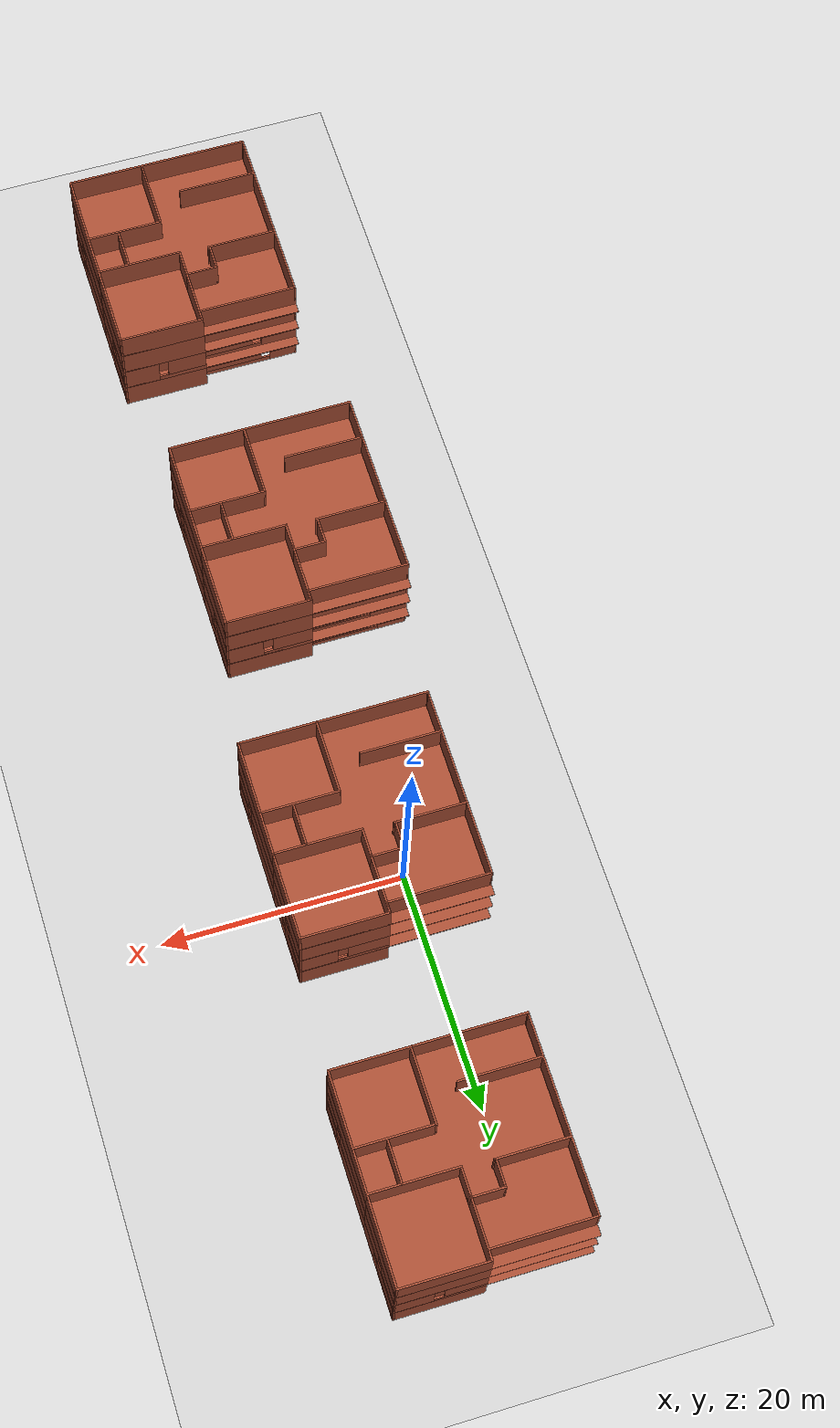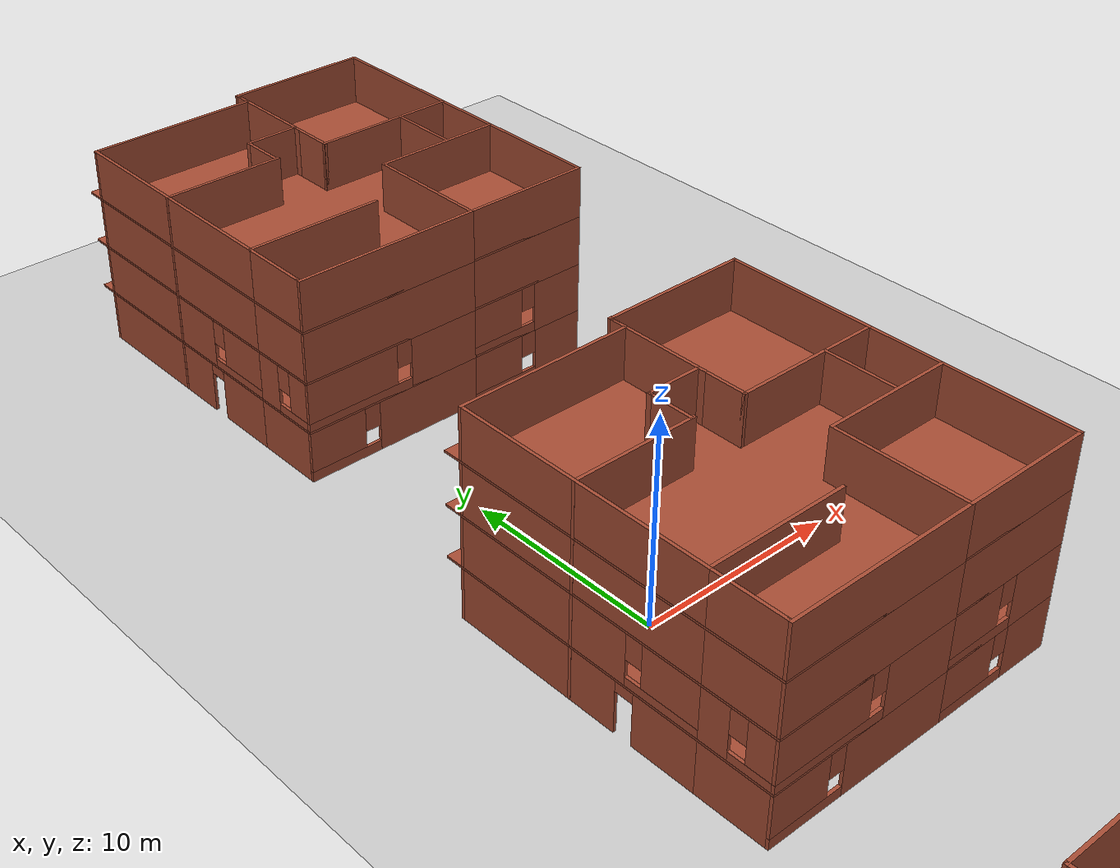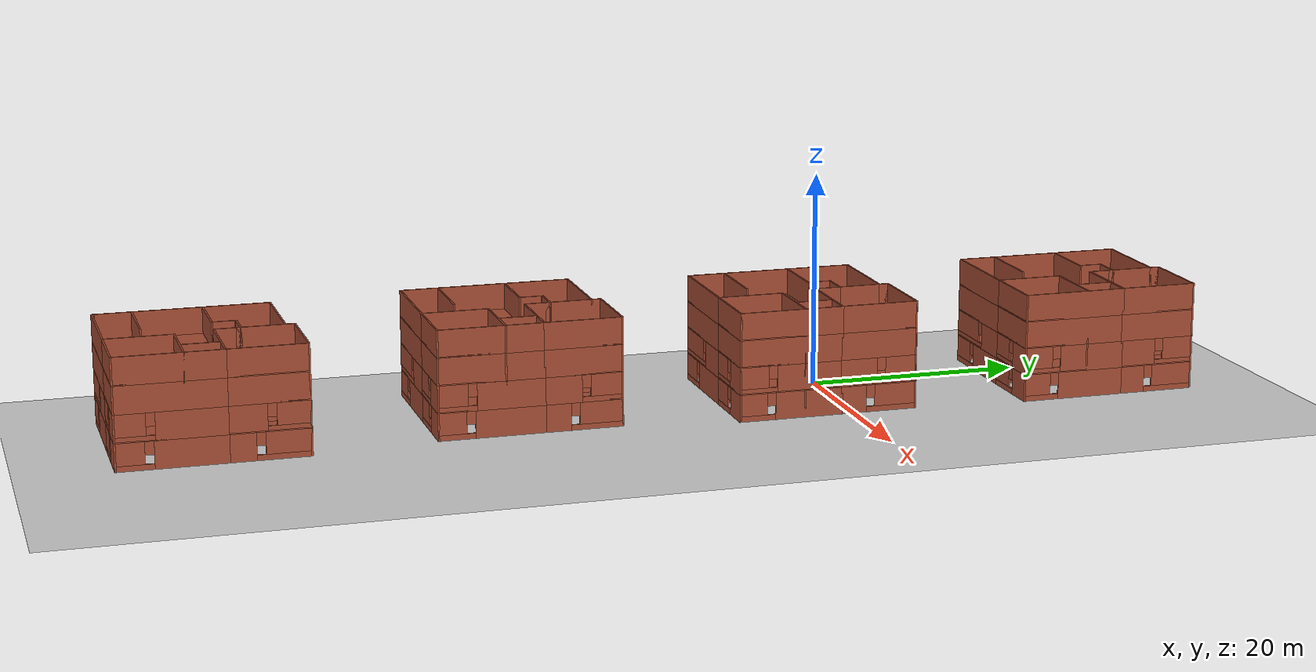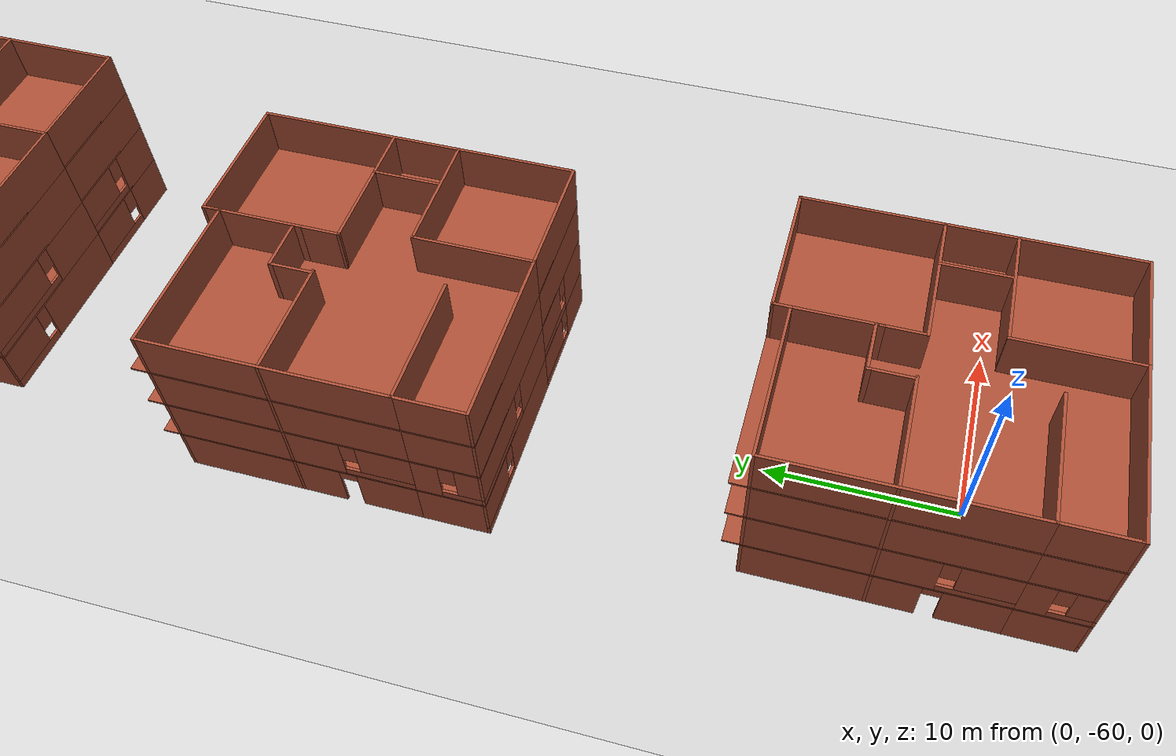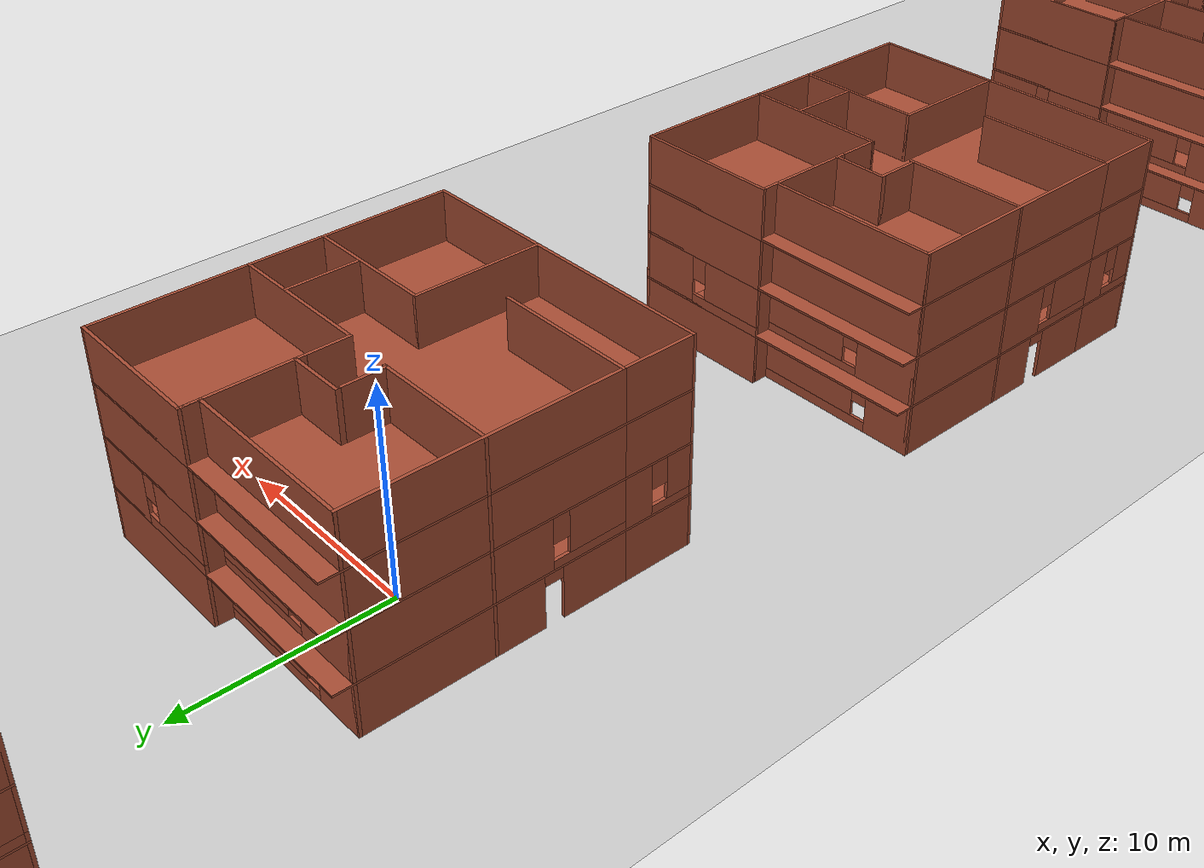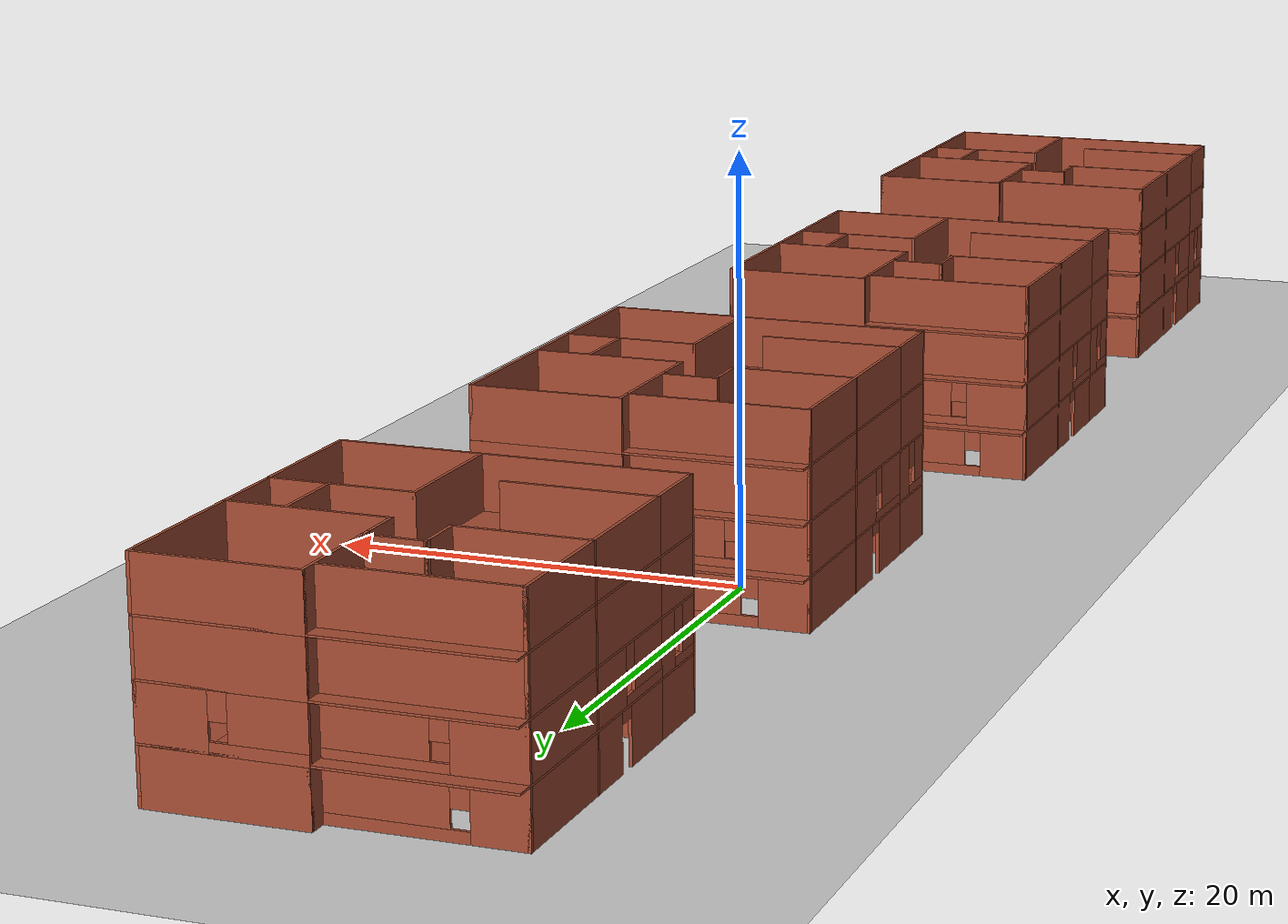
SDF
<sdf version="1.7">
 <world name="default">
  <light name="sun" type="directional">
   <pose>0 0 10 0 -0 0</pose>
   <diffuse>0.8 0.8 0.8 1</diffuse>
   <specular>0.2 0.2 0.2 1</specular>
   <attenuation>
    <range>1000</range>
    <constant>0.9</constant>
    <linear>0.01</linear>
    <quadratic>0.001</quadratic>
   </attenuation>
   <direction>-0.5 0.1 -0.9</direction>
   <spot><inner_angle>0</inner_angle><outer_angle>0</outer_angle><falloff>0</falloff></spot>
  </light>
  <model name="ground_plane">
   <static>1</static>
   <link name="link">
    <collision name="collision">
     <geometry><plane><normal>0 0 1</normal><size>300 300</size></plane></geometry>
     <surface>
      <contact><collide_bitmask>65535</collide_bitmask></contact>
      <friction><ode><mu>100</mu><mu2>50</mu2></ode></friction>
     </surface>
    </collision>
    <visual name="visual">
     <cast_shadows>0</cast_shadows>
     <geometry><plane><normal>0 0 1</normal><size>300 300</size></plane></geometry>
     <material>
      <script><uri>file://media/materials/scripts/gazebo.material</uri><name>Gazebo/Grey</name></script>
     </material>
    </visual>
   </link>
  </model>
  <gravity>0 0 -9.8</gravity>
  <magnetic_field>6e-06 2.3e-05 -4.2e-05</magnetic_field>
  <atmosphere type="adiabatic"/>
  <physics type="ode">
   <max_step_size>0.001</max_step_size>
   <real_time_factor>1</real_time_factor>
   <real_time_update_rate>1000</real_time_update_rate>
  </physics>
  <scene><ambient>0.4 0.4 0.4 1</ambient><background>0.7 0.7 0.7 1</background><shadows>1</shadows></scene>
  <spherical_coordinates>
   <surface_model>EARTH_WGS84</surface_model>
   <latitude_deg>0</latitude_deg>
   <longitude_deg>0</longitude_deg>
   <elevation>0</elevation>
   <heading_deg>0</heading_deg>
  </spherical_coordinates>
  <model name="Drone_House">
   <pose>2.65602 -2.34694 0 0 -0 0</pose>
   <link name="Floor_0">
    <pose>-1e-06 0 2.5 0 -0 0</pose>
    <visual name="Floor_0_Visual_0">
     <pose>-3.13292 0 0.05 0 -0 0</pose>
     <geometry><box><size>9.33629 16.85 0.1</size></box></geometry>
     <material>
      <script><uri>file://media/materials/scripts/gazebo.material</uri><name>Gazebo/Bricks</name></script>
      <ambient>1 1 1 1</ambient>
     </material>
     <meta><layer>1</layer></meta>
    </visual>
    <collision name="Floor_0_Collision_0">
     <geometry><box><size>9.33629 16.85 0.1</size></box></geometry>
     <pose>-3.13292 0 0.05 0 -0 0</pose>
    </collision>
    <visual name="Floor_0_Visual_1">
     <pose>4.66814 -4.13229 0.05 0 -0 0</pose>
     <geometry><box><size>6.26584 8.58542 0.1</size></box></geometry>
     <material>
      <script><uri>file://media/materials/scripts/gazebo.material</uri><name>Gazebo/Bricks</name></script>
      <ambient>1 1 1 1</ambient>
     </material>
     <meta><layer>1</layer></meta>
    </visual>
    <collision name="Floor_0_Collision_1">
     <geometry><box><size>6.26584 8.58542 0.1</size></box></geometry>
     <pose>4.66814 -4.13229 0.05 0 -0 0</pose>
    </collision>
    <visual name="Floor_0_Visual_2">
     <pose>6.41814 4.29271 0.05 0 -0 0</pose>
     <geometry><box><size>2.76584 8.26458 0.1</size></box></geometry>
     <material>
      <script><uri>file://media/materials/scripts/gazebo.material</uri><name>Gazebo/Bricks</name></script>
      <ambient>1 1 1 1</ambient>
     </material>
     <meta><layer>1</layer></meta>
    </visual>
    <collision name="Floor_0_Collision_2">
     <geometry><box><size>2.76584 8.26458 0.1</size></box></geometry>
     <pose>6.41814 4.29271 0.05 0 -0 0</pose>
    </collision>
    <visual name="Floor_0_Visual_3">
     <pose>3.28522 4.79271 0.05 0 -0 0</pose>
     <geometry><box><size>3.5 7.26458 0.1</size></box></geometry>
     <material>
      <script><uri>file://media/materials/scripts/gazebo.material</uri><name>Gazebo/Bricks</name></script>
      <ambient>1 1 1 1</ambient>
     </material>
     <meta><layer>1</layer></meta>
    </visual>
    <collision name="Floor_0_Collision_3">
     <geometry><box><size>3.5 7.26458 0.1</size></box></geometry>
     <pose>3.28522 4.79271 0.05 0 -0 0</pose>
    </collision>
   </link>
   <link name="Floor_5">
    <collision name="Floor_5_Collision">
     <geometry><box><size>15.6021 16.85 0.1</size></box></geometry>
     <pose>0 0 0.05 0 -0 0</pose>
    </collision>
    <visual name="Floor_5_Visual">
     <pose>0 0 0.05 0 -0 0</pose>
     <geometry><box><size>15.6021 16.85 0.1</size></box></geometry>
     <material>
      <script><uri>file://media/materials/scripts/gazebo.material</uri><name>Gazebo/Bricks</name></script>
      <ambient>1 1 1 1</ambient>
     </material>
     <meta><layer>2</layer></meta>
    </visual>
    <pose>-1e-06 0 5 0 -0 0</pose>
   </link>
   <link name="Floor_6">
    <collision name="Floor_6_Collision">
     <geometry><box><size>15.6021 16.85 0.1</size></box></geometry>
     <pose>0 0 0.05 0 -0 0</pose>
    </collision>
    <visual name="Floor_6_Visual">
     <pose>0 0 0.05 0 -0 0</pose>
     <geometry><box><size>15.6021 16.85 0.1</size></box></geometry>
     <material>
      <script><uri>file://media/materials/scripts/gazebo.material</uri><name>Gazebo/Bricks</name></script>
      <ambient>1 1 1 1</ambient>
     </material>
     <meta><layer>3</layer></meta>
    </visual>
    <pose>-1e-06 0 7.5 0 -0 0</pose>
   </link>
   <link name="Stairs_0">
    <visual name="Stairs_0_Visual_0">
     <pose>4.91856 0.660416 0.083333 0 -0 -1.5708</pose>
     <geometry><box><size>1 0.233333 0.166667</size></box></geometry>
     <material>
      <script><uri>file://media/materials/scripts/gazebo.material</uri><name>Gazebo/Bricks</name></script>
      <ambient>1 1 1 1</ambient>
     </material>
     <meta><layer>0</layer></meta>
    </visual>
    <collision name="Stairs_0_Collision_0">
     <geometry><box><size>1 0.233333 0.166667</size></box></geometry>
     <pose>4.91856 0.660416 0.083333 0 -0 -1.5708</pose>
    </collision>
    <visual name="Stairs_0_Visual_1">
     <pose>4.68522 0.660416 0.25 0 -0 -1.5708</pose>
     <geometry><box><size>1 0.233333 0.166667</size></box></geometry>
     <material>
      <script><uri>file://media/materials/scripts/gazebo.material</uri><name>Gazebo/Bricks</name></script>
      <ambient>1 1 1 1</ambient>
     </material>
     <meta><layer>0</layer></meta>
    </visual>
    <collision name="Stairs_0_Collision_1">
     <geometry><box><size>1 0.233333 0.166667</size></box></geometry>
     <pose>4.68522 0.660416 0.25 0 -0 -1.5708</pose>
    </collision>
    <visual name="Stairs_0_Visual_2">
     <pose>4.45189 0.660416 0.416667 0 -0 -1.5708</pose>
     <geometry><box><size>1 0.233333 0.166667</size></box></geometry>
     <material>
      <script><uri>file://media/materials/scripts/gazebo.material</uri><name>Gazebo/Bricks</name></script>
      <ambient>1 1 1 1</ambient>
     </material>
     <meta><layer>0</layer></meta>
    </visual>
    <collision name="Stairs_0_Collision_2">
     <geometry><box><size>1 0.233333 0.166667</size></box></geometry>
     <pose>4.45189 0.660416 0.416667 0 -0 -1.5708</pose>
    </collision>
    <visual name="Stairs_0_Visual_3">
     <pose>4.21856 0.660416 0.583333 0 -0 -1.5708</pose>
     <geometry><box><size>1 0.233333 0.166667</size></box></geometry>
     <material>
      <script><uri>file://media/materials/scripts/gazebo.material</uri><name>Gazebo/Bricks</name></script>
      <ambient>1 1 1 1</ambient>
     </material>
     <meta><layer>0</layer></meta>
    </visual>
    <collision name="Stairs_0_Collision_3">
     <geometry><box><size>1 0.233333 0.166667</size></box></geometry>
     <pose>4.21856 0.660416 0.583333 0 -0 -1.5708</pose>
    </collision>
    <visual name="Stairs_0_Visual_4">
     <pose>3.98522 0.660417 0.75 0 -0 -1.5708</pose>
     <geometry><box><size>1 0.233333 0.166667</size></box></geometry>
     <material>
      <script><uri>file://media/materials/scripts/gazebo.material</uri><name>Gazebo/Bricks</name></script>
      <ambient>1 1 1 1</ambient>
     </material>
     <meta><layer>0</layer></meta>
    </visual>
    <collision name="Stairs_0_Collision_4">
     <geometry><box><size>1 0.233333 0.166667</size></box></geometry>
     <pose>3.98522 0.660417 0.75 0 -0 -1.5708</pose>
    </collision>
    <visual name="Stairs_0_Visual_5">
     <pose>3.75189 0.660417 0.916667 0 -0 -1.5708</pose>
     <geometry><box><size>1 0.233333 0.166667</size></box></geometry>
     <material>
      <script><uri>file://media/materials/scripts/gazebo.material</uri><name>Gazebo/Bricks</name></script>
      <ambient>1 1 1 1</ambient>
     </material>
     <meta><layer>0</layer></meta>
    </visual>
    <collision name="Stairs_0_Collision_5">
     <geometry><box><size>1 0.233333 0.166667</size></box></geometry>
     <pose>3.75189 0.660417 0.916667 0 -0 -1.5708</pose>
    </collision>
    <visual name="Stairs_0_Visual_6">
     <pose>3.51856 0.660417 1.08333 0 -0 -1.5708</pose>
     <geometry><box><size>1 0.233333 0.166667</size></box></geometry>
     <material>
      <script><uri>file://media/materials/scripts/gazebo.material</uri><name>Gazebo/Bricks</name></script>
      <ambient>1 1 1 1</ambient>
     </material>
     <meta><layer>0</layer></meta>
    </visual>
    <collision name="Stairs_0_Collision_6">
     <geometry><box><size>1 0.233333 0.166667</size></box></geometry>
     <pose>3.51856 0.660417 1.08333 0 -0 -1.5708</pose>
    </collision>
    <visual name="Stairs_0_Visual_7">
     <pose>3.28522 0.660417 1.25 0 -0 -1.5708</pose>
     <geometry><box><size>1 0.233333 0.166667</size></box></geometry>
     <material>
      <script><uri>file://media/materials/scripts/gazebo.material</uri><name>Gazebo/Bricks</name></script>
      <ambient>1 1 1 1</ambient>
     </material>
     <meta><layer>0</layer></meta>
    </visual>
    <collision name="Stairs_0_Collision_7">
     <geometry><box><size>1 0.233333 0.166667</size></box></geometry>
     <pose>3.28522 0.660417 1.25 0 -0 -1.5708</pose>
    </collision>
    <visual name="Stairs_0_Visual_8">
     <pose>3.05189 0.660417 1.41667 0 -0 -1.5708</pose>
     <geometry><box><size>1 0.233333 0.166667</size></box></geometry>
     <material>
      <script><uri>file://media/materials/scripts/gazebo.material</uri><name>Gazebo/Bricks</name></script>
      <ambient>1 1 1 1</ambient>
     </material>
     <meta><layer>0</layer></meta>
    </visual>
    <collision name="Stairs_0_Collision_8">
     <geometry><box><size>1 0.233333 0.166667</size></box></geometry>
     <pose>3.05189 0.660417 1.41667 0 -0 -1.5708</pose>
    </collision>
    <visual name="Stairs_0_Visual_9">
     <pose>2.81856 0.660417 1.58333 0 -0 -1.5708</pose>
     <geometry><box><size>1 0.233333 0.166667</size></box></geometry>
     <material>
      <script><uri>file://media/materials/scripts/gazebo.material</uri><name>Gazebo/Bricks</name></script>
      <ambient>1 1 1 1</ambient>
     </material>
     <meta><layer>0</layer></meta>
    </visual>
    <collision name="Stairs_0_Collision_9">
     <geometry><box><size>1 0.233333 0.166667</size></box></geometry>
     <pose>2.81856 0.660417 1.58333 0 -0 -1.5708</pose>
    </collision>
    <visual name="Stairs_0_Visual_10">
     <pose>2.58522 0.660417 1.75 0 -0 -1.5708</pose>
     <geometry><box><size>1 0.233333 0.166667</size></box></geometry>
     <material>
      <script><uri>file://media/materials/scripts/gazebo.material</uri><name>Gazebo/Bricks</name></script>
      <ambient>1 1 1 1</ambient>
     </material>
     <meta><layer>0</layer></meta>
    </visual>
    <collision name="Stairs_0_Collision_10">
     <geometry><box><size>1 0.233333 0.166667</size></box></geometry>
     <pose>2.58522 0.660417 1.75 0 -0 -1.5708</pose>
    </collision>
    <visual name="Stairs_0_Visual_11">
     <pose>2.35189 0.660417 1.91667 0 -0 -1.5708</pose>
     <geometry><box><size>1 0.233333 0.166667</size></box></geometry>
     <material>
      <script><uri>file://media/materials/scripts/gazebo.material</uri><name>Gazebo/Bricks</name></script>
      <ambient>1 1 1 1</ambient>
     </material>
     <meta><layer>0</layer></meta>
    </visual>
    <collision name="Stairs_0_Collision_11">
     <geometry><box><size>1 0.233333 0.166667</size></box></geometry>
     <pose>2.35189 0.660417 1.91667 0 -0 -1.5708</pose>
    </collision>
    <visual name="Stairs_0_Visual_12">
     <pose>2.11856 0.660417 2.08333 0 -0 -1.5708</pose>
     <geometry><box><size>1 0.233333 0.166667</size></box></geometry>
     <material>
      <script><uri>file://media/materials/scripts/gazebo.material</uri><name>Gazebo/Bricks</name></script>
      <ambient>1 1 1 1</ambient>
     </material>
     <meta><layer>0</layer></meta>
    </visual>
    <collision name="Stairs_0_Collision_12">
     <geometry><box><size>1 0.233333 0.166667</size></box></geometry>
     <pose>2.11856 0.660417 2.08333 0 -0 -1.5708</pose>
    </collision>
    <visual name="Stairs_0_Visual_13">
     <pose>1.88522 0.660417 2.25 0 -0 -1.5708</pose>
     <geometry><box><size>1 0.233333 0.166667</size></box></geometry>
     <material>
      <script><uri>file://media/materials/scripts/gazebo.material</uri><name>Gazebo/Bricks</name></script>
      <ambient>1 1 1 1</ambient>
     </material>
     <meta><layer>0</layer></meta>
    </visual>
    <collision name="Stairs_0_Collision_13">
     <geometry><box><size>1 0.233333 0.166667</size></box></geometry>
     <pose>1.88522 0.660417 2.25 0 -0 -1.5708</pose>
    </collision>
    <visual name="Stairs_0_Visual_14">
     <pose>1.65189 0.660417 2.41667 0 -0 -1.5708</pose>
     <geometry><box><size>1 0.233333 0.166667</size></box></geometry>
     <material>
      <script><uri>file://media/materials/scripts/gazebo.material</uri><name>Gazebo/Bricks</name></script>
      <ambient>1 1 1 1</ambient>
     </material>
     <meta><layer>0</layer></meta>
    </visual>
    <collision name="Stairs_0_Collision_14">
     <geometry><box><size>1 0.233333 0.166667</size></box></geometry>
     <pose>1.65189 0.660417 2.41667 0 -0 -1.5708</pose>
    </collision>
   </link>
   <link name="Wall_10">
    <collision name="Wall_10_Collision">
     <geometry><box><size>1 0.15 2.5</size></box></geometry>
     <pose>0 0 1.25 0 -0 0</pose>
    </collision>
    <visual name="Wall_10_Visual">
     <pose>0 0 1.25 0 -0 0</pose>
     <geometry><box><size>1 0.15 2.5</size></box></geometry>
     <material>
      <script><uri>file://media/materials/scripts/gazebo.material</uri><name>Gazebo/Bricks</name></script>
      <ambient>1 1 1 1</ambient>
     </material>
     <meta><layer>0</layer></meta>
    </visual>
    <pose>0.626064 7.925 0 0 -0 1.5708</pose>
   </link>
   <link name="Wall_100">
    <collision name="Wall_100_Collision">
     <geometry><box><size>6.25 0.15 2.5</size></box></geometry>
     <pose>0 0 1.25 0 -0 0</pose>
    </collision>
    <visual name="Wall_100_Visual">
     <pose>0 0 1.25 0 -0 0</pose>
     <geometry><box><size>6.25 0.15 2.5</size></box></geometry>
     <material>
      <script><uri>file://media/materials/scripts/gazebo.material</uri><name>Gazebo/Bricks</name></script>
      <ambient>1 1 1 1</ambient>
     </material>
     <meta><layer>2</layer></meta>
    </visual>
    <pose>1.37606 -5.3 5 0 -0 1.5708</pose>
   </link>
   <link name="Wall_101">
    <collision name="Wall_101_Collision">
     <geometry><box><size>6.5 0.15 2.5</size></box></geometry>
     <pose>0 0 1.25 0 -0 0</pose>
    </collision>
    <visual name="Wall_101_Visual">
     <pose>0 0 1.25 0 -0 0</pose>
     <geometry><box><size>6.5 0.15 2.5</size></box></geometry>
     <material>
      <script><uri>file://media/materials/scripts/gazebo.material</uri><name>Gazebo/Bricks</name></script>
      <ambient>1 1 1 1</ambient>
     </material>
     <meta><layer>2</layer></meta>
    </visual>
    <pose>4.55106 -2.25 5 0 -0 0</pose>
   </link>
   <link name="Wall_102">
    <collision name="Wall_102_Collision">
     <geometry><box><size>3.5 0.15 2.5</size></box></geometry>
     <pose>0 0 1.25 0 -0 0</pose>
    </collision>
    <visual name="Wall_102_Visual">
     <pose>0 0 1.25 0 -0 0</pose>
     <geometry><box><size>3.5 0.15 2.5</size></box></geometry>
     <material>
      <script><uri>file://media/materials/scripts/gazebo.material</uri><name>Gazebo/Bricks</name></script>
      <ambient>1 1 1 1</ambient>
     </material>
     <meta><layer>2</layer></meta>
    </visual>
    <pose>-7.72394 -6.525 5 0 -0 -1.5708</pose>
   </link>
   <link name="Wall_103">
    <collision name="Wall_103_Collision">
     <geometry><box><size>0.15 0.15 2.5</size></box></geometry>
     <pose>0 0 1.25 0 -0 0</pose>
    </collision>
    <visual name="Wall_103_Visual">
     <pose>0 0 1.25 0 -0 0</pose>
     <geometry><box><size>0.15 0.15 2.5</size></box></geometry>
     <material>
      <script><uri>file://media/materials/scripts/gazebo.material</uri><name>Gazebo/Bricks</name></script>
      <ambient>1 1 1 1</ambient>
     </material>
     <meta><layer>2</layer></meta>
    </visual>
    <pose>-7.72394 -8.2 5 0 -0 0</pose>
   </link>
   <link name="Wall_104">
    <collision name="Wall_104_Collision">
     <geometry><box><size>9.25 0.15 2.5</size></box></geometry>
     <pose>0 0 1.25 0 -0 0</pose>
    </collision>
    <visual name="Wall_104_Visual">
     <pose>0 0 1.25 0 -0 0</pose>
     <geometry><box><size>9.25 0.15 2.5</size></box></geometry>
     <material>
      <script><uri>file://media/materials/scripts/gazebo.material</uri><name>Gazebo/Bricks</name></script>
      <ambient>1 1 1 1</ambient>
     </material>
     <meta><layer>2</layer></meta>
    </visual>
    <pose>-3.17394 -8.35 5 0 -0 3.14159</pose>
   </link>
   <link name="Wall_105">
    <collision name="Wall_105_Collision">
     <geometry><box><size>3.5 0.15 2.5</size></box></geometry>
     <pose>0 0 1.25 0 -0 0</pose>
    </collision>
    <visual name="Wall_105_Visual">
     <pose>0 0 1.25 0 -0 0</pose>
     <geometry><box><size>3.5 0.15 2.5</size></box></geometry>
     <material>
      <script><uri>file://media/materials/scripts/gazebo.material</uri><name>Gazebo/Bricks</name></script>
      <ambient>1 1 1 1</ambient>
     </material>
     <meta><layer>2</layer></meta>
    </visual>
    <pose>5.09404 -0.429379 5 0 -0 -1.5708</pose>
   </link>
   <link name="Wall_106">
    <collision name="Wall_106_Collision">
     <geometry><box><size>12.5 0.15 2.5</size></box></geometry>
     <pose>0 0 1.25 0 -0 0</pose>
    </collision>
    <visual name="Wall_106_Visual">
     <pose>0 0 1.25 0 -0 0</pose>
     <geometry><box><size>12.5 0.15 2.5</size></box></geometry>
     <material>
      <script><uri>file://media/materials/scripts/gazebo.material</uri><name>Gazebo/Bricks</name></script>
      <ambient>1 1 1 1</ambient>
     </material>
     <meta><layer>3</layer></meta>
    </visual>
    <pose>-7.72394 1.325 7.5 0 -0 -1.5708</pose>
   </link>
   <link name="Wall_107">
    <collision name="Wall_107_Collision">
     <geometry><box><size>6.75 0.15 2.5</size></box></geometry>
     <pose>0 0 1.25 0 -0 0</pose>
    </collision>
    <visual name="Wall_107_Visual">
     <pose>0 0 1.25 0 -0 0</pose>
     <geometry><box><size>6.75 0.15 2.5</size></box></geometry>
     <material>
      <script><uri>file://media/materials/scripts/gazebo.material</uri><name>Gazebo/Bricks</name></script>
      <ambient>1 1 1 1</ambient>
     </material>
     <meta><layer>3</layer></meta>
    </visual>
    <pose>-4.42394 -4.85 7.5 0 -0 0</pose>
   </link>
   <link name="Wall_108">
    <collision name="Wall_108_Collision">
     <geometry><box><size>6 0.15 2.5</size></box></geometry>
     <pose>0 0 1.25 0 -0 0</pose>
    </collision>
    <visual name="Wall_108_Visual">
     <pose>0 0 1.25 0 -0 0</pose>
     <geometry><box><size>6 0.15 2.5</size></box></geometry>
     <material>
      <script><uri>file://media/materials/scripts/gazebo.material</uri><name>Gazebo/Bricks</name></script>
      <ambient>1 1 1 1</ambient>
     </material>
     <meta><layer>3</layer></meta>
    </visual>
    <pose>-4.80107 1.443 7.5 0 -0 0</pose>
   </link>
   <link name="Wall_109">
    <collision name="Wall_109_Collision">
     <geometry><box><size>8.5 0.15 2.5</size></box></geometry>
     <pose>0 0 1.25 0 -0 0</pose>
    </collision>
    <visual name="Wall_109_Visual">
     <pose>0 0 1.25 0 -0 0</pose>
     <geometry><box><size>8.5 0.15 2.5</size></box></geometry>
     <material>
      <script><uri>file://media/materials/scripts/gazebo.material</uri><name>Gazebo/Bricks</name></script>
      <ambient>1 1 1 1</ambient>
     </material>
     <meta><layer>3</layer></meta>
    </visual>
    <pose>-3.54894 7.5 7.5 0 -0 0</pose>
   </link>
   <link name="Wall_11">
    <collision name="Wall_11_Collision">
     <geometry><box><size>5.25 0.15 2.5</size></box></geometry>
     <pose>0 0 1.25 0 -0 0</pose>
    </collision>
    <visual name="Wall_11_Visual">
     <pose>0 0 1.25 0 -0 0</pose>
     <geometry><box><size>5.25 0.15 2.5</size></box></geometry>
     <material>
      <script><uri>file://media/materials/scripts/gazebo.material</uri><name>Gazebo/Bricks</name></script>
      <ambient>1 1 1 1</ambient>
     </material>
     <meta><layer>0</layer></meta>
    </visual>
    <pose>0.626064 5.8 0 0 -0 -1.5708</pose>
   </link>
   <link name="Wall_110">
    <collision name="Wall_110_Collision">
     <geometry><box><size>1 0.15 2.5</size></box></geometry>
     <pose>0 0 1.25 0 -0 0</pose>
    </collision>
    <visual name="Wall_110_Visual">
     <pose>0 0 1.25 0 -0 0</pose>
     <geometry><box><size>1 0.15 2.5</size></box></geometry>
     <material>
      <script><uri>file://media/materials/scripts/gazebo.material</uri><name>Gazebo/Bricks</name></script>
      <ambient>1 1 1 1</ambient>
     </material>
     <meta><layer>3</layer></meta>
    </visual>
    <pose>0.626064 7.925 7.5 0 -0 1.5708</pose>
   </link>
   <link name="Wall_111">
    <collision name="Wall_111_Collision">
     <geometry><box><size>5.25 0.15 2.5</size></box></geometry>
     <pose>0 0 1.25 0 -0 0</pose>
    </collision>
    <visual name="Wall_111_Visual">
     <pose>0 0 1.25 0 -0 0</pose>
     <geometry><box><size>5.25 0.15 2.5</size></box></geometry>
     <material>
      <script><uri>file://media/materials/scripts/gazebo.material</uri><name>Gazebo/Bricks</name></script>
      <ambient>1 1 1 1</ambient>
     </material>
     <meta><layer>3</layer></meta>
    </visual>
    <pose>0.626064 5.8 7.5 0 -0 -1.5708</pose>
   </link>
   <link name="Wall_112">
    <collision name="Wall_112_Collision">
     <geometry><box><size>0.5 0.15 2.5</size></box></geometry>
     <pose>0 0 1.25 0 -0 0</pose>
    </collision>
    <visual name="Wall_112_Visual">
     <pose>0 0 1.25 0 -0 0</pose>
     <geometry><box><size>0.5 0.15 2.5</size></box></geometry>
     <material>
      <script><uri>file://media/materials/scripts/gazebo.material</uri><name>Gazebo/Bricks</name></script>
      <ambient>1 1 1 1</ambient>
     </material>
     <meta><layer>3</layer></meta>
    </visual>
    <pose>0.626064 3.425 7.5 0 -0 1.5708</pose>
   </link>
   <link name="Wall_113">
    <collision name="Wall_113_Collision">
     <geometry><box><size>2.75 0.15 2.5</size></box></geometry>
     <pose>0 0 1.25 0 -0 0</pose>
    </collision>
    <visual name="Wall_113_Visual">
     <pose>0 0 1.25 0 -0 0</pose>
     <geometry><box><size>2.75 0.15 2.5</size></box></geometry>
     <material>
      <script><uri>file://media/materials/scripts/gazebo.material</uri><name>Gazebo/Bricks</name></script>
      <ambient>1 1 1 1</ambient>
     </material>
     <meta><layer>3</layer></meta>
    </visual>
    <pose>-0.673936 3.6 7.5 0 -0 3.14159</pose>
   </link>
   <link name="Wall_114">
    <collision name="Wall_114_Collision">
     <geometry><box><size>0.25 0.15 2.5</size></box></geometry>
     <pose>0 0 1.25 0 -0 0</pose>
    </collision>
    <visual name="Wall_114_Visual">
     <pose>0 0 1.25 0 -0 0</pose>
     <geometry><box><size>0.25 0.15 2.5</size></box></geometry>
     <material>
      <script><uri>file://media/materials/scripts/gazebo.material</uri><name>Gazebo/Bricks</name></script>
      <ambient>1 1 1 1</ambient>
     </material>
     <meta><layer>3</layer></meta>
    </visual>
    <pose>-1.97394 3.55 7.5 0 -0 -1.5708</pose>
   </link>
   <link name="Wall_115">
    <collision name="Wall_115_Collision">
     <geometry><box><size>2.25 0.15 2.5</size></box></geometry>
     <pose>0 0 1.25 0 -0 0</pose>
    </collision>
    <visual name="Wall_115_Visual">
     <pose>0 0 1.25 0 -0 0</pose>
     <geometry><box><size>2.25 0.15 2.5</size></box></geometry>
     <material>
      <script><uri>file://media/materials/scripts/gazebo.material</uri><name>Gazebo/Bricks</name></script>
      <ambient>1 1 1 1</ambient>
     </material>
     <meta><layer>3</layer></meta>
    </visual>
    <pose>-1.97394 2.55 7.5 0 -0 -1.5708</pose>
   </link>
   <link name="Wall_116">
    <collision name="Wall_116_Collision">
     <geometry><box><size>2.5 0.15 2.5</size></box></geometry>
     <pose>0 0 1.25 0 -0 0</pose>
    </collision>
    <visual name="Wall_116_Visual">
     <pose>0 0 1.25 0 -0 0</pose>
     <geometry><box><size>2.5 0.15 2.5</size></box></geometry>
     <material>
      <script><uri>file://media/materials/scripts/gazebo.material</uri><name>Gazebo/Bricks</name></script>
      <ambient>1 1 1 1</ambient>
     </material>
     <meta><layer>3</layer></meta>
    </visual>
    <pose>0.626064 2.425 7.5 0 -0 -1.5708</pose>
   </link>
   <link name="Wall_117">
    <collision name="Wall_117_Collision">
     <geometry><box><size>7.25 0.15 2.5</size></box></geometry>
     <pose>0 0 1.25 0 -0 0</pose>
    </collision>
    <visual name="Wall_117_Visual">
     <pose>0 0 1.25 0 -0 0</pose>
     <geometry><box><size>7.25 0.15 2.5</size></box></geometry>
     <material>
      <script><uri>file://media/materials/scripts/gazebo.material</uri><name>Gazebo/Bricks</name></script>
      <ambient>1 1 1 1</ambient>
     </material>
     <meta><layer>3</layer></meta>
    </visual>
    <pose>4.17606 1.25 7.5 0 -0 0</pose>
   </link>
   <link name="Wall_118">
    <collision name="Wall_118_Collision">
     <geometry><box><size>7.25 0.15 2.5</size></box></geometry>
     <pose>0 0 1.25 0 -0 0</pose>
    </collision>
    <visual name="Wall_118_Visual">
     <pose>0 0 1.25 0 -0 0</pose>
     <geometry><box><size>7.25 0.15 2.5</size></box></geometry>
     <material>
      <script><uri>file://media/materials/scripts/gazebo.material</uri><name>Gazebo/Bricks</name></script>
      <ambient>1 1 1 1</ambient>
     </material>
     <meta><layer>3</layer></meta>
    </visual>
    <pose>7.72606 4.8 7.5 0 -0 1.5708</pose>
   </link>
   <link name="Wall_119">
    <collision name="Wall_119_Collision">
     <geometry><box><size>7.25 0.15 2.5</size></box></geometry>
     <pose>0 0 1.25 0 -0 0</pose>
    </collision>
    <visual name="Wall_119_Visual">
     <pose>0 0 1.25 0 -0 0</pose>
     <geometry><box><size>7.25 0.15 2.5</size></box></geometry>
     <material>
      <script><uri>file://media/materials/scripts/gazebo.material</uri><name>Gazebo/Bricks</name></script>
      <ambient>1 1 1 1</ambient>
     </material>
     <meta><layer>3</layer></meta>
    </visual>
    <pose>4.17606 8.35 7.5 0 -0 3.14159</pose>
   </link>
   <link name="Wall_12">
    <collision name="Wall_12_Collision">
     <geometry><box><size>0.5 0.15 2.5</size></box></geometry>
     <pose>0 0 1.25 0 -0 0</pose>
    </collision>
    <visual name="Wall_12_Visual">
     <pose>0 0 1.25 0 -0 0</pose>
     <geometry><box><size>0.5 0.15 2.5</size></box></geometry>
     <material>
      <script><uri>file://media/materials/scripts/gazebo.material</uri><name>Gazebo/Bricks</name></script>
      <ambient>1 1 1 1</ambient>
     </material>
     <meta><layer>0</layer></meta>
    </visual>
    <pose>0.626064 3.425 0 0 -0 1.5708</pose>
   </link>
   <link name="Wall_120">
    <collision name="Wall_120_Collision">
     <geometry><box><size>9.75 0.15 2.5</size></box></geometry>
     <pose>0 0 1.25 0 -0 0</pose>
    </collision>
    <visual name="Wall_120_Visual">
     <pose>0 0 1.25 0 -0 0</pose>
     <geometry><box><size>9.75 0.15 2.5</size></box></geometry>
     <material>
      <script><uri>file://media/materials/scripts/gazebo.material</uri><name>Gazebo/Bricks</name></script>
      <ambient>1 1 1 1</ambient>
     </material>
     <meta><layer>3</layer></meta>
    </visual>
    <pose>7.72606 -3.55 7.5 0 -0 -1.5708</pose>
   </link>
   <link name="Wall_121">
    <collision name="Wall_121_Collision">
     <geometry><box><size>6.5 0.15 2.5</size></box></geometry>
     <pose>0 0 1.25 0 -0 0</pose>
    </collision>
    <visual name="Wall_121_Visual">
     <pose>0 0 1.25 0 -0 0</pose>
     <geometry><box><size>6.5 0.15 2.5</size></box></geometry>
     <material>
      <script><uri>file://media/materials/scripts/gazebo.material</uri><name>Gazebo/Bricks</name></script>
      <ambient>1 1 1 1</ambient>
     </material>
     <meta><layer>3</layer></meta>
    </visual>
    <pose>4.55106 -8.35 7.5 0 -0 3.14159</pose>
   </link>
   <link name="Wall_122">
    <collision name="Wall_122_Collision">
     <geometry><box><size>6.25 0.15 2.5</size></box></geometry>
     <pose>0 0 1.25 0 -0 0</pose>
    </collision>
    <visual name="Wall_122_Visual">
     <pose>0 0 1.25 0 -0 0</pose>
     <geometry><box><size>6.25 0.15 2.5</size></box></geometry>
     <material>
      <script><uri>file://media/materials/scripts/gazebo.material</uri><name>Gazebo/Bricks</name></script>
      <ambient>1 1 1 1</ambient>
     </material>
     <meta><layer>3</layer></meta>
    </visual>
    <pose>1.37606 -5.3 7.5 0 -0 1.5708</pose>
   </link>
   <link name="Wall_123">
    <collision name="Wall_123_Collision">
     <geometry><box><size>6.5 0.15 2.5</size></box></geometry>
     <pose>0 0 1.25 0 -0 0</pose>
    </collision>
    <visual name="Wall_123_Visual">
     <pose>0 0 1.25 0 -0 0</pose>
     <geometry><box><size>6.5 0.15 2.5</size></box></geometry>
     <material>
      <script><uri>file://media/materials/scripts/gazebo.material</uri><name>Gazebo/Bricks</name></script>
      <ambient>1 1 1 1</ambient>
     </material>
     <meta><layer>3</layer></meta>
    </visual>
    <pose>4.55106 -2.25 7.5 0 -0 0</pose>
   </link>
   <link name="Wall_124">
    <collision name="Wall_124_Collision">
     <geometry><box><size>3.5 0.15 2.5</size></box></geometry>
     <pose>0 0 1.25 0 -0 0</pose>
    </collision>
    <visual name="Wall_124_Visual">
     <pose>0 0 1.25 0 -0 0</pose>
     <geometry><box><size>3.5 0.15 2.5</size></box></geometry>
     <material>
      <script><uri>file://media/materials/scripts/gazebo.material</uri><name>Gazebo/Bricks</name></script>
      <ambient>1 1 1 1</ambient>
     </material>
     <meta><layer>3</layer></meta>
    </visual>
    <pose>-7.72394 -6.525 7.5 0 -0 -1.5708</pose>
   </link>
   <link name="Wall_125">
    <collision name="Wall_125_Collision">
     <geometry><box><size>0.15 0.15 2.5</size></box></geometry>
     <pose>0 0 1.25 0 -0 0</pose>
    </collision>
    <visual name="Wall_125_Visual">
     <pose>0 0 1.25 0 -0 0</pose>
     <geometry><box><size>0.15 0.15 2.5</size></box></geometry>
     <material>
      <script><uri>file://media/materials/scripts/gazebo.material</uri><name>Gazebo/Bricks</name></script>
      <ambient>1 1 1 1</ambient>
     </material>
     <meta><layer>3</layer></meta>
    </visual>
    <pose>-7.72394 -8.2 7.5 0 -0 0</pose>
   </link>
   <link name="Wall_126">
    <collision name="Wall_126_Collision">
     <geometry><box><size>9.25 0.15 2.5</size></box></geometry>
     <pose>0 0 1.25 0 -0 0</pose>
    </collision>
    <visual name="Wall_126_Visual">
     <pose>0 0 1.25 0 -0 0</pose>
     <geometry><box><size>9.25 0.15 2.5</size></box></geometry>
     <material>
      <script><uri>file://media/materials/scripts/gazebo.material</uri><name>Gazebo/Bricks</name></script>
      <ambient>1 1 1 1</ambient>
     </material>
     <meta><layer>3</layer></meta>
    </visual>
    <pose>-3.17394 -8.35 7.5 0 -0 3.14159</pose>
   </link>
   <link name="Wall_127">
    <collision name="Wall_127_Collision">
     <geometry><box><size>3.5 0.15 2.5</size></box></geometry>
     <pose>0 0 1.25 0 -0 0</pose>
    </collision>
    <visual name="Wall_127_Visual">
     <pose>0 0 1.25 0 -0 0</pose>
     <geometry><box><size>3.5 0.15 2.5</size></box></geometry>
     <material>
      <script><uri>file://media/materials/scripts/gazebo.material</uri><name>Gazebo/Bricks</name></script>
      <ambient>1 1 1 1</ambient>
     </material>
     <meta><layer>3</layer></meta>
    </visual>
    <pose>5.09404 -0.429379 7.5 0 -0 -1.5708</pose>
   </link>
   <link name="Wall_13">
    <pose>-0.673936 3.6 0 0 -0 3.14159</pose>
    <visual name="Wall_13_Visual_0">
     <pose>-0.843864 0 1.25 0 -0 0</pose>
     <geometry><box><size>1.06227 0.15 2.5</size></box></geometry>
     <material>
      <script><uri>file://media/materials/scripts/gazebo.material</uri><name>Gazebo/Bricks</name></script>
      <ambient>1 1 1 1</ambient>
     </material>
     <meta><layer>0</layer></meta>
    </visual>
    <collision name="Wall_13_Collision_0">
     <geometry><box><size>1.06227 0.15 2.5</size></box></geometry>
     <pose>-0.843864 0 1.25 0 -0 0</pose>
    </collision>
    <visual name="Wall_13_Visual_1">
     <pose>0.981136 0 1.25 0 -0 0</pose>
     <geometry><box><size>0.787728 0.15 2.5</size></box></geometry>
     <material>
      <script><uri>file://media/materials/scripts/gazebo.material</uri><name>Gazebo/Bricks</name></script>
      <ambient>1 1 1 1</ambient>
     </material>
     <meta><layer>0</layer></meta>
    </visual>
    <collision name="Wall_13_Collision_1">
     <geometry><box><size>0.787728 0.15 2.5</size></box></geometry>
     <pose>0.981136 0 1.25 0 -0 0</pose>
    </collision>
    <visual name="Wall_13_Visual_2">
     <pose>0.137272 0 2.25 0 -0 0</pose>
     <geometry><box><size>0.9 0.15 0.5</size></box></geometry>
     <material>
      <script><uri>file://media/materials/scripts/gazebo.material</uri><name>Gazebo/Bricks</name></script>
      <ambient>1 1 1 1</ambient>
     </material>
     <meta><layer>0</layer></meta>
    </visual>
    <collision name="Wall_13_Collision_2">
     <geometry><box><size>0.9 0.15 0.5</size></box></geometry>
     <pose>0.137272 0 2.25 0 -0 0</pose>
    </collision>
   </link>
   <link name="Wall_14">
    <collision name="Wall_14_Collision">
     <geometry><box><size>0.25 0.15 2.5</size></box></geometry>
     <pose>0 0 1.25 0 -0 0</pose>
    </collision>
    <visual name="Wall_14_Visual">
     <pose>0 0 1.25 0 -0 0</pose>
     <geometry><box><size>0.25 0.15 2.5</size></box></geometry>
     <material>
      <script><uri>file://media/materials/scripts/gazebo.material</uri><name>Gazebo/Bricks</name></script>
      <ambient>1 1 1 1</ambient>
     </material>
     <meta><layer>0</layer></meta>
    </visual>
    <pose>-1.97394 3.55 0 0 -0 -1.5708</pose>
   </link>
   <link name="Wall_16">
    <pose>-1.97394 2.55 0 0 -0 -1.5708</pose>
    <visual name="Wall_16_Visual_0">
     <pose>-0.800315 0 1.25 0 -0 0</pose>
     <geometry><box><size>0.649369 0.15 2.5</size></box></geometry>
     <material>
      <script><uri>file://media/materials/scripts/gazebo.material</uri><name>Gazebo/Bricks</name></script>
      <ambient>1 1 1 1</ambient>
     </material>
     <meta><layer>0</layer></meta>
    </visual>
    <collision name="Wall_16_Collision_0">
     <geometry><box><size>0.649369 0.15 2.5</size></box></geometry>
     <pose>-0.800315 0 1.25 0 -0 0</pose>
    </collision>
    <visual name="Wall_16_Visual_1">
     <pose>0.774685 0 1.25 0 -0 0</pose>
     <geometry><box><size>0.700631 0.15 2.5</size></box></geometry>
     <material>
      <script><uri>file://media/materials/scripts/gazebo.material</uri><name>Gazebo/Bricks</name></script>
      <ambient>1 1 1 1</ambient>
     </material>
     <meta><layer>0</layer></meta>
    </visual>
    <collision name="Wall_16_Collision_1">
     <geometry><box><size>0.700631 0.15 2.5</size></box></geometry>
     <pose>0.774685 0 1.25 0 -0 0</pose>
    </collision>
    <visual name="Wall_16_Visual_2">
     <pose>-0.025631 0 2.25 0 -0 0</pose>
     <geometry><box><size>0.9 0.15 0.5</size></box></geometry>
     <material>
      <script><uri>file://media/materials/scripts/gazebo.material</uri><name>Gazebo/Bricks</name></script>
      <ambient>1 1 1 1</ambient>
     </material>
     <meta><layer>0</layer></meta>
    </visual>
    <collision name="Wall_16_Collision_2">
     <geometry><box><size>0.9 0.15 0.5</size></box></geometry>
     <pose>-0.025631 0 2.25 0 -0 0</pose>
    </collision>
   </link>
   <link name="Wall_18">
    <pose>0.626064 2.425 0 0 -0 -1.5708</pose>
    <visual name="Wall_18_Visual_0">
     <pose>-0.898715 0 1.25 0 -0 0</pose>
     <geometry><box><size>0.70257 0.15 2.5</size></box></geometry>
     <material>
      <script><uri>file://media/materials/scripts/gazebo.material</uri><name>Gazebo/Bricks</name></script>
      <ambient>1 1 1 1</ambient>
     </material>
     <meta><layer>0</layer></meta>
    </visual>
    <collision name="Wall_18_Collision_0">
     <geometry><box><size>0.70257 0.15 2.5</size></box></geometry>
     <pose>-0.898715 0 1.25 0 -0 0</pose>
    </collision>
    <visual name="Wall_18_Visual_1">
     <pose>0.801285 0 1.25 0 -0 0</pose>
     <geometry><box><size>0.89743 0.15 2.5</size></box></geometry>
     <material>
      <script><uri>file://media/materials/scripts/gazebo.material</uri><name>Gazebo/Bricks</name></script>
      <ambient>1 1 1 1</ambient>
     </material>
     <meta><layer>0</layer></meta>
    </visual>
    <collision name="Wall_18_Collision_1">
     <geometry><box><size>0.89743 0.15 2.5</size></box></geometry>
     <pose>0.801285 0 1.25 0 -0 0</pose>
    </collision>
    <visual name="Wall_18_Visual_2">
     <pose>-0.09743 0 2.25 0 -0 0</pose>
     <geometry><box><size>0.9 0.15 0.5</size></box></geometry>
     <material>
      <script><uri>file://media/materials/scripts/gazebo.material</uri><name>Gazebo/Bricks</name></script>
      <ambient>1 1 1 1</ambient>
     </material>
     <meta><layer>0</layer></meta>
    </visual>
    <collision name="Wall_18_Collision_2">
     <geometry><box><size>0.9 0.15 0.5</size></box></geometry>
     <pose>-0.09743 0 2.25 0 -0 0</pose>
    </collision>
   </link>
   <link name="Wall_19">
    <collision name="Wall_19_Collision">
     <geometry><box><size>7.25 0.15 2.5</size></box></geometry>
     <pose>0 0 1.25 0 -0 0</pose>
    </collision>
    <visual name="Wall_19_Visual">
     <pose>0 0 1.25 0 -0 0</pose>
     <geometry><box><size>7.25 0.15 2.5</size></box></geometry>
     <material>
      <script><uri>file://media/materials/scripts/gazebo.material</uri><name>Gazebo/Bricks</name></script>
      <ambient>1 1 1 1</ambient>
     </material>
     <meta><layer>0</layer></meta>
    </visual>
    <pose>4.17606 1.25 0 0 -0 0</pose>
   </link>
   <link name="Wall_20">
    <pose>7.72606 4.8 0 0 -0 1.5708</pose>
    <visual name="Wall_20_Visual_0">
     <pose>-2.40648 0 1.25 0 -0 0</pose>
     <geometry><box><size>2.43704 0.15 2.5</size></box></geometry>
     <material>
      <script><uri>file://media/materials/scripts/gazebo.material</uri><name>Gazebo/Bricks</name></script>
      <ambient>1 1 1 1</ambient>
     </material>
     <meta><layer>0</layer></meta>
    </visual>
    <collision name="Wall_20_Collision_0">
     <geometry><box><size>2.43704 0.15 2.5</size></box></geometry>
     <pose>-2.40648 0 1.25 0 -0 0</pose>
    </collision>
    <visual name="Wall_20_Visual_1">
     <pose>1.21852 0 0.25 0 -0 0</pose>
     <geometry><box><size>4.81296 0.15 0.5</size></box></geometry>
     <material>
      <script><uri>file://media/materials/scripts/gazebo.material</uri><name>Gazebo/Bricks</name></script>
      <ambient>1 1 1 1</ambient>
     </material>
     <meta><layer>0</layer></meta>
    </visual>
    <collision name="Wall_20_Collision_1">
     <geometry><box><size>4.81296 0.15 0.5</size></box></geometry>
     <pose>1.21852 0 0.25 0 -0 0</pose>
    </collision>
    <visual name="Wall_20_Visual_2">
     <pose>1.61852 0 1.5 0 -0 0</pose>
     <geometry><box><size>4.01296 0.15 2</size></box></geometry>
     <material>
      <script><uri>file://media/materials/scripts/gazebo.material</uri><name>Gazebo/Bricks</name></script>
      <ambient>1 1 1 1</ambient>
     </material>
     <meta><layer>0</layer></meta>
    </visual>
    <collision name="Wall_20_Collision_2">
     <geometry><box><size>4.01296 0.15 2</size></box></geometry>
     <pose>1.61852 0 1.5 0 -0 0</pose>
    </collision>
    <visual name="Wall_20_Visual_3">
     <pose>-0.787959 0 1.9 0 -0 0</pose>
     <geometry><box><size>0.8 0.15 1.2</size></box></geometry>
     <material>
      <script><uri>file://media/materials/scripts/gazebo.material</uri><name>Gazebo/Bricks</name></script>
      <ambient>1 1 1 1</ambient>
     </material>
     <meta><layer>0</layer></meta>
    </visual>
    <collision name="Wall_20_Collision_3">
     <geometry><box><size>0.8 0.15 1.2</size></box></geometry>
     <pose>-0.787959 0 1.9 0 -0 0</pose>
    </collision>
   </link>
   <link name="Wall_21">
    <collision name="Wall_21_Collision">
     <geometry><box><size>7.25 0.15 2.5</size></box></geometry>
     <pose>0 0 1.25 0 -0 0</pose>
    </collision>
    <visual name="Wall_21_Visual">
     <pose>0 0 1.25 0 -0 0</pose>
     <geometry><box><size>7.25 0.15 2.5</size></box></geometry>
     <material>
      <script><uri>file://media/materials/scripts/gazebo.material</uri><name>Gazebo/Bricks</name></script>
      <ambient>1 1 1 1</ambient>
     </material>
     <meta><layer>0</layer></meta>
    </visual>
    <pose>4.17606 8.35 0 0 -0 3.14159</pose>
   </link>
   <link name="Wall_23">
    <pose>7.72606 -3.55 0 0 -0 -1.5708</pose>
    <visual name="Wall_23_Visual_0">
     <pose>-1.69699 0 1.25 0 -0 0</pose>
     <geometry><box><size>6.35603 0.15 2.5</size></box></geometry>
     <material>
      <script><uri>file://media/materials/scripts/gazebo.material</uri><name>Gazebo/Bricks</name></script>
      <ambient>1 1 1 1</ambient>
     </material>
     <meta><layer>0</layer></meta>
    </visual>
    <collision name="Wall_23_Collision_0">
     <geometry><box><size>6.35603 0.15 2.5</size></box></geometry>
     <pose>-1.69699 0 1.25 0 -0 0</pose>
    </collision>
    <visual name="Wall_23_Visual_1">
     <pose>3.17801 0 0.25 0 -0 0</pose>
     <geometry><box><size>3.39397 0.15 0.5</size></box></geometry>
     <material>
      <script><uri>file://media/materials/scripts/gazebo.material</uri><name>Gazebo/Bricks</name></script>
      <ambient>1 1 1 1</ambient>
     </material>
     <meta><layer>0</layer></meta>
    </visual>
    <collision name="Wall_23_Collision_1">
     <geometry><box><size>3.39397 0.15 0.5</size></box></geometry>
     <pose>3.17801 0 0.25 0 -0 0</pose>
    </collision>
    <visual name="Wall_23_Visual_2">
     <pose>3.57801 0 1.5 0 -0 0</pose>
     <geometry><box><size>2.59397 0.15 2</size></box></geometry>
     <material>
      <script><uri>file://media/materials/scripts/gazebo.material</uri><name>Gazebo/Bricks</name></script>
      <ambient>1 1 1 1</ambient>
     </material>
     <meta><layer>0</layer></meta>
    </visual>
    <collision name="Wall_23_Collision_2">
     <geometry><box><size>2.59397 0.15 2</size></box></geometry>
     <pose>3.57801 0 1.5 0 -0 0</pose>
    </collision>
    <visual name="Wall_23_Visual_3">
     <pose>1.88103 0 1.9 0 -0 0</pose>
     <geometry><box><size>0.8 0.15 1.2</size></box></geometry>
     <material>
      <script><uri>file://media/materials/scripts/gazebo.material</uri><name>Gazebo/Bricks</name></script>
      <ambient>1 1 1 1</ambient>
     </material>
     <meta><layer>0</layer></meta>
    </visual>
    <collision name="Wall_23_Collision_3">
     <geometry><box><size>0.8 0.15 1.2</size></box></geometry>
     <pose>1.88103 0 1.9 0 -0 0</pose>
    </collision>
   </link>
   <link name="Wall_24">
    <pose>4.55106 -8.35 0 0 -0 3.14159</pose>
    <visual name="Wall_24_Visual_0">
     <pose>-1.89698 0 1.25 0 -0 0</pose>
     <geometry><box><size>2.70603 0.15 2.5</size></box></geometry>
     <material>
      <script><uri>file://media/materials/scripts/gazebo.material</uri><name>Gazebo/Bricks</name></script>
      <ambient>1 1 1 1</ambient>
     </material>
     <meta><layer>0</layer></meta>
    </visual>
    <collision name="Wall_24_Collision_0">
     <geometry><box><size>2.70603 0.15 2.5</size></box></geometry>
     <pose>-1.89698 0 1.25 0 -0 0</pose>
    </collision>
    <visual name="Wall_24_Visual_1">
     <pose>1.35302 0 0.25 0 -0 0</pose>
     <geometry><box><size>3.79397 0.15 0.5</size></box></geometry>
     <material>
      <script><uri>file://media/materials/scripts/gazebo.material</uri><name>Gazebo/Bricks</name></script>
      <ambient>1 1 1 1</ambient>
     </material>
     <meta><layer>0</layer></meta>
    </visual>
    <collision name="Wall_24_Collision_1">
     <geometry><box><size>3.79397 0.15 0.5</size></box></geometry>
     <pose>1.35302 0 0.25 0 -0 0</pose>
    </collision>
    <visual name="Wall_24_Visual_2">
     <pose>1.75301 0 1.5 0 -0 0</pose>
     <geometry><box><size>2.99397 0.15 2</size></box></geometry>
     <material>
      <script><uri>file://media/materials/scripts/gazebo.material</uri><name>Gazebo/Bricks</name></script>
      <ambient>1 1 1 1</ambient>
     </material>
     <meta><layer>0</layer></meta>
    </visual>
    <collision name="Wall_24_Collision_2">
     <geometry><box><size>2.99397 0.15 2</size></box></geometry>
     <pose>1.75301 0 1.5 0 -0 0</pose>
    </collision>
    <visual name="Wall_24_Visual_3">
     <pose>-0.14397 0 1.9 0 -0 0</pose>
     <geometry><box><size>0.8 0.15 1.2</size></box></geometry>
     <material>
      <script><uri>file://media/materials/scripts/gazebo.material</uri><name>Gazebo/Bricks</name></script>
      <ambient>1 1 1 1</ambient>
     </material>
     <meta><layer>0</layer></meta>
    </visual>
    <collision name="Wall_24_Collision_3">
     <geometry><box><size>0.8 0.15 1.2</size></box></geometry>
     <pose>-0.14397 0 1.9 0 -0 0</pose>
    </collision>
   </link>
   <link name="Wall_25">
    <collision name="Wall_25_Collision">
     <geometry><box><size>6.25 0.15 2.5</size></box></geometry>
     <pose>0 0 1.25 0 -0 0</pose>
    </collision>
    <visual name="Wall_25_Visual">
     <pose>0 0 1.25 0 -0 0</pose>
     <geometry><box><size>6.25 0.15 2.5</size></box></geometry>
     <material>
      <script><uri>file://media/materials/scripts/gazebo.material</uri><name>Gazebo/Bricks</name></script>
      <ambient>1 1 1 1</ambient>
     </material>
     <meta><layer>0</layer></meta>
    </visual>
    <pose>1.37606 -5.3 0 0 -0 1.5708</pose>
   </link>
   <link name="Wall_26">
    <pose>4.55106 -2.25 0 0 -0 0</pose>
    <visual name="Wall_26_Visual_0">
     <pose>-2.77552 0 1.25 0 -0 0</pose>
     <geometry><box><size>0.948955 0.15 2.5</size></box></geometry>
     <material>
      <script><uri>file://media/materials/scripts/gazebo.material</uri><name>Gazebo/Bricks</name></script>
      <ambient>1 1 1 1</ambient>
     </material>
     <meta><layer>0</layer></meta>
    </visual>
    <collision name="Wall_26_Collision_0">
     <geometry><box><size>0.948955 0.15 2.5</size></box></geometry>
     <pose>-2.77552 0 1.25 0 -0 0</pose>
    </collision>
    <visual name="Wall_26_Visual_1">
     <pose>0.924477 0 1.25 0 -0 0</pose>
     <geometry><box><size>4.65104 0.15 2.5</size></box></geometry>
     <material>
      <script><uri>file://media/materials/scripts/gazebo.material</uri><name>Gazebo/Bricks</name></script>
      <ambient>1 1 1 1</ambient>
     </material>
     <meta><layer>0</layer></meta>
    </visual>
    <collision name="Wall_26_Collision_1">
     <geometry><box><size>4.65104 0.15 2.5</size></box></geometry>
     <pose>0.924477 0 1.25 0 -0 0</pose>
    </collision>
    <visual name="Wall_26_Visual_2">
     <pose>-1.85105 0 2.25 0 -0 0</pose>
     <geometry><box><size>0.9 0.15 0.5</size></box></geometry>
     <material>
      <script><uri>file://media/materials/scripts/gazebo.material</uri><name>Gazebo/Bricks</name></script>
      <ambient>1 1 1 1</ambient>
     </material>
     <meta><layer>0</layer></meta>
    </visual>
    <collision name="Wall_26_Collision_2">
     <geometry><box><size>0.9 0.15 0.5</size></box></geometry>
     <pose>-1.85105 0 2.25 0 -0 0</pose>
    </collision>
   </link>
   <link name="Wall_28">
    <collision name="Wall_28_Collision">
     <geometry><box><size>3.5 0.15 2.5</size></box></geometry>
     <pose>0 0 1.25 0 -0 0</pose>
    </collision>
    <visual name="Wall_28_Visual">
     <pose>0 0 1.25 0 -0 0</pose>
     <geometry><box><size>3.5 0.15 2.5</size></box></geometry>
     <material>
      <script><uri>file://media/materials/scripts/gazebo.material</uri><name>Gazebo/Bricks</name></script>
      <ambient>1 1 1 1</ambient>
     </material>
     <meta><layer>0</layer></meta>
    </visual>
    <pose>-7.72394 -6.525 0 0 -0 -1.5708</pose>
   </link>
   <link name="Wall_29">
    <collision name="Wall_29_Collision">
     <geometry><box><size>0.15 0.15 2.5</size></box></geometry>
     <pose>0 0 1.25 0 -0 0</pose>
    </collision>
    <visual name="Wall_29_Visual">
     <pose>0 0 1.25 0 -0 0</pose>
     <geometry><box><size>0.15 0.15 2.5</size></box></geometry>
     <material>
      <script><uri>file://media/materials/scripts/gazebo.material</uri><name>Gazebo/Bricks</name></script>
      <ambient>1 1 1 1</ambient>
     </material>
     <meta><layer>0</layer></meta>
    </visual>
    <pose>-7.72394 -8.2 0 0 -0 0</pose>
   </link>
   <link name="Wall_31">
    <pose>-3.17394 -8.35 0 0 -0 3.14159</pose>
    <visual name="Wall_31_Visual_0">
     <pose>-1.87175 0 1.25 0 -0 0</pose>
     <geometry><box><size>5.5065 0.15 2.5</size></box></geometry>
     <material>
      <script><uri>file://media/materials/scripts/gazebo.material</uri><name>Gazebo/Bricks</name></script>
      <ambient>1 1 1 1</ambient>
     </material>
     <meta><layer>0</layer></meta>
    </visual>
    <collision name="Wall_31_Collision_0">
     <geometry><box><size>5.5065 0.15 2.5</size></box></geometry>
     <pose>-1.87175 0 1.25 0 -0 0</pose>
    </collision>
    <visual name="Wall_31_Visual_1">
     <pose>2.75325 0 0.25 0 -0 0</pose>
     <geometry><box><size>3.7435 0.15 0.5</size></box></geometry>
     <material>
      <script><uri>file://media/materials/scripts/gazebo.material</uri><name>Gazebo/Bricks</name></script>
      <ambient>1 1 1 1</ambient>
     </material>
     <meta><layer>0</layer></meta>
    </visual>
    <collision name="Wall_31_Collision_1">
     <geometry><box><size>3.7435 0.15 0.5</size></box></geometry>
     <pose>2.75325 0 0.25 0 -0 0</pose>
    </collision>
    <visual name="Wall_31_Visual_2">
     <pose>3.15325 0 1.5 0 -0 0</pose>
     <geometry><box><size>2.9435 0.15 2</size></box></geometry>
     <material>
      <script><uri>file://media/materials/scripts/gazebo.material</uri><name>Gazebo/Bricks</name></script>
      <ambient>1 1 1 1</ambient>
     </material>
     <meta><layer>0</layer></meta>
    </visual>
    <collision name="Wall_31_Collision_2">
     <geometry><box><size>2.9435 0.15 2</size></box></geometry>
     <pose>3.15325 0 1.5 0 -0 0</pose>
    </collision>
    <visual name="Wall_31_Visual_3">
     <pose>1.2815 0 1.9 0 -0 0</pose>
     <geometry><box><size>0.8 0.15 1.2</size></box></geometry>
     <material>
      <script><uri>file://media/materials/scripts/gazebo.material</uri><name>Gazebo/Bricks</name></script>
      <ambient>1 1 1 1</ambient>
     </material>
     <meta><layer>0</layer></meta>
    </visual>
    <collision name="Wall_31_Collision_3">
     <geometry><box><size>0.8 0.15 1.2</size></box></geometry>
     <pose>1.2815 0 1.9 0 -0 0</pose>
    </collision>
   </link>
   <link name="Wall_33">
    <pose>5.09404 -0.429379 0 0 -0 -1.5708</pose>
    <visual name="Wall_33_Visual_0">
     <pose>-0.793691 0 1.25 0 -0 0</pose>
     <geometry><box><size>1.91262 0.15 2.5</size></box></geometry>
     <material>
      <script><uri>file://media/materials/scripts/gazebo.material</uri><name>Gazebo/Bricks</name></script>
      <ambient>1 1 1 1</ambient>
     </material>
     <meta><layer>0</layer></meta>
    </visual>
    <collision name="Wall_33_Collision_0">
     <geometry><box><size>1.91262 0.15 2.5</size></box></geometry>
     <pose>-0.793691 0 1.25 0 -0 0</pose>
    </collision>
    <visual name="Wall_33_Visual_1">
     <pose>1.40631 0 1.25 0 -0 0</pose>
     <geometry><box><size>0.687383 0.15 2.5</size></box></geometry>
     <material>
      <script><uri>file://media/materials/scripts/gazebo.material</uri><name>Gazebo/Bricks</name></script>
      <ambient>1 1 1 1</ambient>
     </material>
     <meta><layer>0</layer></meta>
    </visual>
    <collision name="Wall_33_Collision_1">
     <geometry><box><size>0.687383 0.15 2.5</size></box></geometry>
     <pose>1.40631 0 1.25 0 -0 0</pose>
    </collision>
    <visual name="Wall_33_Visual_2">
     <pose>0.612617 0 2.25 0 -0 0</pose>
     <geometry><box><size>0.9 0.15 0.5</size></box></geometry>
     <material>
      <script><uri>file://media/materials/scripts/gazebo.material</uri><name>Gazebo/Bricks</name></script>
      <ambient>1 1 1 1</ambient>
     </material>
     <meta><layer>0</layer></meta>
    </visual>
    <collision name="Wall_33_Collision_2">
     <geometry><box><size>0.9 0.15 0.5</size></box></geometry>
     <pose>0.612617 0 2.25 0 -0 0</pose>
    </collision>
   </link>
   <link name="Wall_35">
    <pose>-7.72394 1.325 2.5 0 -0 -1.5708</pose>
    <visual name="Wall_35_Visual_0">
     <pose>-1.7824 0 1.25 0 -0 0</pose>
     <geometry><box><size>8.9352 0.15 2.5</size></box></geometry>
     <material>
      <script><uri>file://media/materials/scripts/gazebo.material</uri><name>Gazebo/Bricks</name></script>
      <ambient>1 1 1 1</ambient>
     </material>
     <meta><layer>1</layer></meta>
    </visual>
    <collision name="Wall_35_Collision_0">
     <geometry><box><size>8.9352 0.15 2.5</size></box></geometry>
     <pose>-1.7824 0 1.25 0 -0 0</pose>
    </collision>
    <visual name="Wall_35_Visual_1">
     <pose>4.4676 0 0.25 0 -0 0</pose>
     <geometry><box><size>3.5648 0.15 0.5</size></box></geometry>
     <material>
      <script><uri>file://media/materials/scripts/gazebo.material</uri><name>Gazebo/Bricks</name></script>
      <ambient>1 1 1 1</ambient>
     </material>
     <meta><layer>1</layer></meta>
    </visual>
    <collision name="Wall_35_Collision_1">
     <geometry><box><size>3.5648 0.15 0.5</size></box></geometry>
     <pose>4.4676 0 0.25 0 -0 0</pose>
    </collision>
    <visual name="Wall_35_Visual_2">
     <pose>4.8676 0 1.5 0 -0 0</pose>
     <geometry><box><size>2.7648 0.15 2</size></box></geometry>
     <material>
      <script><uri>file://media/materials/scripts/gazebo.material</uri><name>Gazebo/Bricks</name></script>
      <ambient>1 1 1 1</ambient>
     </material>
     <meta><layer>1</layer></meta>
    </visual>
    <collision name="Wall_35_Collision_2">
     <geometry><box><size>2.7648 0.15 2</size></box></geometry>
     <pose>4.8676 0 1.5 0 -0 0</pose>
    </collision>
    <visual name="Wall_35_Visual_3">
     <pose>3.0852 0 1.9 0 -0 0</pose>
     <geometry><box><size>0.8 0.15 1.2</size></box></geometry>
     <material>
      <script><uri>file://media/materials/scripts/gazebo.material</uri><name>Gazebo/Bricks</name></script>
      <ambient>1 1 1 1</ambient>
     </material>
     <meta><layer>1</layer></meta>
    </visual>
    <collision name="Wall_35_Collision_3">
     <geometry><box><size>0.8 0.15 1.2</size></box></geometry>
     <pose>3.0852 0 1.9 0 -0 0</pose>
    </collision>
   </link>
   <link name="Wall_36">
    <pose>-4.42394 -4.85 2.5 0 -0 0</pose>
    <visual name="Wall_36_Visual_0">
     <pose>-1.98145 0 1.25 0 -0 0</pose>
     <geometry><box><size>2.7871 0.15 2.5</size></box></geometry>
     <material>
      <script><uri>file://media/materials/scripts/gazebo.material</uri><name>Gazebo/Bricks</name></script>
      <ambient>1 1 1 1</ambient>
     </material>
     <meta><layer>1</layer></meta>
    </visual>
    <collision name="Wall_36_Collision_0">
     <geometry><box><size>2.7871 0.15 2.5</size></box></geometry>
     <pose>-1.98145 0 1.25 0 -0 0</pose>
    </collision>
    <visual name="Wall_36_Visual_1">
     <pose>1.84355 0 1.25 0 -0 0</pose>
     <geometry><box><size>3.0629 0.15 2.5</size></box></geometry>
     <material>
      <script><uri>file://media/materials/scripts/gazebo.material</uri><name>Gazebo/Bricks</name></script>
      <ambient>1 1 1 1</ambient>
     </material>
     <meta><layer>1</layer></meta>
    </visual>
    <collision name="Wall_36_Collision_1">
     <geometry><box><size>3.0629 0.15 2.5</size></box></geometry>
     <pose>1.84355 0 1.25 0 -0 0</pose>
    </collision>
    <visual name="Wall_36_Visual_2">
     <pose>-0.1379 0 2.25 0 -0 0</pose>
     <geometry><box><size>0.9 0.15 0.5</size></box></geometry>
     <material>
      <script><uri>file://media/materials/scripts/gazebo.material</uri><name>Gazebo/Bricks</name></script>
      <ambient>1 1 1 1</ambient>
     </material>
     <meta><layer>1</layer></meta>
    </visual>
    <collision name="Wall_36_Collision_2">
     <geometry><box><size>0.9 0.15 0.5</size></box></geometry>
     <pose>-0.1379 0 2.25 0 -0 0</pose>
    </collision>
   </link>
   <link name="Wall_37">
    <pose>-4.80107 1.443 2.5 0 -0 0</pose>
    <visual name="Wall_37_Visual_0">
     <pose>-1.43248 0 1.25 0 -0 0</pose>
     <geometry><box><size>3.13503 0.15 2.5</size></box></geometry>
     <material>
      <script><uri>file://media/materials/scripts/gazebo.material</uri><name>Gazebo/Bricks</name></script>
      <ambient>1 1 1 1</ambient>
     </material>
     <meta><layer>1</layer></meta>
    </visual>
    <collision name="Wall_37_Collision_0">
     <geometry><box><size>3.13503 0.15 2.5</size></box></geometry>
     <pose>-1.43248 0 1.25 0 -0 0</pose>
    </collision>
    <visual name="Wall_37_Visual_1">
     <pose>2.01752 0 1.25 0 -0 0</pose>
     <geometry><box><size>1.96497 0.15 2.5</size></box></geometry>
     <material>
      <script><uri>file://media/materials/scripts/gazebo.material</uri><name>Gazebo/Bricks</name></script>
      <ambient>1 1 1 1</ambient>
     </material>
     <meta><layer>1</layer></meta>
    </visual>
    <collision name="Wall_37_Collision_1">
     <geometry><box><size>1.96497 0.15 2.5</size></box></geometry>
     <pose>2.01752 0 1.25 0 -0 0</pose>
    </collision>
    <visual name="Wall_37_Visual_2">
     <pose>0.585032 0 2.25 0 -0 0</pose>
     <geometry><box><size>0.9 0.15 0.5</size></box></geometry>
     <material>
      <script><uri>file://media/materials/scripts/gazebo.material</uri><name>Gazebo/Bricks</name></script>
      <ambient>1 1 1 1</ambient>
     </material>
     <meta><layer>1</layer></meta>
    </visual>
    <collision name="Wall_37_Collision_2">
     <geometry><box><size>0.9 0.15 0.5</size></box></geometry>
     <pose>0.585032 0 2.25 0 -0 0</pose>
    </collision>
   </link>
   <link name="Wall_38">
    <pose>-3.54894 7.5 2.5 0 -0 0</pose>
    <visual name="Wall_38_Visual_0">
     <pose>-2.67185 0 1.25 0 -0 0</pose>
     <geometry><box><size>3.1563 0.15 2.5</size></box></geometry>
     <material>
      <script><uri>file://media/materials/scripts/gazebo.material</uri><name>Gazebo/Bricks</name></script>
      <ambient>1 1 1 1</ambient>
     </material>
     <meta><layer>1</layer></meta>
    </visual>
    <collision name="Wall_38_Collision_0">
     <geometry><box><size>3.1563 0.15 2.5</size></box></geometry>
     <pose>-2.67185 0 1.25 0 -0 0</pose>
    </collision>
    <visual name="Wall_38_Visual_1">
     <pose>1.57815 0 0.25 0 -0 0</pose>
     <geometry><box><size>5.3437 0.15 0.5</size></box></geometry>
     <material>
      <script><uri>file://media/materials/scripts/gazebo.material</uri><name>Gazebo/Bricks</name></script>
      <ambient>1 1 1 1</ambient>
     </material>
     <meta><layer>1</layer></meta>
    </visual>
    <collision name="Wall_38_Collision_1">
     <geometry><box><size>5.3437 0.15 0.5</size></box></geometry>
     <pose>1.57815 0 0.25 0 -0 0</pose>
    </collision>
    <visual name="Wall_38_Visual_2">
     <pose>1.97815 0 1.5 0 -0 0</pose>
     <geometry><box><size>4.5437 0.15 2</size></box></geometry>
     <material>
      <script><uri>file://media/materials/scripts/gazebo.material</uri><name>Gazebo/Bricks</name></script>
      <ambient>1 1 1 1</ambient>
     </material>
     <meta><layer>1</layer></meta>
    </visual>
    <collision name="Wall_38_Collision_2">
     <geometry><box><size>4.5437 0.15 2</size></box></geometry>
     <pose>1.97815 0 1.5 0 -0 0</pose>
    </collision>
    <visual name="Wall_38_Visual_3">
     <pose>-0.693697 0 1.9 0 -0 0</pose>
     <geometry><box><size>0.8 0.15 1.2</size></box></geometry>
     <material>
      <script><uri>file://media/materials/scripts/gazebo.material</uri><name>Gazebo/Bricks</name></script>
      <ambient>1 1 1 1</ambient>
     </material>
     <meta><layer>1</layer></meta>
    </visual>
    <collision name="Wall_38_Collision_3">
     <geometry><box><size>0.8 0.15 1.2</size></box></geometry>
     <pose>-0.693697 0 1.9 0 -0 0</pose>
    </collision>
   </link>
   <link name="Wall_39">
    <collision name="Wall_39_Collision">
     <geometry><box><size>1 0.15 2.5</size></box></geometry>
     <pose>0 0 1.25 0 -0 0</pose>
    </collision>
    <visual name="Wall_39_Visual">
     <pose>0 0 1.25 0 -0 0</pose>
     <geometry><box><size>1 0.15 2.5</size></box></geometry>
     <material>
      <script><uri>file://media/materials/scripts/gazebo.material</uri><name>Gazebo/Bricks</name></script>
      <ambient>1 1 1 1</ambient>
     </material>
     <meta><layer>1</layer></meta>
    </visual>
    <pose>0.626064 7.925 2.5 0 -0 1.5708</pose>
   </link>
   <link name="Wall_4">
    <pose>-7.72394 1.325 0 0 -0 -1.5708</pose>
    <visual name="Wall_4_Visual_0">
     <pose>-2.0069 0 1.25 0 -0 0</pose>
     <geometry><box><size>8.4862 0.15 2.5</size></box></geometry>
     <material>
      <script><uri>file://media/materials/scripts/gazebo.material</uri><name>Gazebo/Bricks</name></script>
      <ambient>1 1 1 1</ambient>
     </material>
     <meta><layer>0</layer></meta>
    </visual>
    <collision name="Wall_4_Collision_0">
     <geometry><box><size>8.4862 0.15 2.5</size></box></geometry>
     <pose>-2.0069 0 1.25 0 -0 0</pose>
    </collision>
    <visual name="Wall_4_Visual_1">
     <pose>4.6931 0 1.25 0 -0 0</pose>
     <geometry><box><size>3.1138 0.15 2.5</size></box></geometry>
     <material>
      <script><uri>file://media/materials/scripts/gazebo.material</uri><name>Gazebo/Bricks</name></script>
      <ambient>1 1 1 1</ambient>
     </material>
     <meta><layer>0</layer></meta>
    </visual>
    <collision name="Wall_4_Collision_1">
     <geometry><box><size>3.1138 0.15 2.5</size></box></geometry>
     <pose>4.6931 0 1.25 0 -0 0</pose>
    </collision>
    <visual name="Wall_4_Visual_2">
     <pose>2.6862 0 2.25 0 -0 0</pose>
     <geometry><box><size>0.9 0.15 0.5</size></box></geometry>
     <material>
      <script><uri>file://media/materials/scripts/gazebo.material</uri><name>Gazebo/Bricks</name></script>
      <ambient>1 1 1 1</ambient>
     </material>
     <meta><layer>0</layer></meta>
    </visual>
    <collision name="Wall_4_Collision_2">
     <geometry><box><size>0.9 0.15 0.5</size></box></geometry>
     <pose>2.6862 0 2.25 0 -0 0</pose>
    </collision>
   </link>
   <link name="Wall_40">
    <collision name="Wall_40_Collision">
     <geometry><box><size>5.25 0.15 2.5</size></box></geometry>
     <pose>0 0 1.25 0 -0 0</pose>
    </collision>
    <visual name="Wall_40_Visual">
     <pose>0 0 1.25 0 -0 0</pose>
     <geometry><box><size>5.25 0.15 2.5</size></box></geometry>
     <material>
      <script><uri>file://media/materials/scripts/gazebo.material</uri><name>Gazebo/Bricks</name></script>
      <ambient>1 1 1 1</ambient>
     </material>
     <meta><layer>1</layer></meta>
    </visual>
    <pose>0.626064 5.8 2.5 0 -0 -1.5708</pose>
   </link>
   <link name="Wall_41">
    <collision name="Wall_41_Collision">
     <geometry><box><size>0.5 0.15 2.5</size></box></geometry>
     <pose>0 0 1.25 0 -0 0</pose>
    </collision>
    <visual name="Wall_41_Visual">
     <pose>0 0 1.25 0 -0 0</pose>
     <geometry><box><size>0.5 0.15 2.5</size></box></geometry>
     <material>
      <script><uri>file://media/materials/scripts/gazebo.material</uri><name>Gazebo/Bricks</name></script>
      <ambient>1 1 1 1</ambient>
     </material>
     <meta><layer>1</layer></meta>
    </visual>
    <pose>0.626064 3.425 2.5 0 -0 1.5708</pose>
   </link>
   <link name="Wall_42">
    <pose>-0.673936 3.6 2.5 0 -0 3.14159</pose>
    <visual name="Wall_42_Visual_0">
     <pose>-0.910365 0 1.25 0 -0 0</pose>
     <geometry><box><size>0.929271 0.15 2.5</size></box></geometry>
     <material>
      <script><uri>file://media/materials/scripts/gazebo.material</uri><name>Gazebo/Bricks</name></script>
      <ambient>1 1 1 1</ambient>
     </material>
     <meta><layer>1</layer></meta>
    </visual>
    <collision name="Wall_42_Collision_0">
     <geometry><box><size>0.929271 0.15 2.5</size></box></geometry>
     <pose>-0.910365 0 1.25 0 -0 0</pose>
    </collision>
    <visual name="Wall_42_Visual_1">
     <pose>0.914635 0 1.25 0 -0 0</pose>
     <geometry><box><size>0.920729 0.15 2.5</size></box></geometry>
     <material>
      <script><uri>file://media/materials/scripts/gazebo.material</uri><name>Gazebo/Bricks</name></script>
      <ambient>1 1 1 1</ambient>
     </material>
     <meta><layer>1</layer></meta>
    </visual>
    <collision name="Wall_42_Collision_1">
     <geometry><box><size>0.920729 0.15 2.5</size></box></geometry>
     <pose>0.914635 0 1.25 0 -0 0</pose>
    </collision>
    <visual name="Wall_42_Visual_2">
     <pose>0.004271 0 2.25 0 -0 0</pose>
     <geometry><box><size>0.9 0.15 0.5</size></box></geometry>
     <material>
      <script><uri>file://media/materials/scripts/gazebo.material</uri><name>Gazebo/Bricks</name></script>
      <ambient>1 1 1 1</ambient>
     </material>
     <meta><layer>1</layer></meta>
    </visual>
    <collision name="Wall_42_Collision_2">
     <geometry><box><size>0.9 0.15 0.5</size></box></geometry>
     <pose>0.004271 0 2.25 0 -0 0</pose>
    </collision>
   </link>
   <link name="Wall_43">
    <collision name="Wall_43_Collision">
     <geometry><box><size>0.25 0.15 2.5</size></box></geometry>
     <pose>0 0 1.25 0 -0 0</pose>
    </collision>
    <visual name="Wall_43_Visual">
     <pose>0 0 1.25 0 -0 0</pose>
     <geometry><box><size>0.25 0.15 2.5</size></box></geometry>
     <material>
      <script><uri>file://media/materials/scripts/gazebo.material</uri><name>Gazebo/Bricks</name></script>
      <ambient>1 1 1 1</ambient>
     </material>
     <meta><layer>1</layer></meta>
    </visual>
    <pose>-1.97394 3.55 2.5 0 -0 -1.5708</pose>
   </link>
   <link name="Wall_44">
    <pose>-1.97394 2.55 2.5 0 -0 -1.5708</pose>
    <visual name="Wall_44_Visual_0">
     <pose>-0.773715 0 1.25 0 -0 0</pose>
     <geometry><box><size>0.70257 0.15 2.5</size></box></geometry>
     <material>
      <script><uri>file://media/materials/scripts/gazebo.material</uri><name>Gazebo/Bricks</name></script>
      <ambient>1 1 1 1</ambient>
     </material>
     <meta><layer>1</layer></meta>
    </visual>
    <collision name="Wall_44_Collision_0">
     <geometry><box><size>0.70257 0.15 2.5</size></box></geometry>
     <pose>-0.773715 0 1.25 0 -0 0</pose>
    </collision>
    <visual name="Wall_44_Visual_1">
     <pose>0.801285 0 1.25 0 -0 0</pose>
     <geometry><box><size>0.64743 0.15 2.5</size></box></geometry>
     <material>
      <script><uri>file://media/materials/scripts/gazebo.material</uri><name>Gazebo/Bricks</name></script>
      <ambient>1 1 1 1</ambient>
     </material>
     <meta><layer>1</layer></meta>
    </visual>
    <collision name="Wall_44_Collision_1">
     <geometry><box><size>0.64743 0.15 2.5</size></box></geometry>
     <pose>0.801285 0 1.25 0 -0 0</pose>
    </collision>
    <visual name="Wall_44_Visual_2">
     <pose>0.02757 0 2.25 0 -0 0</pose>
     <geometry><box><size>0.9 0.15 0.5</size></box></geometry>
     <material>
      <script><uri>file://media/materials/scripts/gazebo.material</uri><name>Gazebo/Bricks</name></script>
      <ambient>1 1 1 1</ambient>
     </material>
     <meta><layer>1</layer></meta>
    </visual>
    <collision name="Wall_44_Collision_2">
     <geometry><box><size>0.9 0.15 0.5</size></box></geometry>
     <pose>0.02757 0 2.25 0 -0 0</pose>
    </collision>
   </link>
   <link name="Wall_45">
    <pose>0.626064 2.425 2.5 0 -0 -1.5708</pose>
    <visual name="Wall_45_Visual_0">
     <pose>-0.818915 0 1.25 0 -0 0</pose>
     <geometry><box><size>0.862171 0.15 2.5</size></box></geometry>
     <material>
      <script><uri>file://media/materials/scripts/gazebo.material</uri><name>Gazebo/Bricks</name></script>
      <ambient>1 1 1 1</ambient>
     </material>
     <meta><layer>1</layer></meta>
    </visual>
    <collision name="Wall_45_Collision_0">
     <geometry><box><size>0.862171 0.15 2.5</size></box></geometry>
     <pose>-0.818915 0 1.25 0 -0 0</pose>
    </collision>
    <visual name="Wall_45_Visual_1">
     <pose>0.881085 0 1.25 0 -0 0</pose>
     <geometry><box><size>0.737829 0.15 2.5</size></box></geometry>
     <material>
      <script><uri>file://media/materials/scripts/gazebo.material</uri><name>Gazebo/Bricks</name></script>
      <ambient>1 1 1 1</ambient>
     </material>
     <meta><layer>1</layer></meta>
    </visual>
    <collision name="Wall_45_Collision_1">
     <geometry><box><size>0.737829 0.15 2.5</size></box></geometry>
     <pose>0.881085 0 1.25 0 -0 0</pose>
    </collision>
    <visual name="Wall_45_Visual_2">
     <pose>0.062171 0 2.25 0 -0 0</pose>
     <geometry><box><size>0.9 0.15 0.5</size></box></geometry>
     <material>
      <script><uri>file://media/materials/scripts/gazebo.material</uri><name>Gazebo/Bricks</name></script>
      <ambient>1 1 1 1</ambient>
     </material>
     <meta><layer>1</layer></meta>
    </visual>
    <collision name="Wall_45_Collision_2">
     <geometry><box><size>0.9 0.15 0.5</size></box></geometry>
     <pose>0.062171 0 2.25 0 -0 0</pose>
    </collision>
   </link>
   <link name="Wall_46">
    <collision name="Wall_46_Collision">
     <geometry><box><size>7.25 0.15 2.5</size></box></geometry>
     <pose>0 0 1.25 0 -0 0</pose>
    </collision>
    <visual name="Wall_46_Visual">
     <pose>0 0 1.25 0 -0 0</pose>
     <geometry><box><size>7.25 0.15 2.5</size></box></geometry>
     <material>
      <script><uri>file://media/materials/scripts/gazebo.material</uri><name>Gazebo/Bricks</name></script>
      <ambient>1 1 1 1</ambient>
     </material>
     <meta><layer>1</layer></meta>
    </visual>
    <pose>4.17606 1.25 2.5 0 -0 0</pose>
   </link>
   <link name="Wall_47">
    <pose>7.72606 4.8 2.5 0 -0 1.5708</pose>
    <visual name="Wall_47_Visual_0">
     <pose>-1.90108 0 1.25 0 -0 0</pose>
     <geometry><box><size>3.44785 0.15 2.5</size></box></geometry>
     <material>
      <script><uri>file://media/materials/scripts/gazebo.material</uri><name>Gazebo/Bricks</name></script>
      <ambient>1 1 1 1</ambient>
     </material>
     <meta><layer>1</layer></meta>
    </visual>
    <collision name="Wall_47_Collision_0">
     <geometry><box><size>3.44785 0.15 2.5</size></box></geometry>
     <pose>-1.90108 0 1.25 0 -0 0</pose>
    </collision>
    <visual name="Wall_47_Visual_1">
     <pose>1.72392 0 0.25 0 -0 0</pose>
     <geometry><box><size>3.80215 0.15 0.5</size></box></geometry>
     <material>
      <script><uri>file://media/materials/scripts/gazebo.material</uri><name>Gazebo/Bricks</name></script>
      <ambient>1 1 1 1</ambient>
     </material>
     <meta><layer>1</layer></meta>
    </visual>
    <collision name="Wall_47_Collision_1">
     <geometry><box><size>3.80215 0.15 0.5</size></box></geometry>
     <pose>1.72392 0 0.25 0 -0 0</pose>
    </collision>
    <visual name="Wall_47_Visual_2">
     <pose>2.12392 0 1.5 0 -0 0</pose>
     <geometry><box><size>3.00215 0.15 2</size></box></geometry>
     <material>
      <script><uri>file://media/materials/scripts/gazebo.material</uri><name>Gazebo/Bricks</name></script>
      <ambient>1 1 1 1</ambient>
     </material>
     <meta><layer>1</layer></meta>
    </visual>
    <collision name="Wall_47_Collision_2">
     <geometry><box><size>3.00215 0.15 2</size></box></geometry>
     <pose>2.12392 0 1.5 0 -0 0</pose>
    </collision>
    <visual name="Wall_47_Visual_3">
     <pose>0.222849 0 1.9 0 -0 0</pose>
     <geometry><box><size>0.8 0.15 1.2</size></box></geometry>
     <material>
      <script><uri>file://media/materials/scripts/gazebo.material</uri><name>Gazebo/Bricks</name></script>
      <ambient>1 1 1 1</ambient>
     </material>
     <meta><layer>1</layer></meta>
    </visual>
    <collision name="Wall_47_Collision_3">
     <geometry><box><size>0.8 0.15 1.2</size></box></geometry>
     <pose>0.222849 0 1.9 0 -0 0</pose>
    </collision>
   </link>
   <link name="Wall_48">
    <pose>4.17606 8.35 2.5 0 -0 3.14159</pose>
    <visual name="Wall_48_Visual_0">
     <pose>-2.07248 0 1.25 0 -0 0</pose>
     <geometry><box><size>3.10503 0.15 2.5</size></box></geometry>
     <material>
      <script><uri>file://media/materials/scripts/gazebo.material</uri><name>Gazebo/Bricks</name></script>
      <ambient>1 1 1 1</ambient>
     </material>
     <meta><layer>1</layer></meta>
    </visual>
    <collision name="Wall_48_Collision_0">
     <geometry><box><size>3.10503 0.15 2.5</size></box></geometry>
     <pose>-2.07248 0 1.25 0 -0 0</pose>
    </collision>
    <visual name="Wall_48_Visual_1">
     <pose>1.55252 0 0.25 0 -0 0</pose>
     <geometry><box><size>4.14497 0.15 0.5</size></box></geometry>
     <material>
      <script><uri>file://media/materials/scripts/gazebo.material</uri><name>Gazebo/Bricks</name></script>
      <ambient>1 1 1 1</ambient>
     </material>
     <meta><layer>1</layer></meta>
    </visual>
    <collision name="Wall_48_Collision_1">
     <geometry><box><size>4.14497 0.15 0.5</size></box></geometry>
     <pose>1.55252 0 0.25 0 -0 0</pose>
    </collision>
    <visual name="Wall_48_Visual_2">
     <pose>1.95252 0 1.5 0 -0 0</pose>
     <geometry><box><size>3.34497 0.15 2</size></box></geometry>
     <material>
      <script><uri>file://media/materials/scripts/gazebo.material</uri><name>Gazebo/Bricks</name></script>
      <ambient>1 1 1 1</ambient>
     </material>
     <meta><layer>1</layer></meta>
    </visual>
    <collision name="Wall_48_Collision_2">
     <geometry><box><size>3.34497 0.15 2</size></box></geometry>
     <pose>1.95252 0 1.5 0 -0 0</pose>
    </collision>
    <visual name="Wall_48_Visual_3">
     <pose>-0.119967 0 1.9 0 -0 0</pose>
     <geometry><box><size>0.8 0.15 1.2</size></box></geometry>
     <material>
      <script><uri>file://media/materials/scripts/gazebo.material</uri><name>Gazebo/Bricks</name></script>
      <ambient>1 1 1 1</ambient>
     </material>
     <meta><layer>1</layer></meta>
    </visual>
    <collision name="Wall_48_Collision_3">
     <geometry><box><size>0.8 0.15 1.2</size></box></geometry>
     <pose>-0.119967 0 1.9 0 -0 0</pose>
    </collision>
   </link>
   <link name="Wall_49">
    <pose>7.72606 -3.55 2.5 0 -0 -1.5708</pose>
    <visual name="Wall_49_Visual_0">
     <pose>-1.77679 0 1.25 0 -0 0</pose>
     <geometry><box><size>6.19643 0.15 2.5</size></box></geometry>
     <material>
      <script><uri>file://media/materials/scripts/gazebo.material</uri><name>Gazebo/Bricks</name></script>
      <ambient>1 1 1 1</ambient>
     </material>
     <meta><layer>1</layer></meta>
    </visual>
    <collision name="Wall_49_Collision_0">
     <geometry><box><size>6.19643 0.15 2.5</size></box></geometry>
     <pose>-1.77679 0 1.25 0 -0 0</pose>
    </collision>
    <visual name="Wall_49_Visual_1">
     <pose>3.09821 0 0.25 0 -0 0</pose>
     <geometry><box><size>3.55357 0.15 0.5</size></box></geometry>
     <material>
      <script><uri>file://media/materials/scripts/gazebo.material</uri><name>Gazebo/Bricks</name></script>
      <ambient>1 1 1 1</ambient>
     </material>
     <meta><layer>1</layer></meta>
    </visual>
    <collision name="Wall_49_Collision_1">
     <geometry><box><size>3.55357 0.15 0.5</size></box></geometry>
     <pose>3.09821 0 0.25 0 -0 0</pose>
    </collision>
    <visual name="Wall_49_Visual_2">
     <pose>3.49821 0 1.5 0 -0 0</pose>
     <geometry><box><size>2.75357 0.15 2</size></box></geometry>
     <material>
      <script><uri>file://media/materials/scripts/gazebo.material</uri><name>Gazebo/Bricks</name></script>
      <ambient>1 1 1 1</ambient>
     </material>
     <meta><layer>1</layer></meta>
    </visual>
    <collision name="Wall_49_Collision_2">
     <geometry><box><size>2.75357 0.15 2</size></box></geometry>
     <pose>3.49821 0 1.5 0 -0 0</pose>
    </collision>
    <visual name="Wall_49_Visual_3">
     <pose>1.72143 0 1.9 0 -0 0</pose>
     <geometry><box><size>0.8 0.15 1.2</size></box></geometry>
     <material>
      <script><uri>file://media/materials/scripts/gazebo.material</uri><name>Gazebo/Bricks</name></script>
      <ambient>1 1 1 1</ambient>
     </material>
     <meta><layer>1</layer></meta>
    </visual>
    <collision name="Wall_49_Collision_3">
     <geometry><box><size>0.8 0.15 1.2</size></box></geometry>
     <pose>1.72143 0 1.9 0 -0 0</pose>
    </collision>
   </link>
   <link name="Wall_5">
    <pose>-4.42394 -4.85 0 0 -0 0</pose>
    <visual name="Wall_5_Visual_0">
     <pose>-1.88995 0 1.25 0 -0 0</pose>
     <geometry><box><size>2.9701 0.15 2.5</size></box></geometry>
     <material>
      <script><uri>file://media/materials/scripts/gazebo.material</uri><name>Gazebo/Bricks</name></script>
      <ambient>1 1 1 1</ambient>
     </material>
     <meta><layer>0</layer></meta>
    </visual>
    <collision name="Wall_5_Collision_0">
     <geometry><box><size>2.9701 0.15 2.5</size></box></geometry>
     <pose>-1.88995 0 1.25 0 -0 0</pose>
    </collision>
    <visual name="Wall_5_Visual_1">
     <pose>1.48505 0 0.25 0 -0 0</pose>
     <geometry><box><size>3.7799 0.15 0.5</size></box></geometry>
     <material>
      <script><uri>file://media/materials/scripts/gazebo.material</uri><name>Gazebo/Bricks</name></script>
      <ambient>1 1 1 1</ambient>
     </material>
     <meta><layer>0</layer></meta>
    </visual>
    <collision name="Wall_5_Collision_1">
     <geometry><box><size>3.7799 0.15 0.5</size></box></geometry>
     <pose>1.48505 0 0.25 0 -0 0</pose>
    </collision>
    <visual name="Wall_5_Visual_2">
     <pose>1.88505 0 1.5 0 -0 0</pose>
     <geometry><box><size>2.9799 0.15 2</size></box></geometry>
     <material>
      <script><uri>file://media/materials/scripts/gazebo.material</uri><name>Gazebo/Bricks</name></script>
      <ambient>1 1 1 1</ambient>
     </material>
     <meta><layer>0</layer></meta>
    </visual>
    <collision name="Wall_5_Collision_2">
     <geometry><box><size>2.9799 0.15 2</size></box></geometry>
     <pose>1.88505 0 1.5 0 -0 0</pose>
    </collision>
    <visual name="Wall_5_Visual_3">
     <pose>-0.004899 0 1.9 0 -0 0</pose>
     <geometry><box><size>0.8 0.15 1.2</size></box></geometry>
     <material>
      <script><uri>file://media/materials/scripts/gazebo.material</uri><name>Gazebo/Bricks</name></script>
      <ambient>1 1 1 1</ambient>
     </material>
     <meta><layer>0</layer></meta>
    </visual>
    <collision name="Wall_5_Collision_3">
     <geometry><box><size>0.8 0.15 1.2</size></box></geometry>
     <pose>-0.004899 0 1.9 0 -0 0</pose>
    </collision>
   </link>
   <link name="Wall_50">
    <pose>4.55106 -8.35 2.5 0 -0 3.14159</pose>
    <visual name="Wall_50_Visual_0">
     <pose>-1.87038 0 1.25 0 -0 0</pose>
     <geometry><box><size>2.75923 0.15 2.5</size></box></geometry>
     <material>
      <script><uri>file://media/materials/scripts/gazebo.material</uri><name>Gazebo/Bricks</name></script>
      <ambient>1 1 1 1</ambient>
     </material>
     <meta><layer>1</layer></meta>
    </visual>
    <collision name="Wall_50_Collision_0">
     <geometry><box><size>2.75923 0.15 2.5</size></box></geometry>
     <pose>-1.87038 0 1.25 0 -0 0</pose>
    </collision>
    <visual name="Wall_50_Visual_1">
     <pose>1.37962 0 0.25 0 -0 0</pose>
     <geometry><box><size>3.74077 0.15 0.5</size></box></geometry>
     <material>
      <script><uri>file://media/materials/scripts/gazebo.material</uri><name>Gazebo/Bricks</name></script>
      <ambient>1 1 1 1</ambient>
     </material>
     <meta><layer>1</layer></meta>
    </visual>
    <collision name="Wall_50_Collision_1">
     <geometry><box><size>3.74077 0.15 0.5</size></box></geometry>
     <pose>1.37962 0 0.25 0 -0 0</pose>
    </collision>
    <visual name="Wall_50_Visual_2">
     <pose>1.77961 0 1.5 0 -0 0</pose>
     <geometry><box><size>2.94077 0.15 2</size></box></geometry>
     <material>
      <script><uri>file://media/materials/scripts/gazebo.material</uri><name>Gazebo/Bricks</name></script>
      <ambient>1 1 1 1</ambient>
     </material>
     <meta><layer>1</layer></meta>
    </visual>
    <collision name="Wall_50_Collision_2">
     <geometry><box><size>2.94077 0.15 2</size></box></geometry>
     <pose>1.77961 0 1.5 0 -0 0</pose>
    </collision>
    <visual name="Wall_50_Visual_3">
     <pose>-0.090769 0 1.9 0 -0 0</pose>
     <geometry><box><size>0.8 0.15 1.2</size></box></geometry>
     <material>
      <script><uri>file://media/materials/scripts/gazebo.material</uri><name>Gazebo/Bricks</name></script>
      <ambient>1 1 1 1</ambient>
     </material>
     <meta><layer>1</layer></meta>
    </visual>
    <collision name="Wall_50_Collision_3">
     <geometry><box><size>0.8 0.15 1.2</size></box></geometry>
     <pose>-0.090769 0 1.9 0 -0 0</pose>
    </collision>
   </link>
   <link name="Wall_51">
    <collision name="Wall_51_Collision">
     <geometry><box><size>6.25 0.15 2.5</size></box></geometry>
     <pose>0 0 1.25 0 -0 0</pose>
    </collision>
    <visual name="Wall_51_Visual">
     <pose>0 0 1.25 0 -0 0</pose>
     <geometry><box><size>6.25 0.15 2.5</size></box></geometry>
     <material>
      <script><uri>file://media/materials/scripts/gazebo.material</uri><name>Gazebo/Bricks</name></script>
      <ambient>1 1 1 1</ambient>
     </material>
     <meta><layer>1</layer></meta>
    </visual>
    <pose>1.37606 -5.3 2.5 0 -0 1.5708</pose>
   </link>
   <link name="Wall_52">
    <pose>4.55106 -2.25 2.5 0 -0 0</pose>
    <visual name="Wall_52_Visual_0">
     <pose>-2.40312 0 1.25 0 -0 0</pose>
     <geometry><box><size>1.69376 0.15 2.5</size></box></geometry>
     <material>
      <script><uri>file://media/materials/scripts/gazebo.material</uri><name>Gazebo/Bricks</name></script>
      <ambient>1 1 1 1</ambient>
     </material>
     <meta><layer>1</layer></meta>
    </visual>
    <collision name="Wall_52_Collision_0">
     <geometry><box><size>1.69376 0.15 2.5</size></box></geometry>
     <pose>-2.40312 0 1.25 0 -0 0</pose>
    </collision>
    <visual name="Wall_52_Visual_1">
     <pose>1.29688 0 1.25 0 -0 0</pose>
     <geometry><box><size>3.90624 0.15 2.5</size></box></geometry>
     <material>
      <script><uri>file://media/materials/scripts/gazebo.material</uri><name>Gazebo/Bricks</name></script>
      <ambient>1 1 1 1</ambient>
     </material>
     <meta><layer>1</layer></meta>
    </visual>
    <collision name="Wall_52_Collision_1">
     <geometry><box><size>3.90624 0.15 2.5</size></box></geometry>
     <pose>1.29688 0 1.25 0 -0 0</pose>
    </collision>
    <visual name="Wall_52_Visual_2">
     <pose>-1.10624 0 2.25 0 -0 0</pose>
     <geometry><box><size>0.9 0.15 0.5</size></box></geometry>
     <material>
      <script><uri>file://media/materials/scripts/gazebo.material</uri><name>Gazebo/Bricks</name></script>
      <ambient>1 1 1 1</ambient>
     </material>
     <meta><layer>1</layer></meta>
    </visual>
    <collision name="Wall_52_Collision_2">
     <geometry><box><size>0.9 0.15 0.5</size></box></geometry>
     <pose>-1.10624 0 2.25 0 -0 0</pose>
    </collision>
   </link>
   <link name="Wall_53">
    <pose>-7.72394 -6.525 2.5 0 -0 -1.5708</pose>
    <visual name="Wall_53_Visual_0">
     <pose>-0.996881 0 1.25 0 -0 0</pose>
     <geometry><box><size>1.50624 0.15 2.5</size></box></geometry>
     <material>
      <script><uri>file://media/materials/scripts/gazebo.material</uri><name>Gazebo/Bricks</name></script>
      <ambient>1 1 1 1</ambient>
     </material>
     <meta><layer>1</layer></meta>
    </visual>
    <collision name="Wall_53_Collision_0">
     <geometry><box><size>1.50624 0.15 2.5</size></box></geometry>
     <pose>-0.996881 0 1.25 0 -0 0</pose>
    </collision>
    <visual name="Wall_53_Visual_1">
     <pose>0.753119 0 0.25 0 -0 0</pose>
     <geometry><box><size>1.99376 0.15 0.5</size></box></geometry>
     <material>
      <script><uri>file://media/materials/scripts/gazebo.material</uri><name>Gazebo/Bricks</name></script>
      <ambient>1 1 1 1</ambient>
     </material>
     <meta><layer>1</layer></meta>
    </visual>
    <collision name="Wall_53_Collision_1">
     <geometry><box><size>1.99376 0.15 0.5</size></box></geometry>
     <pose>0.753119 0 0.25 0 -0 0</pose>
    </collision>
    <visual name="Wall_53_Visual_2">
     <pose>1.15312 0 1.5 0 -0 0</pose>
     <geometry><box><size>1.19376 0.15 2</size></box></geometry>
     <material>
      <script><uri>file://media/materials/scripts/gazebo.material</uri><name>Gazebo/Bricks</name></script>
      <ambient>1 1 1 1</ambient>
     </material>
     <meta><layer>1</layer></meta>
    </visual>
    <collision name="Wall_53_Collision_2">
     <geometry><box><size>1.19376 0.15 2</size></box></geometry>
     <pose>1.15312 0 1.5 0 -0 0</pose>
    </collision>
    <visual name="Wall_53_Visual_3">
     <pose>0.156238 0 1.9 0 -0 0</pose>
     <geometry><box><size>0.8 0.15 1.2</size></box></geometry>
     <material>
      <script><uri>file://media/materials/scripts/gazebo.material</uri><name>Gazebo/Bricks</name></script>
      <ambient>1 1 1 1</ambient>
     </material>
     <meta><layer>1</layer></meta>
    </visual>
    <collision name="Wall_53_Collision_3">
     <geometry><box><size>0.8 0.15 1.2</size></box></geometry>
     <pose>0.156238 0 1.9 0 -0 0</pose>
    </collision>
   </link>
   <link name="Wall_54">
    <collision name="Wall_54_Collision">
     <geometry><box><size>0.15 0.15 2.5</size></box></geometry>
     <pose>0 0 1.25 0 -0 0</pose>
    </collision>
    <visual name="Wall_54_Visual">
     <pose>0 0 1.25 0 -0 0</pose>
     <geometry><box><size>0.15 0.15 2.5</size></box></geometry>
     <material>
      <script><uri>file://media/materials/scripts/gazebo.material</uri><name>Gazebo/Bricks</name></script>
      <ambient>1 1 1 1</ambient>
     </material>
     <meta><layer>1</layer></meta>
    </visual>
    <pose>-7.72394 -8.2 2.5 0 -0 0</pose>
   </link>
   <link name="Wall_55">
    <pose>-3.17394 -8.35 2.5 0 -0 3.14159</pose>
    <visual name="Wall_55_Visual_0">
     <pose>-2.80276 0 1.25 0 -0 0</pose>
     <geometry><box><size>3.64448 0.15 2.5</size></box></geometry>
     <material>
      <script><uri>file://media/materials/scripts/gazebo.material</uri><name>Gazebo/Bricks</name></script>
      <ambient>1 1 1 1</ambient>
     </material>
     <meta><layer>1</layer></meta>
    </visual>
    <collision name="Wall_55_Collision_0">
     <geometry><box><size>3.64448 0.15 2.5</size></box></geometry>
     <pose>-2.80276 0 1.25 0 -0 0</pose>
    </collision>
    <visual name="Wall_55_Visual_1">
     <pose>1.82224 0 0.25 0 -0 0</pose>
     <geometry><box><size>5.60551 0.15 0.5</size></box></geometry>
     <material>
      <script><uri>file://media/materials/scripts/gazebo.material</uri><name>Gazebo/Bricks</name></script>
      <ambient>1 1 1 1</ambient>
     </material>
     <meta><layer>1</layer></meta>
    </visual>
    <collision name="Wall_55_Collision_1">
     <geometry><box><size>5.60551 0.15 0.5</size></box></geometry>
     <pose>1.82224 0 0.25 0 -0 0</pose>
    </collision>
    <visual name="Wall_55_Visual_2">
     <pose>2.22224 0 1.5 0 -0 0</pose>
     <geometry><box><size>4.80551 0.15 2</size></box></geometry>
     <material>
      <script><uri>file://media/materials/scripts/gazebo.material</uri><name>Gazebo/Bricks</name></script>
      <ambient>1 1 1 1</ambient>
     </material>
     <meta><layer>1</layer></meta>
    </visual>
    <collision name="Wall_55_Collision_2">
     <geometry><box><size>4.80551 0.15 2</size></box></geometry>
     <pose>2.22224 0 1.5 0 -0 0</pose>
    </collision>
    <visual name="Wall_55_Visual_3">
     <pose>-0.580515 0 1.9 0 -0 0</pose>
     <geometry><box><size>0.8 0.15 1.2</size></box></geometry>
     <material>
      <script><uri>file://media/materials/scripts/gazebo.material</uri><name>Gazebo/Bricks</name></script>
      <ambient>1 1 1 1</ambient>
     </material>
     <meta><layer>1</layer></meta>
    </visual>
    <collision name="Wall_55_Collision_3">
     <geometry><box><size>0.8 0.15 1.2</size></box></geometry>
     <pose>-0.580515 0 1.9 0 -0 0</pose>
    </collision>
   </link>
   <link name="Wall_56">
    <pose>5.09404 -0.429379 2.5 0 -0 -1.5708</pose>
    <visual name="Wall_56_Visual_0">
     <pose>-0.953293 0 1.25 0 -0 0</pose>
     <geometry><box><size>1.59342 0.15 2.5</size></box></geometry>
     <material>
      <script><uri>file://media/materials/scripts/gazebo.material</uri><name>Gazebo/Bricks</name></script>
      <ambient>1 1 1 1</ambient>
     </material>
     <meta><layer>1</layer></meta>
    </visual>
    <collision name="Wall_56_Collision_0">
     <geometry><box><size>1.59342 0.15 2.5</size></box></geometry>
     <pose>-0.953293 0 1.25 0 -0 0</pose>
    </collision>
    <visual name="Wall_56_Visual_1">
     <pose>1.24671 0 1.25 0 -0 0</pose>
     <geometry><box><size>1.00659 0.15 2.5</size></box></geometry>
     <material>
      <script><uri>file://media/materials/scripts/gazebo.material</uri><name>Gazebo/Bricks</name></script>
      <ambient>1 1 1 1</ambient>
     </material>
     <meta><layer>1</layer></meta>
    </visual>
    <collision name="Wall_56_Collision_1">
     <geometry><box><size>1.00659 0.15 2.5</size></box></geometry>
     <pose>1.24671 0 1.25 0 -0 0</pose>
    </collision>
    <visual name="Wall_56_Visual_2">
     <pose>0.293415 0 2.25 0 -0 0</pose>
     <geometry><box><size>0.9 0.15 0.5</size></box></geometry>
     <material>
      <script><uri>file://media/materials/scripts/gazebo.material</uri><name>Gazebo/Bricks</name></script>
      <ambient>1 1 1 1</ambient>
     </material>
     <meta><layer>1</layer></meta>
    </visual>
    <collision name="Wall_56_Collision_2">
     <geometry><box><size>0.9 0.15 0.5</size></box></geometry>
     <pose>0.293415 0 2.25 0 -0 0</pose>
    </collision>
   </link>
   <link name="Wall_7">
    <collision name="Wall_7_Collision">
     <geometry><box><size>6 0.15 2.5</size></box></geometry>
     <pose>0 0 1.25 0 -0 0</pose>
    </collision>
    <visual name="Wall_7_Visual">
     <pose>0 0 1.25 0 -0 0</pose>
     <geometry><box><size>6 0.15 2.5</size></box></geometry>
     <material>
      <script><uri>file://media/materials/scripts/gazebo.material</uri><name>Gazebo/Bricks</name></script>
      <ambient>1 1 1 1</ambient>
     </material>
     <meta><layer>0</layer></meta>
    </visual>
    <pose>-4.80107 1.443 0 0 -0 0</pose>
   </link>
   <link name="Wall_84">
    <collision name="Wall_84_Collision">
     <geometry><box><size>12.5 0.15 2.5</size></box></geometry>
     <pose>0 0 1.25 0 -0 0</pose>
    </collision>
    <visual name="Wall_84_Visual">
     <pose>0 0 1.25 0 -0 0</pose>
     <geometry><box><size>12.5 0.15 2.5</size></box></geometry>
     <material>
      <script><uri>file://media/materials/scripts/gazebo.material</uri><name>Gazebo/Bricks</name></script>
      <ambient>1 1 1 1</ambient>
     </material>
     <meta><layer>2</layer></meta>
    </visual>
    <pose>-7.72394 1.325 5 0 -0 -1.5708</pose>
   </link>
   <link name="Wall_85">
    <collision name="Wall_85_Collision">
     <geometry><box><size>6.75 0.15 2.5</size></box></geometry>
     <pose>0 0 1.25 0 -0 0</pose>
    </collision>
    <visual name="Wall_85_Visual">
     <pose>0 0 1.25 0 -0 0</pose>
     <geometry><box><size>6.75 0.15 2.5</size></box></geometry>
     <material>
      <script><uri>file://media/materials/scripts/gazebo.material</uri><name>Gazebo/Bricks</name></script>
      <ambient>1 1 1 1</ambient>
     </material>
     <meta><layer>2</layer></meta>
    </visual>
    <pose>-4.42394 -4.85 5 0 -0 0</pose>
   </link>
   <link name="Wall_86">
    <collision name="Wall_86_Collision">
     <geometry><box><size>6 0.15 2.5</size></box></geometry>
     <pose>0 0 1.25 0 -0 0</pose>
    </collision>
    <visual name="Wall_86_Visual">
     <pose>0 0 1.25 0 -0 0</pose>
     <geometry><box><size>6 0.15 2.5</size></box></geometry>
     <material>
      <script><uri>file://media/materials/scripts/gazebo.material</uri><name>Gazebo/Bricks</name></script>
      <ambient>1 1 1 1</ambient>
     </material>
     <meta><layer>2</layer></meta>
    </visual>
    <pose>-4.80107 1.443 5 0 -0 0</pose>
   </link>
   <link name="Wall_87">
    <collision name="Wall_87_Collision">
     <geometry><box><size>8.5 0.15 2.5</size></box></geometry>
     <pose>0 0 1.25 0 -0 0</pose>
    </collision>
    <visual name="Wall_87_Visual">
     <pose>0 0 1.25 0 -0 0</pose>
     <geometry><box><size>8.5 0.15 2.5</size></box></geometry>
     <material>
      <script><uri>file://media/materials/scripts/gazebo.material</uri><name>Gazebo/Bricks</name></script>
      <ambient>1 1 1 1</ambient>
     </material>
     <meta><layer>2</layer></meta>
    </visual>
    <pose>-3.54894 7.5 5 0 -0 0</pose>
   </link>
   <link name="Wall_88">
    <collision name="Wall_88_Collision">
     <geometry><box><size>1 0.15 2.5</size></box></geometry>
     <pose>0 0 1.25 0 -0 0</pose>
    </collision>
    <visual name="Wall_88_Visual">
     <pose>0 0 1.25 0 -0 0</pose>
     <geometry><box><size>1 0.15 2.5</size></box></geometry>
     <material>
      <script><uri>file://media/materials/scripts/gazebo.material</uri><name>Gazebo/Bricks</name></script>
      <ambient>1 1 1 1</ambient>
     </material>
     <meta><layer>2</layer></meta>
    </visual>
    <pose>0.626064 7.925 5 0 -0 1.5708</pose>
   </link>
   <link name="Wall_89">
    <collision name="Wall_89_Collision">
     <geometry><box><size>5.25 0.15 2.5</size></box></geometry>
     <pose>0 0 1.25 0 -0 0</pose>
    </collision>
    <visual name="Wall_89_Visual">
     <pose>0 0 1.25 0 -0 0</pose>
     <geometry><box><size>5.25 0.15 2.5</size></box></geometry>
     <material>
      <script><uri>file://media/materials/scripts/gazebo.material</uri><name>Gazebo/Bricks</name></script>
      <ambient>1 1 1 1</ambient>
     </material>
     <meta><layer>2</layer></meta>
    </visual>
    <pose>0.626064 5.8 5 0 -0 -1.5708</pose>
   </link>
   <link name="Wall_9">
    <pose>-3.54894 7.5 0 0 -0 0</pose>
    <visual name="Wall_9_Visual_0">
     <pose>-3.04425 0 1.25 0 -0 0</pose>
     <geometry><box><size>2.4115 0.15 2.5</size></box></geometry>
     <material>
      <script><uri>file://media/materials/scripts/gazebo.material</uri><name>Gazebo/Bricks</name></script>
      <ambient>1 1 1 1</ambient>
     </material>
     <meta><layer>0</layer></meta>
    </visual>
    <collision name="Wall_9_Collision_0">
     <geometry><box><size>2.4115 0.15 2.5</size></box></geometry>
     <pose>-3.04425 0 1.25 0 -0 0</pose>
    </collision>
    <visual name="Wall_9_Visual_1">
     <pose>1.20575 0 0.25 0 -0 0</pose>
     <geometry><box><size>6.0885 0.15 0.5</size></box></geometry>
     <material>
      <script><uri>file://media/materials/scripts/gazebo.material</uri><name>Gazebo/Bricks</name></script>
      <ambient>1 1 1 1</ambient>
     </material>
     <meta><layer>0</layer></meta>
    </visual>
    <collision name="Wall_9_Collision_1">
     <geometry><box><size>6.0885 0.15 0.5</size></box></geometry>
     <pose>1.20575 0 0.25 0 -0 0</pose>
    </collision>
    <visual name="Wall_9_Visual_2">
     <pose>1.60575 0 1.5 0 -0 0</pose>
     <geometry><box><size>5.2885 0.15 2</size></box></geometry>
     <material>
      <script><uri>file://media/materials/scripts/gazebo.material</uri><name>Gazebo/Bricks</name></script>
      <ambient>1 1 1 1</ambient>
     </material>
     <meta><layer>0</layer></meta>
    </visual>
    <collision name="Wall_9_Collision_2">
     <geometry><box><size>5.2885 0.15 2</size></box></geometry>
     <pose>1.60575 0 1.5 0 -0 0</pose>
    </collision>
    <visual name="Wall_9_Visual_3">
     <pose>-1.4385 0 1.9 0 -0 0</pose>
     <geometry><box><size>0.8 0.15 1.2</size></box></geometry>
     <material>
      <script><uri>file://media/materials/scripts/gazebo.material</uri><name>Gazebo/Bricks</name></script>
      <ambient>1 1 1 1</ambient>
     </material>
     <meta><layer>0</layer></meta>
    </visual>
    <collision name="Wall_9_Collision_3">
     <geometry><box><size>0.8 0.15 1.2</size></box></geometry>
     <pose>-1.4385 0 1.9 0 -0 0</pose>
    </collision>
   </link>
   <link name="Wall_90">
    <collision name="Wall_90_Collision">
     <geometry><box><size>0.5 0.15 2.5</size></box></geometry>
     <pose>0 0 1.25 0 -0 0</pose>
    </collision>
    <visual name="Wall_90_Visual">
     <pose>0 0 1.25 0 -0 0</pose>
     <geometry><box><size>0.5 0.15 2.5</size></box></geometry>
     <material>
      <script><uri>file://media/materials/scripts/gazebo.material</uri><name>Gazebo/Bricks</name></script>
      <ambient>1 1 1 1</ambient>
     </material>
     <meta><layer>2</layer></meta>
    </visual>
    <pose>0.626064 3.425 5 0 -0 1.5708</pose>
   </link>
   <link name="Wall_91">
    <collision name="Wall_91_Collision">
     <geometry><box><size>2.75 0.15 2.5</size></box></geometry>
     <pose>0 0 1.25 0 -0 0</pose>
    </collision>
    <visual name="Wall_91_Visual">
     <pose>0 0 1.25 0 -0 0</pose>
     <geometry><box><size>2.75 0.15 2.5</size></box></geometry>
     <material>
      <script><uri>file://media/materials/scripts/gazebo.material</uri><name>Gazebo/Bricks</name></script>
      <ambient>1 1 1 1</ambient>
     </material>
     <meta><layer>2</layer></meta>
    </visual>
    <pose>-0.673936 3.6 5 0 -0 3.14159</pose>
   </link>
   <link name="Wall_92">
    <collision name="Wall_92_Collision">
     <geometry><box><size>0.25 0.15 2.5</size></box></geometry>
     <pose>0 0 1.25 0 -0 0</pose>
    </collision>
    <visual name="Wall_92_Visual">
     <pose>0 0 1.25 0 -0 0</pose>
     <geometry><box><size>0.25 0.15 2.5</size></box></geometry>
     <material>
      <script><uri>file://media/materials/scripts/gazebo.material</uri><name>Gazebo/Bricks</name></script>
      <ambient>1 1 1 1</ambient>
     </material>
     <meta><layer>2</layer></meta>
    </visual>
    <pose>-1.97394 3.55 5 0 -0 -1.5708</pose>
   </link>
   <link name="Wall_93">
    <collision name="Wall_93_Collision">
     <geometry><box><size>2.25 0.15 2.5</size></box></geometry>
     <pose>0 0 1.25 0 -0 0</pose>
    </collision>
    <visual name="Wall_93_Visual">
     <pose>0 0 1.25 0 -0 0</pose>
     <geometry><box><size>2.25 0.15 2.5</size></box></geometry>
     <material>
      <script><uri>file://media/materials/scripts/gazebo.material</uri><name>Gazebo/Bricks</name></script>
      <ambient>1 1 1 1</ambient>
     </material>
     <meta><layer>2</layer></meta>
    </visual>
    <pose>-1.97394 2.55 5 0 -0 -1.5708</pose>
   </link>
   <link name="Wall_94">
    <collision name="Wall_94_Collision">
     <geometry><box><size>2.5 0.15 2.5</size></box></geometry>
     <pose>0 0 1.25 0 -0 0</pose>
    </collision>
    <visual name="Wall_94_Visual">
     <pose>0 0 1.25 0 -0 0</pose>
     <geometry><box><size>2.5 0.15 2.5</size></box></geometry>
     <material>
      <script><uri>file://media/materials/scripts/gazebo.material</uri><name>Gazebo/Bricks</name></script>
      <ambient>1 1 1 1</ambient>
     </material>
     <meta><layer>2</layer></meta>
    </visual>
    <pose>0.626064 2.425 5 0 -0 -1.5708</pose>
   </link>
   <link name="Wall_95">
    <collision name="Wall_95_Collision">
     <geometry><box><size>7.25 0.15 2.5</size></box></geometry>
     <pose>0 0 1.25 0 -0 0</pose>
    </collision>
    <visual name="Wall_95_Visual">
     <pose>0 0 1.25 0 -0 0</pose>
     <geometry><box><size>7.25 0.15 2.5</size></box></geometry>
     <material>
      <script><uri>file://media/materials/scripts/gazebo.material</uri><name>Gazebo/Bricks</name></script>
      <ambient>1 1 1 1</ambient>
     </material>
     <meta><layer>2</layer></meta>
    </visual>
    <pose>4.17606 1.25 5 0 -0 0</pose>
   </link>
   <link name="Wall_96">
    <collision name="Wall_96_Collision">
     <geometry><box><size>7.25 0.15 2.5</size></box></geometry>
     <pose>0 0 1.25 0 -0 0</pose>
    </collision>
    <visual name="Wall_96_Visual">
     <pose>0 0 1.25 0 -0 0</pose>
     <geometry><box><size>7.25 0.15 2.5</size></box></geometry>
     <material>
      <script><uri>file://media/materials/scripts/gazebo.material</uri><name>Gazebo/Bricks</name></script>
      <ambient>1 1 1 1</ambient>
     </material>
     <meta><layer>2</layer></meta>
    </visual>
    <pose>7.72606 4.8 5 0 -0 1.5708</pose>
   </link>
   <link name="Wall_97">
    <collision name="Wall_97_Collision">
     <geometry><box><size>7.25 0.15 2.5</size></box></geometry>
     <pose>0 0 1.25 0 -0 0</pose>
    </collision>
    <visual name="Wall_97_Visual">
     <pose>0 0 1.25 0 -0 0</pose>
     <geometry><box><size>7.25 0.15 2.5</size></box></geometry>
     <material>
      <script><uri>file://media/materials/scripts/gazebo.material</uri><name>Gazebo/Bricks</name></script>
      <ambient>1 1 1 1</ambient>
     </material>
     <meta><layer>2</layer></meta>
    </visual>
    <pose>4.17606 8.35 5 0 -0 3.14159</pose>
   </link>
   <link name="Wall_98">
    <collision name="Wall_98_Collision">
     <geometry><box><size>9.75 0.15 2.5</size></box></geometry>
     <pose>0 0 1.25 0 -0 0</pose>
    </collision>
    <visual name="Wall_98_Visual">
     <pose>0 0 1.25 0 -0 0</pose>
     <geometry><box><size>9.75 0.15 2.5</size></box></geometry>
     <material>
      <script><uri>file://media/materials/scripts/gazebo.material</uri><name>Gazebo/Bricks</name></script>
      <ambient>1 1 1 1</ambient>
     </material>
     <meta><layer>2</layer></meta>
    </visual>
    <pose>7.72606 -3.55 5 0 -0 -1.5708</pose>
   </link>
   <link name="Wall_99">
    <collision name="Wall_99_Collision">
     <geometry><box><size>6.5 0.15 2.5</size></box></geometry>
     <pose>0 0 1.25 0 -0 0</pose>
    </collision>
    <visual name="Wall_99_Visual">
     <pose>0 0 1.25 0 -0 0</pose>
     <geometry><box><size>6.5 0.15 2.5</size></box></geometry>
     <material>
      <script><uri>file://media/materials/scripts/gazebo.material</uri><name>Gazebo/Bricks</name></script>
      <ambient>1 1 1 1</ambient>
     </material>
     <meta><layer>2</layer></meta>
    </visual>
    <pose>4.55106 -8.35 5 0 -0 3.14159</pose>
   </link>
   <static>1</static>
  </model>
  <model name="Drone_House_0">
   <pose>0.722097 -29.4245 0 0 -0 0</pose>
   <link name="Floor_0">
    <pose>-1e-06 0 2.5 0 -0 0</pose>
    <visual name="Floor_0_Visual_0">
     <pose>-3.13292 0 0.05 0 -0 0</pose>
     <geometry><box><size>9.33629 16.85 0.1</size></box></geometry>
     <material>
      <script><uri>file://media/materials/scripts/gazebo.material</uri><name>Gazebo/Bricks</name></script>
      <ambient>1 1 1 1</ambient>
     </material>
     <meta><layer>1</layer></meta>
    </visual>
    <collision name="Floor_0_Collision_0">
     <geometry><box><size>9.33629 16.85 0.1</size></box></geometry>
     <pose>-3.13292 0 0.05 0 -0 0</pose>
    </collision>
    <visual name="Floor_0_Visual_1">
     <pose>4.66814 -4.13229 0.05 0 -0 0</pose>
     <geometry><box><size>6.26584 8.58542 0.1</size></box></geometry>
     <material>
      <script><uri>file://media/materials/scripts/gazebo.material</uri><name>Gazebo/Bricks</name></script>
      <ambient>1 1 1 1</ambient>
     </material>
     <meta><layer>1</layer></meta>
    </visual>
    <collision name="Floor_0_Collision_1">
     <geometry><box><size>6.26584 8.58542 0.1</size></box></geometry>
     <pose>4.66814 -4.13229 0.05 0 -0 0</pose>
    </collision>
    <visual name="Floor_0_Visual_2">
     <pose>6.41814 4.29271 0.05 0 -0 0</pose>
     <geometry><box><size>2.76584 8.26458 0.1</size></box></geometry>
     <material>
      <script><uri>file://media/materials/scripts/gazebo.material</uri><name>Gazebo/Bricks</name></script>
      <ambient>1 1 1 1</ambient>
     </material>
     <meta><layer>1</layer></meta>
    </visual>
    <collision name="Floor_0_Collision_2">
     <geometry><box><size>2.76584 8.26458 0.1</size></box></geometry>
     <pose>6.41814 4.29271 0.05 0 -0 0</pose>
    </collision>
    <visual name="Floor_0_Visual_3">
     <pose>3.28522 4.79271 0.05 0 -0 0</pose>
     <geometry><box><size>3.5 7.26458 0.1</size></box></geometry>
     <material>
      <script><uri>file://media/materials/scripts/gazebo.material</uri><name>Gazebo/Bricks</name></script>
      <ambient>1 1 1 1</ambient>
     </material>
     <meta><layer>1</layer></meta>
    </visual>
    <collision name="Floor_0_Collision_3">
     <geometry><box><size>3.5 7.26458 0.1</size></box></geometry>
     <pose>3.28522 4.79271 0.05 0 -0 0</pose>
    </collision>
   </link>
   <link name="Floor_5">
    <collision name="Floor_5_Collision">
     <geometry><box><size>15.6021 16.85 0.1</size></box></geometry>
     <pose>0 0 0.05 0 -0 0</pose>
    </collision>
    <visual name="Floor_5_Visual">
     <pose>0 0 0.05 0 -0 0</pose>
     <geometry><box><size>15.6021 16.85 0.1</size></box></geometry>
     <material>
      <script><uri>file://media/materials/scripts/gazebo.material</uri><name>Gazebo/Bricks</name></script>
      <ambient>1 1 1 1</ambient>
     </material>
     <meta><layer>2</layer></meta>
    </visual>
    <pose>-1e-06 0 5 0 -0 0</pose>
   </link>
   <link name="Floor_6">
    <collision name="Floor_6_Collision">
     <geometry><box><size>15.6021 16.85 0.1</size></box></geometry>
     <pose>0 0 0.05 0 -0 0</pose>
    </collision>
    <visual name="Floor_6_Visual">
     <pose>0 0 0.05 0 -0 0</pose>
     <geometry><box><size>15.6021 16.85 0.1</size></box></geometry>
     <material>
      <script><uri>file://media/materials/scripts/gazebo.material</uri><name>Gazebo/Bricks</name></script>
      <ambient>1 1 1 1</ambient>
     </material>
     <meta><layer>3</layer></meta>
    </visual>
    <pose>-1e-06 0 7.5 0 -0 0</pose>
   </link>
   <link name="Stairs_0">
    <visual name="Stairs_0_Visual_0">
     <pose>4.91856 0.660416 0.083333 0 -0 -1.5708</pose>
     <geometry><box><size>1 0.233333 0.166667</size></box></geometry>
     <material>
      <script><uri>file://media/materials/scripts/gazebo.material</uri><name>Gazebo/Bricks</name></script>
      <ambient>1 1 1 1</ambient>
     </material>
     <meta><layer>0</layer></meta>
    </visual>
    <collision name="Stairs_0_Collision_0">
     <geometry><box><size>1 0.233333 0.166667</size></box></geometry>
     <pose>4.91856 0.660416 0.083333 0 -0 -1.5708</pose>
    </collision>
    <visual name="Stairs_0_Visual_1">
     <pose>4.68522 0.660416 0.25 0 -0 -1.5708</pose>
     <geometry><box><size>1 0.233333 0.166667</size></box></geometry>
     <material>
      <script><uri>file://media/materials/scripts/gazebo.material</uri><name>Gazebo/Bricks</name></script>
      <ambient>1 1 1 1</ambient>
     </material>
     <meta><layer>0</layer></meta>
    </visual>
    <collision name="Stairs_0_Collision_1">
     <geometry><box><size>1 0.233333 0.166667</size></box></geometry>
     <pose>4.68522 0.660416 0.25 0 -0 -1.5708</pose>
    </collision>
    <visual name="Stairs_0_Visual_2">
     <pose>4.45189 0.660416 0.416667 0 -0 -1.5708</pose>
     <geometry><box><size>1 0.233333 0.166667</size></box></geometry>
     <material>
      <script><uri>file://media/materials/scripts/gazebo.material</uri><name>Gazebo/Bricks</name></script>
      <ambient>1 1 1 1</ambient>
     </material>
     <meta><layer>0</layer></meta>
    </visual>
    <collision name="Stairs_0_Collision_2">
     <geometry><box><size>1 0.233333 0.166667</size></box></geometry>
     <pose>4.45189 0.660416 0.416667 0 -0 -1.5708</pose>
    </collision>
    <visual name="Stairs_0_Visual_3">
     <pose>4.21856 0.660416 0.583333 0 -0 -1.5708</pose>
     <geometry><box><size>1 0.233333 0.166667</size></box></geometry>
     <material>
      <script><uri>file://media/materials/scripts/gazebo.material</uri><name>Gazebo/Bricks</name></script>
      <ambient>1 1 1 1</ambient>
     </material>
     <meta><layer>0</layer></meta>
    </visual>
    <collision name="Stairs_0_Collision_3">
     <geometry><box><size>1 0.233333 0.166667</size></box></geometry>
     <pose>4.21856 0.660416 0.583333 0 -0 -1.5708</pose>
    </collision>
    <visual name="Stairs_0_Visual_4">
     <pose>3.98522 0.660417 0.75 0 -0 -1.5708</pose>
     <geometry><box><size>1 0.233333 0.166667</size></box></geometry>
     <material>
      <script><uri>file://media/materials/scripts/gazebo.material</uri><name>Gazebo/Bricks</name></script>
      <ambient>1 1 1 1</ambient>
     </material>
     <meta><layer>0</layer></meta>
    </visual>
    <collision name="Stairs_0_Collision_4">
     <geometry><box><size>1 0.233333 0.166667</size></box></geometry>
     <pose>3.98522 0.660417 0.75 0 -0 -1.5708</pose>
    </collision>
    <visual name="Stairs_0_Visual_5">
     <pose>3.75189 0.660417 0.916667 0 -0 -1.5708</pose>
     <geometry><box><size>1 0.233333 0.166667</size></box></geometry>
     <material>
      <script><uri>file://media/materials/scripts/gazebo.material</uri><name>Gazebo/Bricks</name></script>
      <ambient>1 1 1 1</ambient>
     </material>
     <meta><layer>0</layer></meta>
    </visual>
    <collision name="Stairs_0_Collision_5">
     <geometry><box><size>1 0.233333 0.166667</size></box></geometry>
     <pose>3.75189 0.660417 0.916667 0 -0 -1.5708</pose>
    </collision>
    <visual name="Stairs_0_Visual_6">
     <pose>3.51856 0.660417 1.08333 0 -0 -1.5708</pose>
     <geometry><box><size>1 0.233333 0.166667</size></box></geometry>
     <material>
      <script><uri>file://media/materials/scripts/gazebo.material</uri><name>Gazebo/Bricks</name></script>
      <ambient>1 1 1 1</ambient>
     </material>
     <meta><layer>0</layer></meta>
    </visual>
    <collision name="Stairs_0_Collision_6">
     <geometry><box><size>1 0.233333 0.166667</size></box></geometry>
     <pose>3.51856 0.660417 1.08333 0 -0 -1.5708</pose>
    </collision>
    <visual name="Stairs_0_Visual_7">
     <pose>3.28522 0.660417 1.25 0 -0 -1.5708</pose>
     <geometry><box><size>1 0.233333 0.166667</size></box></geometry>
     <material>
      <script><uri>file://media/materials/scripts/gazebo.material</uri><name>Gazebo/Bricks</name></script>
      <ambient>1 1 1 1</ambient>
     </material>
     <meta><layer>0</layer></meta>
    </visual>
    <collision name="Stairs_0_Collision_7">
     <geometry><box><size>1 0.233333 0.166667</size></box></geometry>
     <pose>3.28522 0.660417 1.25 0 -0 -1.5708</pose>
    </collision>
    <visual name="Stairs_0_Visual_8">
     <pose>3.05189 0.660417 1.41667 0 -0 -1.5708</pose>
     <geometry><box><size>1 0.233333 0.166667</size></box></geometry>
     <material>
      <script><uri>file://media/materials/scripts/gazebo.material</uri><name>Gazebo/Bricks</name></script>
      <ambient>1 1 1 1</ambient>
     </material>
     <meta><layer>0</layer></meta>
    </visual>
    <collision name="Stairs_0_Collision_8">
     <geometry><box><size>1 0.233333 0.166667</size></box></geometry>
     <pose>3.05189 0.660417 1.41667 0 -0 -1.5708</pose>
    </collision>
    <visual name="Stairs_0_Visual_9">
     <pose>2.81856 0.660417 1.58333 0 -0 -1.5708</pose>
     <geometry><box><size>1 0.233333 0.166667</size></box></geometry>
     <material>
      <script><uri>file://media/materials/scripts/gazebo.material</uri><name>Gazebo/Bricks</name></script>
      <ambient>1 1 1 1</ambient>
     </material>
     <meta><layer>0</layer></meta>
    </visual>
    <collision name="Stairs_0_Collision_9">
     <geometry><box><size>1 0.233333 0.166667</size></box></geometry>
     <pose>2.81856 0.660417 1.58333 0 -0 -1.5708</pose>
    </collision>
    <visual name="Stairs_0_Visual_10">
     <pose>2.58522 0.660417 1.75 0 -0 -1.5708</pose>
     <geometry><box><size>1 0.233333 0.166667</size></box></geometry>
     <material>
      <script><uri>file://media/materials/scripts/gazebo.material</uri><name>Gazebo/Bricks</name></script>
      <ambient>1 1 1 1</ambient>
     </material>
     <meta><layer>0</layer></meta>
    </visual>
    <collision name="Stairs_0_Collision_10">
     <geometry><box><size>1 0.233333 0.166667</size></box></geometry>
     <pose>2.58522 0.660417 1.75 0 -0 -1.5708</pose>
    </collision>
    <visual name="Stairs_0_Visual_11">
     <pose>2.35189 0.660417 1.91667 0 -0 -1.5708</pose>
     <geometry><box><size>1 0.233333 0.166667</size></box></geometry>
     <material>
      <script><uri>file://media/materials/scripts/gazebo.material</uri><name>Gazebo/Bricks</name></script>
      <ambient>1 1 1 1</ambient>
     </material>
     <meta><layer>0</layer></meta>
    </visual>
    <collision name="Stairs_0_Collision_11">
     <geometry><box><size>1 0.233333 0.166667</size></box></geometry>
     <pose>2.35189 0.660417 1.91667 0 -0 -1.5708</pose>
    </collision>
    <visual name="Stairs_0_Visual_12">
     <pose>2.11856 0.660417 2.08333 0 -0 -1.5708</pose>
     <geometry><box><size>1 0.233333 0.166667</size></box></geometry>
     <material>
      <script><uri>file://media/materials/scripts/gazebo.material</uri><name>Gazebo/Bricks</name></script>
      <ambient>1 1 1 1</ambient>
     </material>
     <meta><layer>0</layer></meta>
    </visual>
    <collision name="Stairs_0_Collision_12">
     <geometry><box><size>1 0.233333 0.166667</size></box></geometry>
     <pose>2.11856 0.660417 2.08333 0 -0 -1.5708</pose>
    </collision>
    <visual name="Stairs_0_Visual_13">
     <pose>1.88522 0.660417 2.25 0 -0 -1.5708</pose>
     <geometry><box><size>1 0.233333 0.166667</size></box></geometry>
     <material>
      <script><uri>file://media/materials/scripts/gazebo.material</uri><name>Gazebo/Bricks</name></script>
      <ambient>1 1 1 1</ambient>
     </material>
     <meta><layer>0</layer></meta>
    </visual>
    <collision name="Stairs_0_Collision_13">
     <geometry><box><size>1 0.233333 0.166667</size></box></geometry>
     <pose>1.88522 0.660417 2.25 0 -0 -1.5708</pose>
    </collision>
    <visual name="Stairs_0_Visual_14">
     <pose>1.65189 0.660417 2.41667 0 -0 -1.5708</pose>
     <geometry><box><size>1 0.233333 0.166667</size></box></geometry>
     <material>
      <script><uri>file://media/materials/scripts/gazebo.material</uri><name>Gazebo/Bricks</name></script>
      <ambient>1 1 1 1</ambient>
     </material>
     <meta><layer>0</layer></meta>
    </visual>
    <collision name="Stairs_0_Collision_14">
     <geometry><box><size>1 0.233333 0.166667</size></box></geometry>
     <pose>1.65189 0.660417 2.41667 0 -0 -1.5708</pose>
    </collision>
   </link>
   <link name="Wall_10">
    <collision name="Wall_10_Collision">
     <geometry><box><size>1 0.15 2.5</size></box></geometry>
     <pose>0 0 1.25 0 -0 0</pose>
    </collision>
    <visual name="Wall_10_Visual">
     <pose>0 0 1.25 0 -0 0</pose>
     <geometry><box><size>1 0.15 2.5</size></box></geometry>
     <material>
      <script><uri>file://media/materials/scripts/gazebo.material</uri><name>Gazebo/Bricks</name></script>
      <ambient>1 1 1 1</ambient>
     </material>
     <meta><layer>0</layer></meta>
    </visual>
    <pose>0.626064 7.925 0 0 -0 1.5708</pose>
   </link>
   <link name="Wall_100">
    <collision name="Wall_100_Collision">
     <geometry><box><size>6.25 0.15 2.5</size></box></geometry>
     <pose>0 0 1.25 0 -0 0</pose>
    </collision>
    <visual name="Wall_100_Visual">
     <pose>0 0 1.25 0 -0 0</pose>
     <geometry><box><size>6.25 0.15 2.5</size></box></geometry>
     <material>
      <script><uri>file://media/materials/scripts/gazebo.material</uri><name>Gazebo/Bricks</name></script>
      <ambient>1 1 1 1</ambient>
     </material>
     <meta><layer>2</layer></meta>
    </visual>
    <pose>1.37606 -5.3 5 0 -0 1.5708</pose>
   </link>
   <link name="Wall_101">
    <collision name="Wall_101_Collision">
     <geometry><box><size>6.5 0.15 2.5</size></box></geometry>
     <pose>0 0 1.25 0 -0 0</pose>
    </collision>
    <visual name="Wall_101_Visual">
     <pose>0 0 1.25 0 -0 0</pose>
     <geometry><box><size>6.5 0.15 2.5</size></box></geometry>
     <material>
      <script><uri>file://media/materials/scripts/gazebo.material</uri><name>Gazebo/Bricks</name></script>
      <ambient>1 1 1 1</ambient>
     </material>
     <meta><layer>2</layer></meta>
    </visual>
    <pose>4.55106 -2.25 5 0 -0 0</pose>
   </link>
   <link name="Wall_102">
    <collision name="Wall_102_Collision">
     <geometry><box><size>3.5 0.15 2.5</size></box></geometry>
     <pose>0 0 1.25 0 -0 0</pose>
    </collision>
    <visual name="Wall_102_Visual">
     <pose>0 0 1.25 0 -0 0</pose>
     <geometry><box><size>3.5 0.15 2.5</size></box></geometry>
     <material>
      <script><uri>file://media/materials/scripts/gazebo.material</uri><name>Gazebo/Bricks</name></script>
      <ambient>1 1 1 1</ambient>
     </material>
     <meta><layer>2</layer></meta>
    </visual>
    <pose>-7.72394 -6.525 5 0 -0 -1.5708</pose>
   </link>
   <link name="Wall_103">
    <collision name="Wall_103_Collision">
     <geometry><box><size>0.15 0.15 2.5</size></box></geometry>
     <pose>0 0 1.25 0 -0 0</pose>
    </collision>
    <visual name="Wall_103_Visual">
     <pose>0 0 1.25 0 -0 0</pose>
     <geometry><box><size>0.15 0.15 2.5</size></box></geometry>
     <material>
      <script><uri>file://media/materials/scripts/gazebo.material</uri><name>Gazebo/Bricks</name></script>
      <ambient>1 1 1 1</ambient>
     </material>
     <meta><layer>2</layer></meta>
    </visual>
    <pose>-7.72394 -8.2 5 0 -0 0</pose>
   </link>
   <link name="Wall_104">
    <collision name="Wall_104_Collision">
     <geometry><box><size>9.25 0.15 2.5</size></box></geometry>
     <pose>0 0 1.25 0 -0 0</pose>
    </collision>
    <visual name="Wall_104_Visual">
     <pose>0 0 1.25 0 -0 0</pose>
     <geometry><box><size>9.25 0.15 2.5</size></box></geometry>
     <material>
      <script><uri>file://media/materials/scripts/gazebo.material</uri><name>Gazebo/Bricks</name></script>
      <ambient>1 1 1 1</ambient>
     </material>
     <meta><layer>2</layer></meta>
    </visual>
    <pose>-3.17394 -8.35 5 0 -0 3.14159</pose>
   </link>
   <link name="Wall_105">
    <collision name="Wall_105_Collision">
     <geometry><box><size>3.5 0.15 2.5</size></box></geometry>
     <pose>0 0 1.25 0 -0 0</pose>
    </collision>
    <visual name="Wall_105_Visual">
     <pose>0 0 1.25 0 -0 0</pose>
     <geometry><box><size>3.5 0.15 2.5</size></box></geometry>
     <material>
      <script><uri>file://media/materials/scripts/gazebo.material</uri><name>Gazebo/Bricks</name></script>
      <ambient>1 1 1 1</ambient>
     </material>
     <meta><layer>2</layer></meta>
    </visual>
    <pose>5.09404 -0.429379 5 0 -0 -1.5708</pose>
   </link>
   <link name="Wall_106">
    <collision name="Wall_106_Collision">
     <geometry><box><size>12.5 0.15 2.5</size></box></geometry>
     <pose>0 0 1.25 0 -0 0</pose>
    </collision>
    <visual name="Wall_106_Visual">
     <pose>0 0 1.25 0 -0 0</pose>
     <geometry><box><size>12.5 0.15 2.5</size></box></geometry>
     <material>
      <script><uri>file://media/materials/scripts/gazebo.material</uri><name>Gazebo/Bricks</name></script>
      <ambient>1 1 1 1</ambient>
     </material>
     <meta><layer>3</layer></meta>
    </visual>
    <pose>-7.72394 1.325 7.5 0 -0 -1.5708</pose>
   </link>
   <link name="Wall_107">
    <collision name="Wall_107_Collision">
     <geometry><box><size>6.75 0.15 2.5</size></box></geometry>
     <pose>0 0 1.25 0 -0 0</pose>
    </collision>
    <visual name="Wall_107_Visual">
     <pose>0 0 1.25 0 -0 0</pose>
     <geometry><box><size>6.75 0.15 2.5</size></box></geometry>
     <material>
      <script><uri>file://media/materials/scripts/gazebo.material</uri><name>Gazebo/Bricks</name></script>
      <ambient>1 1 1 1</ambient>
     </material>
     <meta><layer>3</layer></meta>
    </visual>
    <pose>-4.42394 -4.85 7.5 0 -0 0</pose>
   </link>
   <link name="Wall_108">
    <collision name="Wall_108_Collision">
     <geometry><box><size>6 0.15 2.5</size></box></geometry>
     <pose>0 0 1.25 0 -0 0</pose>
    </collision>
    <visual name="Wall_108_Visual">
     <pose>0 0 1.25 0 -0 0</pose>
     <geometry><box><size>6 0.15 2.5</size></box></geometry>
     <material>
      <script><uri>file://media/materials/scripts/gazebo.material</uri><name>Gazebo/Bricks</name></script>
      <ambient>1 1 1 1</ambient>
     </material>
     <meta><layer>3</layer></meta>
    </visual>
    <pose>-4.80107 1.443 7.5 0 -0 0</pose>
   </link>
   <link name="Wall_109">
    <collision name="Wall_109_Collision">
     <geometry><box><size>8.5 0.15 2.5</size></box></geometry>
     <pose>0 0 1.25 0 -0 0</pose>
    </collision>
    <visual name="Wall_109_Visual">
     <pose>0 0 1.25 0 -0 0</pose>
     <geometry><box><size>8.5 0.15 2.5</size></box></geometry>
     <material>
      <script><uri>file://media/materials/scripts/gazebo.material</uri><name>Gazebo/Bricks</name></script>
      <ambient>1 1 1 1</ambient>
     </material>
     <meta><layer>3</layer></meta>
    </visual>
    <pose>-3.54894 7.5 7.5 0 -0 0</pose>
   </link>
   <link name="Wall_11">
    <collision name="Wall_11_Collision">
     <geometry><box><size>5.25 0.15 2.5</size></box></geometry>
     <pose>0 0 1.25 0 -0 0</pose>
    </collision>
    <visual name="Wall_11_Visual">
     <pose>0 0 1.25 0 -0 0</pose>
     <geometry><box><size>5.25 0.15 2.5</size></box></geometry>
     <material>
      <script><uri>file://media/materials/scripts/gazebo.material</uri><name>Gazebo/Bricks</name></script>
      <ambient>1 1 1 1</ambient>
     </material>
     <meta><layer>0</layer></meta>
    </visual>
    <pose>0.626064 5.8 0 0 -0 -1.5708</pose>
   </link>
   <link name="Wall_110">
    <collision name="Wall_110_Collision">
     <geometry><box><size>1 0.15 2.5</size></box></geometry>
     <pose>0 0 1.25 0 -0 0</pose>
    </collision>
    <visual name="Wall_110_Visual">
     <pose>0 0 1.25 0 -0 0</pose>
     <geometry><box><size>1 0.15 2.5</size></box></geometry>
     <material>
      <script><uri>file://media/materials/scripts/gazebo.material</uri><name>Gazebo/Bricks</name></script>
      <ambient>1 1 1 1</ambient>
     </material>
     <meta><layer>3</layer></meta>
    </visual>
    <pose>0.626064 7.925 7.5 0 -0 1.5708</pose>
   </link>
   <link name="Wall_111">
    <collision name="Wall_111_Collision">
     <geometry><box><size>5.25 0.15 2.5</size></box></geometry>
     <pose>0 0 1.25 0 -0 0</pose>
    </collision>
    <visual name="Wall_111_Visual">
     <pose>0 0 1.25 0 -0 0</pose>
     <geometry><box><size>5.25 0.15 2.5</size></box></geometry>
     <material>
      <script><uri>file://media/materials/scripts/gazebo.material</uri><name>Gazebo/Bricks</name></script>
      <ambient>1 1 1 1</ambient>
     </material>
     <meta><layer>3</layer></meta>
    </visual>
    <pose>0.626064 5.8 7.5 0 -0 -1.5708</pose>
   </link>
   <link name="Wall_112">
    <collision name="Wall_112_Collision">
     <geometry><box><size>0.5 0.15 2.5</size></box></geometry>
     <pose>0 0 1.25 0 -0 0</pose>
    </collision>
    <visual name="Wall_112_Visual">
     <pose>0 0 1.25 0 -0 0</pose>
     <geometry><box><size>0.5 0.15 2.5</size></box></geometry>
     <material>
      <script><uri>file://media/materials/scripts/gazebo.material</uri><name>Gazebo/Bricks</name></script>
      <ambient>1 1 1 1</ambient>
     </material>
     <meta><layer>3</layer></meta>
    </visual>
    <pose>0.626064 3.425 7.5 0 -0 1.5708</pose>
   </link>
   <link name="Wall_113">
    <collision name="Wall_113_Collision">
     <geometry><box><size>2.75 0.15 2.5</size></box></geometry>
     <pose>0 0 1.25 0 -0 0</pose>
    </collision>
    <visual name="Wall_113_Visual">
     <pose>0 0 1.25 0 -0 0</pose>
     <geometry><box><size>2.75 0.15 2.5</size></box></geometry>
     <material>
      <script><uri>file://media/materials/scripts/gazebo.material</uri><name>Gazebo/Bricks</name></script>
      <ambient>1 1 1 1</ambient>
     </material>
     <meta><layer>3</layer></meta>
    </visual>
    <pose>-0.673936 3.6 7.5 0 -0 3.14159</pose>
   </link>
   <link name="Wall_114">
    <collision name="Wall_114_Collision">
     <geometry><box><size>0.25 0.15 2.5</size></box></geometry>
     <pose>0 0 1.25 0 -0 0</pose>
    </collision>
    <visual name="Wall_114_Visual">
     <pose>0 0 1.25 0 -0 0</pose>
     <geometry><box><size>0.25 0.15 2.5</size></box></geometry>
     <material>
      <script><uri>file://media/materials/scripts/gazebo.material</uri><name>Gazebo/Bricks</name></script>
      <ambient>1 1 1 1</ambient>
     </material>
     <meta><layer>3</layer></meta>
    </visual>
    <pose>-1.97394 3.55 7.5 0 -0 -1.5708</pose>
   </link>
   <link name="Wall_115">
    <collision name="Wall_115_Collision">
     <geometry><box><size>2.25 0.15 2.5</size></box></geometry>
     <pose>0 0 1.25 0 -0 0</pose>
    </collision>
    <visual name="Wall_115_Visual">
     <pose>0 0 1.25 0 -0 0</pose>
     <geometry><box><size>2.25 0.15 2.5</size></box></geometry>
     <material>
      <script><uri>file://media/materials/scripts/gazebo.material</uri><name>Gazebo/Bricks</name></script>
      <ambient>1 1 1 1</ambient>
     </material>
     <meta><layer>3</layer></meta>
    </visual>
    <pose>-1.97394 2.55 7.5 0 -0 -1.5708</pose>
   </link>
   <link name="Wall_116">
    <collision name="Wall_116_Collision">
     <geometry><box><size>2.5 0.15 2.5</size></box></geometry>
     <pose>0 0 1.25 0 -0 0</pose>
    </collision>
    <visual name="Wall_116_Visual">
     <pose>0 0 1.25 0 -0 0</pose>
     <geometry><box><size>2.5 0.15 2.5</size></box></geometry>
     <material>
      <script><uri>file://media/materials/scripts/gazebo.material</uri><name>Gazebo/Bricks</name></script>
      <ambient>1 1 1 1</ambient>
     </material>
     <meta><layer>3</layer></meta>
    </visual>
    <pose>0.626064 2.425 7.5 0 -0 -1.5708</pose>
   </link>
   <link name="Wall_117">
    <collision name="Wall_117_Collision">
     <geometry><box><size>7.25 0.15 2.5</size></box></geometry>
     <pose>0 0 1.25 0 -0 0</pose>
    </collision>
    <visual name="Wall_117_Visual">
     <pose>0 0 1.25 0 -0 0</pose>
     <geometry><box><size>7.25 0.15 2.5</size></box></geometry>
     <material>
      <script><uri>file://media/materials/scripts/gazebo.material</uri><name>Gazebo/Bricks</name></script>
      <ambient>1 1 1 1</ambient>
     </material>
     <meta><layer>3</layer></meta>
    </visual>
    <pose>4.17606 1.25 7.5 0 -0 0</pose>
   </link>
   <link name="Wall_118">
    <collision name="Wall_118_Collision">
     <geometry><box><size>7.25 0.15 2.5</size></box></geometry>
     <pose>0 0 1.25 0 -0 0</pose>
    </collision>
    <visual name="Wall_118_Visual">
     <pose>0 0 1.25 0 -0 0</pose>
     <geometry><box><size>7.25 0.15 2.5</size></box></geometry>
     <material>
      <script><uri>file://media/materials/scripts/gazebo.material</uri><name>Gazebo/Bricks</name></script>
      <ambient>1 1 1 1</ambient>
     </material>
     <meta><layer>3</layer></meta>
    </visual>
    <pose>7.72606 4.8 7.5 0 -0 1.5708</pose>
   </link>
   <link name="Wall_119">
    <collision name="Wall_119_Collision">
     <geometry><box><size>7.25 0.15 2.5</size></box></geometry>
     <pose>0 0 1.25 0 -0 0</pose>
    </collision>
    <visual name="Wall_119_Visual">
     <pose>0 0 1.25 0 -0 0</pose>
     <geometry><box><size>7.25 0.15 2.5</size></box></geometry>
     <material>
      <script><uri>file://media/materials/scripts/gazebo.material</uri><name>Gazebo/Bricks</name></script>
      <ambient>1 1 1 1</ambient>
     </material>
     <meta><layer>3</layer></meta>
    </visual>
    <pose>4.17606 8.35 7.5 0 -0 3.14159</pose>
   </link>
   <link name="Wall_12">
    <collision name="Wall_12_Collision">
     <geometry><box><size>0.5 0.15 2.5</size></box></geometry>
     <pose>0 0 1.25 0 -0 0</pose>
    </collision>
    <visual name="Wall_12_Visual">
     <pose>0 0 1.25 0 -0 0</pose>
     <geometry><box><size>0.5 0.15 2.5</size></box></geometry>
     <material>
      <script><uri>file://media/materials/scripts/gazebo.material</uri><name>Gazebo/Bricks</name></script>
      <ambient>1 1 1 1</ambient>
     </material>
     <meta><layer>0</layer></meta>
    </visual>
    <pose>0.626064 3.425 0 0 -0 1.5708</pose>
   </link>
   <link name="Wall_120">
    <collision name="Wall_120_Collision">
     <geometry><box><size>9.75 0.15 2.5</size></box></geometry>
     <pose>0 0 1.25 0 -0 0</pose>
    </collision>
    <visual name="Wall_120_Visual">
     <pose>0 0 1.25 0 -0 0</pose>
     <geometry><box><size>9.75 0.15 2.5</size></box></geometry>
     <material>
      <script><uri>file://media/materials/scripts/gazebo.material</uri><name>Gazebo/Bricks</name></script>
      <ambient>1 1 1 1</ambient>
     </material>
     <meta><layer>3</layer></meta>
    </visual>
    <pose>7.72606 -3.55 7.5 0 -0 -1.5708</pose>
   </link>
   <link name="Wall_121">
    <collision name="Wall_121_Collision">
     <geometry><box><size>6.5 0.15 2.5</size></box></geometry>
     <pose>0 0 1.25 0 -0 0</pose>
    </collision>
    <visual name="Wall_121_Visual">
     <pose>0 0 1.25 0 -0 0</pose>
     <geometry><box><size>6.5 0.15 2.5</size></box></geometry>
     <material>
      <script><uri>file://media/materials/scripts/gazebo.material</uri><name>Gazebo/Bricks</name></script>
      <ambient>1 1 1 1</ambient>
     </material>
     <meta><layer>3</layer></meta>
    </visual>
    <pose>4.55106 -8.35 7.5 0 -0 3.14159</pose>
   </link>
   <link name="Wall_122">
    <collision name="Wall_122_Collision">
     <geometry><box><size>6.25 0.15 2.5</size></box></geometry>
     <pose>0 0 1.25 0 -0 0</pose>
    </collision>
    <visual name="Wall_122_Visual">
     <pose>0 0 1.25 0 -0 0</pose>
     <geometry><box><size>6.25 0.15 2.5</size></box></geometry>
     <material>
      <script><uri>file://media/materials/scripts/gazebo.material</uri><name>Gazebo/Bricks</name></script>
      <ambient>1 1 1 1</ambient>
     </material>
     <meta><layer>3</layer></meta>
    </visual>
    <pose>1.37606 -5.3 7.5 0 -0 1.5708</pose>
   </link>
   <link name="Wall_123">
    <collision name="Wall_123_Collision">
     <geometry><box><size>6.5 0.15 2.5</size></box></geometry>
     <pose>0 0 1.25 0 -0 0</pose>
    </collision>
    <visual name="Wall_123_Visual">
     <pose>0 0 1.25 0 -0 0</pose>
     <geometry><box><size>6.5 0.15 2.5</size></box></geometry>
     <material>
      <script><uri>file://media/materials/scripts/gazebo.material</uri><name>Gazebo/Bricks</name></script>
      <ambient>1 1 1 1</ambient>
     </material>
     <meta><layer>3</layer></meta>
    </visual>
    <pose>4.55106 -2.25 7.5 0 -0 0</pose>
   </link>
   <link name="Wall_124">
    <collision name="Wall_124_Collision">
     <geometry><box><size>3.5 0.15 2.5</size></box></geometry>
     <pose>0 0 1.25 0 -0 0</pose>
    </collision>
    <visual name="Wall_124_Visual">
     <pose>0 0 1.25 0 -0 0</pose>
     <geometry><box><size>3.5 0.15 2.5</size></box></geometry>
     <material>
      <script><uri>file://media/materials/scripts/gazebo.material</uri><name>Gazebo/Bricks</name></script>
      <ambient>1 1 1 1</ambient>
     </material>
     <meta><layer>3</layer></meta>
    </visual>
    <pose>-7.72394 -6.525 7.5 0 -0 -1.5708</pose>
   </link>
   <link name="Wall_125">
    <collision name="Wall_125_Collision">
     <geometry><box><size>0.15 0.15 2.5</size></box></geometry>
     <pose>0 0 1.25 0 -0 0</pose>
    </collision>
    <visual name="Wall_125_Visual">
     <pose>0 0 1.25 0 -0 0</pose>
     <geometry><box><size>0.15 0.15 2.5</size></box></geometry>
     <material>
      <script><uri>file://media/materials/scripts/gazebo.material</uri><name>Gazebo/Bricks</name></script>
      <ambient>1 1 1 1</ambient>
     </material>
     <meta><layer>3</layer></meta>
    </visual>
    <pose>-7.72394 -8.2 7.5 0 -0 0</pose>
   </link>
   <link name="Wall_126">
    <collision name="Wall_126_Collision">
     <geometry><box><size>9.25 0.15 2.5</size></box></geometry>
     <pose>0 0 1.25 0 -0 0</pose>
    </collision>
    <visual name="Wall_126_Visual">
     <pose>0 0 1.25 0 -0 0</pose>
     <geometry><box><size>9.25 0.15 2.5</size></box></geometry>
     <material>
      <script><uri>file://media/materials/scripts/gazebo.material</uri><name>Gazebo/Bricks</name></script>
      <ambient>1 1 1 1</ambient>
     </material>
     <meta><layer>3</layer></meta>
    </visual>
    <pose>-3.17394 -8.35 7.5 0 -0 3.14159</pose>
   </link>
   <link name="Wall_127">
    <collision name="Wall_127_Collision">
     <geometry><box><size>3.5 0.15 2.5</size></box></geometry>
     <pose>0 0 1.25 0 -0 0</pose>
    </collision>
    <visual name="Wall_127_Visual">
     <pose>0 0 1.25 0 -0 0</pose>
     <geometry><box><size>3.5 0.15 2.5</size></box></geometry>
     <material>
      <script><uri>file://media/materials/scripts/gazebo.material</uri><name>Gazebo/Bricks</name></script>
      <ambient>1 1 1 1</ambient>
     </material>
     <meta><layer>3</layer></meta>
    </visual>
    <pose>5.09404 -0.429379 7.5 0 -0 -1.5708</pose>
   </link>
   <link name="Wall_13">
    <pose>-0.673936 3.6 0 0 -0 3.14159</pose>
    <visual name="Wall_13_Visual_0">
     <pose>-0.843864 0 1.25 0 -0 0</pose>
     <geometry><box><size>1.06227 0.15 2.5</size></box></geometry>
     <material>
      <script><uri>file://media/materials/scripts/gazebo.material</uri><name>Gazebo/Bricks</name></script>
      <ambient>1 1 1 1</ambient>
     </material>
     <meta><layer>0</layer></meta>
    </visual>
    <collision name="Wall_13_Collision_0">
     <geometry><box><size>1.06227 0.15 2.5</size></box></geometry>
     <pose>-0.843864 0 1.25 0 -0 0</pose>
    </collision>
    <visual name="Wall_13_Visual_1">
     <pose>0.981136 0 1.25 0 -0 0</pose>
     <geometry><box><size>0.787728 0.15 2.5</size></box></geometry>
     <material>
      <script><uri>file://media/materials/scripts/gazebo.material</uri><name>Gazebo/Bricks</name></script>
      <ambient>1 1 1 1</ambient>
     </material>
     <meta><layer>0</layer></meta>
    </visual>
    <collision name="Wall_13_Collision_1">
     <geometry><box><size>0.787728 0.15 2.5</size></box></geometry>
     <pose>0.981136 0 1.25 0 -0 0</pose>
    </collision>
    <visual name="Wall_13_Visual_2">
     <pose>0.137272 0 2.25 0 -0 0</pose>
     <geometry><box><size>0.9 0.15 0.5</size></box></geometry>
     <material>
      <script><uri>file://media/materials/scripts/gazebo.material</uri><name>Gazebo/Bricks</name></script>
      <ambient>1 1 1 1</ambient>
     </material>
     <meta><layer>0</layer></meta>
    </visual>
    <collision name="Wall_13_Collision_2">
     <geometry><box><size>0.9 0.15 0.5</size></box></geometry>
     <pose>0.137272 0 2.25 0 -0 0</pose>
    </collision>
   </link>
   <link name="Wall_14">
    <collision name="Wall_14_Collision">
     <geometry><box><size>0.25 0.15 2.5</size></box></geometry>
     <pose>0 0 1.25 0 -0 0</pose>
    </collision>
    <visual name="Wall_14_Visual">
     <pose>0 0 1.25 0 -0 0</pose>
     <geometry><box><size>0.25 0.15 2.5</size></box></geometry>
     <material>
      <script><uri>file://media/materials/scripts/gazebo.material</uri><name>Gazebo/Bricks</name></script>
      <ambient>1 1 1 1</ambient>
     </material>
     <meta><layer>0</layer></meta>
    </visual>
    <pose>-1.97394 3.55 0 0 -0 -1.5708</pose>
   </link>
   <link name="Wall_16">
    <pose>-1.97394 2.55 0 0 -0 -1.5708</pose>
    <visual name="Wall_16_Visual_0">
     <pose>-0.800315 0 1.25 0 -0 0</pose>
     <geometry><box><size>0.649369 0.15 2.5</size></box></geometry>
     <material>
      <script><uri>file://media/materials/scripts/gazebo.material</uri><name>Gazebo/Bricks</name></script>
      <ambient>1 1 1 1</ambient>
     </material>
     <meta><layer>0</layer></meta>
    </visual>
    <collision name="Wall_16_Collision_0">
     <geometry><box><size>0.649369 0.15 2.5</size></box></geometry>
     <pose>-0.800315 0 1.25 0 -0 0</pose>
    </collision>
    <visual name="Wall_16_Visual_1">
     <pose>0.774685 0 1.25 0 -0 0</pose>
     <geometry><box><size>0.700631 0.15 2.5</size></box></geometry>
     <material>
      <script><uri>file://media/materials/scripts/gazebo.material</uri><name>Gazebo/Bricks</name></script>
      <ambient>1 1 1 1</ambient>
     </material>
     <meta><layer>0</layer></meta>
    </visual>
    <collision name="Wall_16_Collision_1">
     <geometry><box><size>0.700631 0.15 2.5</size></box></geometry>
     <pose>0.774685 0 1.25 0 -0 0</pose>
    </collision>
    <visual name="Wall_16_Visual_2">
     <pose>-0.025631 0 2.25 0 -0 0</pose>
     <geometry><box><size>0.9 0.15 0.5</size></box></geometry>
     <material>
      <script><uri>file://media/materials/scripts/gazebo.material</uri><name>Gazebo/Bricks</name></script>
      <ambient>1 1 1 1</ambient>
     </material>
     <meta><layer>0</layer></meta>
    </visual>
    <collision name="Wall_16_Collision_2">
     <geometry><box><size>0.9 0.15 0.5</size></box></geometry>
     <pose>-0.025631 0 2.25 0 -0 0</pose>
    </collision>
   </link>
   <link name="Wall_18">
    <pose>0.626064 2.425 0 0 -0 -1.5708</pose>
    <visual name="Wall_18_Visual_0">
     <pose>-0.898715 0 1.25 0 -0 0</pose>
     <geometry><box><size>0.70257 0.15 2.5</size></box></geometry>
     <material>
      <script><uri>file://media/materials/scripts/gazebo.material</uri><name>Gazebo/Bricks</name></script>
      <ambient>1 1 1 1</ambient>
     </material>
     <meta><layer>0</layer></meta>
    </visual>
    <collision name="Wall_18_Collision_0">
     <geometry><box><size>0.70257 0.15 2.5</size></box></geometry>
     <pose>-0.898715 0 1.25 0 -0 0</pose>
    </collision>
    <visual name="Wall_18_Visual_1">
     <pose>0.801285 0 1.25 0 -0 0</pose>
     <geometry><box><size>0.89743 0.15 2.5</size></box></geometry>
     <material>
      <script><uri>file://media/materials/scripts/gazebo.material</uri><name>Gazebo/Bricks</name></script>
      <ambient>1 1 1 1</ambient>
     </material>
     <meta><layer>0</layer></meta>
    </visual>
    <collision name="Wall_18_Collision_1">
     <geometry><box><size>0.89743 0.15 2.5</size></box></geometry>
     <pose>0.801285 0 1.25 0 -0 0</pose>
    </collision>
    <visual name="Wall_18_Visual_2">
     <pose>-0.09743 0 2.25 0 -0 0</pose>
     <geometry><box><size>0.9 0.15 0.5</size></box></geometry>
     <material>
      <script><uri>file://media/materials/scripts/gazebo.material</uri><name>Gazebo/Bricks</name></script>
      <ambient>1 1 1 1</ambient>
     </material>
     <meta><layer>0</layer></meta>
    </visual>
    <collision name="Wall_18_Collision_2">
     <geometry><box><size>0.9 0.15 0.5</size></box></geometry>
     <pose>-0.09743 0 2.25 0 -0 0</pose>
    </collision>
   </link>
   <link name="Wall_19">
    <collision name="Wall_19_Collision">
     <geometry><box><size>7.25 0.15 2.5</size></box></geometry>
     <pose>0 0 1.25 0 -0 0</pose>
    </collision>
    <visual name="Wall_19_Visual">
     <pose>0 0 1.25 0 -0 0</pose>
     <geometry><box><size>7.25 0.15 2.5</size></box></geometry>
     <material>
      <script><uri>file://media/materials/scripts/gazebo.material</uri><name>Gazebo/Bricks</name></script>
      <ambient>1 1 1 1</ambient>
     </material>
     <meta><layer>0</layer></meta>
    </visual>
    <pose>4.17606 1.25 0 0 -0 0</pose>
   </link>
   <link name="Wall_20">
    <pose>7.72606 4.8 0 0 -0 1.5708</pose>
    <visual name="Wall_20_Visual_0">
     <pose>-2.40648 0 1.25 0 -0 0</pose>
     <geometry><box><size>2.43704 0.15 2.5</size></box></geometry>
     <material>
      <script><uri>file://media/materials/scripts/gazebo.material</uri><name>Gazebo/Bricks</name></script>
      <ambient>1 1 1 1</ambient>
     </material>
     <meta><layer>0</layer></meta>
    </visual>
    <collision name="Wall_20_Collision_0">
     <geometry><box><size>2.43704 0.15 2.5</size></box></geometry>
     <pose>-2.40648 0 1.25 0 -0 0</pose>
    </collision>
    <visual name="Wall_20_Visual_1">
     <pose>1.21852 0 0.25 0 -0 0</pose>
     <geometry><box><size>4.81296 0.15 0.5</size></box></geometry>
     <material>
      <script><uri>file://media/materials/scripts/gazebo.material</uri><name>Gazebo/Bricks</name></script>
      <ambient>1 1 1 1</ambient>
     </material>
     <meta><layer>0</layer></meta>
    </visual>
    <collision name="Wall_20_Collision_1">
     <geometry><box><size>4.81296 0.15 0.5</size></box></geometry>
     <pose>1.21852 0 0.25 0 -0 0</pose>
    </collision>
    <visual name="Wall_20_Visual_2">
     <pose>1.61852 0 1.5 0 -0 0</pose>
     <geometry><box><size>4.01296 0.15 2</size></box></geometry>
     <material>
      <script><uri>file://media/materials/scripts/gazebo.material</uri><name>Gazebo/Bricks</name></script>
      <ambient>1 1 1 1</ambient>
     </material>
     <meta><layer>0</layer></meta>
    </visual>
    <collision name="Wall_20_Collision_2">
     <geometry><box><size>4.01296 0.15 2</size></box></geometry>
     <pose>1.61852 0 1.5 0 -0 0</pose>
    </collision>
    <visual name="Wall_20_Visual_3">
     <pose>-0.787959 0 1.9 0 -0 0</pose>
     <geometry><box><size>0.8 0.15 1.2</size></box></geometry>
     <material>
      <script><uri>file://media/materials/scripts/gazebo.material</uri><name>Gazebo/Bricks</name></script>
      <ambient>1 1 1 1</ambient>
     </material>
     <meta><layer>0</layer></meta>
    </visual>
    <collision name="Wall_20_Collision_3">
     <geometry><box><size>0.8 0.15 1.2</size></box></geometry>
     <pose>-0.787959 0 1.9 0 -0 0</pose>
    </collision>
   </link>
   <link name="Wall_21">
    <collision name="Wall_21_Collision">
     <geometry><box><size>7.25 0.15 2.5</size></box></geometry>
     <pose>0 0 1.25 0 -0 0</pose>
    </collision>
    <visual name="Wall_21_Visual">
     <pose>0 0 1.25 0 -0 0</pose>
     <geometry><box><size>7.25 0.15 2.5</size></box></geometry>
     <material>
      <script><uri>file://media/materials/scripts/gazebo.material</uri><name>Gazebo/Bricks</name></script>
      <ambient>1 1 1 1</ambient>
     </material>
     <meta><layer>0</layer></meta>
    </visual>
    <pose>4.17606 8.35 0 0 -0 3.14159</pose>
   </link>
   <link name="Wall_23">
    <pose>7.72606 -3.55 0 0 -0 -1.5708</pose>
    <visual name="Wall_23_Visual_0">
     <pose>-1.69699 0 1.25 0 -0 0</pose>
     <geometry><box><size>6.35603 0.15 2.5</size></box></geometry>
     <material>
      <script><uri>file://media/materials/scripts/gazebo.material</uri><name>Gazebo/Bricks</name></script>
      <ambient>1 1 1 1</ambient>
     </material>
     <meta><layer>0</layer></meta>
    </visual>
    <collision name="Wall_23_Collision_0">
     <geometry><box><size>6.35603 0.15 2.5</size></box></geometry>
     <pose>-1.69699 0 1.25 0 -0 0</pose>
    </collision>
    <visual name="Wall_23_Visual_1">
     <pose>3.17801 0 0.25 0 -0 0</pose>
     <geometry><box><size>3.39397 0.15 0.5</size></box></geometry>
     <material>
      <script><uri>file://media/materials/scripts/gazebo.material</uri><name>Gazebo/Bricks</name></script>
      <ambient>1 1 1 1</ambient>
     </material>
     <meta><layer>0</layer></meta>
    </visual>
    <collision name="Wall_23_Collision_1">
     <geometry><box><size>3.39397 0.15 0.5</size></box></geometry>
     <pose>3.17801 0 0.25 0 -0 0</pose>
    </collision>
    <visual name="Wall_23_Visual_2">
     <pose>3.57801 0 1.5 0 -0 0</pose>
     <geometry><box><size>2.59397 0.15 2</size></box></geometry>
     <material>
      <script><uri>file://media/materials/scripts/gazebo.material</uri><name>Gazebo/Bricks</name></script>
      <ambient>1 1 1 1</ambient>
     </material>
     <meta><layer>0</layer></meta>
    </visual>
    <collision name="Wall_23_Collision_2">
     <geometry><box><size>2.59397 0.15 2</size></box></geometry>
     <pose>3.57801 0 1.5 0 -0 0</pose>
    </collision>
    <visual name="Wall_23_Visual_3">
     <pose>1.88103 0 1.9 0 -0 0</pose>
     <geometry><box><size>0.8 0.15 1.2</size></box></geometry>
     <material>
      <script><uri>file://media/materials/scripts/gazebo.material</uri><name>Gazebo/Bricks</name></script>
      <ambient>1 1 1 1</ambient>
     </material>
     <meta><layer>0</layer></meta>
    </visual>
    <collision name="Wall_23_Collision_3">
     <geometry><box><size>0.8 0.15 1.2</size></box></geometry>
     <pose>1.88103 0 1.9 0 -0 0</pose>
    </collision>
   </link>
   <link name="Wall_24">
    <pose>4.55106 -8.35 0 0 -0 3.14159</pose>
    <visual name="Wall_24_Visual_0">
     <pose>-1.89698 0 1.25 0 -0 0</pose>
     <geometry><box><size>2.70603 0.15 2.5</size></box></geometry>
     <material>
      <script><uri>file://media/materials/scripts/gazebo.material</uri><name>Gazebo/Bricks</name></script>
      <ambient>1 1 1 1</ambient>
     </material>
     <meta><layer>0</layer></meta>
    </visual>
    <collision name="Wall_24_Collision_0">
     <geometry><box><size>2.70603 0.15 2.5</size></box></geometry>
     <pose>-1.89698 0 1.25 0 -0 0</pose>
    </collision>
    <visual name="Wall_24_Visual_1">
     <pose>1.35302 0 0.25 0 -0 0</pose>
     <geometry><box><size>3.79397 0.15 0.5</size></box></geometry>
     <material>
      <script><uri>file://media/materials/scripts/gazebo.material</uri><name>Gazebo/Bricks</name></script>
      <ambient>1 1 1 1</ambient>
     </material>
     <meta><layer>0</layer></meta>
    </visual>
    <collision name="Wall_24_Collision_1">
     <geometry><box><size>3.79397 0.15 0.5</size></box></geometry>
     <pose>1.35302 0 0.25 0 -0 0</pose>
    </collision>
    <visual name="Wall_24_Visual_2">
     <pose>1.75301 0 1.5 0 -0 0</pose>
     <geometry><box><size>2.99397 0.15 2</size></box></geometry>
     <material>
      <script><uri>file://media/materials/scripts/gazebo.material</uri><name>Gazebo/Bricks</name></script>
      <ambient>1 1 1 1</ambient>
     </material>
     <meta><layer>0</layer></meta>
    </visual>
    <collision name="Wall_24_Collision_2">
     <geometry><box><size>2.99397 0.15 2</size></box></geometry>
     <pose>1.75301 0 1.5 0 -0 0</pose>
    </collision>
    <visual name="Wall_24_Visual_3">
     <pose>-0.14397 0 1.9 0 -0 0</pose>
     <geometry><box><size>0.8 0.15 1.2</size></box></geometry>
     <material>
      <script><uri>file://media/materials/scripts/gazebo.material</uri><name>Gazebo/Bricks</name></script>
      <ambient>1 1 1 1</ambient>
     </material>
     <meta><layer>0</layer></meta>
    </visual>
    <collision name="Wall_24_Collision_3">
     <geometry><box><size>0.8 0.15 1.2</size></box></geometry>
     <pose>-0.14397 0 1.9 0 -0 0</pose>
    </collision>
   </link>
   <link name="Wall_25">
    <collision name="Wall_25_Collision">
     <geometry><box><size>6.25 0.15 2.5</size></box></geometry>
     <pose>0 0 1.25 0 -0 0</pose>
    </collision>
    <visual name="Wall_25_Visual">
     <pose>0 0 1.25 0 -0 0</pose>
     <geometry><box><size>6.25 0.15 2.5</size></box></geometry>
     <material>
      <script><uri>file://media/materials/scripts/gazebo.material</uri><name>Gazebo/Bricks</name></script>
      <ambient>1 1 1 1</ambient>
     </material>
     <meta><layer>0</layer></meta>
    </visual>
    <pose>1.37606 -5.3 0 0 -0 1.5708</pose>
   </link>
   <link name="Wall_26">
    <pose>4.55106 -2.25 0 0 -0 0</pose>
    <visual name="Wall_26_Visual_0">
     <pose>-2.77552 0 1.25 0 -0 0</pose>
     <geometry><box><size>0.948955 0.15 2.5</size></box></geometry>
     <material>
      <script><uri>file://media/materials/scripts/gazebo.material</uri><name>Gazebo/Bricks</name></script>
      <ambient>1 1 1 1</ambient>
     </material>
     <meta><layer>0</layer></meta>
    </visual>
    <collision name="Wall_26_Collision_0">
     <geometry><box><size>0.948955 0.15 2.5</size></box></geometry>
     <pose>-2.77552 0 1.25 0 -0 0</pose>
    </collision>
    <visual name="Wall_26_Visual_1">
     <pose>0.924477 0 1.25 0 -0 0</pose>
     <geometry><box><size>4.65104 0.15 2.5</size></box></geometry>
     <material>
      <script><uri>file://media/materials/scripts/gazebo.material</uri><name>Gazebo/Bricks</name></script>
      <ambient>1 1 1 1</ambient>
     </material>
     <meta><layer>0</layer></meta>
    </visual>
    <collision name="Wall_26_Collision_1">
     <geometry><box><size>4.65104 0.15 2.5</size></box></geometry>
     <pose>0.924477 0 1.25 0 -0 0</pose>
    </collision>
    <visual name="Wall_26_Visual_2">
     <pose>-1.85105 0 2.25 0 -0 0</pose>
     <geometry><box><size>0.9 0.15 0.5</size></box></geometry>
     <material>
      <script><uri>file://media/materials/scripts/gazebo.material</uri><name>Gazebo/Bricks</name></script>
      <ambient>1 1 1 1</ambient>
     </material>
     <meta><layer>0</layer></meta>
    </visual>
    <collision name="Wall_26_Collision_2">
     <geometry><box><size>0.9 0.15 0.5</size></box></geometry>
     <pose>-1.85105 0 2.25 0 -0 0</pose>
    </collision>
   </link>
   <link name="Wall_28">
    <collision name="Wall_28_Collision">
     <geometry><box><size>3.5 0.15 2.5</size></box></geometry>
     <pose>0 0 1.25 0 -0 0</pose>
    </collision>
    <visual name="Wall_28_Visual">
     <pose>0 0 1.25 0 -0 0</pose>
     <geometry><box><size>3.5 0.15 2.5</size></box></geometry>
     <material>
      <script><uri>file://media/materials/scripts/gazebo.material</uri><name>Gazebo/Bricks</name></script>
      <ambient>1 1 1 1</ambient>
     </material>
     <meta><layer>0</layer></meta>
    </visual>
    <pose>-7.72394 -6.525 0 0 -0 -1.5708</pose>
   </link>
   <link name="Wall_29">
    <collision name="Wall_29_Collision">
     <geometry><box><size>0.15 0.15 2.5</size></box></geometry>
     <pose>0 0 1.25 0 -0 0</pose>
    </collision>
    <visual name="Wall_29_Visual">
     <pose>0 0 1.25 0 -0 0</pose>
     <geometry><box><size>0.15 0.15 2.5</size></box></geometry>
     <material>
      <script><uri>file://media/materials/scripts/gazebo.material</uri><name>Gazebo/Bricks</name></script>
      <ambient>1 1 1 1</ambient>
     </material>
     <meta><layer>0</layer></meta>
    </visual>
    <pose>-7.72394 -8.2 0 0 -0 0</pose>
   </link>
   <link name="Wall_31">
    <pose>-3.17394 -8.35 0 0 -0 3.14159</pose>
    <visual name="Wall_31_Visual_0">
     <pose>-1.87175 0 1.25 0 -0 0</pose>
     <geometry><box><size>5.5065 0.15 2.5</size></box></geometry>
     <material>
      <script><uri>file://media/materials/scripts/gazebo.material</uri><name>Gazebo/Bricks</name></script>
      <ambient>1 1 1 1</ambient>
     </material>
     <meta><layer>0</layer></meta>
    </visual>
    <collision name="Wall_31_Collision_0">
     <geometry><box><size>5.5065 0.15 2.5</size></box></geometry>
     <pose>-1.87175 0 1.25 0 -0 0</pose>
    </collision>
    <visual name="Wall_31_Visual_1">
     <pose>2.75325 0 0.25 0 -0 0</pose>
     <geometry><box><size>3.7435 0.15 0.5</size></box></geometry>
     <material>
      <script><uri>file://media/materials/scripts/gazebo.material</uri><name>Gazebo/Bricks</name></script>
      <ambient>1 1 1 1</ambient>
     </material>
     <meta><layer>0</layer></meta>
    </visual>
    <collision name="Wall_31_Collision_1">
     <geometry><box><size>3.7435 0.15 0.5</size></box></geometry>
     <pose>2.75325 0 0.25 0 -0 0</pose>
    </collision>
    <visual name="Wall_31_Visual_2">
     <pose>3.15325 0 1.5 0 -0 0</pose>
     <geometry><box><size>2.9435 0.15 2</size></box></geometry>
     <material>
      <script><uri>file://media/materials/scripts/gazebo.material</uri><name>Gazebo/Bricks</name></script>
      <ambient>1 1 1 1</ambient>
     </material>
     <meta><layer>0</layer></meta>
    </visual>
    <collision name="Wall_31_Collision_2">
     <geometry><box><size>2.9435 0.15 2</size></box></geometry>
     <pose>3.15325 0 1.5 0 -0 0</pose>
    </collision>
    <visual name="Wall_31_Visual_3">
     <pose>1.2815 0 1.9 0 -0 0</pose>
     <geometry><box><size>0.8 0.15 1.2</size></box></geometry>
     <material>
      <script><uri>file://media/materials/scripts/gazebo.material</uri><name>Gazebo/Bricks</name></script>
      <ambient>1 1 1 1</ambient>
     </material>
     <meta><layer>0</layer></meta>
    </visual>
    <collision name="Wall_31_Collision_3">
     <geometry><box><size>0.8 0.15 1.2</size></box></geometry>
     <pose>1.2815 0 1.9 0 -0 0</pose>
    </collision>
   </link>
   <link name="Wall_33">
    <pose>5.09404 -0.429379 0 0 -0 -1.5708</pose>
    <visual name="Wall_33_Visual_0">
     <pose>-0.793691 0 1.25 0 -0 0</pose>
     <geometry><box><size>1.91262 0.15 2.5</size></box></geometry>
     <material>
      <script><uri>file://media/materials/scripts/gazebo.material</uri><name>Gazebo/Bricks</name></script>
      <ambient>1 1 1 1</ambient>
     </material>
     <meta><layer>0</layer></meta>
    </visual>
    <collision name="Wall_33_Collision_0">
     <geometry><box><size>1.91262 0.15 2.5</size></box></geometry>
     <pose>-0.793691 0 1.25 0 -0 0</pose>
    </collision>
    <visual name="Wall_33_Visual_1">
     <pose>1.40631 0 1.25 0 -0 0</pose>
     <geometry><box><size>0.687383 0.15 2.5</size></box></geometry>
     <material>
      <script><uri>file://media/materials/scripts/gazebo.material</uri><name>Gazebo/Bricks</name></script>
      <ambient>1 1 1 1</ambient>
     </material>
     <meta><layer>0</layer></meta>
    </visual>
    <collision name="Wall_33_Collision_1">
     <geometry><box><size>0.687383 0.15 2.5</size></box></geometry>
     <pose>1.40631 0 1.25 0 -0 0</pose>
    </collision>
    <visual name="Wall_33_Visual_2">
     <pose>0.612617 0 2.25 0 -0 0</pose>
     <geometry><box><size>0.9 0.15 0.5</size></box></geometry>
     <material>
      <script><uri>file://media/materials/scripts/gazebo.material</uri><name>Gazebo/Bricks</name></script>
      <ambient>1 1 1 1</ambient>
     </material>
     <meta><layer>0</layer></meta>
    </visual>
    <collision name="Wall_33_Collision_2">
     <geometry><box><size>0.9 0.15 0.5</size></box></geometry>
     <pose>0.612617 0 2.25 0 -0 0</pose>
    </collision>
   </link>
   <link name="Wall_35">
    <pose>-7.72394 1.325 2.5 0 -0 -1.5708</pose>
    <visual name="Wall_35_Visual_0">
     <pose>-1.7824 0 1.25 0 -0 0</pose>
     <geometry><box><size>8.9352 0.15 2.5</size></box></geometry>
     <material>
      <script><uri>file://media/materials/scripts/gazebo.material</uri><name>Gazebo/Bricks</name></script>
      <ambient>1 1 1 1</ambient>
     </material>
     <meta><layer>1</layer></meta>
    </visual>
    <collision name="Wall_35_Collision_0">
     <geometry><box><size>8.9352 0.15 2.5</size></box></geometry>
     <pose>-1.7824 0 1.25 0 -0 0</pose>
    </collision>
    <visual name="Wall_35_Visual_1">
     <pose>4.4676 0 0.25 0 -0 0</pose>
     <geometry><box><size>3.5648 0.15 0.5</size></box></geometry>
     <material>
      <script><uri>file://media/materials/scripts/gazebo.material</uri><name>Gazebo/Bricks</name></script>
      <ambient>1 1 1 1</ambient>
     </material>
     <meta><layer>1</layer></meta>
    </visual>
    <collision name="Wall_35_Collision_1">
     <geometry><box><size>3.5648 0.15 0.5</size></box></geometry>
     <pose>4.4676 0 0.25 0 -0 0</pose>
    </collision>
    <visual name="Wall_35_Visual_2">
     <pose>4.8676 0 1.5 0 -0 0</pose>
     <geometry><box><size>2.7648 0.15 2</size></box></geometry>
     <material>
      <script><uri>file://media/materials/scripts/gazebo.material</uri><name>Gazebo/Bricks</name></script>
      <ambient>1 1 1 1</ambient>
     </material>
     <meta><layer>1</layer></meta>
    </visual>
    <collision name="Wall_35_Collision_2">
     <geometry><box><size>2.7648 0.15 2</size></box></geometry>
     <pose>4.8676 0 1.5 0 -0 0</pose>
    </collision>
    <visual name="Wall_35_Visual_3">
     <pose>3.0852 0 1.9 0 -0 0</pose>
     <geometry><box><size>0.8 0.15 1.2</size></box></geometry>
     <material>
      <script><uri>file://media/materials/scripts/gazebo.material</uri><name>Gazebo/Bricks</name></script>
      <ambient>1 1 1 1</ambient>
     </material>
     <meta><layer>1</layer></meta>
    </visual>
    <collision name="Wall_35_Collision_3">
     <geometry><box><size>0.8 0.15 1.2</size></box></geometry>
     <pose>3.0852 0 1.9 0 -0 0</pose>
    </collision>
   </link>
   <link name="Wall_36">
    <pose>-4.42394 -4.85 2.5 0 -0 0</pose>
    <visual name="Wall_36_Visual_0">
     <pose>-1.98145 0 1.25 0 -0 0</pose>
     <geometry><box><size>2.7871 0.15 2.5</size></box></geometry>
     <material>
      <script><uri>file://media/materials/scripts/gazebo.material</uri><name>Gazebo/Bricks</name></script>
      <ambient>1 1 1 1</ambient>
     </material>
     <meta><layer>1</layer></meta>
    </visual>
    <collision name="Wall_36_Collision_0">
     <geometry><box><size>2.7871 0.15 2.5</size></box></geometry>
     <pose>-1.98145 0 1.25 0 -0 0</pose>
    </collision>
    <visual name="Wall_36_Visual_1">
     <pose>1.84355 0 1.25 0 -0 0</pose>
     <geometry><box><size>3.0629 0.15 2.5</size></box></geometry>
     <material>
      <script><uri>file://media/materials/scripts/gazebo.material</uri><name>Gazebo/Bricks</name></script>
      <ambient>1 1 1 1</ambient>
     </material>
     <meta><layer>1</layer></meta>
    </visual>
    <collision name="Wall_36_Collision_1">
     <geometry><box><size>3.0629 0.15 2.5</size></box></geometry>
     <pose>1.84355 0 1.25 0 -0 0</pose>
    </collision>
    <visual name="Wall_36_Visual_2">
     <pose>-0.1379 0 2.25 0 -0 0</pose>
     <geometry><box><size>0.9 0.15 0.5</size></box></geometry>
     <material>
      <script><uri>file://media/materials/scripts/gazebo.material</uri><name>Gazebo/Bricks</name></script>
      <ambient>1 1 1 1</ambient>
     </material>
     <meta><layer>1</layer></meta>
    </visual>
    <collision name="Wall_36_Collision_2">
     <geometry><box><size>0.9 0.15 0.5</size></box></geometry>
     <pose>-0.1379 0 2.25 0 -0 0</pose>
    </collision>
   </link>
   <link name="Wall_37">
    <pose>-4.80107 1.443 2.5 0 -0 0</pose>
    <visual name="Wall_37_Visual_0">
     <pose>-1.43248 0 1.25 0 -0 0</pose>
     <geometry><box><size>3.13503 0.15 2.5</size></box></geometry>
     <material>
      <script><uri>file://media/materials/scripts/gazebo.material</uri><name>Gazebo/Bricks</name></script>
      <ambient>1 1 1 1</ambient>
     </material>
     <meta><layer>1</layer></meta>
    </visual>
    <collision name="Wall_37_Collision_0">
     <geometry><box><size>3.13503 0.15 2.5</size></box></geometry>
     <pose>-1.43248 0 1.25 0 -0 0</pose>
    </collision>
    <visual name="Wall_37_Visual_1">
     <pose>2.01752 0 1.25 0 -0 0</pose>
     <geometry><box><size>1.96497 0.15 2.5</size></box></geometry>
     <material>
      <script><uri>file://media/materials/scripts/gazebo.material</uri><name>Gazebo/Bricks</name></script>
      <ambient>1 1 1 1</ambient>
     </material>
     <meta><layer>1</layer></meta>
    </visual>
    <collision name="Wall_37_Collision_1">
     <geometry><box><size>1.96497 0.15 2.5</size></box></geometry>
     <pose>2.01752 0 1.25 0 -0 0</pose>
    </collision>
    <visual name="Wall_37_Visual_2">
     <pose>0.585032 0 2.25 0 -0 0</pose>
     <geometry><box><size>0.9 0.15 0.5</size></box></geometry>
     <material>
      <script><uri>file://media/materials/scripts/gazebo.material</uri><name>Gazebo/Bricks</name></script>
      <ambient>1 1 1 1</ambient>
     </material>
     <meta><layer>1</layer></meta>
    </visual>
    <collision name="Wall_37_Collision_2">
     <geometry><box><size>0.9 0.15 0.5</size></box></geometry>
     <pose>0.585032 0 2.25 0 -0 0</pose>
    </collision>
   </link>
   <link name="Wall_38">
    <pose>-3.54894 7.5 2.5 0 -0 0</pose>
    <visual name="Wall_38_Visual_0">
     <pose>-2.67185 0 1.25 0 -0 0</pose>
     <geometry><box><size>3.1563 0.15 2.5</size></box></geometry>
     <material>
      <script><uri>file://media/materials/scripts/gazebo.material</uri><name>Gazebo/Bricks</name></script>
      <ambient>1 1 1 1</ambient>
     </material>
     <meta><layer>1</layer></meta>
    </visual>
    <collision name="Wall_38_Collision_0">
     <geometry><box><size>3.1563 0.15 2.5</size></box></geometry>
     <pose>-2.67185 0 1.25 0 -0 0</pose>
    </collision>
    <visual name="Wall_38_Visual_1">
     <pose>1.57815 0 0.25 0 -0 0</pose>
     <geometry><box><size>5.3437 0.15 0.5</size></box></geometry>
     <material>
      <script><uri>file://media/materials/scripts/gazebo.material</uri><name>Gazebo/Bricks</name></script>
      <ambient>1 1 1 1</ambient>
     </material>
     <meta><layer>1</layer></meta>
    </visual>
    <collision name="Wall_38_Collision_1">
     <geometry><box><size>5.3437 0.15 0.5</size></box></geometry>
     <pose>1.57815 0 0.25 0 -0 0</pose>
    </collision>
    <visual name="Wall_38_Visual_2">
     <pose>1.97815 0 1.5 0 -0 0</pose>
     <geometry><box><size>4.5437 0.15 2</size></box></geometry>
     <material>
      <script><uri>file://media/materials/scripts/gazebo.material</uri><name>Gazebo/Bricks</name></script>
      <ambient>1 1 1 1</ambient>
     </material>
     <meta><layer>1</layer></meta>
    </visual>
    <collision name="Wall_38_Collision_2">
     <geometry><box><size>4.5437 0.15 2</size></box></geometry>
     <pose>1.97815 0 1.5 0 -0 0</pose>
    </collision>
    <visual name="Wall_38_Visual_3">
     <pose>-0.693697 0 1.9 0 -0 0</pose>
     <geometry><box><size>0.8 0.15 1.2</size></box></geometry>
     <material>
      <script><uri>file://media/materials/scripts/gazebo.material</uri><name>Gazebo/Bricks</name></script>
      <ambient>1 1 1 1</ambient>
     </material>
     <meta><layer>1</layer></meta>
    </visual>
    <collision name="Wall_38_Collision_3">
     <geometry><box><size>0.8 0.15 1.2</size></box></geometry>
     <pose>-0.693697 0 1.9 0 -0 0</pose>
    </collision>
   </link>
   <link name="Wall_39">
    <collision name="Wall_39_Collision">
     <geometry><box><size>1 0.15 2.5</size></box></geometry>
     <pose>0 0 1.25 0 -0 0</pose>
    </collision>
    <visual name="Wall_39_Visual">
     <pose>0 0 1.25 0 -0 0</pose>
     <geometry><box><size>1 0.15 2.5</size></box></geometry>
     <material>
      <script><uri>file://media/materials/scripts/gazebo.material</uri><name>Gazebo/Bricks</name></script>
      <ambient>1 1 1 1</ambient>
     </material>
     <meta><layer>1</layer></meta>
    </visual>
    <pose>0.626064 7.925 2.5 0 -0 1.5708</pose>
   </link>
   <link name="Wall_4">
    <pose>-7.72394 1.325 0 0 -0 -1.5708</pose>
    <visual name="Wall_4_Visual_0">
     <pose>-2.0069 0 1.25 0 -0 0</pose>
     <geometry><box><size>8.4862 0.15 2.5</size></box></geometry>
     <material>
      <script><uri>file://media/materials/scripts/gazebo.material</uri><name>Gazebo/Bricks</name></script>
      <ambient>1 1 1 1</ambient>
     </material>
     <meta><layer>0</layer></meta>
    </visual>
    <collision name="Wall_4_Collision_0">
     <geometry><box><size>8.4862 0.15 2.5</size></box></geometry>
     <pose>-2.0069 0 1.25 0 -0 0</pose>
    </collision>
    <visual name="Wall_4_Visual_1">
     <pose>4.6931 0 1.25 0 -0 0</pose>
     <geometry><box><size>3.1138 0.15 2.5</size></box></geometry>
     <material>
      <script><uri>file://media/materials/scripts/gazebo.material</uri><name>Gazebo/Bricks</name></script>
      <ambient>1 1 1 1</ambient>
     </material>
     <meta><layer>0</layer></meta>
    </visual>
    <collision name="Wall_4_Collision_1">
     <geometry><box><size>3.1138 0.15 2.5</size></box></geometry>
     <pose>4.6931 0 1.25 0 -0 0</pose>
    </collision>
    <visual name="Wall_4_Visual_2">
     <pose>2.6862 0 2.25 0 -0 0</pose>
     <geometry><box><size>0.9 0.15 0.5</size></box></geometry>
     <material>
      <script><uri>file://media/materials/scripts/gazebo.material</uri><name>Gazebo/Bricks</name></script>
      <ambient>1 1 1 1</ambient>
     </material>
     <meta><layer>0</layer></meta>
    </visual>
    <collision name="Wall_4_Collision_2">
     <geometry><box><size>0.9 0.15 0.5</size></box></geometry>
     <pose>2.6862 0 2.25 0 -0 0</pose>
    </collision>
   </link>
   <link name="Wall_40">
    <collision name="Wall_40_Collision">
     <geometry><box><size>5.25 0.15 2.5</size></box></geometry>
     <pose>0 0 1.25 0 -0 0</pose>
    </collision>
    <visual name="Wall_40_Visual">
     <pose>0 0 1.25 0 -0 0</pose>
     <geometry><box><size>5.25 0.15 2.5</size></box></geometry>
     <material>
      <script><uri>file://media/materials/scripts/gazebo.material</uri><name>Gazebo/Bricks</name></script>
      <ambient>1 1 1 1</ambient>
     </material>
     <meta><layer>1</layer></meta>
    </visual>
    <pose>0.626064 5.8 2.5 0 -0 -1.5708</pose>
   </link>
   <link name="Wall_41">
    <collision name="Wall_41_Collision">
     <geometry><box><size>0.5 0.15 2.5</size></box></geometry>
     <pose>0 0 1.25 0 -0 0</pose>
    </collision>
    <visual name="Wall_41_Visual">
     <pose>0 0 1.25 0 -0 0</pose>
     <geometry><box><size>0.5 0.15 2.5</size></box></geometry>
     <material>
      <script><uri>file://media/materials/scripts/gazebo.material</uri><name>Gazebo/Bricks</name></script>
      <ambient>1 1 1 1</ambient>
     </material>
     <meta><layer>1</layer></meta>
    </visual>
    <pose>0.626064 3.425 2.5 0 -0 1.5708</pose>
   </link>
   <link name="Wall_42">
    <pose>-0.673936 3.6 2.5 0 -0 3.14159</pose>
    <visual name="Wall_42_Visual_0">
     <pose>-0.910365 0 1.25 0 -0 0</pose>
     <geometry><box><size>0.929271 0.15 2.5</size></box></geometry>
     <material>
      <script><uri>file://media/materials/scripts/gazebo.material</uri><name>Gazebo/Bricks</name></script>
      <ambient>1 1 1 1</ambient>
     </material>
     <meta><layer>1</layer></meta>
    </visual>
    <collision name="Wall_42_Collision_0">
     <geometry><box><size>0.929271 0.15 2.5</size></box></geometry>
     <pose>-0.910365 0 1.25 0 -0 0</pose>
    </collision>
    <visual name="Wall_42_Visual_1">
     <pose>0.914635 0 1.25 0 -0 0</pose>
     <geometry><box><size>0.920729 0.15 2.5</size></box></geometry>
     <material>
      <script><uri>file://media/materials/scripts/gazebo.material</uri><name>Gazebo/Bricks</name></script>
      <ambient>1 1 1 1</ambient>
     </material>
     <meta><layer>1</layer></meta>
    </visual>
    <collision name="Wall_42_Collision_1">
     <geometry><box><size>0.920729 0.15 2.5</size></box></geometry>
     <pose>0.914635 0 1.25 0 -0 0</pose>
    </collision>
    <visual name="Wall_42_Visual_2">
     <pose>0.004271 0 2.25 0 -0 0</pose>
     <geometry><box><size>0.9 0.15 0.5</size></box></geometry>
     <material>
      <script><uri>file://media/materials/scripts/gazebo.material</uri><name>Gazebo/Bricks</name></script>
      <ambient>1 1 1 1</ambient>
     </material>
     <meta><layer>1</layer></meta>
    </visual>
    <collision name="Wall_42_Collision_2">
     <geometry><box><size>0.9 0.15 0.5</size></box></geometry>
     <pose>0.004271 0 2.25 0 -0 0</pose>
    </collision>
   </link>
   <link name="Wall_43">
    <collision name="Wall_43_Collision">
     <geometry><box><size>0.25 0.15 2.5</size></box></geometry>
     <pose>0 0 1.25 0 -0 0</pose>
    </collision>
    <visual name="Wall_43_Visual">
     <pose>0 0 1.25 0 -0 0</pose>
     <geometry><box><size>0.25 0.15 2.5</size></box></geometry>
     <material>
      <script><uri>file://media/materials/scripts/gazebo.material</uri><name>Gazebo/Bricks</name></script>
      <ambient>1 1 1 1</ambient>
     </material>
     <meta><layer>1</layer></meta>
    </visual>
    <pose>-1.97394 3.55 2.5 0 -0 -1.5708</pose>
   </link>
   <link name="Wall_44">
    <pose>-1.97394 2.55 2.5 0 -0 -1.5708</pose>
    <visual name="Wall_44_Visual_0">
     <pose>-0.773715 0 1.25 0 -0 0</pose>
     <geometry><box><size>0.70257 0.15 2.5</size></box></geometry>
     <material>
      <script><uri>file://media/materials/scripts/gazebo.material</uri><name>Gazebo/Bricks</name></script>
      <ambient>1 1 1 1</ambient>
     </material>
     <meta><layer>1</layer></meta>
    </visual>
    <collision name="Wall_44_Collision_0">
     <geometry><box><size>0.70257 0.15 2.5</size></box></geometry>
     <pose>-0.773715 0 1.25 0 -0 0</pose>
    </collision>
    <visual name="Wall_44_Visual_1">
     <pose>0.801285 0 1.25 0 -0 0</pose>
     <geometry><box><size>0.64743 0.15 2.5</size></box></geometry>
     <material>
      <script><uri>file://media/materials/scripts/gazebo.material</uri><name>Gazebo/Bricks</name></script>
      <ambient>1 1 1 1</ambient>
     </material>
     <meta><layer>1</layer></meta>
    </visual>
    <collision name="Wall_44_Collision_1">
     <geometry><box><size>0.64743 0.15 2.5</size></box></geometry>
     <pose>0.801285 0 1.25 0 -0 0</pose>
    </collision>
    <visual name="Wall_44_Visual_2">
     <pose>0.02757 0 2.25 0 -0 0</pose>
     <geometry><box><size>0.9 0.15 0.5</size></box></geometry>
     <material>
      <script><uri>file://media/materials/scripts/gazebo.material</uri><name>Gazebo/Bricks</name></script>
      <ambient>1 1 1 1</ambient>
     </material>
     <meta><layer>1</layer></meta>
    </visual>
    <collision name="Wall_44_Collision_2">
     <geometry><box><size>0.9 0.15 0.5</size></box></geometry>
     <pose>0.02757 0 2.25 0 -0 0</pose>
    </collision>
   </link>
   <link name="Wall_45">
    <pose>0.626064 2.425 2.5 0 -0 -1.5708</pose>
    <visual name="Wall_45_Visual_0">
     <pose>-0.818915 0 1.25 0 -0 0</pose>
     <geometry><box><size>0.862171 0.15 2.5</size></box></geometry>
     <material>
      <script><uri>file://media/materials/scripts/gazebo.material</uri><name>Gazebo/Bricks</name></script>
      <ambient>1 1 1 1</ambient>
     </material>
     <meta><layer>1</layer></meta>
    </visual>
    <collision name="Wall_45_Collision_0">
     <geometry><box><size>0.862171 0.15 2.5</size></box></geometry>
     <pose>-0.818915 0 1.25 0 -0 0</pose>
    </collision>
    <visual name="Wall_45_Visual_1">
     <pose>0.881085 0 1.25 0 -0 0</pose>
     <geometry><box><size>0.737829 0.15 2.5</size></box></geometry>
     <material>
      <script><uri>file://media/materials/scripts/gazebo.material</uri><name>Gazebo/Bricks</name></script>
      <ambient>1 1 1 1</ambient>
     </material>
     <meta><layer>1</layer></meta>
    </visual>
    <collision name="Wall_45_Collision_1">
     <geometry><box><size>0.737829 0.15 2.5</size></box></geometry>
     <pose>0.881085 0 1.25 0 -0 0</pose>
    </collision>
    <visual name="Wall_45_Visual_2">
     <pose>0.062171 0 2.25 0 -0 0</pose>
     <geometry><box><size>0.9 0.15 0.5</size></box></geometry>
     <material>
      <script><uri>file://media/materials/scripts/gazebo.material</uri><name>Gazebo/Bricks</name></script>
      <ambient>1 1 1 1</ambient>
     </material>
     <meta><layer>1</layer></meta>
    </visual>
    <collision name="Wall_45_Collision_2">
     <geometry><box><size>0.9 0.15 0.5</size></box></geometry>
     <pose>0.062171 0 2.25 0 -0 0</pose>
    </collision>
   </link>
   <link name="Wall_46">
    <collision name="Wall_46_Collision">
     <geometry><box><size>7.25 0.15 2.5</size></box></geometry>
     <pose>0 0 1.25 0 -0 0</pose>
    </collision>
    <visual name="Wall_46_Visual">
     <pose>0 0 1.25 0 -0 0</pose>
     <geometry><box><size>7.25 0.15 2.5</size></box></geometry>
     <material>
      <script><uri>file://media/materials/scripts/gazebo.material</uri><name>Gazebo/Bricks</name></script>
      <ambient>1 1 1 1</ambient>
     </material>
     <meta><layer>1</layer></meta>
    </visual>
    <pose>4.17606 1.25 2.5 0 -0 0</pose>
   </link>
   <link name="Wall_47">
    <pose>7.72606 4.8 2.5 0 -0 1.5708</pose>
    <visual name="Wall_47_Visual_0">
     <pose>-1.90108 0 1.25 0 -0 0</pose>
     <geometry><box><size>3.44785 0.15 2.5</size></box></geometry>
     <material>
      <script><uri>file://media/materials/scripts/gazebo.material</uri><name>Gazebo/Bricks</name></script>
      <ambient>1 1 1 1</ambient>
     </material>
     <meta><layer>1</layer></meta>
    </visual>
    <collision name="Wall_47_Collision_0">
     <geometry><box><size>3.44785 0.15 2.5</size></box></geometry>
     <pose>-1.90108 0 1.25 0 -0 0</pose>
    </collision>
    <visual name="Wall_47_Visual_1">
     <pose>1.72392 0 0.25 0 -0 0</pose>
     <geometry><box><size>3.80215 0.15 0.5</size></box></geometry>
     <material>
      <script><uri>file://media/materials/scripts/gazebo.material</uri><name>Gazebo/Bricks</name></script>
      <ambient>1 1 1 1</ambient>
     </material>
     <meta><layer>1</layer></meta>
    </visual>
    <collision name="Wall_47_Collision_1">
     <geometry><box><size>3.80215 0.15 0.5</size></box></geometry>
     <pose>1.72392 0 0.25 0 -0 0</pose>
    </collision>
    <visual name="Wall_47_Visual_2">
     <pose>2.12392 0 1.5 0 -0 0</pose>
     <geometry><box><size>3.00215 0.15 2</size></box></geometry>
     <material>
      <script><uri>file://media/materials/scripts/gazebo.material</uri><name>Gazebo/Bricks</name></script>
      <ambient>1 1 1 1</ambient>
     </material>
     <meta><layer>1</layer></meta>
    </visual>
    <collision name="Wall_47_Collision_2">
     <geometry><box><size>3.00215 0.15 2</size></box></geometry>
     <pose>2.12392 0 1.5 0 -0 0</pose>
    </collision>
    <visual name="Wall_47_Visual_3">
     <pose>0.222849 0 1.9 0 -0 0</pose>
     <geometry><box><size>0.8 0.15 1.2</size></box></geometry>
     <material>
      <script><uri>file://media/materials/scripts/gazebo.material</uri><name>Gazebo/Bricks</name></script>
      <ambient>1 1 1 1</ambient>
     </material>
     <meta><layer>1</layer></meta>
    </visual>
    <collision name="Wall_47_Collision_3">
     <geometry><box><size>0.8 0.15 1.2</size></box></geometry>
     <pose>0.222849 0 1.9 0 -0 0</pose>
    </collision>
   </link>
   <link name="Wall_48">
    <pose>4.17606 8.35 2.5 0 -0 3.14159</pose>
    <visual name="Wall_48_Visual_0">
     <pose>-2.07248 0 1.25 0 -0 0</pose>
     <geometry><box><size>3.10503 0.15 2.5</size></box></geometry>
     <material>
      <script><uri>file://media/materials/scripts/gazebo.material</uri><name>Gazebo/Bricks</name></script>
      <ambient>1 1 1 1</ambient>
     </material>
     <meta><layer>1</layer></meta>
    </visual>
    <collision name="Wall_48_Collision_0">
     <geometry><box><size>3.10503 0.15 2.5</size></box></geometry>
     <pose>-2.07248 0 1.25 0 -0 0</pose>
    </collision>
    <visual name="Wall_48_Visual_1">
     <pose>1.55252 0 0.25 0 -0 0</pose>
     <geometry><box><size>4.14497 0.15 0.5</size></box></geometry>
     <material>
      <script><uri>file://media/materials/scripts/gazebo.material</uri><name>Gazebo/Bricks</name></script>
      <ambient>1 1 1 1</ambient>
     </material>
     <meta><layer>1</layer></meta>
    </visual>
    <collision name="Wall_48_Collision_1">
     <geometry><box><size>4.14497 0.15 0.5</size></box></geometry>
     <pose>1.55252 0 0.25 0 -0 0</pose>
    </collision>
    <visual name="Wall_48_Visual_2">
     <pose>1.95252 0 1.5 0 -0 0</pose>
     <geometry><box><size>3.34497 0.15 2</size></box></geometry>
     <material>
      <script><uri>file://media/materials/scripts/gazebo.material</uri><name>Gazebo/Bricks</name></script>
      <ambient>1 1 1 1</ambient>
     </material>
     <meta><layer>1</layer></meta>
    </visual>
    <collision name="Wall_48_Collision_2">
     <geometry><box><size>3.34497 0.15 2</size></box></geometry>
     <pose>1.95252 0 1.5 0 -0 0</pose>
    </collision>
    <visual name="Wall_48_Visual_3">
     <pose>-0.119967 0 1.9 0 -0 0</pose>
     <geometry><box><size>0.8 0.15 1.2</size></box></geometry>
     <material>
      <script><uri>file://media/materials/scripts/gazebo.material</uri><name>Gazebo/Bricks</name></script>
      <ambient>1 1 1 1</ambient>
     </material>
     <meta><layer>1</layer></meta>
    </visual>
    <collision name="Wall_48_Collision_3">
     <geometry><box><size>0.8 0.15 1.2</size></box></geometry>
     <pose>-0.119967 0 1.9 0 -0 0</pose>
    </collision>
   </link>
   <link name="Wall_49">
    <pose>7.72606 -3.55 2.5 0 -0 -1.5708</pose>
    <visual name="Wall_49_Visual_0">
     <pose>-1.77679 0 1.25 0 -0 0</pose>
     <geometry><box><size>6.19643 0.15 2.5</size></box></geometry>
     <material>
      <script><uri>file://media/materials/scripts/gazebo.material</uri><name>Gazebo/Bricks</name></script>
      <ambient>1 1 1 1</ambient>
     </material>
     <meta><layer>1</layer></meta>
    </visual>
    <collision name="Wall_49_Collision_0">
     <geometry><box><size>6.19643 0.15 2.5</size></box></geometry>
     <pose>-1.77679 0 1.25 0 -0 0</pose>
    </collision>
    <visual name="Wall_49_Visual_1">
     <pose>3.09821 0 0.25 0 -0 0</pose>
     <geometry><box><size>3.55357 0.15 0.5</size></box></geometry>
     <material>
      <script><uri>file://media/materials/scripts/gazebo.material</uri><name>Gazebo/Bricks</name></script>
      <ambient>1 1 1 1</ambient>
     </material>
     <meta><layer>1</layer></meta>
    </visual>
    <collision name="Wall_49_Collision_1">
     <geometry><box><size>3.55357 0.15 0.5</size></box></geometry>
     <pose>3.09821 0 0.25 0 -0 0</pose>
    </collision>
    <visual name="Wall_49_Visual_2">
     <pose>3.49821 0 1.5 0 -0 0</pose>
     <geometry><box><size>2.75357 0.15 2</size></box></geometry>
     <material>
      <script><uri>file://media/materials/scripts/gazebo.material</uri><name>Gazebo/Bricks</name></script>
      <ambient>1 1 1 1</ambient>
     </material>
     <meta><layer>1</layer></meta>
    </visual>
    <collision name="Wall_49_Collision_2">
     <geometry><box><size>2.75357 0.15 2</size></box></geometry>
     <pose>3.49821 0 1.5 0 -0 0</pose>
    </collision>
    <visual name="Wall_49_Visual_3">
     <pose>1.72143 0 1.9 0 -0 0</pose>
     <geometry><box><size>0.8 0.15 1.2</size></box></geometry>
     <material>
      <script><uri>file://media/materials/scripts/gazebo.material</uri><name>Gazebo/Bricks</name></script>
      <ambient>1 1 1 1</ambient>
     </material>
     <meta><layer>1</layer></meta>
    </visual>
    <collision name="Wall_49_Collision_3">
     <geometry><box><size>0.8 0.15 1.2</size></box></geometry>
     <pose>1.72143 0 1.9 0 -0 0</pose>
    </collision>
   </link>
   <link name="Wall_5">
    <pose>-4.42394 -4.85 0 0 -0 0</pose>
    <visual name="Wall_5_Visual_0">
     <pose>-1.88995 0 1.25 0 -0 0</pose>
     <geometry><box><size>2.9701 0.15 2.5</size></box></geometry>
     <material>
      <script><uri>file://media/materials/scripts/gazebo.material</uri><name>Gazebo/Bricks</name></script>
      <ambient>1 1 1 1</ambient>
     </material>
     <meta><layer>0</layer></meta>
    </visual>
    <collision name="Wall_5_Collision_0">
     <geometry><box><size>2.9701 0.15 2.5</size></box></geometry>
     <pose>-1.88995 0 1.25 0 -0 0</pose>
    </collision>
    <visual name="Wall_5_Visual_1">
     <pose>1.48505 0 0.25 0 -0 0</pose>
     <geometry><box><size>3.7799 0.15 0.5</size></box></geometry>
     <material>
      <script><uri>file://media/materials/scripts/gazebo.material</uri><name>Gazebo/Bricks</name></script>
      <ambient>1 1 1 1</ambient>
     </material>
     <meta><layer>0</layer></meta>
    </visual>
    <collision name="Wall_5_Collision_1">
     <geometry><box><size>3.7799 0.15 0.5</size></box></geometry>
     <pose>1.48505 0 0.25 0 -0 0</pose>
    </collision>
    <visual name="Wall_5_Visual_2">
     <pose>1.88505 0 1.5 0 -0 0</pose>
     <geometry><box><size>2.9799 0.15 2</size></box></geometry>
     <material>
      <script><uri>file://media/materials/scripts/gazebo.material</uri><name>Gazebo/Bricks</name></script>
      <ambient>1 1 1 1</ambient>
     </material>
     <meta><layer>0</layer></meta>
    </visual>
    <collision name="Wall_5_Collision_2">
     <geometry><box><size>2.9799 0.15 2</size></box></geometry>
     <pose>1.88505 0 1.5 0 -0 0</pose>
    </collision>
    <visual name="Wall_5_Visual_3">
     <pose>-0.004899 0 1.9 0 -0 0</pose>
     <geometry><box><size>0.8 0.15 1.2</size></box></geometry>
     <material>
      <script><uri>file://media/materials/scripts/gazebo.material</uri><name>Gazebo/Bricks</name></script>
      <ambient>1 1 1 1</ambient>
     </material>
     <meta><layer>0</layer></meta>
    </visual>
    <collision name="Wall_5_Collision_3">
     <geometry><box><size>0.8 0.15 1.2</size></box></geometry>
     <pose>-0.004899 0 1.9 0 -0 0</pose>
    </collision>
   </link>
   <link name="Wall_50">
    <pose>4.55106 -8.35 2.5 0 -0 3.14159</pose>
    <visual name="Wall_50_Visual_0">
     <pose>-1.87038 0 1.25 0 -0 0</pose>
     <geometry><box><size>2.75923 0.15 2.5</size></box></geometry>
     <material>
      <script><uri>file://media/materials/scripts/gazebo.material</uri><name>Gazebo/Bricks</name></script>
      <ambient>1 1 1 1</ambient>
     </material>
     <meta><layer>1</layer></meta>
    </visual>
    <collision name="Wall_50_Collision_0">
     <geometry><box><size>2.75923 0.15 2.5</size></box></geometry>
     <pose>-1.87038 0 1.25 0 -0 0</pose>
    </collision>
    <visual name="Wall_50_Visual_1">
     <pose>1.37962 0 0.25 0 -0 0</pose>
     <geometry><box><size>3.74077 0.15 0.5</size></box></geometry>
     <material>
      <script><uri>file://media/materials/scripts/gazebo.material</uri><name>Gazebo/Bricks</name></script>
      <ambient>1 1 1 1</ambient>
     </material>
     <meta><layer>1</layer></meta>
    </visual>
    <collision name="Wall_50_Collision_1">
     <geometry><box><size>3.74077 0.15 0.5</size></box></geometry>
     <pose>1.37962 0 0.25 0 -0 0</pose>
    </collision>
    <visual name="Wall_50_Visual_2">
     <pose>1.77961 0 1.5 0 -0 0</pose>
     <geometry><box><size>2.94077 0.15 2</size></box></geometry>
     <material>
      <script><uri>file://media/materials/scripts/gazebo.material</uri><name>Gazebo/Bricks</name></script>
      <ambient>1 1 1 1</ambient>
     </material>
     <meta><layer>1</layer></meta>
    </visual>
    <collision name="Wall_50_Collision_2">
     <geometry><box><size>2.94077 0.15 2</size></box></geometry>
     <pose>1.77961 0 1.5 0 -0 0</pose>
    </collision>
    <visual name="Wall_50_Visual_3">
     <pose>-0.090769 0 1.9 0 -0 0</pose>
     <geometry><box><size>0.8 0.15 1.2</size></box></geometry>
     <material>
      <script><uri>file://media/materials/scripts/gazebo.material</uri><name>Gazebo/Bricks</name></script>
      <ambient>1 1 1 1</ambient>
     </material>
     <meta><layer>1</layer></meta>
    </visual>
    <collision name="Wall_50_Collision_3">
     <geometry><box><size>0.8 0.15 1.2</size></box></geometry>
     <pose>-0.090769 0 1.9 0 -0 0</pose>
    </collision>
   </link>
   <link name="Wall_51">
    <collision name="Wall_51_Collision">
     <geometry><box><size>6.25 0.15 2.5</size></box></geometry>
     <pose>0 0 1.25 0 -0 0</pose>
    </collision>
    <visual name="Wall_51_Visual">
     <pose>0 0 1.25 0 -0 0</pose>
     <geometry><box><size>6.25 0.15 2.5</size></box></geometry>
     <material>
      <script><uri>file://media/materials/scripts/gazebo.material</uri><name>Gazebo/Bricks</name></script>
      <ambient>1 1 1 1</ambient>
     </material>
     <meta><layer>1</layer></meta>
    </visual>
    <pose>1.37606 -5.3 2.5 0 -0 1.5708</pose>
   </link>
   <link name="Wall_52">
    <pose>4.55106 -2.25 2.5 0 -0 0</pose>
    <visual name="Wall_52_Visual_0">
     <pose>-2.40312 0 1.25 0 -0 0</pose>
     <geometry><box><size>1.69376 0.15 2.5</size></box></geometry>
     <material>
      <script><uri>file://media/materials/scripts/gazebo.material</uri><name>Gazebo/Bricks</name></script>
      <ambient>1 1 1 1</ambient>
     </material>
     <meta><layer>1</layer></meta>
    </visual>
    <collision name="Wall_52_Collision_0">
     <geometry><box><size>1.69376 0.15 2.5</size></box></geometry>
     <pose>-2.40312 0 1.25 0 -0 0</pose>
    </collision>
    <visual name="Wall_52_Visual_1">
     <pose>1.29688 0 1.25 0 -0 0</pose>
     <geometry><box><size>3.90624 0.15 2.5</size></box></geometry>
     <material>
      <script><uri>file://media/materials/scripts/gazebo.material</uri><name>Gazebo/Bricks</name></script>
      <ambient>1 1 1 1</ambient>
     </material>
     <meta><layer>1</layer></meta>
    </visual>
    <collision name="Wall_52_Collision_1">
     <geometry><box><size>3.90624 0.15 2.5</size></box></geometry>
     <pose>1.29688 0 1.25 0 -0 0</pose>
    </collision>
    <visual name="Wall_52_Visual_2">
     <pose>-1.10624 0 2.25 0 -0 0</pose>
     <geometry><box><size>0.9 0.15 0.5</size></box></geometry>
     <material>
      <script><uri>file://media/materials/scripts/gazebo.material</uri><name>Gazebo/Bricks</name></script>
      <ambient>1 1 1 1</ambient>
     </material>
     <meta><layer>1</layer></meta>
    </visual>
    <collision name="Wall_52_Collision_2">
     <geometry><box><size>0.9 0.15 0.5</size></box></geometry>
     <pose>-1.10624 0 2.25 0 -0 0</pose>
    </collision>
   </link>
   <link name="Wall_53">
    <pose>-7.72394 -6.525 2.5 0 -0 -1.5708</pose>
    <visual name="Wall_53_Visual_0">
     <pose>-0.996881 0 1.25 0 -0 0</pose>
     <geometry><box><size>1.50624 0.15 2.5</size></box></geometry>
     <material>
      <script><uri>file://media/materials/scripts/gazebo.material</uri><name>Gazebo/Bricks</name></script>
      <ambient>1 1 1 1</ambient>
     </material>
     <meta><layer>1</layer></meta>
    </visual>
    <collision name="Wall_53_Collision_0">
     <geometry><box><size>1.50624 0.15 2.5</size></box></geometry>
     <pose>-0.996881 0 1.25 0 -0 0</pose>
    </collision>
    <visual name="Wall_53_Visual_1">
     <pose>0.753119 0 0.25 0 -0 0</pose>
     <geometry><box><size>1.99376 0.15 0.5</size></box></geometry>
     <material>
      <script><uri>file://media/materials/scripts/gazebo.material</uri><name>Gazebo/Bricks</name></script>
      <ambient>1 1 1 1</ambient>
     </material>
     <meta><layer>1</layer></meta>
    </visual>
    <collision name="Wall_53_Collision_1">
     <geometry><box><size>1.99376 0.15 0.5</size></box></geometry>
     <pose>0.753119 0 0.25 0 -0 0</pose>
    </collision>
    <visual name="Wall_53_Visual_2">
     <pose>1.15312 0 1.5 0 -0 0</pose>
     <geometry><box><size>1.19376 0.15 2</size></box></geometry>
     <material>
      <script><uri>file://media/materials/scripts/gazebo.material</uri><name>Gazebo/Bricks</name></script>
      <ambient>1 1 1 1</ambient>
     </material>
     <meta><layer>1</layer></meta>
    </visual>
    <collision name="Wall_53_Collision_2">
     <geometry><box><size>1.19376 0.15 2</size></box></geometry>
     <pose>1.15312 0 1.5 0 -0 0</pose>
    </collision>
    <visual name="Wall_53_Visual_3">
     <pose>0.156238 0 1.9 0 -0 0</pose>
     <geometry><box><size>0.8 0.15 1.2</size></box></geometry>
     <material>
      <script><uri>file://media/materials/scripts/gazebo.material</uri><name>Gazebo/Bricks</name></script>
      <ambient>1 1 1 1</ambient>
     </material>
     <meta><layer>1</layer></meta>
    </visual>
    <collision name="Wall_53_Collision_3">
     <geometry><box><size>0.8 0.15 1.2</size></box></geometry>
     <pose>0.156238 0 1.9 0 -0 0</pose>
    </collision>
   </link>
   <link name="Wall_54">
    <collision name="Wall_54_Collision">
     <geometry><box><size>0.15 0.15 2.5</size></box></geometry>
     <pose>0 0 1.25 0 -0 0</pose>
    </collision>
    <visual name="Wall_54_Visual">
     <pose>0 0 1.25 0 -0 0</pose>
     <geometry><box><size>0.15 0.15 2.5</size></box></geometry>
     <material>
      <script><uri>file://media/materials/scripts/gazebo.material</uri><name>Gazebo/Bricks</name></script>
      <ambient>1 1 1 1</ambient>
     </material>
     <meta><layer>1</layer></meta>
    </visual>
    <pose>-7.72394 -8.2 2.5 0 -0 0</pose>
   </link>
   <link name="Wall_55">
    <pose>-3.17394 -8.35 2.5 0 -0 3.14159</pose>
    <visual name="Wall_55_Visual_0">
     <pose>-2.80276 0 1.25 0 -0 0</pose>
     <geometry><box><size>3.64448 0.15 2.5</size></box></geometry>
     <material>
      <script><uri>file://media/materials/scripts/gazebo.material</uri><name>Gazebo/Bricks</name></script>
      <ambient>1 1 1 1</ambient>
     </material>
     <meta><layer>1</layer></meta>
    </visual>
    <collision name="Wall_55_Collision_0">
     <geometry><box><size>3.64448 0.15 2.5</size></box></geometry>
     <pose>-2.80276 0 1.25 0 -0 0</pose>
    </collision>
    <visual name="Wall_55_Visual_1">
     <pose>1.82224 0 0.25 0 -0 0</pose>
     <geometry><box><size>5.60551 0.15 0.5</size></box></geometry>
     <material>
      <script><uri>file://media/materials/scripts/gazebo.material</uri><name>Gazebo/Bricks</name></script>
      <ambient>1 1 1 1</ambient>
     </material>
     <meta><layer>1</layer></meta>
    </visual>
    <collision name="Wall_55_Collision_1">
     <geometry><box><size>5.60551 0.15 0.5</size></box></geometry>
     <pose>1.82224 0 0.25 0 -0 0</pose>
    </collision>
    <visual name="Wall_55_Visual_2">
     <pose>2.22224 0 1.5 0 -0 0</pose>
     <geometry><box><size>4.80551 0.15 2</size></box></geometry>
     <material>
      <script><uri>file://media/materials/scripts/gazebo.material</uri><name>Gazebo/Bricks</name></script>
      <ambient>1 1 1 1</ambient>
     </material>
     <meta><layer>1</layer></meta>
    </visual>
    <collision name="Wall_55_Collision_2">
     <geometry><box><size>4.80551 0.15 2</size></box></geometry>
     <pose>2.22224 0 1.5 0 -0 0</pose>
    </collision>
    <visual name="Wall_55_Visual_3">
     <pose>-0.580515 0 1.9 0 -0 0</pose>
     <geometry><box><size>0.8 0.15 1.2</size></box></geometry>
     <material>
      <script><uri>file://media/materials/scripts/gazebo.material</uri><name>Gazebo/Bricks</name></script>
      <ambient>1 1 1 1</ambient>
     </material>
     <meta><layer>1</layer></meta>
    </visual>
    <collision name="Wall_55_Collision_3">
     <geometry><box><size>0.8 0.15 1.2</size></box></geometry>
     <pose>-0.580515 0 1.9 0 -0 0</pose>
    </collision>
   </link>
   <link name="Wall_56">
    <pose>5.09404 -0.429379 2.5 0 -0 -1.5708</pose>
    <visual name="Wall_56_Visual_0">
     <pose>-0.953293 0 1.25 0 -0 0</pose>
     <geometry><box><size>1.59342 0.15 2.5</size></box></geometry>
     <material>
      <script><uri>file://media/materials/scripts/gazebo.material</uri><name>Gazebo/Bricks</name></script>
      <ambient>1 1 1 1</ambient>
     </material>
     <meta><layer>1</layer></meta>
    </visual>
    <collision name="Wall_56_Collision_0">
     <geometry><box><size>1.59342 0.15 2.5</size></box></geometry>
     <pose>-0.953293 0 1.25 0 -0 0</pose>
    </collision>
    <visual name="Wall_56_Visual_1">
     <pose>1.24671 0 1.25 0 -0 0</pose>
     <geometry><box><size>1.00659 0.15 2.5</size></box></geometry>
     <material>
      <script><uri>file://media/materials/scripts/gazebo.material</uri><name>Gazebo/Bricks</name></script>
      <ambient>1 1 1 1</ambient>
     </material>
     <meta><layer>1</layer></meta>
    </visual>
    <collision name="Wall_56_Collision_1">
     <geometry><box><size>1.00659 0.15 2.5</size></box></geometry>
     <pose>1.24671 0 1.25 0 -0 0</pose>
    </collision>
    <visual name="Wall_56_Visual_2">
     <pose>0.293415 0 2.25 0 -0 0</pose>
     <geometry><box><size>0.9 0.15 0.5</size></box></geometry>
     <material>
      <script><uri>file://media/materials/scripts/gazebo.material</uri><name>Gazebo/Bricks</name></script>
      <ambient>1 1 1 1</ambient>
     </material>
     <meta><layer>1</layer></meta>
    </visual>
    <collision name="Wall_56_Collision_2">
     <geometry><box><size>0.9 0.15 0.5</size></box></geometry>
     <pose>0.293415 0 2.25 0 -0 0</pose>
    </collision>
   </link>
   <link name="Wall_7">
    <collision name="Wall_7_Collision">
     <geometry><box><size>6 0.15 2.5</size></box></geometry>
     <pose>0 0 1.25 0 -0 0</pose>
    </collision>
    <visual name="Wall_7_Visual">
     <pose>0 0 1.25 0 -0 0</pose>
     <geometry><box><size>6 0.15 2.5</size></box></geometry>
     <material>
      <script><uri>file://media/materials/scripts/gazebo.material</uri><name>Gazebo/Bricks</name></script>
      <ambient>1 1 1 1</ambient>
     </material>
     <meta><layer>0</layer></meta>
    </visual>
    <pose>-4.80107 1.443 0 0 -0 0</pose>
   </link>
   <link name="Wall_84">
    <collision name="Wall_84_Collision">
     <geometry><box><size>12.5 0.15 2.5</size></box></geometry>
     <pose>0 0 1.25 0 -0 0</pose>
    </collision>
    <visual name="Wall_84_Visual">
     <pose>0 0 1.25 0 -0 0</pose>
     <geometry><box><size>12.5 0.15 2.5</size></box></geometry>
     <material>
      <script><uri>file://media/materials/scripts/gazebo.material</uri><name>Gazebo/Bricks</name></script>
      <ambient>1 1 1 1</ambient>
     </material>
     <meta><layer>2</layer></meta>
    </visual>
    <pose>-7.72394 1.325 5 0 -0 -1.5708</pose>
   </link>
   <link name="Wall_85">
    <collision name="Wall_85_Collision">
     <geometry><box><size>6.75 0.15 2.5</size></box></geometry>
     <pose>0 0 1.25 0 -0 0</pose>
    </collision>
    <visual name="Wall_85_Visual">
     <pose>0 0 1.25 0 -0 0</pose>
     <geometry><box><size>6.75 0.15 2.5</size></box></geometry>
     <material>
      <script><uri>file://media/materials/scripts/gazebo.material</uri><name>Gazebo/Bricks</name></script>
      <ambient>1 1 1 1</ambient>
     </material>
     <meta><layer>2</layer></meta>
    </visual>
    <pose>-4.42394 -4.85 5 0 -0 0</pose>
   </link>
   <link name="Wall_86">
    <collision name="Wall_86_Collision">
     <geometry><box><size>6 0.15 2.5</size></box></geometry>
     <pose>0 0 1.25 0 -0 0</pose>
    </collision>
    <visual name="Wall_86_Visual">
     <pose>0 0 1.25 0 -0 0</pose>
     <geometry><box><size>6 0.15 2.5</size></box></geometry>
     <material>
      <script><uri>file://media/materials/scripts/gazebo.material</uri><name>Gazebo/Bricks</name></script>
      <ambient>1 1 1 1</ambient>
     </material>
     <meta><layer>2</layer></meta>
    </visual>
    <pose>-4.80107 1.443 5 0 -0 0</pose>
   </link>
   <link name="Wall_87">
    <collision name="Wall_87_Collision">
     <geometry><box><size>8.5 0.15 2.5</size></box></geometry>
     <pose>0 0 1.25 0 -0 0</pose>
    </collision>
    <visual name="Wall_87_Visual">
     <pose>0 0 1.25 0 -0 0</pose>
     <geometry><box><size>8.5 0.15 2.5</size></box></geometry>
     <material>
      <script><uri>file://media/materials/scripts/gazebo.material</uri><name>Gazebo/Bricks</name></script>
      <ambient>1 1 1 1</ambient>
     </material>
     <meta><layer>2</layer></meta>
    </visual>
    <pose>-3.54894 7.5 5 0 -0 0</pose>
   </link>
   <link name="Wall_88">
    <collision name="Wall_88_Collision">
     <geometry><box><size>1 0.15 2.5</size></box></geometry>
     <pose>0 0 1.25 0 -0 0</pose>
    </collision>
    <visual name="Wall_88_Visual">
     <pose>0 0 1.25 0 -0 0</pose>
     <geometry><box><size>1 0.15 2.5</size></box></geometry>
     <material>
      <script><uri>file://media/materials/scripts/gazebo.material</uri><name>Gazebo/Bricks</name></script>
      <ambient>1 1 1 1</ambient>
     </material>
     <meta><layer>2</layer></meta>
    </visual>
    <pose>0.626064 7.925 5 0 -0 1.5708</pose>
   </link>
   <link name="Wall_89">
    <collision name="Wall_89_Collision">
     <geometry><box><size>5.25 0.15 2.5</size></box></geometry>
     <pose>0 0 1.25 0 -0 0</pose>
    </collision>
    <visual name="Wall_89_Visual">
     <pose>0 0 1.25 0 -0 0</pose>
     <geometry><box><size>5.25 0.15 2.5</size></box></geometry>
     <material>
      <script><uri>file://media/materials/scripts/gazebo.material</uri><name>Gazebo/Bricks</name></script>
      <ambient>1 1 1 1</ambient>
     </material>
     <meta><layer>2</layer></meta>
    </visual>
    <pose>0.626064 5.8 5 0 -0 -1.5708</pose>
   </link>
   <link name="Wall_9">
    <pose>-3.54894 7.5 0 0 -0 0</pose>
    <visual name="Wall_9_Visual_0">
     <pose>-3.04425 0 1.25 0 -0 0</pose>
     <geometry><box><size>2.4115 0.15 2.5</size></box></geometry>
     <material>
      <script><uri>file://media/materials/scripts/gazebo.material</uri><name>Gazebo/Bricks</name></script>
      <ambient>1 1 1 1</ambient>
     </material>
     <meta><layer>0</layer></meta>
    </visual>
    <collision name="Wall_9_Collision_0">
     <geometry><box><size>2.4115 0.15 2.5</size></box></geometry>
     <pose>-3.04425 0 1.25 0 -0 0</pose>
    </collision>
    <visual name="Wall_9_Visual_1">
     <pose>1.20575 0 0.25 0 -0 0</pose>
     <geometry><box><size>6.0885 0.15 0.5</size></box></geometry>
     <material>
      <script><uri>file://media/materials/scripts/gazebo.material</uri><name>Gazebo/Bricks</name></script>
      <ambient>1 1 1 1</ambient>
     </material>
     <meta><layer>0</layer></meta>
    </visual>
    <collision name="Wall_9_Collision_1">
     <geometry><box><size>6.0885 0.15 0.5</size></box></geometry>
     <pose>1.20575 0 0.25 0 -0 0</pose>
    </collision>
    <visual name="Wall_9_Visual_2">
     <pose>1.60575 0 1.5 0 -0 0</pose>
     <geometry><box><size>5.2885 0.15 2</size></box></geometry>
     <material>
      <script><uri>file://media/materials/scripts/gazebo.material</uri><name>Gazebo/Bricks</name></script>
      <ambient>1 1 1 1</ambient>
     </material>
     <meta><layer>0</layer></meta>
    </visual>
    <collision name="Wall_9_Collision_2">
     <geometry><box><size>5.2885 0.15 2</size></box></geometry>
     <pose>1.60575 0 1.5 0 -0 0</pose>
    </collision>
    <visual name="Wall_9_Visual_3">
     <pose>-1.4385 0 1.9 0 -0 0</pose>
     <geometry><box><size>0.8 0.15 1.2</size></box></geometry>
     <material>
      <script><uri>file://media/materials/scripts/gazebo.material</uri><name>Gazebo/Bricks</name></script>
      <ambient>1 1 1 1</ambient>
     </material>
     <meta><layer>0</layer></meta>
    </visual>
    <collision name="Wall_9_Collision_3">
     <geometry><box><size>0.8 0.15 1.2</size></box></geometry>
     <pose>-1.4385 0 1.9 0 -0 0</pose>
    </collision>
   </link>
   <link name="Wall_90">
    <collision name="Wall_90_Collision">
     <geometry><box><size>0.5 0.15 2.5</size></box></geometry>
     <pose>0 0 1.25 0 -0 0</pose>
    </collision>
    <visual name="Wall_90_Visual">
     <pose>0 0 1.25 0 -0 0</pose>
     <geometry><box><size>0.5 0.15 2.5</size></box></geometry>
     <material>
      <script><uri>file://media/materials/scripts/gazebo.material</uri><name>Gazebo/Bricks</name></script>
      <ambient>1 1 1 1</ambient>
     </material>
     <meta><layer>2</layer></meta>
    </visual>
    <pose>0.626064 3.425 5 0 -0 1.5708</pose>
   </link>
   <link name="Wall_91">
    <collision name="Wall_91_Collision">
     <geometry><box><size>2.75 0.15 2.5</size></box></geometry>
     <pose>0 0 1.25 0 -0 0</pose>
    </collision>
    <visual name="Wall_91_Visual">
     <pose>0 0 1.25 0 -0 0</pose>
     <geometry><box><size>2.75 0.15 2.5</size></box></geometry>
     <material>
      <script><uri>file://media/materials/scripts/gazebo.material</uri><name>Gazebo/Bricks</name></script>
      <ambient>1 1 1 1</ambient>
     </material>
     <meta><layer>2</layer></meta>
    </visual>
    <pose>-0.673936 3.6 5 0 -0 3.14159</pose>
   </link>
   <link name="Wall_92">
    <collision name="Wall_92_Collision">
     <geometry><box><size>0.25 0.15 2.5</size></box></geometry>
     <pose>0 0 1.25 0 -0 0</pose>
    </collision>
    <visual name="Wall_92_Visual">
     <pose>0 0 1.25 0 -0 0</pose>
     <geometry><box><size>0.25 0.15 2.5</size></box></geometry>
     <material>
      <script><uri>file://media/materials/scripts/gazebo.material</uri><name>Gazebo/Bricks</name></script>
      <ambient>1 1 1 1</ambient>
     </material>
     <meta><layer>2</layer></meta>
    </visual>
    <pose>-1.97394 3.55 5 0 -0 -1.5708</pose>
   </link>
   <link name="Wall_93">
    <collision name="Wall_93_Collision">
     <geometry><box><size>2.25 0.15 2.5</size></box></geometry>
     <pose>0 0 1.25 0 -0 0</pose>
    </collision>
    <visual name="Wall_93_Visual">
     <pose>0 0 1.25 0 -0 0</pose>
     <geometry><box><size>2.25 0.15 2.5</size></box></geometry>
     <material>
      <script><uri>file://media/materials/scripts/gazebo.material</uri><name>Gazebo/Bricks</name></script>
      <ambient>1 1 1 1</ambient>
     </material>
     <meta><layer>2</layer></meta>
    </visual>
    <pose>-1.97394 2.55 5 0 -0 -1.5708</pose>
   </link>
   <link name="Wall_94">
    <collision name="Wall_94_Collision">
     <geometry><box><size>2.5 0.15 2.5</size></box></geometry>
     <pose>0 0 1.25 0 -0 0</pose>
    </collision>
    <visual name="Wall_94_Visual">
     <pose>0 0 1.25 0 -0 0</pose>
     <geometry><box><size>2.5 0.15 2.5</size></box></geometry>
     <material>
      <script><uri>file://media/materials/scripts/gazebo.material</uri><name>Gazebo/Bricks</name></script>
      <ambient>1 1 1 1</ambient>
     </material>
     <meta><layer>2</layer></meta>
    </visual>
    <pose>0.626064 2.425 5 0 -0 -1.5708</pose>
   </link>
   <link name="Wall_95">
    <collision name="Wall_95_Collision">
     <geometry><box><size>7.25 0.15 2.5</size></box></geometry>
     <pose>0 0 1.25 0 -0 0</pose>
    </collision>
    <visual name="Wall_95_Visual">
     <pose>0 0 1.25 0 -0 0</pose>
     <geometry><box><size>7.25 0.15 2.5</size></box></geometry>
     <material>
      <script><uri>file://media/materials/scripts/gazebo.material</uri><name>Gazebo/Bricks</name></script>
      <ambient>1 1 1 1</ambient>
     </material>
     <meta><layer>2</layer></meta>
    </visual>
    <pose>4.17606 1.25 5 0 -0 0</pose>
   </link>
   <link name="Wall_96">
    <collision name="Wall_96_Collision">
     <geometry><box><size>7.25 0.15 2.5</size></box></geometry>
     <pose>0 0 1.25 0 -0 0</pose>
    </collision>
    <visual name="Wall_96_Visual">
     <pose>0 0 1.25 0 -0 0</pose>
     <geometry><box><size>7.25 0.15 2.5</size></box></geometry>
     <material>
      <script><uri>file://media/materials/scripts/gazebo.material</uri><name>Gazebo/Bricks</name></script>
      <ambient>1 1 1 1</ambient>
     </material>
     <meta><layer>2</layer></meta>
    </visual>
    <pose>7.72606 4.8 5 0 -0 1.5708</pose>
   </link>
   <link name="Wall_97">
    <collision name="Wall_97_Collision">
     <geometry><box><size>7.25 0.15 2.5</size></box></geometry>
     <pose>0 0 1.25 0 -0 0</pose>
    </collision>
    <visual name="Wall_97_Visual">
     <pose>0 0 1.25 0 -0 0</pose>
     <geometry><box><size>7.25 0.15 2.5</size></box></geometry>
     <material>
      <script><uri>file://media/materials/scripts/gazebo.material</uri><name>Gazebo/Bricks</name></script>
      <ambient>1 1 1 1</ambient>
     </material>
     <meta><layer>2</layer></meta>
    </visual>
    <pose>4.17606 8.35 5 0 -0 3.14159</pose>
   </link>
   <link name="Wall_98">
    <collision name="Wall_98_Collision">
     <geometry><box><size>9.75 0.15 2.5</size></box></geometry>
     <pose>0 0 1.25 0 -0 0</pose>
    </collision>
    <visual name="Wall_98_Visual">
     <pose>0 0 1.25 0 -0 0</pose>
     <geometry><box><size>9.75 0.15 2.5</size></box></geometry>
     <material>
      <script><uri>file://media/materials/scripts/gazebo.material</uri><name>Gazebo/Bricks</name></script>
      <ambient>1 1 1 1</ambient>
     </material>
     <meta><layer>2</layer></meta>
    </visual>
    <pose>7.72606 -3.55 5 0 -0 -1.5708</pose>
   </link>
   <link name="Wall_99">
    <collision name="Wall_99_Collision">
     <geometry><box><size>6.5 0.15 2.5</size></box></geometry>
     <pose>0 0 1.25 0 -0 0</pose>
    </collision>
    <visual name="Wall_99_Visual">
     <pose>0 0 1.25 0 -0 0</pose>
     <geometry><box><size>6.5 0.15 2.5</size></box></geometry>
     <material>
      <script><uri>file://media/materials/scripts/gazebo.material</uri><name>Gazebo/Bricks</name></script>
      <ambient>1 1 1 1</ambient>
     </material>
     <meta><layer>2</layer></meta>
    </visual>
    <pose>4.55106 -8.35 5 0 -0 3.14159</pose>
   </link>
   <static>1</static>
  </model>
  <model name="Drone_House_1">
   <pose>3.61083 24.7733 0 0 -0 0</pose>
   <link name="Floor_0">
    <pose>-1e-06 0 2.5 0 -0 0</pose>
    <visual name="Floor_0_Visual_0">
     <pose>-3.13292 0 0.05 0 -0 0</pose>
     <geometry><box><size>9.33629 16.85 0.1</size></box></geometry>
     <material>
      <script><uri>file://media/materials/scripts/gazebo.material</uri><name>Gazebo/Bricks</name></script>
      <ambient>1 1 1 1</ambient>
     </material>
     <meta><layer>1</layer></meta>
    </visual>
    <collision name="Floor_0_Collision_0">
     <geometry><box><size>9.33629 16.85 0.1</size></box></geometry>
     <pose>-3.13292 0 0.05 0 -0 0</pose>
    </collision>
    <visual name="Floor_0_Visual_1">
     <pose>4.66814 -4.13229 0.05 0 -0 0</pose>
     <geometry><box><size>6.26584 8.58542 0.1</size></box></geometry>
     <material>
      <script><uri>file://media/materials/scripts/gazebo.material</uri><name>Gazebo/Bricks</name></script>
      <ambient>1 1 1 1</ambient>
     </material>
     <meta><layer>1</layer></meta>
    </visual>
    <collision name="Floor_0_Collision_1">
     <geometry><box><size>6.26584 8.58542 0.1</size></box></geometry>
     <pose>4.66814 -4.13229 0.05 0 -0 0</pose>
    </collision>
    <visual name="Floor_0_Visual_2">
     <pose>6.41814 4.29271 0.05 0 -0 0</pose>
     <geometry><box><size>2.76584 8.26458 0.1</size></box></geometry>
     <material>
      <script><uri>file://media/materials/scripts/gazebo.material</uri><name>Gazebo/Bricks</name></script>
      <ambient>1 1 1 1</ambient>
     </material>
     <meta><layer>1</layer></meta>
    </visual>
    <collision name="Floor_0_Collision_2">
     <geometry><box><size>2.76584 8.26458 0.1</size></box></geometry>
     <pose>6.41814 4.29271 0.05 0 -0 0</pose>
    </collision>
    <visual name="Floor_0_Visual_3">
     <pose>3.28522 4.79271 0.05 0 -0 0</pose>
     <geometry><box><size>3.5 7.26458 0.1</size></box></geometry>
     <material>
      <script><uri>file://media/materials/scripts/gazebo.material</uri><name>Gazebo/Bricks</name></script>
      <ambient>1 1 1 1</ambient>
     </material>
     <meta><layer>1</layer></meta>
    </visual>
    <collision name="Floor_0_Collision_3">
     <geometry><box><size>3.5 7.26458 0.1</size></box></geometry>
     <pose>3.28522 4.79271 0.05 0 -0 0</pose>
    </collision>
   </link>
   <link name="Floor_5">
    <collision name="Floor_5_Collision">
     <geometry><box><size>15.6021 16.85 0.1</size></box></geometry>
     <pose>0 0 0.05 0 -0 0</pose>
    </collision>
    <visual name="Floor_5_Visual">
     <pose>0 0 0.05 0 -0 0</pose>
     <geometry><box><size>15.6021 16.85 0.1</size></box></geometry>
     <material>
      <script><uri>file://media/materials/scripts/gazebo.material</uri><name>Gazebo/Bricks</name></script>
      <ambient>1 1 1 1</ambient>
     </material>
     <meta><layer>2</layer></meta>
    </visual>
    <pose>-1e-06 0 5 0 -0 0</pose>
   </link>
   <link name="Floor_6">
    <collision name="Floor_6_Collision">
     <geometry><box><size>15.6021 16.85 0.1</size></box></geometry>
     <pose>0 0 0.05 0 -0 0</pose>
    </collision>
    <visual name="Floor_6_Visual">
     <pose>0 0 0.05 0 -0 0</pose>
     <geometry><box><size>15.6021 16.85 0.1</size></box></geometry>
     <material>
      <script><uri>file://media/materials/scripts/gazebo.material</uri><name>Gazebo/Bricks</name></script>
      <ambient>1 1 1 1</ambient>
     </material>
     <meta><layer>3</layer></meta>
    </visual>
    <pose>-1e-06 0 7.5 0 -0 0</pose>
   </link>
   <link name="Stairs_0">
    <visual name="Stairs_0_Visual_0">
     <pose>4.91856 0.660416 0.083333 0 -0 -1.5708</pose>
     <geometry><box><size>1 0.233333 0.166667</size></box></geometry>
     <material>
      <script><uri>file://media/materials/scripts/gazebo.material</uri><name>Gazebo/Bricks</name></script>
      <ambient>1 1 1 1</ambient>
     </material>
     <meta><layer>0</layer></meta>
    </visual>
    <collision name="Stairs_0_Collision_0">
     <geometry><box><size>1 0.233333 0.166667</size></box></geometry>
     <pose>4.91856 0.660416 0.083333 0 -0 -1.5708</pose>
    </collision>
    <visual name="Stairs_0_Visual_1">
     <pose>4.68522 0.660416 0.25 0 -0 -1.5708</pose>
     <geometry><box><size>1 0.233333 0.166667</size></box></geometry>
     <material>
      <script><uri>file://media/materials/scripts/gazebo.material</uri><name>Gazebo/Bricks</name></script>
      <ambient>1 1 1 1</ambient>
     </material>
     <meta><layer>0</layer></meta>
    </visual>
    <collision name="Stairs_0_Collision_1">
     <geometry><box><size>1 0.233333 0.166667</size></box></geometry>
     <pose>4.68522 0.660416 0.25 0 -0 -1.5708</pose>
    </collision>
    <visual name="Stairs_0_Visual_2">
     <pose>4.45189 0.660416 0.416667 0 -0 -1.5708</pose>
     <geometry><box><size>1 0.233333 0.166667</size></box></geometry>
     <material>
      <script><uri>file://media/materials/scripts/gazebo.material</uri><name>Gazebo/Bricks</name></script>
      <ambient>1 1 1 1</ambient>
     </material>
     <meta><layer>0</layer></meta>
    </visual>
    <collision name="Stairs_0_Collision_2">
     <geometry><box><size>1 0.233333 0.166667</size></box></geometry>
     <pose>4.45189 0.660416 0.416667 0 -0 -1.5708</pose>
    </collision>
    <visual name="Stairs_0_Visual_3">
     <pose>4.21856 0.660416 0.583333 0 -0 -1.5708</pose>
     <geometry><box><size>1 0.233333 0.166667</size></box></geometry>
     <material>
      <script><uri>file://media/materials/scripts/gazebo.material</uri><name>Gazebo/Bricks</name></script>
      <ambient>1 1 1 1</ambient>
     </material>
     <meta><layer>0</layer></meta>
    </visual>
    <collision name="Stairs_0_Collision_3">
     <geometry><box><size>1 0.233333 0.166667</size></box></geometry>
     <pose>4.21856 0.660416 0.583333 0 -0 -1.5708</pose>
    </collision>
    <visual name="Stairs_0_Visual_4">
     <pose>3.98522 0.660417 0.75 0 -0 -1.5708</pose>
     <geometry><box><size>1 0.233333 0.166667</size></box></geometry>
     <material>
      <script><uri>file://media/materials/scripts/gazebo.material</uri><name>Gazebo/Bricks</name></script>
      <ambient>1 1 1 1</ambient>
     </material>
     <meta><layer>0</layer></meta>
    </visual>
    <collision name="Stairs_0_Collision_4">
     <geometry><box><size>1 0.233333 0.166667</size></box></geometry>
     <pose>3.98522 0.660417 0.75 0 -0 -1.5708</pose>
    </collision>
    <visual name="Stairs_0_Visual_5">
     <pose>3.75189 0.660417 0.916667 0 -0 -1.5708</pose>
     <geometry><box><size>1 0.233333 0.166667</size></box></geometry>
     <material>
      <script><uri>file://media/materials/scripts/gazebo.material</uri><name>Gazebo/Bricks</name></script>
      <ambient>1 1 1 1</ambient>
     </material>
     <meta><layer>0</layer></meta>
    </visual>
    <collision name="Stairs_0_Collision_5">
     <geometry><box><size>1 0.233333 0.166667</size></box></geometry>
     <pose>3.75189 0.660417 0.916667 0 -0 -1.5708</pose>
    </collision>
    <visual name="Stairs_0_Visual_6">
     <pose>3.51856 0.660417 1.08333 0 -0 -1.5708</pose>
     <geometry><box><size>1 0.233333 0.166667</size></box></geometry>
     <material>
      <script><uri>file://media/materials/scripts/gazebo.material</uri><name>Gazebo/Bricks</name></script>
      <ambient>1 1 1 1</ambient>
     </material>
     <meta><layer>0</layer></meta>
    </visual>
    <collision name="Stairs_0_Collision_6">
     <geometry><box><size>1 0.233333 0.166667</size></box></geometry>
     <pose>3.51856 0.660417 1.08333 0 -0 -1.5708</pose>
    </collision>
    <visual name="Stairs_0_Visual_7">
     <pose>3.28522 0.660417 1.25 0 -0 -1.5708</pose>
     <geometry><box><size>1 0.233333 0.166667</size></box></geometry>
     <material>
      <script><uri>file://media/materials/scripts/gazebo.material</uri><name>Gazebo/Bricks</name></script>
      <ambient>1 1 1 1</ambient>
     </material>
     <meta><layer>0</layer></meta>
    </visual>
    <collision name="Stairs_0_Collision_7">
     <geometry><box><size>1 0.233333 0.166667</size></box></geometry>
     <pose>3.28522 0.660417 1.25 0 -0 -1.5708</pose>
    </collision>
    <visual name="Stairs_0_Visual_8">
     <pose>3.05189 0.660417 1.41667 0 -0 -1.5708</pose>
     <geometry><box><size>1 0.233333 0.166667</size></box></geometry>
     <material>
      <script><uri>file://media/materials/scripts/gazebo.material</uri><name>Gazebo/Bricks</name></script>
      <ambient>1 1 1 1</ambient>
     </material>
     <meta><layer>0</layer></meta>
    </visual>
    <collision name="Stairs_0_Collision_8">
     <geometry><box><size>1 0.233333 0.166667</size></box></geometry>
     <pose>3.05189 0.660417 1.41667 0 -0 -1.5708</pose>
    </collision>
    <visual name="Stairs_0_Visual_9">
     <pose>2.81856 0.660417 1.58333 0 -0 -1.5708</pose>
     <geometry><box><size>1 0.233333 0.166667</size></box></geometry>
     <material>
      <script><uri>file://media/materials/scripts/gazebo.material</uri><name>Gazebo/Bricks</name></script>
      <ambient>1 1 1 1</ambient>
     </material>
     <meta><layer>0</layer></meta>
    </visual>
    <collision name="Stairs_0_Collision_9">
     <geometry><box><size>1 0.233333 0.166667</size></box></geometry>
     <pose>2.81856 0.660417 1.58333 0 -0 -1.5708</pose>
    </collision>
    <visual name="Stairs_0_Visual_10">
     <pose>2.58522 0.660417 1.75 0 -0 -1.5708</pose>
     <geometry><box><size>1 0.233333 0.166667</size></box></geometry>
     <material>
      <script><uri>file://media/materials/scripts/gazebo.material</uri><name>Gazebo/Bricks</name></script>
      <ambient>1 1 1 1</ambient>
     </material>
     <meta><layer>0</layer></meta>
    </visual>
    <collision name="Stairs_0_Collision_10">
     <geometry><box><size>1 0.233333 0.166667</size></box></geometry>
     <pose>2.58522 0.660417 1.75 0 -0 -1.5708</pose>
    </collision>
    <visual name="Stairs_0_Visual_11">
     <pose>2.35189 0.660417 1.91667 0 -0 -1.5708</pose>
     <geometry><box><size>1 0.233333 0.166667</size></box></geometry>
     <material>
      <script><uri>file://media/materials/scripts/gazebo.material</uri><name>Gazebo/Bricks</name></script>
      <ambient>1 1 1 1</ambient>
     </material>
     <meta><layer>0</layer></meta>
    </visual>
    <collision name="Stairs_0_Collision_11">
     <geometry><box><size>1 0.233333 0.166667</size></box></geometry>
     <pose>2.35189 0.660417 1.91667 0 -0 -1.5708</pose>
    </collision>
    <visual name="Stairs_0_Visual_12">
     <pose>2.11856 0.660417 2.08333 0 -0 -1.5708</pose>
     <geometry><box><size>1 0.233333 0.166667</size></box></geometry>
     <material>
      <script><uri>file://media/materials/scripts/gazebo.material</uri><name>Gazebo/Bricks</name></script>
      <ambient>1 1 1 1</ambient>
     </material>
     <meta><layer>0</layer></meta>
    </visual>
    <collision name="Stairs_0_Collision_12">
     <geometry><box><size>1 0.233333 0.166667</size></box></geometry>
     <pose>2.11856 0.660417 2.08333 0 -0 -1.5708</pose>
    </collision>
    <visual name="Stairs_0_Visual_13">
     <pose>1.88522 0.660417 2.25 0 -0 -1.5708</pose>
     <geometry><box><size>1 0.233333 0.166667</size></box></geometry>
     <material>
      <script><uri>file://media/materials/scripts/gazebo.material</uri><name>Gazebo/Bricks</name></script>
      <ambient>1 1 1 1</ambient>
     </material>
     <meta><layer>0</layer></meta>
    </visual>
    <collision name="Stairs_0_Collision_13">
     <geometry><box><size>1 0.233333 0.166667</size></box></geometry>
     <pose>1.88522 0.660417 2.25 0 -0 -1.5708</pose>
    </collision>
    <visual name="Stairs_0_Visual_14">
     <pose>1.65189 0.660417 2.41667 0 -0 -1.5708</pose>
     <geometry><box><size>1 0.233333 0.166667</size></box></geometry>
     <material>
      <script><uri>file://media/materials/scripts/gazebo.material</uri><name>Gazebo/Bricks</name></script>
      <ambient>1 1 1 1</ambient>
     </material>
     <meta><layer>0</layer></meta>
    </visual>
    <collision name="Stairs_0_Collision_14">
     <geometry><box><size>1 0.233333 0.166667</size></box></geometry>
     <pose>1.65189 0.660417 2.41667 0 -0 -1.5708</pose>
    </collision>
   </link>
   <link name="Wall_10">
    <collision name="Wall_10_Collision">
     <geometry><box><size>1 0.15 2.5</size></box></geometry>
     <pose>0 0 1.25 0 -0 0</pose>
    </collision>
    <visual name="Wall_10_Visual">
     <pose>0 0 1.25 0 -0 0</pose>
     <geometry><box><size>1 0.15 2.5</size></box></geometry>
     <material>
      <script><uri>file://media/materials/scripts/gazebo.material</uri><name>Gazebo/Bricks</name></script>
      <ambient>1 1 1 1</ambient>
     </material>
     <meta><layer>0</layer></meta>
    </visual>
    <pose>0.626064 7.925 0 0 -0 1.5708</pose>
   </link>
   <link name="Wall_100">
    <collision name="Wall_100_Collision">
     <geometry><box><size>6.25 0.15 2.5</size></box></geometry>
     <pose>0 0 1.25 0 -0 0</pose>
    </collision>
    <visual name="Wall_100_Visual">
     <pose>0 0 1.25 0 -0 0</pose>
     <geometry><box><size>6.25 0.15 2.5</size></box></geometry>
     <material>
      <script><uri>file://media/materials/scripts/gazebo.material</uri><name>Gazebo/Bricks</name></script>
      <ambient>1 1 1 1</ambient>
     </material>
     <meta><layer>2</layer></meta>
    </visual>
    <pose>1.37606 -5.3 5 0 -0 1.5708</pose>
   </link>
   <link name="Wall_101">
    <collision name="Wall_101_Collision">
     <geometry><box><size>6.5 0.15 2.5</size></box></geometry>
     <pose>0 0 1.25 0 -0 0</pose>
    </collision>
    <visual name="Wall_101_Visual">
     <pose>0 0 1.25 0 -0 0</pose>
     <geometry><box><size>6.5 0.15 2.5</size></box></geometry>
     <material>
      <script><uri>file://media/materials/scripts/gazebo.material</uri><name>Gazebo/Bricks</name></script>
      <ambient>1 1 1 1</ambient>
     </material>
     <meta><layer>2</layer></meta>
    </visual>
    <pose>4.55106 -2.25 5 0 -0 0</pose>
   </link>
   <link name="Wall_102">
    <collision name="Wall_102_Collision">
     <geometry><box><size>3.5 0.15 2.5</size></box></geometry>
     <pose>0 0 1.25 0 -0 0</pose>
    </collision>
    <visual name="Wall_102_Visual">
     <pose>0 0 1.25 0 -0 0</pose>
     <geometry><box><size>3.5 0.15 2.5</size></box></geometry>
     <material>
      <script><uri>file://media/materials/scripts/gazebo.material</uri><name>Gazebo/Bricks</name></script>
      <ambient>1 1 1 1</ambient>
     </material>
     <meta><layer>2</layer></meta>
    </visual>
    <pose>-7.72394 -6.525 5 0 -0 -1.5708</pose>
   </link>
   <link name="Wall_103">
    <collision name="Wall_103_Collision">
     <geometry><box><size>0.15 0.15 2.5</size></box></geometry>
     <pose>0 0 1.25 0 -0 0</pose>
    </collision>
    <visual name="Wall_103_Visual">
     <pose>0 0 1.25 0 -0 0</pose>
     <geometry><box><size>0.15 0.15 2.5</size></box></geometry>
     <material>
      <script><uri>file://media/materials/scripts/gazebo.material</uri><name>Gazebo/Bricks</name></script>
      <ambient>1 1 1 1</ambient>
     </material>
     <meta><layer>2</layer></meta>
    </visual>
    <pose>-7.72394 -8.2 5 0 -0 0</pose>
   </link>
   <link name="Wall_104">
    <collision name="Wall_104_Collision">
     <geometry><box><size>9.25 0.15 2.5</size></box></geometry>
     <pose>0 0 1.25 0 -0 0</pose>
    </collision>
    <visual name="Wall_104_Visual">
     <pose>0 0 1.25 0 -0 0</pose>
     <geometry><box><size>9.25 0.15 2.5</size></box></geometry>
     <material>
      <script><uri>file://media/materials/scripts/gazebo.material</uri><name>Gazebo/Bricks</name></script>
      <ambient>1 1 1 1</ambient>
     </material>
     <meta><layer>2</layer></meta>
    </visual>
    <pose>-3.17394 -8.35 5 0 -0 3.14159</pose>
   </link>
   <link name="Wall_105">
    <collision name="Wall_105_Collision">
     <geometry><box><size>3.5 0.15 2.5</size></box></geometry>
     <pose>0 0 1.25 0 -0 0</pose>
    </collision>
    <visual name="Wall_105_Visual">
     <pose>0 0 1.25 0 -0 0</pose>
     <geometry><box><size>3.5 0.15 2.5</size></box></geometry>
     <material>
      <script><uri>file://media/materials/scripts/gazebo.material</uri><name>Gazebo/Bricks</name></script>
      <ambient>1 1 1 1</ambient>
     </material>
     <meta><layer>2</layer></meta>
    </visual>
    <pose>5.09404 -0.429379 5 0 -0 -1.5708</pose>
   </link>
   <link name="Wall_106">
    <collision name="Wall_106_Collision">
     <geometry><box><size>12.5 0.15 2.5</size></box></geometry>
     <pose>0 0 1.25 0 -0 0</pose>
    </collision>
    <visual name="Wall_106_Visual">
     <pose>0 0 1.25 0 -0 0</pose>
     <geometry><box><size>12.5 0.15 2.5</size></box></geometry>
     <material>
      <script><uri>file://media/materials/scripts/gazebo.material</uri><name>Gazebo/Bricks</name></script>
      <ambient>1 1 1 1</ambient>
     </material>
     <meta><layer>3</layer></meta>
    </visual>
    <pose>-7.72394 1.325 7.5 0 -0 -1.5708</pose>
   </link>
   <link name="Wall_107">
    <collision name="Wall_107_Collision">
     <geometry><box><size>6.75 0.15 2.5</size></box></geometry>
     <pose>0 0 1.25 0 -0 0</pose>
    </collision>
    <visual name="Wall_107_Visual">
     <pose>0 0 1.25 0 -0 0</pose>
     <geometry><box><size>6.75 0.15 2.5</size></box></geometry>
     <material>
      <script><uri>file://media/materials/scripts/gazebo.material</uri><name>Gazebo/Bricks</name></script>
      <ambient>1 1 1 1</ambient>
     </material>
     <meta><layer>3</layer></meta>
    </visual>
    <pose>-4.42394 -4.85 7.5 0 -0 0</pose>
   </link>
   <link name="Wall_108">
    <collision name="Wall_108_Collision">
     <geometry><box><size>6 0.15 2.5</size></box></geometry>
     <pose>0 0 1.25 0 -0 0</pose>
    </collision>
    <visual name="Wall_108_Visual">
     <pose>0 0 1.25 0 -0 0</pose>
     <geometry><box><size>6 0.15 2.5</size></box></geometry>
     <material>
      <script><uri>file://media/materials/scripts/gazebo.material</uri><name>Gazebo/Bricks</name></script>
      <ambient>1 1 1 1</ambient>
     </material>
     <meta><layer>3</layer></meta>
    </visual>
    <pose>-4.80107 1.443 7.5 0 -0 0</pose>
   </link>
   <link name="Wall_109">
    <collision name="Wall_109_Collision">
     <geometry><box><size>8.5 0.15 2.5</size></box></geometry>
     <pose>0 0 1.25 0 -0 0</pose>
    </collision>
    <visual name="Wall_109_Visual">
     <pose>0 0 1.25 0 -0 0</pose>
     <geometry><box><size>8.5 0.15 2.5</size></box></geometry>
     <material>
      <script><uri>file://media/materials/scripts/gazebo.material</uri><name>Gazebo/Bricks</name></script>
      <ambient>1 1 1 1</ambient>
     </material>
     <meta><layer>3</layer></meta>
    </visual>
    <pose>-3.54894 7.5 7.5 0 -0 0</pose>
   </link>
   <link name="Wall_11">
    <collision name="Wall_11_Collision">
     <geometry><box><size>5.25 0.15 2.5</size></box></geometry>
     <pose>0 0 1.25 0 -0 0</pose>
    </collision>
    <visual name="Wall_11_Visual">
     <pose>0 0 1.25 0 -0 0</pose>
     <geometry><box><size>5.25 0.15 2.5</size></box></geometry>
     <material>
      <script><uri>file://media/materials/scripts/gazebo.material</uri><name>Gazebo/Bricks</name></script>
      <ambient>1 1 1 1</ambient>
     </material>
     <meta><layer>0</layer></meta>
    </visual>
    <pose>0.626064 5.8 0 0 -0 -1.5708</pose>
   </link>
   <link name="Wall_110">
    <collision name="Wall_110_Collision">
     <geometry><box><size>1 0.15 2.5</size></box></geometry>
     <pose>0 0 1.25 0 -0 0</pose>
    </collision>
    <visual name="Wall_110_Visual">
     <pose>0 0 1.25 0 -0 0</pose>
     <geometry><box><size>1 0.15 2.5</size></box></geometry>
     <material>
      <script><uri>file://media/materials/scripts/gazebo.material</uri><name>Gazebo/Bricks</name></script>
      <ambient>1 1 1 1</ambient>
     </material>
     <meta><layer>3</layer></meta>
    </visual>
    <pose>0.626064 7.925 7.5 0 -0 1.5708</pose>
   </link>
   <link name="Wall_111">
    <collision name="Wall_111_Collision">
     <geometry><box><size>5.25 0.15 2.5</size></box></geometry>
     <pose>0 0 1.25 0 -0 0</pose>
    </collision>
    <visual name="Wall_111_Visual">
     <pose>0 0 1.25 0 -0 0</pose>
     <geometry><box><size>5.25 0.15 2.5</size></box></geometry>
     <material>
      <script><uri>file://media/materials/scripts/gazebo.material</uri><name>Gazebo/Bricks</name></script>
      <ambient>1 1 1 1</ambient>
     </material>
     <meta><layer>3</layer></meta>
    </visual>
    <pose>0.626064 5.8 7.5 0 -0 -1.5708</pose>
   </link>
   <link name="Wall_112">
    <collision name="Wall_112_Collision">
     <geometry><box><size>0.5 0.15 2.5</size></box></geometry>
     <pose>0 0 1.25 0 -0 0</pose>
    </collision>
    <visual name="Wall_112_Visual">
     <pose>0 0 1.25 0 -0 0</pose>
     <geometry><box><size>0.5 0.15 2.5</size></box></geometry>
     <material>
      <script><uri>file://media/materials/scripts/gazebo.material</uri><name>Gazebo/Bricks</name></script>
      <ambient>1 1 1 1</ambient>
     </material>
     <meta><layer>3</layer></meta>
    </visual>
    <pose>0.626064 3.425 7.5 0 -0 1.5708</pose>
   </link>
   <link name="Wall_113">
    <collision name="Wall_113_Collision">
     <geometry><box><size>2.75 0.15 2.5</size></box></geometry>
     <pose>0 0 1.25 0 -0 0</pose>
    </collision>
    <visual name="Wall_113_Visual">
     <pose>0 0 1.25 0 -0 0</pose>
     <geometry><box><size>2.75 0.15 2.5</size></box></geometry>
     <material>
      <script><uri>file://media/materials/scripts/gazebo.material</uri><name>Gazebo/Bricks</name></script>
      <ambient>1 1 1 1</ambient>
     </material>
     <meta><layer>3</layer></meta>
    </visual>
    <pose>-0.673936 3.6 7.5 0 -0 3.14159</pose>
   </link>
   <link name="Wall_114">
    <collision name="Wall_114_Collision">
     <geometry><box><size>0.25 0.15 2.5</size></box></geometry>
     <pose>0 0 1.25 0 -0 0</pose>
    </collision>
    <visual name="Wall_114_Visual">
     <pose>0 0 1.25 0 -0 0</pose>
     <geometry><box><size>0.25 0.15 2.5</size></box></geometry>
     <material>
      <script><uri>file://media/materials/scripts/gazebo.material</uri><name>Gazebo/Bricks</name></script>
      <ambient>1 1 1 1</ambient>
     </material>
     <meta><layer>3</layer></meta>
    </visual>
    <pose>-1.97394 3.55 7.5 0 -0 -1.5708</pose>
   </link>
   <link name="Wall_115">
    <collision name="Wall_115_Collision">
     <geometry><box><size>2.25 0.15 2.5</size></box></geometry>
     <pose>0 0 1.25 0 -0 0</pose>
    </collision>
    <visual name="Wall_115_Visual">
     <pose>0 0 1.25 0 -0 0</pose>
     <geometry><box><size>2.25 0.15 2.5</size></box></geometry>
     <material>
      <script><uri>file://media/materials/scripts/gazebo.material</uri><name>Gazebo/Bricks</name></script>
      <ambient>1 1 1 1</ambient>
     </material>
     <meta><layer>3</layer></meta>
    </visual>
    <pose>-1.97394 2.55 7.5 0 -0 -1.5708</pose>
   </link>
   <link name="Wall_116">
    <collision name="Wall_116_Collision">
     <geometry><box><size>2.5 0.15 2.5</size></box></geometry>
     <pose>0 0 1.25 0 -0 0</pose>
    </collision>
    <visual name="Wall_116_Visual">
     <pose>0 0 1.25 0 -0 0</pose>
     <geometry><box><size>2.5 0.15 2.5</size></box></geometry>
     <material>
      <script><uri>file://media/materials/scripts/gazebo.material</uri><name>Gazebo/Bricks</name></script>
      <ambient>1 1 1 1</ambient>
     </material>
     <meta><layer>3</layer></meta>
    </visual>
    <pose>0.626064 2.425 7.5 0 -0 -1.5708</pose>
   </link>
   <link name="Wall_117">
    <collision name="Wall_117_Collision">
     <geometry><box><size>7.25 0.15 2.5</size></box></geometry>
     <pose>0 0 1.25 0 -0 0</pose>
    </collision>
    <visual name="Wall_117_Visual">
     <pose>0 0 1.25 0 -0 0</pose>
     <geometry><box><size>7.25 0.15 2.5</size></box></geometry>
     <material>
      <script><uri>file://media/materials/scripts/gazebo.material</uri><name>Gazebo/Bricks</name></script>
      <ambient>1 1 1 1</ambient>
     </material>
     <meta><layer>3</layer></meta>
    </visual>
    <pose>4.17606 1.25 7.5 0 -0 0</pose>
   </link>
   <link name="Wall_118">
    <collision name="Wall_118_Collision">
     <geometry><box><size>7.25 0.15 2.5</size></box></geometry>
     <pose>0 0 1.25 0 -0 0</pose>
    </collision>
    <visual name="Wall_118_Visual">
     <pose>0 0 1.25 0 -0 0</pose>
     <geometry><box><size>7.25 0.15 2.5</size></box></geometry>
     <material>
      <script><uri>file://media/materials/scripts/gazebo.material</uri><name>Gazebo/Bricks</name></script>
      <ambient>1 1 1 1</ambient>
     </material>
     <meta><layer>3</layer></meta>
    </visual>
    <pose>7.72606 4.8 7.5 0 -0 1.5708</pose>
   </link>
   <link name="Wall_119">
    <collision name="Wall_119_Collision">
     <geometry><box><size>7.25 0.15 2.5</size></box></geometry>
     <pose>0 0 1.25 0 -0 0</pose>
    </collision>
    <visual name="Wall_119_Visual">
     <pose>0 0 1.25 0 -0 0</pose>
     <geometry><box><size>7.25 0.15 2.5</size></box></geometry>
     <material>
      <script><uri>file://media/materials/scripts/gazebo.material</uri><name>Gazebo/Bricks</name></script>
      <ambient>1 1 1 1</ambient>
     </material>
     <meta><layer>3</layer></meta>
    </visual>
    <pose>4.17606 8.35 7.5 0 -0 3.14159</pose>
   </link>
   <link name="Wall_12">
    <collision name="Wall_12_Collision">
     <geometry><box><size>0.5 0.15 2.5</size></box></geometry>
     <pose>0 0 1.25 0 -0 0</pose>
    </collision>
    <visual name="Wall_12_Visual">
     <pose>0 0 1.25 0 -0 0</pose>
     <geometry><box><size>0.5 0.15 2.5</size></box></geometry>
     <material>
      <script><uri>file://media/materials/scripts/gazebo.material</uri><name>Gazebo/Bricks</name></script>
      <ambient>1 1 1 1</ambient>
     </material>
     <meta><layer>0</layer></meta>
    </visual>
    <pose>0.626064 3.425 0 0 -0 1.5708</pose>
   </link>
   <link name="Wall_120">
    <collision name="Wall_120_Collision">
     <geometry><box><size>9.75 0.15 2.5</size></box></geometry>
     <pose>0 0 1.25 0 -0 0</pose>
    </collision>
    <visual name="Wall_120_Visual">
     <pose>0 0 1.25 0 -0 0</pose>
     <geometry><box><size>9.75 0.15 2.5</size></box></geometry>
     <material>
      <script><uri>file://media/materials/scripts/gazebo.material</uri><name>Gazebo/Bricks</name></script>
      <ambient>1 1 1 1</ambient>
     </material>
     <meta><layer>3</layer></meta>
    </visual>
    <pose>7.72606 -3.55 7.5 0 -0 -1.5708</pose>
   </link>
   <link name="Wall_121">
    <collision name="Wall_121_Collision">
     <geometry><box><size>6.5 0.15 2.5</size></box></geometry>
     <pose>0 0 1.25 0 -0 0</pose>
    </collision>
    <visual name="Wall_121_Visual">
     <pose>0 0 1.25 0 -0 0</pose>
     <geometry><box><size>6.5 0.15 2.5</size></box></geometry>
     <material>
      <script><uri>file://media/materials/scripts/gazebo.material</uri><name>Gazebo/Bricks</name></script>
      <ambient>1 1 1 1</ambient>
     </material>
     <meta><layer>3</layer></meta>
    </visual>
    <pose>4.55106 -8.35 7.5 0 -0 3.14159</pose>
   </link>
   <link name="Wall_122">
    <collision name="Wall_122_Collision">
     <geometry><box><size>6.25 0.15 2.5</size></box></geometry>
     <pose>0 0 1.25 0 -0 0</pose>
    </collision>
    <visual name="Wall_122_Visual">
     <pose>0 0 1.25 0 -0 0</pose>
     <geometry><box><size>6.25 0.15 2.5</size></box></geometry>
     <material>
      <script><uri>file://media/materials/scripts/gazebo.material</uri><name>Gazebo/Bricks</name></script>
      <ambient>1 1 1 1</ambient>
     </material>
     <meta><layer>3</layer></meta>
    </visual>
    <pose>1.37606 -5.3 7.5 0 -0 1.5708</pose>
   </link>
   <link name="Wall_123">
    <collision name="Wall_123_Collision">
     <geometry><box><size>6.5 0.15 2.5</size></box></geometry>
     <pose>0 0 1.25 0 -0 0</pose>
    </collision>
    <visual name="Wall_123_Visual">
     <pose>0 0 1.25 0 -0 0</pose>
     <geometry><box><size>6.5 0.15 2.5</size></box></geometry>
     <material>
      <script><uri>file://media/materials/scripts/gazebo.material</uri><name>Gazebo/Bricks</name></script>
      <ambient>1 1 1 1</ambient>
     </material>
     <meta><layer>3</layer></meta>
    </visual>
    <pose>4.55106 -2.25 7.5 0 -0 0</pose>
   </link>
   <link name="Wall_124">
    <collision name="Wall_124_Collision">
     <geometry><box><size>3.5 0.15 2.5</size></box></geometry>
     <pose>0 0 1.25 0 -0 0</pose>
    </collision>
    <visual name="Wall_124_Visual">
     <pose>0 0 1.25 0 -0 0</pose>
     <geometry><box><size>3.5 0.15 2.5</size></box></geometry>
     <material>
      <script><uri>file://media/materials/scripts/gazebo.material</uri><name>Gazebo/Bricks</name></script>
      <ambient>1 1 1 1</ambient>
     </material>
     <meta><layer>3</layer></meta>
    </visual>
    <pose>-7.72394 -6.525 7.5 0 -0 -1.5708</pose>
   </link>
   <link name="Wall_125">
    <collision name="Wall_125_Collision">
     <geometry><box><size>0.15 0.15 2.5</size></box></geometry>
     <pose>0 0 1.25 0 -0 0</pose>
    </collision>
    <visual name="Wall_125_Visual">
     <pose>0 0 1.25 0 -0 0</pose>
     <geometry><box><size>0.15 0.15 2.5</size></box></geometry>
     <material>
      <script><uri>file://media/materials/scripts/gazebo.material</uri><name>Gazebo/Bricks</name></script>
      <ambient>1 1 1 1</ambient>
     </material>
     <meta><layer>3</layer></meta>
    </visual>
    <pose>-7.72394 -8.2 7.5 0 -0 0</pose>
   </link>
   <link name="Wall_126">
    <collision name="Wall_126_Collision">
     <geometry><box><size>9.25 0.15 2.5</size></box></geometry>
     <pose>0 0 1.25 0 -0 0</pose>
    </collision>
    <visual name="Wall_126_Visual">
     <pose>0 0 1.25 0 -0 0</pose>
     <geometry><box><size>9.25 0.15 2.5</size></box></geometry>
     <material>
      <script><uri>file://media/materials/scripts/gazebo.material</uri><name>Gazebo/Bricks</name></script>
      <ambient>1 1 1 1</ambient>
     </material>
     <meta><layer>3</layer></meta>
    </visual>
    <pose>-3.17394 -8.35 7.5 0 -0 3.14159</pose>
   </link>
   <link name="Wall_127">
    <collision name="Wall_127_Collision">
     <geometry><box><size>3.5 0.15 2.5</size></box></geometry>
     <pose>0 0 1.25 0 -0 0</pose>
    </collision>
    <visual name="Wall_127_Visual">
     <pose>0 0 1.25 0 -0 0</pose>
     <geometry><box><size>3.5 0.15 2.5</size></box></geometry>
     <material>
      <script><uri>file://media/materials/scripts/gazebo.material</uri><name>Gazebo/Bricks</name></script>
      <ambient>1 1 1 1</ambient>
     </material>
     <meta><layer>3</layer></meta>
    </visual>
    <pose>5.09404 -0.429379 7.5 0 -0 -1.5708</pose>
   </link>
   <link name="Wall_13">
    <pose>-0.673936 3.6 0 0 -0 3.14159</pose>
    <visual name="Wall_13_Visual_0">
     <pose>-0.843864 0 1.25 0 -0 0</pose>
     <geometry><box><size>1.06227 0.15 2.5</size></box></geometry>
     <material>
      <script><uri>file://media/materials/scripts/gazebo.material</uri><name>Gazebo/Bricks</name></script>
      <ambient>1 1 1 1</ambient>
     </material>
     <meta><layer>0</layer></meta>
    </visual>
    <collision name="Wall_13_Collision_0">
     <geometry><box><size>1.06227 0.15 2.5</size></box></geometry>
     <pose>-0.843864 0 1.25 0 -0 0</pose>
    </collision>
    <visual name="Wall_13_Visual_1">
     <pose>0.981136 0 1.25 0 -0 0</pose>
     <geometry><box><size>0.787728 0.15 2.5</size></box></geometry>
     <material>
      <script><uri>file://media/materials/scripts/gazebo.material</uri><name>Gazebo/Bricks</name></script>
      <ambient>1 1 1 1</ambient>
     </material>
     <meta><layer>0</layer></meta>
    </visual>
    <collision name="Wall_13_Collision_1">
     <geometry><box><size>0.787728 0.15 2.5</size></box></geometry>
     <pose>0.981136 0 1.25 0 -0 0</pose>
    </collision>
    <visual name="Wall_13_Visual_2">
     <pose>0.137272 0 2.25 0 -0 0</pose>
     <geometry><box><size>0.9 0.15 0.5</size></box></geometry>
     <material>
      <script><uri>file://media/materials/scripts/gazebo.material</uri><name>Gazebo/Bricks</name></script>
      <ambient>1 1 1 1</ambient>
     </material>
     <meta><layer>0</layer></meta>
    </visual>
    <collision name="Wall_13_Collision_2">
     <geometry><box><size>0.9 0.15 0.5</size></box></geometry>
     <pose>0.137272 0 2.25 0 -0 0</pose>
    </collision>
   </link>
   <link name="Wall_14">
    <collision name="Wall_14_Collision">
     <geometry><box><size>0.25 0.15 2.5</size></box></geometry>
     <pose>0 0 1.25 0 -0 0</pose>
    </collision>
    <visual name="Wall_14_Visual">
     <pose>0 0 1.25 0 -0 0</pose>
     <geometry><box><size>0.25 0.15 2.5</size></box></geometry>
     <material>
      <script><uri>file://media/materials/scripts/gazebo.material</uri><name>Gazebo/Bricks</name></script>
      <ambient>1 1 1 1</ambient>
     </material>
     <meta><layer>0</layer></meta>
    </visual>
    <pose>-1.97394 3.55 0 0 -0 -1.5708</pose>
   </link>
   <link name="Wall_16">
    <pose>-1.97394 2.55 0 0 -0 -1.5708</pose>
    <visual name="Wall_16_Visual_0">
     <pose>-0.800315 0 1.25 0 -0 0</pose>
     <geometry><box><size>0.649369 0.15 2.5</size></box></geometry>
     <material>
      <script><uri>file://media/materials/scripts/gazebo.material</uri><name>Gazebo/Bricks</name></script>
      <ambient>1 1 1 1</ambient>
     </material>
     <meta><layer>0</layer></meta>
    </visual>
    <collision name="Wall_16_Collision_0">
     <geometry><box><size>0.649369 0.15 2.5</size></box></geometry>
     <pose>-0.800315 0 1.25 0 -0 0</pose>
    </collision>
    <visual name="Wall_16_Visual_1">
     <pose>0.774685 0 1.25 0 -0 0</pose>
     <geometry><box><size>0.700631 0.15 2.5</size></box></geometry>
     <material>
      <script><uri>file://media/materials/scripts/gazebo.material</uri><name>Gazebo/Bricks</name></script>
      <ambient>1 1 1 1</ambient>
     </material>
     <meta><layer>0</layer></meta>
    </visual>
    <collision name="Wall_16_Collision_1">
     <geometry><box><size>0.700631 0.15 2.5</size></box></geometry>
     <pose>0.774685 0 1.25 0 -0 0</pose>
    </collision>
    <visual name="Wall_16_Visual_2">
     <pose>-0.025631 0 2.25 0 -0 0</pose>
     <geometry><box><size>0.9 0.15 0.5</size></box></geometry>
     <material>
      <script><uri>file://media/materials/scripts/gazebo.material</uri><name>Gazebo/Bricks</name></script>
      <ambient>1 1 1 1</ambient>
     </material>
     <meta><layer>0</layer></meta>
    </visual>
    <collision name="Wall_16_Collision_2">
     <geometry><box><size>0.9 0.15 0.5</size></box></geometry>
     <pose>-0.025631 0 2.25 0 -0 0</pose>
    </collision>
   </link>
   <link name="Wall_18">
    <pose>0.626064 2.425 0 0 -0 -1.5708</pose>
    <visual name="Wall_18_Visual_0">
     <pose>-0.898715 0 1.25 0 -0 0</pose>
     <geometry><box><size>0.70257 0.15 2.5</size></box></geometry>
     <material>
      <script><uri>file://media/materials/scripts/gazebo.material</uri><name>Gazebo/Bricks</name></script>
      <ambient>1 1 1 1</ambient>
     </material>
     <meta><layer>0</layer></meta>
    </visual>
    <collision name="Wall_18_Collision_0">
     <geometry><box><size>0.70257 0.15 2.5</size></box></geometry>
     <pose>-0.898715 0 1.25 0 -0 0</pose>
    </collision>
    <visual name="Wall_18_Visual_1">
     <pose>0.801285 0 1.25 0 -0 0</pose>
     <geometry><box><size>0.89743 0.15 2.5</size></box></geometry>
     <material>
      <script><uri>file://media/materials/scripts/gazebo.material</uri><name>Gazebo/Bricks</name></script>
      <ambient>1 1 1 1</ambient>
     </material>
     <meta><layer>0</layer></meta>
    </visual>
    <collision name="Wall_18_Collision_1">
     <geometry><box><size>0.89743 0.15 2.5</size></box></geometry>
     <pose>0.801285 0 1.25 0 -0 0</pose>
    </collision>
    <visual name="Wall_18_Visual_2">
     <pose>-0.09743 0 2.25 0 -0 0</pose>
     <geometry><box><size>0.9 0.15 0.5</size></box></geometry>
     <material>
      <script><uri>file://media/materials/scripts/gazebo.material</uri><name>Gazebo/Bricks</name></script>
      <ambient>1 1 1 1</ambient>
     </material>
     <meta><layer>0</layer></meta>
    </visual>
    <collision name="Wall_18_Collision_2">
     <geometry><box><size>0.9 0.15 0.5</size></box></geometry>
     <pose>-0.09743 0 2.25 0 -0 0</pose>
    </collision>
   </link>
   <link name="Wall_19">
    <collision name="Wall_19_Collision">
     <geometry><box><size>7.25 0.15 2.5</size></box></geometry>
     <pose>0 0 1.25 0 -0 0</pose>
    </collision>
    <visual name="Wall_19_Visual">
     <pose>0 0 1.25 0 -0 0</pose>
     <geometry><box><size>7.25 0.15 2.5</size></box></geometry>
     <material>
      <script><uri>file://media/materials/scripts/gazebo.material</uri><name>Gazebo/Bricks</name></script>
      <ambient>1 1 1 1</ambient>
     </material>
     <meta><layer>0</layer></meta>
    </visual>
    <pose>4.17606 1.25 0 0 -0 0</pose>
   </link>
   <link name="Wall_20">
    <pose>7.72606 4.8 0 0 -0 1.5708</pose>
    <visual name="Wall_20_Visual_0">
     <pose>-2.40648 0 1.25 0 -0 0</pose>
     <geometry><box><size>2.43704 0.15 2.5</size></box></geometry>
     <material>
      <script><uri>file://media/materials/scripts/gazebo.material</uri><name>Gazebo/Bricks</name></script>
      <ambient>1 1 1 1</ambient>
     </material>
     <meta><layer>0</layer></meta>
    </visual>
    <collision name="Wall_20_Collision_0">
     <geometry><box><size>2.43704 0.15 2.5</size></box></geometry>
     <pose>-2.40648 0 1.25 0 -0 0</pose>
    </collision>
    <visual name="Wall_20_Visual_1">
     <pose>1.21852 0 0.25 0 -0 0</pose>
     <geometry><box><size>4.81296 0.15 0.5</size></box></geometry>
     <material>
      <script><uri>file://media/materials/scripts/gazebo.material</uri><name>Gazebo/Bricks</name></script>
      <ambient>1 1 1 1</ambient>
     </material>
     <meta><layer>0</layer></meta>
    </visual>
    <collision name="Wall_20_Collision_1">
     <geometry><box><size>4.81296 0.15 0.5</size></box></geometry>
     <pose>1.21852 0 0.25 0 -0 0</pose>
    </collision>
    <visual name="Wall_20_Visual_2">
     <pose>1.61852 0 1.5 0 -0 0</pose>
     <geometry><box><size>4.01296 0.15 2</size></box></geometry>
     <material>
      <script><uri>file://media/materials/scripts/gazebo.material</uri><name>Gazebo/Bricks</name></script>
      <ambient>1 1 1 1</ambient>
     </material>
     <meta><layer>0</layer></meta>
    </visual>
    <collision name="Wall_20_Collision_2">
     <geometry><box><size>4.01296 0.15 2</size></box></geometry>
     <pose>1.61852 0 1.5 0 -0 0</pose>
    </collision>
    <visual name="Wall_20_Visual_3">
     <pose>-0.787959 0 1.9 0 -0 0</pose>
     <geometry><box><size>0.8 0.15 1.2</size></box></geometry>
     <material>
      <script><uri>file://media/materials/scripts/gazebo.material</uri><name>Gazebo/Bricks</name></script>
      <ambient>1 1 1 1</ambient>
     </material>
     <meta><layer>0</layer></meta>
    </visual>
    <collision name="Wall_20_Collision_3">
     <geometry><box><size>0.8 0.15 1.2</size></box></geometry>
     <pose>-0.787959 0 1.9 0 -0 0</pose>
    </collision>
   </link>
   <link name="Wall_21">
    <collision name="Wall_21_Collision">
     <geometry><box><size>7.25 0.15 2.5</size></box></geometry>
     <pose>0 0 1.25 0 -0 0</pose>
    </collision>
    <visual name="Wall_21_Visual">
     <pose>0 0 1.25 0 -0 0</pose>
     <geometry><box><size>7.25 0.15 2.5</size></box></geometry>
     <material>
      <script><uri>file://media/materials/scripts/gazebo.material</uri><name>Gazebo/Bricks</name></script>
      <ambient>1 1 1 1</ambient>
     </material>
     <meta><layer>0</layer></meta>
    </visual>
    <pose>4.17606 8.35 0 0 -0 3.14159</pose>
   </link>
   <link name="Wall_23">
    <pose>7.72606 -3.55 0 0 -0 -1.5708</pose>
    <visual name="Wall_23_Visual_0">
     <pose>-1.69699 0 1.25 0 -0 0</pose>
     <geometry><box><size>6.35603 0.15 2.5</size></box></geometry>
     <material>
      <script><uri>file://media/materials/scripts/gazebo.material</uri><name>Gazebo/Bricks</name></script>
      <ambient>1 1 1 1</ambient>
     </material>
     <meta><layer>0</layer></meta>
    </visual>
    <collision name="Wall_23_Collision_0">
     <geometry><box><size>6.35603 0.15 2.5</size></box></geometry>
     <pose>-1.69699 0 1.25 0 -0 0</pose>
    </collision>
    <visual name="Wall_23_Visual_1">
     <pose>3.17801 0 0.25 0 -0 0</pose>
     <geometry><box><size>3.39397 0.15 0.5</size></box></geometry>
     <material>
      <script><uri>file://media/materials/scripts/gazebo.material</uri><name>Gazebo/Bricks</name></script>
      <ambient>1 1 1 1</ambient>
     </material>
     <meta><layer>0</layer></meta>
    </visual>
    <collision name="Wall_23_Collision_1">
     <geometry><box><size>3.39397 0.15 0.5</size></box></geometry>
     <pose>3.17801 0 0.25 0 -0 0</pose>
    </collision>
    <visual name="Wall_23_Visual_2">
     <pose>3.57801 0 1.5 0 -0 0</pose>
     <geometry><box><size>2.59397 0.15 2</size></box></geometry>
     <material>
      <script><uri>file://media/materials/scripts/gazebo.material</uri><name>Gazebo/Bricks</name></script>
      <ambient>1 1 1 1</ambient>
     </material>
     <meta><layer>0</layer></meta>
    </visual>
    <collision name="Wall_23_Collision_2">
     <geometry><box><size>2.59397 0.15 2</size></box></geometry>
     <pose>3.57801 0 1.5 0 -0 0</pose>
    </collision>
    <visual name="Wall_23_Visual_3">
     <pose>1.88103 0 1.9 0 -0 0</pose>
     <geometry><box><size>0.8 0.15 1.2</size></box></geometry>
     <material>
      <script><uri>file://media/materials/scripts/gazebo.material</uri><name>Gazebo/Bricks</name></script>
      <ambient>1 1 1 1</ambient>
     </material>
     <meta><layer>0</layer></meta>
    </visual>
    <collision name="Wall_23_Collision_3">
     <geometry><box><size>0.8 0.15 1.2</size></box></geometry>
     <pose>1.88103 0 1.9 0 -0 0</pose>
    </collision>
   </link>
   <link name="Wall_24">
    <pose>4.55106 -8.35 0 0 -0 3.14159</pose>
    <visual name="Wall_24_Visual_0">
     <pose>-1.89698 0 1.25 0 -0 0</pose>
     <geometry><box><size>2.70603 0.15 2.5</size></box></geometry>
     <material>
      <script><uri>file://media/materials/scripts/gazebo.material</uri><name>Gazebo/Bricks</name></script>
      <ambient>1 1 1 1</ambient>
     </material>
     <meta><layer>0</layer></meta>
    </visual>
    <collision name="Wall_24_Collision_0">
     <geometry><box><size>2.70603 0.15 2.5</size></box></geometry>
     <pose>-1.89698 0 1.25 0 -0 0</pose>
    </collision>
    <visual name="Wall_24_Visual_1">
     <pose>1.35302 0 0.25 0 -0 0</pose>
     <geometry><box><size>3.79397 0.15 0.5</size></box></geometry>
     <material>
      <script><uri>file://media/materials/scripts/gazebo.material</uri><name>Gazebo/Bricks</name></script>
      <ambient>1 1 1 1</ambient>
     </material>
     <meta><layer>0</layer></meta>
    </visual>
    <collision name="Wall_24_Collision_1">
     <geometry><box><size>3.79397 0.15 0.5</size></box></geometry>
     <pose>1.35302 0 0.25 0 -0 0</pose>
    </collision>
    <visual name="Wall_24_Visual_2">
     <pose>1.75301 0 1.5 0 -0 0</pose>
     <geometry><box><size>2.99397 0.15 2</size></box></geometry>
     <material>
      <script><uri>file://media/materials/scripts/gazebo.material</uri><name>Gazebo/Bricks</name></script>
      <ambient>1 1 1 1</ambient>
     </material>
     <meta><layer>0</layer></meta>
    </visual>
    <collision name="Wall_24_Collision_2">
     <geometry><box><size>2.99397 0.15 2</size></box></geometry>
     <pose>1.75301 0 1.5 0 -0 0</pose>
    </collision>
    <visual name="Wall_24_Visual_3">
     <pose>-0.14397 0 1.9 0 -0 0</pose>
     <geometry><box><size>0.8 0.15 1.2</size></box></geometry>
     <material>
      <script><uri>file://media/materials/scripts/gazebo.material</uri><name>Gazebo/Bricks</name></script>
      <ambient>1 1 1 1</ambient>
     </material>
     <meta><layer>0</layer></meta>
    </visual>
    <collision name="Wall_24_Collision_3">
     <geometry><box><size>0.8 0.15 1.2</size></box></geometry>
     <pose>-0.14397 0 1.9 0 -0 0</pose>
    </collision>
   </link>
   <link name="Wall_25">
    <collision name="Wall_25_Collision">
     <geometry><box><size>6.25 0.15 2.5</size></box></geometry>
     <pose>0 0 1.25 0 -0 0</pose>
    </collision>
    <visual name="Wall_25_Visual">
     <pose>0 0 1.25 0 -0 0</pose>
     <geometry><box><size>6.25 0.15 2.5</size></box></geometry>
     <material>
      <script><uri>file://media/materials/scripts/gazebo.material</uri><name>Gazebo/Bricks</name></script>
      <ambient>1 1 1 1</ambient>
     </material>
     <meta><layer>0</layer></meta>
    </visual>
    <pose>1.37606 -5.3 0 0 -0 1.5708</pose>
   </link>
   <link name="Wall_26">
    <pose>4.55106 -2.25 0 0 -0 0</pose>
    <visual name="Wall_26_Visual_0">
     <pose>-2.77552 0 1.25 0 -0 0</pose>
     <geometry><box><size>0.948955 0.15 2.5</size></box></geometry>
     <material>
      <script><uri>file://media/materials/scripts/gazebo.material</uri><name>Gazebo/Bricks</name></script>
      <ambient>1 1 1 1</ambient>
     </material>
     <meta><layer>0</layer></meta>
    </visual>
    <collision name="Wall_26_Collision_0">
     <geometry><box><size>0.948955 0.15 2.5</size></box></geometry>
     <pose>-2.77552 0 1.25 0 -0 0</pose>
    </collision>
    <visual name="Wall_26_Visual_1">
     <pose>0.924477 0 1.25 0 -0 0</pose>
     <geometry><box><size>4.65104 0.15 2.5</size></box></geometry>
     <material>
      <script><uri>file://media/materials/scripts/gazebo.material</uri><name>Gazebo/Bricks</name></script>
      <ambient>1 1 1 1</ambient>
     </material>
     <meta><layer>0</layer></meta>
    </visual>
    <collision name="Wall_26_Collision_1">
     <geometry><box><size>4.65104 0.15 2.5</size></box></geometry>
     <pose>0.924477 0 1.25 0 -0 0</pose>
    </collision>
    <visual name="Wall_26_Visual_2">
     <pose>-1.85105 0 2.25 0 -0 0</pose>
     <geometry><box><size>0.9 0.15 0.5</size></box></geometry>
     <material>
      <script><uri>file://media/materials/scripts/gazebo.material</uri><name>Gazebo/Bricks</name></script>
      <ambient>1 1 1 1</ambient>
     </material>
     <meta><layer>0</layer></meta>
    </visual>
    <collision name="Wall_26_Collision_2">
     <geometry><box><size>0.9 0.15 0.5</size></box></geometry>
     <pose>-1.85105 0 2.25 0 -0 0</pose>
    </collision>
   </link>
   <link name="Wall_28">
    <collision name="Wall_28_Collision">
     <geometry><box><size>3.5 0.15 2.5</size></box></geometry>
     <pose>0 0 1.25 0 -0 0</pose>
    </collision>
    <visual name="Wall_28_Visual">
     <pose>0 0 1.25 0 -0 0</pose>
     <geometry><box><size>3.5 0.15 2.5</size></box></geometry>
     <material>
      <script><uri>file://media/materials/scripts/gazebo.material</uri><name>Gazebo/Bricks</name></script>
      <ambient>1 1 1 1</ambient>
     </material>
     <meta><layer>0</layer></meta>
    </visual>
    <pose>-7.72394 -6.525 0 0 -0 -1.5708</pose>
   </link>
   <link name="Wall_29">
    <collision name="Wall_29_Collision">
     <geometry><box><size>0.15 0.15 2.5</size></box></geometry>
     <pose>0 0 1.25 0 -0 0</pose>
    </collision>
    <visual name="Wall_29_Visual">
     <pose>0 0 1.25 0 -0 0</pose>
     <geometry><box><size>0.15 0.15 2.5</size></box></geometry>
     <material>
      <script><uri>file://media/materials/scripts/gazebo.material</uri><name>Gazebo/Bricks</name></script>
      <ambient>1 1 1 1</ambient>
     </material>
     <meta><layer>0</layer></meta>
    </visual>
    <pose>-7.72394 -8.2 0 0 -0 0</pose>
   </link>
   <link name="Wall_31">
    <pose>-3.17394 -8.35 0 0 -0 3.14159</pose>
    <visual name="Wall_31_Visual_0">
     <pose>-1.87175 0 1.25 0 -0 0</pose>
     <geometry><box><size>5.5065 0.15 2.5</size></box></geometry>
     <material>
      <script><uri>file://media/materials/scripts/gazebo.material</uri><name>Gazebo/Bricks</name></script>
      <ambient>1 1 1 1</ambient>
     </material>
     <meta><layer>0</layer></meta>
    </visual>
    <collision name="Wall_31_Collision_0">
     <geometry><box><size>5.5065 0.15 2.5</size></box></geometry>
     <pose>-1.87175 0 1.25 0 -0 0</pose>
    </collision>
    <visual name="Wall_31_Visual_1">
     <pose>2.75325 0 0.25 0 -0 0</pose>
     <geometry><box><size>3.7435 0.15 0.5</size></box></geometry>
     <material>
      <script><uri>file://media/materials/scripts/gazebo.material</uri><name>Gazebo/Bricks</name></script>
      <ambient>1 1 1 1</ambient>
     </material>
     <meta><layer>0</layer></meta>
    </visual>
    <collision name="Wall_31_Collision_1">
     <geometry><box><size>3.7435 0.15 0.5</size></box></geometry>
     <pose>2.75325 0 0.25 0 -0 0</pose>
    </collision>
    <visual name="Wall_31_Visual_2">
     <pose>3.15325 0 1.5 0 -0 0</pose>
     <geometry><box><size>2.9435 0.15 2</size></box></geometry>
     <material>
      <script><uri>file://media/materials/scripts/gazebo.material</uri><name>Gazebo/Bricks</name></script>
      <ambient>1 1 1 1</ambient>
     </material>
     <meta><layer>0</layer></meta>
    </visual>
    <collision name="Wall_31_Collision_2">
     <geometry><box><size>2.9435 0.15 2</size></box></geometry>
     <pose>3.15325 0 1.5 0 -0 0</pose>
    </collision>
    <visual name="Wall_31_Visual_3">
     <pose>1.2815 0 1.9 0 -0 0</pose>
     <geometry><box><size>0.8 0.15 1.2</size></box></geometry>
     <material>
      <script><uri>file://media/materials/scripts/gazebo.material</uri><name>Gazebo/Bricks</name></script>
      <ambient>1 1 1 1</ambient>
     </material>
     <meta><layer>0</layer></meta>
    </visual>
    <collision name="Wall_31_Collision_3">
     <geometry><box><size>0.8 0.15 1.2</size></box></geometry>
     <pose>1.2815 0 1.9 0 -0 0</pose>
    </collision>
   </link>
   <link name="Wall_33">
    <pose>5.09404 -0.429379 0 0 -0 -1.5708</pose>
    <visual name="Wall_33_Visual_0">
     <pose>-0.793691 0 1.25 0 -0 0</pose>
     <geometry><box><size>1.91262 0.15 2.5</size></box></geometry>
     <material>
      <script><uri>file://media/materials/scripts/gazebo.material</uri><name>Gazebo/Bricks</name></script>
      <ambient>1 1 1 1</ambient>
     </material>
     <meta><layer>0</layer></meta>
    </visual>
    <collision name="Wall_33_Collision_0">
     <geometry><box><size>1.91262 0.15 2.5</size></box></geometry>
     <pose>-0.793691 0 1.25 0 -0 0</pose>
    </collision>
    <visual name="Wall_33_Visual_1">
     <pose>1.40631 0 1.25 0 -0 0</pose>
     <geometry><box><size>0.687383 0.15 2.5</size></box></geometry>
     <material>
      <script><uri>file://media/materials/scripts/gazebo.material</uri><name>Gazebo/Bricks</name></script>
      <ambient>1 1 1 1</ambient>
     </material>
     <meta><layer>0</layer></meta>
    </visual>
    <collision name="Wall_33_Collision_1">
     <geometry><box><size>0.687383 0.15 2.5</size></box></geometry>
     <pose>1.40631 0 1.25 0 -0 0</pose>
    </collision>
    <visual name="Wall_33_Visual_2">
     <pose>0.612617 0 2.25 0 -0 0</pose>
     <geometry><box><size>0.9 0.15 0.5</size></box></geometry>
     <material>
      <script><uri>file://media/materials/scripts/gazebo.material</uri><name>Gazebo/Bricks</name></script>
      <ambient>1 1 1 1</ambient>
     </material>
     <meta><layer>0</layer></meta>
    </visual>
    <collision name="Wall_33_Collision_2">
     <geometry><box><size>0.9 0.15 0.5</size></box></geometry>
     <pose>0.612617 0 2.25 0 -0 0</pose>
    </collision>
   </link>
   <link name="Wall_35">
    <pose>-7.72394 1.325 2.5 0 -0 -1.5708</pose>
    <visual name="Wall_35_Visual_0">
     <pose>-1.7824 0 1.25 0 -0 0</pose>
     <geometry><box><size>8.9352 0.15 2.5</size></box></geometry>
     <material>
      <script><uri>file://media/materials/scripts/gazebo.material</uri><name>Gazebo/Bricks</name></script>
      <ambient>1 1 1 1</ambient>
     </material>
     <meta><layer>1</layer></meta>
    </visual>
    <collision name="Wall_35_Collision_0">
     <geometry><box><size>8.9352 0.15 2.5</size></box></geometry>
     <pose>-1.7824 0 1.25 0 -0 0</pose>
    </collision>
    <visual name="Wall_35_Visual_1">
     <pose>4.4676 0 0.25 0 -0 0</pose>
     <geometry><box><size>3.5648 0.15 0.5</size></box></geometry>
     <material>
      <script><uri>file://media/materials/scripts/gazebo.material</uri><name>Gazebo/Bricks</name></script>
      <ambient>1 1 1 1</ambient>
     </material>
     <meta><layer>1</layer></meta>
    </visual>
    <collision name="Wall_35_Collision_1">
     <geometry><box><size>3.5648 0.15 0.5</size></box></geometry>
     <pose>4.4676 0 0.25 0 -0 0</pose>
    </collision>
    <visual name="Wall_35_Visual_2">
     <pose>4.8676 0 1.5 0 -0 0</pose>
     <geometry><box><size>2.7648 0.15 2</size></box></geometry>
     <material>
      <script><uri>file://media/materials/scripts/gazebo.material</uri><name>Gazebo/Bricks</name></script>
      <ambient>1 1 1 1</ambient>
     </material>
     <meta><layer>1</layer></meta>
    </visual>
    <collision name="Wall_35_Collision_2">
     <geometry><box><size>2.7648 0.15 2</size></box></geometry>
     <pose>4.8676 0 1.5 0 -0 0</pose>
    </collision>
    <visual name="Wall_35_Visual_3">
     <pose>3.0852 0 1.9 0 -0 0</pose>
     <geometry><box><size>0.8 0.15 1.2</size></box></geometry>
     <material>
      <script><uri>file://media/materials/scripts/gazebo.material</uri><name>Gazebo/Bricks</name></script>
      <ambient>1 1 1 1</ambient>
     </material>
     <meta><layer>1</layer></meta>
    </visual>
    <collision name="Wall_35_Collision_3">
     <geometry><box><size>0.8 0.15 1.2</size></box></geometry>
     <pose>3.0852 0 1.9 0 -0 0</pose>
    </collision>
   </link>
   <link name="Wall_36">
    <pose>-4.42394 -4.85 2.5 0 -0 0</pose>
    <visual name="Wall_36_Visual_0">
     <pose>-1.98145 0 1.25 0 -0 0</pose>
     <geometry><box><size>2.7871 0.15 2.5</size></box></geometry>
     <material>
      <script><uri>file://media/materials/scripts/gazebo.material</uri><name>Gazebo/Bricks</name></script>
      <ambient>1 1 1 1</ambient>
     </material>
     <meta><layer>1</layer></meta>
    </visual>
    <collision name="Wall_36_Collision_0">
     <geometry><box><size>2.7871 0.15 2.5</size></box></geometry>
     <pose>-1.98145 0 1.25 0 -0 0</pose>
    </collision>
    <visual name="Wall_36_Visual_1">
     <pose>1.84355 0 1.25 0 -0 0</pose>
     <geometry><box><size>3.0629 0.15 2.5</size></box></geometry>
     <material>
      <script><uri>file://media/materials/scripts/gazebo.material</uri><name>Gazebo/Bricks</name></script>
      <ambient>1 1 1 1</ambient>
     </material>
     <meta><layer>1</layer></meta>
    </visual>
    <collision name="Wall_36_Collision_1">
     <geometry><box><size>3.0629 0.15 2.5</size></box></geometry>
     <pose>1.84355 0 1.25 0 -0 0</pose>
    </collision>
    <visual name="Wall_36_Visual_2">
     <pose>-0.1379 0 2.25 0 -0 0</pose>
     <geometry><box><size>0.9 0.15 0.5</size></box></geometry>
     <material>
      <script><uri>file://media/materials/scripts/gazebo.material</uri><name>Gazebo/Bricks</name></script>
      <ambient>1 1 1 1</ambient>
     </material>
     <meta><layer>1</layer></meta>
    </visual>
    <collision name="Wall_36_Collision_2">
     <geometry><box><size>0.9 0.15 0.5</size></box></geometry>
     <pose>-0.1379 0 2.25 0 -0 0</pose>
    </collision>
   </link>
   <link name="Wall_37">
    <pose>-4.80107 1.443 2.5 0 -0 0</pose>
    <visual name="Wall_37_Visual_0">
     <pose>-1.43248 0 1.25 0 -0 0</pose>
     <geometry><box><size>3.13503 0.15 2.5</size></box></geometry>
     <material>
      <script><uri>file://media/materials/scripts/gazebo.material</uri><name>Gazebo/Bricks</name></script>
      <ambient>1 1 1 1</ambient>
     </material>
     <meta><layer>1</layer></meta>
    </visual>
    <collision name="Wall_37_Collision_0">
     <geometry><box><size>3.13503 0.15 2.5</size></box></geometry>
     <pose>-1.43248 0 1.25 0 -0 0</pose>
    </collision>
    <visual name="Wall_37_Visual_1">
     <pose>2.01752 0 1.25 0 -0 0</pose>
     <geometry><box><size>1.96497 0.15 2.5</size></box></geometry>
     <material>
      <script><uri>file://media/materials/scripts/gazebo.material</uri><name>Gazebo/Bricks</name></script>
      <ambient>1 1 1 1</ambient>
     </material>
     <meta><layer>1</layer></meta>
    </visual>
    <collision name="Wall_37_Collision_1">
     <geometry><box><size>1.96497 0.15 2.5</size></box></geometry>
     <pose>2.01752 0 1.25 0 -0 0</pose>
    </collision>
    <visual name="Wall_37_Visual_2">
     <pose>0.585032 0 2.25 0 -0 0</pose>
     <geometry><box><size>0.9 0.15 0.5</size></box></geometry>
     <material>
      <script><uri>file://media/materials/scripts/gazebo.material</uri><name>Gazebo/Bricks</name></script>
      <ambient>1 1 1 1</ambient>
     </material>
     <meta><layer>1</layer></meta>
    </visual>
    <collision name="Wall_37_Collision_2">
     <geometry><box><size>0.9 0.15 0.5</size></box></geometry>
     <pose>0.585032 0 2.25 0 -0 0</pose>
    </collision>
   </link>
   <link name="Wall_38">
    <pose>-3.54894 7.5 2.5 0 -0 0</pose>
    <visual name="Wall_38_Visual_0">
     <pose>-2.67185 0 1.25 0 -0 0</pose>
     <geometry><box><size>3.1563 0.15 2.5</size></box></geometry>
     <material>
      <script><uri>file://media/materials/scripts/gazebo.material</uri><name>Gazebo/Bricks</name></script>
      <ambient>1 1 1 1</ambient>
     </material>
     <meta><layer>1</layer></meta>
    </visual>
    <collision name="Wall_38_Collision_0">
     <geometry><box><size>3.1563 0.15 2.5</size></box></geometry>
     <pose>-2.67185 0 1.25 0 -0 0</pose>
    </collision>
    <visual name="Wall_38_Visual_1">
     <pose>1.57815 0 0.25 0 -0 0</pose>
     <geometry><box><size>5.3437 0.15 0.5</size></box></geometry>
     <material>
      <script><uri>file://media/materials/scripts/gazebo.material</uri><name>Gazebo/Bricks</name></script>
      <ambient>1 1 1 1</ambient>
     </material>
     <meta><layer>1</layer></meta>
    </visual>
    <collision name="Wall_38_Collision_1">
     <geometry><box><size>5.3437 0.15 0.5</size></box></geometry>
     <pose>1.57815 0 0.25 0 -0 0</pose>
    </collision>
    <visual name="Wall_38_Visual_2">
     <pose>1.97815 0 1.5 0 -0 0</pose>
     <geometry><box><size>4.5437 0.15 2</size></box></geometry>
     <material>
      <script><uri>file://media/materials/scripts/gazebo.material</uri><name>Gazebo/Bricks</name></script>
      <ambient>1 1 1 1</ambient>
     </material>
     <meta><layer>1</layer></meta>
    </visual>
    <collision name="Wall_38_Collision_2">
     <geometry><box><size>4.5437 0.15 2</size></box></geometry>
     <pose>1.97815 0 1.5 0 -0 0</pose>
    </collision>
    <visual name="Wall_38_Visual_3">
     <pose>-0.693697 0 1.9 0 -0 0</pose>
     <geometry><box><size>0.8 0.15 1.2</size></box></geometry>
     <material>
      <script><uri>file://media/materials/scripts/gazebo.material</uri><name>Gazebo/Bricks</name></script>
      <ambient>1 1 1 1</ambient>
     </material>
     <meta><layer>1</layer></meta>
    </visual>
    <collision name="Wall_38_Collision_3">
     <geometry><box><size>0.8 0.15 1.2</size></box></geometry>
     <pose>-0.693697 0 1.9 0 -0 0</pose>
    </collision>
   </link>
   <link name="Wall_39">
    <collision name="Wall_39_Collision">
     <geometry><box><size>1 0.15 2.5</size></box></geometry>
     <pose>0 0 1.25 0 -0 0</pose>
    </collision>
    <visual name="Wall_39_Visual">
     <pose>0 0 1.25 0 -0 0</pose>
     <geometry><box><size>1 0.15 2.5</size></box></geometry>
     <material>
      <script><uri>file://media/materials/scripts/gazebo.material</uri><name>Gazebo/Bricks</name></script>
      <ambient>1 1 1 1</ambient>
     </material>
     <meta><layer>1</layer></meta>
    </visual>
    <pose>0.626064 7.925 2.5 0 -0 1.5708</pose>
   </link>
   <link name="Wall_4">
    <pose>-7.72394 1.325 0 0 -0 -1.5708</pose>
    <visual name="Wall_4_Visual_0">
     <pose>-2.0069 0 1.25 0 -0 0</pose>
     <geometry><box><size>8.4862 0.15 2.5</size></box></geometry>
     <material>
      <script><uri>file://media/materials/scripts/gazebo.material</uri><name>Gazebo/Bricks</name></script>
      <ambient>1 1 1 1</ambient>
     </material>
     <meta><layer>0</layer></meta>
    </visual>
    <collision name="Wall_4_Collision_0">
     <geometry><box><size>8.4862 0.15 2.5</size></box></geometry>
     <pose>-2.0069 0 1.25 0 -0 0</pose>
    </collision>
    <visual name="Wall_4_Visual_1">
     <pose>4.6931 0 1.25 0 -0 0</pose>
     <geometry><box><size>3.1138 0.15 2.5</size></box></geometry>
     <material>
      <script><uri>file://media/materials/scripts/gazebo.material</uri><name>Gazebo/Bricks</name></script>
      <ambient>1 1 1 1</ambient>
     </material>
     <meta><layer>0</layer></meta>
    </visual>
    <collision name="Wall_4_Collision_1">
     <geometry><box><size>3.1138 0.15 2.5</size></box></geometry>
     <pose>4.6931 0 1.25 0 -0 0</pose>
    </collision>
    <visual name="Wall_4_Visual_2">
     <pose>2.6862 0 2.25 0 -0 0</pose>
     <geometry><box><size>0.9 0.15 0.5</size></box></geometry>
     <material>
      <script><uri>file://media/materials/scripts/gazebo.material</uri><name>Gazebo/Bricks</name></script>
      <ambient>1 1 1 1</ambient>
     </material>
     <meta><layer>0</layer></meta>
    </visual>
    <collision name="Wall_4_Collision_2">
     <geometry><box><size>0.9 0.15 0.5</size></box></geometry>
     <pose>2.6862 0 2.25 0 -0 0</pose>
    </collision>
   </link>
   <link name="Wall_40">
    <collision name="Wall_40_Collision">
     <geometry><box><size>5.25 0.15 2.5</size></box></geometry>
     <pose>0 0 1.25 0 -0 0</pose>
    </collision>
    <visual name="Wall_40_Visual">
     <pose>0 0 1.25 0 -0 0</pose>
     <geometry><box><size>5.25 0.15 2.5</size></box></geometry>
     <material>
      <script><uri>file://media/materials/scripts/gazebo.material</uri><name>Gazebo/Bricks</name></script>
      <ambient>1 1 1 1</ambient>
     </material>
     <meta><layer>1</layer></meta>
    </visual>
    <pose>0.626064 5.8 2.5 0 -0 -1.5708</pose>
   </link>
   <link name="Wall_41">
    <collision name="Wall_41_Collision">
     <geometry><box><size>0.5 0.15 2.5</size></box></geometry>
     <pose>0 0 1.25 0 -0 0</pose>
    </collision>
    <visual name="Wall_41_Visual">
     <pose>0 0 1.25 0 -0 0</pose>
     <geometry><box><size>0.5 0.15 2.5</size></box></geometry>
     <material>
      <script><uri>file://media/materials/scripts/gazebo.material</uri><name>Gazebo/Bricks</name></script>
      <ambient>1 1 1 1</ambient>
     </material>
     <meta><layer>1</layer></meta>
    </visual>
    <pose>0.626064 3.425 2.5 0 -0 1.5708</pose>
   </link>
   <link name="Wall_42">
    <pose>-0.673936 3.6 2.5 0 -0 3.14159</pose>
    <visual name="Wall_42_Visual_0">
     <pose>-0.910365 0 1.25 0 -0 0</pose>
     <geometry><box><size>0.929271 0.15 2.5</size></box></geometry>
     <material>
      <script><uri>file://media/materials/scripts/gazebo.material</uri><name>Gazebo/Bricks</name></script>
      <ambient>1 1 1 1</ambient>
     </material>
     <meta><layer>1</layer></meta>
    </visual>
    <collision name="Wall_42_Collision_0">
     <geometry><box><size>0.929271 0.15 2.5</size></box></geometry>
     <pose>-0.910365 0 1.25 0 -0 0</pose>
    </collision>
    <visual name="Wall_42_Visual_1">
     <pose>0.914635 0 1.25 0 -0 0</pose>
     <geometry><box><size>0.920729 0.15 2.5</size></box></geometry>
     <material>
      <script><uri>file://media/materials/scripts/gazebo.material</uri><name>Gazebo/Bricks</name></script>
      <ambient>1 1 1 1</ambient>
     </material>
     <meta><layer>1</layer></meta>
    </visual>
    <collision name="Wall_42_Collision_1">
     <geometry><box><size>0.920729 0.15 2.5</size></box></geometry>
     <pose>0.914635 0 1.25 0 -0 0</pose>
    </collision>
    <visual name="Wall_42_Visual_2">
     <pose>0.004271 0 2.25 0 -0 0</pose>
     <geometry><box><size>0.9 0.15 0.5</size></box></geometry>
     <material>
      <script><uri>file://media/materials/scripts/gazebo.material</uri><name>Gazebo/Bricks</name></script>
      <ambient>1 1 1 1</ambient>
     </material>
     <meta><layer>1</layer></meta>
    </visual>
    <collision name="Wall_42_Collision_2">
     <geometry><box><size>0.9 0.15 0.5</size></box></geometry>
     <pose>0.004271 0 2.25 0 -0 0</pose>
    </collision>
   </link>
   <link name="Wall_43">
    <collision name="Wall_43_Collision">
     <geometry><box><size>0.25 0.15 2.5</size></box></geometry>
     <pose>0 0 1.25 0 -0 0</pose>
    </collision>
    <visual name="Wall_43_Visual">
     <pose>0 0 1.25 0 -0 0</pose>
     <geometry><box><size>0.25 0.15 2.5</size></box></geometry>
     <material>
      <script><uri>file://media/materials/scripts/gazebo.material</uri><name>Gazebo/Bricks</name></script>
      <ambient>1 1 1 1</ambient>
     </material>
     <meta><layer>1</layer></meta>
    </visual>
    <pose>-1.97394 3.55 2.5 0 -0 -1.5708</pose>
   </link>
   <link name="Wall_44">
    <pose>-1.97394 2.55 2.5 0 -0 -1.5708</pose>
    <visual name="Wall_44_Visual_0">
     <pose>-0.773715 0 1.25 0 -0 0</pose>
     <geometry><box><size>0.70257 0.15 2.5</size></box></geometry>
     <material>
      <script><uri>file://media/materials/scripts/gazebo.material</uri><name>Gazebo/Bricks</name></script>
      <ambient>1 1 1 1</ambient>
     </material>
     <meta><layer>1</layer></meta>
    </visual>
    <collision name="Wall_44_Collision_0">
     <geometry><box><size>0.70257 0.15 2.5</size></box></geometry>
     <pose>-0.773715 0 1.25 0 -0 0</pose>
    </collision>
    <visual name="Wall_44_Visual_1">
     <pose>0.801285 0 1.25 0 -0 0</pose>
     <geometry><box><size>0.64743 0.15 2.5</size></box></geometry>
     <material>
      <script><uri>file://media/materials/scripts/gazebo.material</uri><name>Gazebo/Bricks</name></script>
      <ambient>1 1 1 1</ambient>
     </material>
     <meta><layer>1</layer></meta>
    </visual>
    <collision name="Wall_44_Collision_1">
     <geometry><box><size>0.64743 0.15 2.5</size></box></geometry>
     <pose>0.801285 0 1.25 0 -0 0</pose>
    </collision>
    <visual name="Wall_44_Visual_2">
     <pose>0.02757 0 2.25 0 -0 0</pose>
     <geometry><box><size>0.9 0.15 0.5</size></box></geometry>
     <material>
      <script><uri>file://media/materials/scripts/gazebo.material</uri><name>Gazebo/Bricks</name></script>
      <ambient>1 1 1 1</ambient>
     </material>
     <meta><layer>1</layer></meta>
    </visual>
    <collision name="Wall_44_Collision_2">
     <geometry><box><size>0.9 0.15 0.5</size></box></geometry>
     <pose>0.02757 0 2.25 0 -0 0</pose>
    </collision>
   </link>
   <link name="Wall_45">
    <pose>0.626064 2.425 2.5 0 -0 -1.5708</pose>
    <visual name="Wall_45_Visual_0">
     <pose>-0.818915 0 1.25 0 -0 0</pose>
     <geometry><box><size>0.862171 0.15 2.5</size></box></geometry>
     <material>
      <script><uri>file://media/materials/scripts/gazebo.material</uri><name>Gazebo/Bricks</name></script>
      <ambient>1 1 1 1</ambient>
     </material>
     <meta><layer>1</layer></meta>
    </visual>
    <collision name="Wall_45_Collision_0">
     <geometry><box><size>0.862171 0.15 2.5</size></box></geometry>
     <pose>-0.818915 0 1.25 0 -0 0</pose>
    </collision>
    <visual name="Wall_45_Visual_1">
     <pose>0.881085 0 1.25 0 -0 0</pose>
     <geometry><box><size>0.737829 0.15 2.5</size></box></geometry>
     <material>
      <script><uri>file://media/materials/scripts/gazebo.material</uri><name>Gazebo/Bricks</name></script>
      <ambient>1 1 1 1</ambient>
     </material>
     <meta><layer>1</layer></meta>
    </visual>
    <collision name="Wall_45_Collision_1">
     <geometry><box><size>0.737829 0.15 2.5</size></box></geometry>
     <pose>0.881085 0 1.25 0 -0 0</pose>
    </collision>
    <visual name="Wall_45_Visual_2">
     <pose>0.062171 0 2.25 0 -0 0</pose>
     <geometry><box><size>0.9 0.15 0.5</size></box></geometry>
     <material>
      <script><uri>file://media/materials/scripts/gazebo.material</uri><name>Gazebo/Bricks</name></script>
      <ambient>1 1 1 1</ambient>
     </material>
     <meta><layer>1</layer></meta>
    </visual>
    <collision name="Wall_45_Collision_2">
     <geometry><box><size>0.9 0.15 0.5</size></box></geometry>
     <pose>0.062171 0 2.25 0 -0 0</pose>
    </collision>
   </link>
   <link name="Wall_46">
    <collision name="Wall_46_Collision">
     <geometry><box><size>7.25 0.15 2.5</size></box></geometry>
     <pose>0 0 1.25 0 -0 0</pose>
    </collision>
    <visual name="Wall_46_Visual">
     <pose>0 0 1.25 0 -0 0</pose>
     <geometry><box><size>7.25 0.15 2.5</size></box></geometry>
     <material>
      <script><uri>file://media/materials/scripts/gazebo.material</uri><name>Gazebo/Bricks</name></script>
      <ambient>1 1 1 1</ambient>
     </material>
     <meta><layer>1</layer></meta>
    </visual>
    <pose>4.17606 1.25 2.5 0 -0 0</pose>
   </link>
   <link name="Wall_47">
    <pose>7.72606 4.8 2.5 0 -0 1.5708</pose>
    <visual name="Wall_47_Visual_0">
     <pose>-1.90108 0 1.25 0 -0 0</pose>
     <geometry><box><size>3.44785 0.15 2.5</size></box></geometry>
     <material>
      <script><uri>file://media/materials/scripts/gazebo.material</uri><name>Gazebo/Bricks</name></script>
      <ambient>1 1 1 1</ambient>
     </material>
     <meta><layer>1</layer></meta>
    </visual>
    <collision name="Wall_47_Collision_0">
     <geometry><box><size>3.44785 0.15 2.5</size></box></geometry>
     <pose>-1.90108 0 1.25 0 -0 0</pose>
    </collision>
    <visual name="Wall_47_Visual_1">
     <pose>1.72392 0 0.25 0 -0 0</pose>
     <geometry><box><size>3.80215 0.15 0.5</size></box></geometry>
     <material>
      <script><uri>file://media/materials/scripts/gazebo.material</uri><name>Gazebo/Bricks</name></script>
      <ambient>1 1 1 1</ambient>
     </material>
     <meta><layer>1</layer></meta>
    </visual>
    <collision name="Wall_47_Collision_1">
     <geometry><box><size>3.80215 0.15 0.5</size></box></geometry>
     <pose>1.72392 0 0.25 0 -0 0</pose>
    </collision>
    <visual name="Wall_47_Visual_2">
     <pose>2.12392 0 1.5 0 -0 0</pose>
     <geometry><box><size>3.00215 0.15 2</size></box></geometry>
     <material>
      <script><uri>file://media/materials/scripts/gazebo.material</uri><name>Gazebo/Bricks</name></script>
      <ambient>1 1 1 1</ambient>
     </material>
     <meta><layer>1</layer></meta>
    </visual>
    <collision name="Wall_47_Collision_2">
     <geometry><box><size>3.00215 0.15 2</size></box></geometry>
     <pose>2.12392 0 1.5 0 -0 0</pose>
    </collision>
    <visual name="Wall_47_Visual_3">
     <pose>0.222849 0 1.9 0 -0 0</pose>
     <geometry><box><size>0.8 0.15 1.2</size></box></geometry>
     <material>
      <script><uri>file://media/materials/scripts/gazebo.material</uri><name>Gazebo/Bricks</name></script>
      <ambient>1 1 1 1</ambient>
     </material>
     <meta><layer>1</layer></meta>
    </visual>
    <collision name="Wall_47_Collision_3">
     <geometry><box><size>0.8 0.15 1.2</size></box></geometry>
     <pose>0.222849 0 1.9 0 -0 0</pose>
    </collision>
   </link>
   <link name="Wall_48">
    <pose>4.17606 8.35 2.5 0 -0 3.14159</pose>
    <visual name="Wall_48_Visual_0">
     <pose>-2.07248 0 1.25 0 -0 0</pose>
     <geometry><box><size>3.10503 0.15 2.5</size></box></geometry>
     <material>
      <script><uri>file://media/materials/scripts/gazebo.material</uri><name>Gazebo/Bricks</name></script>
      <ambient>1 1 1 1</ambient>
     </material>
     <meta><layer>1</layer></meta>
    </visual>
    <collision name="Wall_48_Collision_0">
     <geometry><box><size>3.10503 0.15 2.5</size></box></geometry>
     <pose>-2.07248 0 1.25 0 -0 0</pose>
    </collision>
    <visual name="Wall_48_Visual_1">
     <pose>1.55252 0 0.25 0 -0 0</pose>
     <geometry><box><size>4.14497 0.15 0.5</size></box></geometry>
     <material>
      <script><uri>file://media/materials/scripts/gazebo.material</uri><name>Gazebo/Bricks</name></script>
      <ambient>1 1 1 1</ambient>
     </material>
     <meta><layer>1</layer></meta>
    </visual>
    <collision name="Wall_48_Collision_1">
     <geometry><box><size>4.14497 0.15 0.5</size></box></geometry>
     <pose>1.55252 0 0.25 0 -0 0</pose>
    </collision>
    <visual name="Wall_48_Visual_2">
     <pose>1.95252 0 1.5 0 -0 0</pose>
     <geometry><box><size>3.34497 0.15 2</size></box></geometry>
     <material>
      <script><uri>file://media/materials/scripts/gazebo.material</uri><name>Gazebo/Bricks</name></script>
      <ambient>1 1 1 1</ambient>
     </material>
     <meta><layer>1</layer></meta>
    </visual>
    <collision name="Wall_48_Collision_2">
     <geometry><box><size>3.34497 0.15 2</size></box></geometry>
     <pose>1.95252 0 1.5 0 -0 0</pose>
    </collision>
    <visual name="Wall_48_Visual_3">
     <pose>-0.119967 0 1.9 0 -0 0</pose>
     <geometry><box><size>0.8 0.15 1.2</size></box></geometry>
     <material>
      <script><uri>file://media/materials/scripts/gazebo.material</uri><name>Gazebo/Bricks</name></script>
      <ambient>1 1 1 1</ambient>
     </material>
     <meta><layer>1</layer></meta>
    </visual>
    <collision name="Wall_48_Collision_3">
     <geometry><box><size>0.8 0.15 1.2</size></box></geometry>
     <pose>-0.119967 0 1.9 0 -0 0</pose>
    </collision>
   </link>
   <link name="Wall_49">
    <pose>7.72606 -3.55 2.5 0 -0 -1.5708</pose>
    <visual name="Wall_49_Visual_0">
     <pose>-1.77679 0 1.25 0 -0 0</pose>
     <geometry><box><size>6.19643 0.15 2.5</size></box></geometry>
     <material>
      <script><uri>file://media/materials/scripts/gazebo.material</uri><name>Gazebo/Bricks</name></script>
      <ambient>1 1 1 1</ambient>
     </material>
     <meta><layer>1</layer></meta>
    </visual>
    <collision name="Wall_49_Collision_0">
     <geometry><box><size>6.19643 0.15 2.5</size></box></geometry>
     <pose>-1.77679 0 1.25 0 -0 0</pose>
    </collision>
    <visual name="Wall_49_Visual_1">
     <pose>3.09821 0 0.25 0 -0 0</pose>
     <geometry><box><size>3.55357 0.15 0.5</size></box></geometry>
     <material>
      <script><uri>file://media/materials/scripts/gazebo.material</uri><name>Gazebo/Bricks</name></script>
      <ambient>1 1 1 1</ambient>
     </material>
     <meta><layer>1</layer></meta>
    </visual>
    <collision name="Wall_49_Collision_1">
     <geometry><box><size>3.55357 0.15 0.5</size></box></geometry>
     <pose>3.09821 0 0.25 0 -0 0</pose>
    </collision>
    <visual name="Wall_49_Visual_2">
     <pose>3.49821 0 1.5 0 -0 0</pose>
     <geometry><box><size>2.75357 0.15 2</size></box></geometry>
     <material>
      <script><uri>file://media/materials/scripts/gazebo.material</uri><name>Gazebo/Bricks</name></script>
      <ambient>1 1 1 1</ambient>
     </material>
     <meta><layer>1</layer></meta>
    </visual>
    <collision name="Wall_49_Collision_2">
     <geometry><box><size>2.75357 0.15 2</size></box></geometry>
     <pose>3.49821 0 1.5 0 -0 0</pose>
    </collision>
    <visual name="Wall_49_Visual_3">
     <pose>1.72143 0 1.9 0 -0 0</pose>
     <geometry><box><size>0.8 0.15 1.2</size></box></geometry>
     <material>
      <script><uri>file://media/materials/scripts/gazebo.material</uri><name>Gazebo/Bricks</name></script>
      <ambient>1 1 1 1</ambient>
     </material>
     <meta><layer>1</layer></meta>
    </visual>
    <collision name="Wall_49_Collision_3">
     <geometry><box><size>0.8 0.15 1.2</size></box></geometry>
     <pose>1.72143 0 1.9 0 -0 0</pose>
    </collision>
   </link>
   <link name="Wall_5">
    <pose>-4.42394 -4.85 0 0 -0 0</pose>
    <visual name="Wall_5_Visual_0">
     <pose>-1.88995 0 1.25 0 -0 0</pose>
     <geometry><box><size>2.9701 0.15 2.5</size></box></geometry>
     <material>
      <script><uri>file://media/materials/scripts/gazebo.material</uri><name>Gazebo/Bricks</name></script>
      <ambient>1 1 1 1</ambient>
     </material>
     <meta><layer>0</layer></meta>
    </visual>
    <collision name="Wall_5_Collision_0">
     <geometry><box><size>2.9701 0.15 2.5</size></box></geometry>
     <pose>-1.88995 0 1.25 0 -0 0</pose>
    </collision>
    <visual name="Wall_5_Visual_1">
     <pose>1.48505 0 0.25 0 -0 0</pose>
     <geometry><box><size>3.7799 0.15 0.5</size></box></geometry>
     <material>
      <script><uri>file://media/materials/scripts/gazebo.material</uri><name>Gazebo/Bricks</name></script>
      <ambient>1 1 1 1</ambient>
     </material>
     <meta><layer>0</layer></meta>
    </visual>
    <collision name="Wall_5_Collision_1">
     <geometry><box><size>3.7799 0.15 0.5</size></box></geometry>
     <pose>1.48505 0 0.25 0 -0 0</pose>
    </collision>
    <visual name="Wall_5_Visual_2">
     <pose>1.88505 0 1.5 0 -0 0</pose>
     <geometry><box><size>2.9799 0.15 2</size></box></geometry>
     <material>
      <script><uri>file://media/materials/scripts/gazebo.material</uri><name>Gazebo/Bricks</name></script>
      <ambient>1 1 1 1</ambient>
     </material>
     <meta><layer>0</layer></meta>
    </visual>
    <collision name="Wall_5_Collision_2">
     <geometry><box><size>2.9799 0.15 2</size></box></geometry>
     <pose>1.88505 0 1.5 0 -0 0</pose>
    </collision>
    <visual name="Wall_5_Visual_3">
     <pose>-0.004899 0 1.9 0 -0 0</pose>
     <geometry><box><size>0.8 0.15 1.2</size></box></geometry>
     <material>
      <script><uri>file://media/materials/scripts/gazebo.material</uri><name>Gazebo/Bricks</name></script>
      <ambient>1 1 1 1</ambient>
     </material>
     <meta><layer>0</layer></meta>
    </visual>
    <collision name="Wall_5_Collision_3">
     <geometry><box><size>0.8 0.15 1.2</size></box></geometry>
     <pose>-0.004899 0 1.9 0 -0 0</pose>
    </collision>
   </link>
   <link name="Wall_50">
    <pose>4.55106 -8.35 2.5 0 -0 3.14159</pose>
    <visual name="Wall_50_Visual_0">
     <pose>-1.87038 0 1.25 0 -0 0</pose>
     <geometry><box><size>2.75923 0.15 2.5</size></box></geometry>
     <material>
      <script><uri>file://media/materials/scripts/gazebo.material</uri><name>Gazebo/Bricks</name></script>
      <ambient>1 1 1 1</ambient>
     </material>
     <meta><layer>1</layer></meta>
    </visual>
    <collision name="Wall_50_Collision_0">
     <geometry><box><size>2.75923 0.15 2.5</size></box></geometry>
     <pose>-1.87038 0 1.25 0 -0 0</pose>
    </collision>
    <visual name="Wall_50_Visual_1">
     <pose>1.37962 0 0.25 0 -0 0</pose>
     <geometry><box><size>3.74077 0.15 0.5</size></box></geometry>
     <material>
      <script><uri>file://media/materials/scripts/gazebo.material</uri><name>Gazebo/Bricks</name></script>
      <ambient>1 1 1 1</ambient>
     </material>
     <meta><layer>1</layer></meta>
    </visual>
    <collision name="Wall_50_Collision_1">
     <geometry><box><size>3.74077 0.15 0.5</size></box></geometry>
     <pose>1.37962 0 0.25 0 -0 0</pose>
    </collision>
    <visual name="Wall_50_Visual_2">
     <pose>1.77961 0 1.5 0 -0 0</pose>
     <geometry><box><size>2.94077 0.15 2</size></box></geometry>
     <material>
      <script><uri>file://media/materials/scripts/gazebo.material</uri><name>Gazebo/Bricks</name></script>
      <ambient>1 1 1 1</ambient>
     </material>
     <meta><layer>1</layer></meta>
    </visual>
    <collision name="Wall_50_Collision_2">
     <geometry><box><size>2.94077 0.15 2</size></box></geometry>
     <pose>1.77961 0 1.5 0 -0 0</pose>
    </collision>
    <visual name="Wall_50_Visual_3">
     <pose>-0.090769 0 1.9 0 -0 0</pose>
     <geometry><box><size>0.8 0.15 1.2</size></box></geometry>
     <material>
      <script><uri>file://media/materials/scripts/gazebo.material</uri><name>Gazebo/Bricks</name></script>
      <ambient>1 1 1 1</ambient>
     </material>
     <meta><layer>1</layer></meta>
    </visual>
    <collision name="Wall_50_Collision_3">
     <geometry><box><size>0.8 0.15 1.2</size></box></geometry>
     <pose>-0.090769 0 1.9 0 -0 0</pose>
    </collision>
   </link>
   <link name="Wall_51">
    <collision name="Wall_51_Collision">
     <geometry><box><size>6.25 0.15 2.5</size></box></geometry>
     <pose>0 0 1.25 0 -0 0</pose>
    </collision>
    <visual name="Wall_51_Visual">
     <pose>0 0 1.25 0 -0 0</pose>
     <geometry><box><size>6.25 0.15 2.5</size></box></geometry>
     <material>
      <script><uri>file://media/materials/scripts/gazebo.material</uri><name>Gazebo/Bricks</name></script>
      <ambient>1 1 1 1</ambient>
     </material>
     <meta><layer>1</layer></meta>
    </visual>
    <pose>1.37606 -5.3 2.5 0 -0 1.5708</pose>
   </link>
   <link name="Wall_52">
    <pose>4.55106 -2.25 2.5 0 -0 0</pose>
    <visual name="Wall_52_Visual_0">
     <pose>-2.40312 0 1.25 0 -0 0</pose>
     <geometry><box><size>1.69376 0.15 2.5</size></box></geometry>
     <material>
      <script><uri>file://media/materials/scripts/gazebo.material</uri><name>Gazebo/Bricks</name></script>
      <ambient>1 1 1 1</ambient>
     </material>
     <meta><layer>1</layer></meta>
    </visual>
    <collision name="Wall_52_Collision_0">
     <geometry><box><size>1.69376 0.15 2.5</size></box></geometry>
     <pose>-2.40312 0 1.25 0 -0 0</pose>
    </collision>
    <visual name="Wall_52_Visual_1">
     <pose>1.29688 0 1.25 0 -0 0</pose>
     <geometry><box><size>3.90624 0.15 2.5</size></box></geometry>
     <material>
      <script><uri>file://media/materials/scripts/gazebo.material</uri><name>Gazebo/Bricks</name></script>
      <ambient>1 1 1 1</ambient>
     </material>
     <meta><layer>1</layer></meta>
    </visual>
    <collision name="Wall_52_Collision_1">
     <geometry><box><size>3.90624 0.15 2.5</size></box></geometry>
     <pose>1.29688 0 1.25 0 -0 0</pose>
    </collision>
    <visual name="Wall_52_Visual_2">
     <pose>-1.10624 0 2.25 0 -0 0</pose>
     <geometry><box><size>0.9 0.15 0.5</size></box></geometry>
     <material>
      <script><uri>file://media/materials/scripts/gazebo.material</uri><name>Gazebo/Bricks</name></script>
      <ambient>1 1 1 1</ambient>
     </material>
     <meta><layer>1</layer></meta>
    </visual>
    <collision name="Wall_52_Collision_2">
     <geometry><box><size>0.9 0.15 0.5</size></box></geometry>
     <pose>-1.10624 0 2.25 0 -0 0</pose>
    </collision>
   </link>
   <link name="Wall_53">
    <pose>-7.72394 -6.525 2.5 0 -0 -1.5708</pose>
    <visual name="Wall_53_Visual_0">
     <pose>-0.996881 0 1.25 0 -0 0</pose>
     <geometry><box><size>1.50624 0.15 2.5</size></box></geometry>
     <material>
      <script><uri>file://media/materials/scripts/gazebo.material</uri><name>Gazebo/Bricks</name></script>
      <ambient>1 1 1 1</ambient>
     </material>
     <meta><layer>1</layer></meta>
    </visual>
    <collision name="Wall_53_Collision_0">
     <geometry><box><size>1.50624 0.15 2.5</size></box></geometry>
     <pose>-0.996881 0 1.25 0 -0 0</pose>
    </collision>
    <visual name="Wall_53_Visual_1">
     <pose>0.753119 0 0.25 0 -0 0</pose>
     <geometry><box><size>1.99376 0.15 0.5</size></box></geometry>
     <material>
      <script><uri>file://media/materials/scripts/gazebo.material</uri><name>Gazebo/Bricks</name></script>
      <ambient>1 1 1 1</ambient>
     </material>
     <meta><layer>1</layer></meta>
    </visual>
    <collision name="Wall_53_Collision_1">
     <geometry><box><size>1.99376 0.15 0.5</size></box></geometry>
     <pose>0.753119 0 0.25 0 -0 0</pose>
    </collision>
    <visual name="Wall_53_Visual_2">
     <pose>1.15312 0 1.5 0 -0 0</pose>
     <geometry><box><size>1.19376 0.15 2</size></box></geometry>
     <material>
      <script><uri>file://media/materials/scripts/gazebo.material</uri><name>Gazebo/Bricks</name></script>
      <ambient>1 1 1 1</ambient>
     </material>
     <meta><layer>1</layer></meta>
    </visual>
    <collision name="Wall_53_Collision_2">
     <geometry><box><size>1.19376 0.15 2</size></box></geometry>
     <pose>1.15312 0 1.5 0 -0 0</pose>
    </collision>
    <visual name="Wall_53_Visual_3">
     <pose>0.156238 0 1.9 0 -0 0</pose>
     <geometry><box><size>0.8 0.15 1.2</size></box></geometry>
     <material>
      <script><uri>file://media/materials/scripts/gazebo.material</uri><name>Gazebo/Bricks</name></script>
      <ambient>1 1 1 1</ambient>
     </material>
     <meta><layer>1</layer></meta>
    </visual>
    <collision name="Wall_53_Collision_3">
     <geometry><box><size>0.8 0.15 1.2</size></box></geometry>
     <pose>0.156238 0 1.9 0 -0 0</pose>
    </collision>
   </link>
   <link name="Wall_54">
    <collision name="Wall_54_Collision">
     <geometry><box><size>0.15 0.15 2.5</size></box></geometry>
     <pose>0 0 1.25 0 -0 0</pose>
    </collision>
    <visual name="Wall_54_Visual">
     <pose>0 0 1.25 0 -0 0</pose>
     <geometry><box><size>0.15 0.15 2.5</size></box></geometry>
     <material>
      <script><uri>file://media/materials/scripts/gazebo.material</uri><name>Gazebo/Bricks</name></script>
      <ambient>1 1 1 1</ambient>
     </material>
     <meta><layer>1</layer></meta>
    </visual>
    <pose>-7.72394 -8.2 2.5 0 -0 0</pose>
   </link>
   <link name="Wall_55">
    <pose>-3.17394 -8.35 2.5 0 -0 3.14159</pose>
    <visual name="Wall_55_Visual_0">
     <pose>-2.80276 0 1.25 0 -0 0</pose>
     <geometry><box><size>3.64448 0.15 2.5</size></box></geometry>
     <material>
      <script><uri>file://media/materials/scripts/gazebo.material</uri><name>Gazebo/Bricks</name></script>
      <ambient>1 1 1 1</ambient>
     </material>
     <meta><layer>1</layer></meta>
    </visual>
    <collision name="Wall_55_Collision_0">
     <geometry><box><size>3.64448 0.15 2.5</size></box></geometry>
     <pose>-2.80276 0 1.25 0 -0 0</pose>
    </collision>
    <visual name="Wall_55_Visual_1">
     <pose>1.82224 0 0.25 0 -0 0</pose>
     <geometry><box><size>5.60551 0.15 0.5</size></box></geometry>
     <material>
      <script><uri>file://media/materials/scripts/gazebo.material</uri><name>Gazebo/Bricks</name></script>
      <ambient>1 1 1 1</ambient>
     </material>
     <meta><layer>1</layer></meta>
    </visual>
    <collision name="Wall_55_Collision_1">
     <geometry><box><size>5.60551 0.15 0.5</size></box></geometry>
     <pose>1.82224 0 0.25 0 -0 0</pose>
    </collision>
    <visual name="Wall_55_Visual_2">
     <pose>2.22224 0 1.5 0 -0 0</pose>
     <geometry><box><size>4.80551 0.15 2</size></box></geometry>
     <material>
      <script><uri>file://media/materials/scripts/gazebo.material</uri><name>Gazebo/Bricks</name></script>
      <ambient>1 1 1 1</ambient>
     </material>
     <meta><layer>1</layer></meta>
    </visual>
    <collision name="Wall_55_Collision_2">
     <geometry><box><size>4.80551 0.15 2</size></box></geometry>
     <pose>2.22224 0 1.5 0 -0 0</pose>
    </collision>
    <visual name="Wall_55_Visual_3">
     <pose>-0.580515 0 1.9 0 -0 0</pose>
     <geometry><box><size>0.8 0.15 1.2</size></box></geometry>
     <material>
      <script><uri>file://media/materials/scripts/gazebo.material</uri><name>Gazebo/Bricks</name></script>
      <ambient>1 1 1 1</ambient>
     </material>
     <meta><layer>1</layer></meta>
    </visual>
    <collision name="Wall_55_Collision_3">
     <geometry><box><size>0.8 0.15 1.2</size></box></geometry>
     <pose>-0.580515 0 1.9 0 -0 0</pose>
    </collision>
   </link>
   <link name="Wall_56">
    <pose>5.09404 -0.429379 2.5 0 -0 -1.5708</pose>
    <visual name="Wall_56_Visual_0">
     <pose>-0.953293 0 1.25 0 -0 0</pose>
     <geometry><box><size>1.59342 0.15 2.5</size></box></geometry>
     <material>
      <script><uri>file://media/materials/scripts/gazebo.material</uri><name>Gazebo/Bricks</name></script>
      <ambient>1 1 1 1</ambient>
     </material>
     <meta><layer>1</layer></meta>
    </visual>
    <collision name="Wall_56_Collision_0">
     <geometry><box><size>1.59342 0.15 2.5</size></box></geometry>
     <pose>-0.953293 0 1.25 0 -0 0</pose>
    </collision>
    <visual name="Wall_56_Visual_1">
     <pose>1.24671 0 1.25 0 -0 0</pose>
     <geometry><box><size>1.00659 0.15 2.5</size></box></geometry>
     <material>
      <script><uri>file://media/materials/scripts/gazebo.material</uri><name>Gazebo/Bricks</name></script>
      <ambient>1 1 1 1</ambient>
     </material>
     <meta><layer>1</layer></meta>
    </visual>
    <collision name="Wall_56_Collision_1">
     <geometry><box><size>1.00659 0.15 2.5</size></box></geometry>
     <pose>1.24671 0 1.25 0 -0 0</pose>
    </collision>
    <visual name="Wall_56_Visual_2">
     <pose>0.293415 0 2.25 0 -0 0</pose>
     <geometry><box><size>0.9 0.15 0.5</size></box></geometry>
     <material>
      <script><uri>file://media/materials/scripts/gazebo.material</uri><name>Gazebo/Bricks</name></script>
      <ambient>1 1 1 1</ambient>
     </material>
     <meta><layer>1</layer></meta>
    </visual>
    <collision name="Wall_56_Collision_2">
     <geometry><box><size>0.9 0.15 0.5</size></box></geometry>
     <pose>0.293415 0 2.25 0 -0 0</pose>
    </collision>
   </link>
   <link name="Wall_7">
    <collision name="Wall_7_Collision">
     <geometry><box><size>6 0.15 2.5</size></box></geometry>
     <pose>0 0 1.25 0 -0 0</pose>
    </collision>
    <visual name="Wall_7_Visual">
     <pose>0 0 1.25 0 -0 0</pose>
     <geometry><box><size>6 0.15 2.5</size></box></geometry>
     <material>
      <script><uri>file://media/materials/scripts/gazebo.material</uri><name>Gazebo/Bricks</name></script>
      <ambient>1 1 1 1</ambient>
     </material>
     <meta><layer>0</layer></meta>
    </visual>
    <pose>-4.80107 1.443 0 0 -0 0</pose>
   </link>
   <link name="Wall_84">
    <collision name="Wall_84_Collision">
     <geometry><box><size>12.5 0.15 2.5</size></box></geometry>
     <pose>0 0 1.25 0 -0 0</pose>
    </collision>
    <visual name="Wall_84_Visual">
     <pose>0 0 1.25 0 -0 0</pose>
     <geometry><box><size>12.5 0.15 2.5</size></box></geometry>
     <material>
      <script><uri>file://media/materials/scripts/gazebo.material</uri><name>Gazebo/Bricks</name></script>
      <ambient>1 1 1 1</ambient>
     </material>
     <meta><layer>2</layer></meta>
    </visual>
    <pose>-7.72394 1.325 5 0 -0 -1.5708</pose>
   </link>
   <link name="Wall_85">
    <collision name="Wall_85_Collision">
     <geometry><box><size>6.75 0.15 2.5</size></box></geometry>
     <pose>0 0 1.25 0 -0 0</pose>
    </collision>
    <visual name="Wall_85_Visual">
     <pose>0 0 1.25 0 -0 0</pose>
     <geometry><box><size>6.75 0.15 2.5</size></box></geometry>
     <material>
      <script><uri>file://media/materials/scripts/gazebo.material</uri><name>Gazebo/Bricks</name></script>
      <ambient>1 1 1 1</ambient>
     </material>
     <meta><layer>2</layer></meta>
    </visual>
    <pose>-4.42394 -4.85 5 0 -0 0</pose>
   </link>
   <link name="Wall_86">
    <collision name="Wall_86_Collision">
     <geometry><box><size>6 0.15 2.5</size></box></geometry>
     <pose>0 0 1.25 0 -0 0</pose>
    </collision>
    <visual name="Wall_86_Visual">
     <pose>0 0 1.25 0 -0 0</pose>
     <geometry><box><size>6 0.15 2.5</size></box></geometry>
     <material>
      <script><uri>file://media/materials/scripts/gazebo.material</uri><name>Gazebo/Bricks</name></script>
      <ambient>1 1 1 1</ambient>
     </material>
     <meta><layer>2</layer></meta>
    </visual>
    <pose>-4.80107 1.443 5 0 -0 0</pose>
   </link>
   <link name="Wall_87">
    <collision name="Wall_87_Collision">
     <geometry><box><size>8.5 0.15 2.5</size></box></geometry>
     <pose>0 0 1.25 0 -0 0</pose>
    </collision>
    <visual name="Wall_87_Visual">
     <pose>0 0 1.25 0 -0 0</pose>
     <geometry><box><size>8.5 0.15 2.5</size></box></geometry>
     <material>
      <script><uri>file://media/materials/scripts/gazebo.material</uri><name>Gazebo/Bricks</name></script>
      <ambient>1 1 1 1</ambient>
     </material>
     <meta><layer>2</layer></meta>
    </visual>
    <pose>-3.54894 7.5 5 0 -0 0</pose>
   </link>
   <link name="Wall_88">
    <collision name="Wall_88_Collision">
     <geometry><box><size>1 0.15 2.5</size></box></geometry>
     <pose>0 0 1.25 0 -0 0</pose>
    </collision>
    <visual name="Wall_88_Visual">
     <pose>0 0 1.25 0 -0 0</pose>
     <geometry><box><size>1 0.15 2.5</size></box></geometry>
     <material>
      <script><uri>file://media/materials/scripts/gazebo.material</uri><name>Gazebo/Bricks</name></script>
      <ambient>1 1 1 1</ambient>
     </material>
     <meta><layer>2</layer></meta>
    </visual>
    <pose>0.626064 7.925 5 0 -0 1.5708</pose>
   </link>
   <link name="Wall_89">
    <collision name="Wall_89_Collision">
     <geometry><box><size>5.25 0.15 2.5</size></box></geometry>
     <pose>0 0 1.25 0 -0 0</pose>
    </collision>
    <visual name="Wall_89_Visual">
     <pose>0 0 1.25 0 -0 0</pose>
     <geometry><box><size>5.25 0.15 2.5</size></box></geometry>
     <material>
      <script><uri>file://media/materials/scripts/gazebo.material</uri><name>Gazebo/Bricks</name></script>
      <ambient>1 1 1 1</ambient>
     </material>
     <meta><layer>2</layer></meta>
    </visual>
    <pose>0.626064 5.8 5 0 -0 -1.5708</pose>
   </link>
   <link name="Wall_9">
    <pose>-3.54894 7.5 0 0 -0 0</pose>
    <visual name="Wall_9_Visual_0">
     <pose>-3.04425 0 1.25 0 -0 0</pose>
     <geometry><box><size>2.4115 0.15 2.5</size></box></geometry>
     <material>
      <script><uri>file://media/materials/scripts/gazebo.material</uri><name>Gazebo/Bricks</name></script>
      <ambient>1 1 1 1</ambient>
     </material>
     <meta><layer>0</layer></meta>
    </visual>
    <collision name="Wall_9_Collision_0">
     <geometry><box><size>2.4115 0.15 2.5</size></box></geometry>
     <pose>-3.04425 0 1.25 0 -0 0</pose>
    </collision>
    <visual name="Wall_9_Visual_1">
     <pose>1.20575 0 0.25 0 -0 0</pose>
     <geometry><box><size>6.0885 0.15 0.5</size></box></geometry>
     <material>
      <script><uri>file://media/materials/scripts/gazebo.material</uri><name>Gazebo/Bricks</name></script>
      <ambient>1 1 1 1</ambient>
     </material>
     <meta><layer>0</layer></meta>
    </visual>
    <collision name="Wall_9_Collision_1">
     <geometry><box><size>6.0885 0.15 0.5</size></box></geometry>
     <pose>1.20575 0 0.25 0 -0 0</pose>
    </collision>
    <visual name="Wall_9_Visual_2">
     <pose>1.60575 0 1.5 0 -0 0</pose>
     <geometry><box><size>5.2885 0.15 2</size></box></geometry>
     <material>
      <script><uri>file://media/materials/scripts/gazebo.material</uri><name>Gazebo/Bricks</name></script>
      <ambient>1 1 1 1</ambient>
     </material>
     <meta><layer>0</layer></meta>
    </visual>
    <collision name="Wall_9_Collision_2">
     <geometry><box><size>5.2885 0.15 2</size></box></geometry>
     <pose>1.60575 0 1.5 0 -0 0</pose>
    </collision>
    <visual name="Wall_9_Visual_3">
     <pose>-1.4385 0 1.9 0 -0 0</pose>
     <geometry><box><size>0.8 0.15 1.2</size></box></geometry>
     <material>
      <script><uri>file://media/materials/scripts/gazebo.material</uri><name>Gazebo/Bricks</name></script>
      <ambient>1 1 1 1</ambient>
     </material>
     <meta><layer>0</layer></meta>
    </visual>
    <collision name="Wall_9_Collision_3">
     <geometry><box><size>0.8 0.15 1.2</size></box></geometry>
     <pose>-1.4385 0 1.9 0 -0 0</pose>
    </collision>
   </link>
   <link name="Wall_90">
    <collision name="Wall_90_Collision">
     <geometry><box><size>0.5 0.15 2.5</size></box></geometry>
     <pose>0 0 1.25 0 -0 0</pose>
    </collision>
    <visual name="Wall_90_Visual">
     <pose>0 0 1.25 0 -0 0</pose>
     <geometry><box><size>0.5 0.15 2.5</size></box></geometry>
     <material>
      <script><uri>file://media/materials/scripts/gazebo.material</uri><name>Gazebo/Bricks</name></script>
      <ambient>1 1 1 1</ambient>
     </material>
     <meta><layer>2</layer></meta>
    </visual>
    <pose>0.626064 3.425 5 0 -0 1.5708</pose>
   </link>
   <link name="Wall_91">
    <collision name="Wall_91_Collision">
     <geometry><box><size>2.75 0.15 2.5</size></box></geometry>
     <pose>0 0 1.25 0 -0 0</pose>
    </collision>
    <visual name="Wall_91_Visual">
     <pose>0 0 1.25 0 -0 0</pose>
     <geometry><box><size>2.75 0.15 2.5</size></box></geometry>
     <material>
      <script><uri>file://media/materials/scripts/gazebo.material</uri><name>Gazebo/Bricks</name></script>
      <ambient>1 1 1 1</ambient>
     </material>
     <meta><layer>2</layer></meta>
    </visual>
    <pose>-0.673936 3.6 5 0 -0 3.14159</pose>
   </link>
   <link name="Wall_92">
    <collision name="Wall_92_Collision">
     <geometry><box><size>0.25 0.15 2.5</size></box></geometry>
     <pose>0 0 1.25 0 -0 0</pose>
    </collision>
    <visual name="Wall_92_Visual">
     <pose>0 0 1.25 0 -0 0</pose>
     <geometry><box><size>0.25 0.15 2.5</size></box></geometry>
     <material>
      <script><uri>file://media/materials/scripts/gazebo.material</uri><name>Gazebo/Bricks</name></script>
      <ambient>1 1 1 1</ambient>
     </material>
     <meta><layer>2</layer></meta>
    </visual>
    <pose>-1.97394 3.55 5 0 -0 -1.5708</pose>
   </link>
   <link name="Wall_93">
    <collision name="Wall_93_Collision">
     <geometry><box><size>2.25 0.15 2.5</size></box></geometry>
     <pose>0 0 1.25 0 -0 0</pose>
    </collision>
    <visual name="Wall_93_Visual">
     <pose>0 0 1.25 0 -0 0</pose>
     <geometry><box><size>2.25 0.15 2.5</size></box></geometry>
     <material>
      <script><uri>file://media/materials/scripts/gazebo.material</uri><name>Gazebo/Bricks</name></script>
      <ambient>1 1 1 1</ambient>
     </material>
     <meta><layer>2</layer></meta>
    </visual>
    <pose>-1.97394 2.55 5 0 -0 -1.5708</pose>
   </link>
   <link name="Wall_94">
    <collision name="Wall_94_Collision">
     <geometry><box><size>2.5 0.15 2.5</size></box></geometry>
     <pose>0 0 1.25 0 -0 0</pose>
    </collision>
    <visual name="Wall_94_Visual">
     <pose>0 0 1.25 0 -0 0</pose>
     <geometry><box><size>2.5 0.15 2.5</size></box></geometry>
     <material>
      <script><uri>file://media/materials/scripts/gazebo.material</uri><name>Gazebo/Bricks</name></script>
      <ambient>1 1 1 1</ambient>
     </material>
     <meta><layer>2</layer></meta>
    </visual>
    <pose>0.626064 2.425 5 0 -0 -1.5708</pose>
   </link>
   <link name="Wall_95">
    <collision name="Wall_95_Collision">
     <geometry><box><size>7.25 0.15 2.5</size></box></geometry>
     <pose>0 0 1.25 0 -0 0</pose>
    </collision>
    <visual name="Wall_95_Visual">
     <pose>0 0 1.25 0 -0 0</pose>
     <geometry><box><size>7.25 0.15 2.5</size></box></geometry>
     <material>
      <script><uri>file://media/materials/scripts/gazebo.material</uri><name>Gazebo/Bricks</name></script>
      <ambient>1 1 1 1</ambient>
     </material>
     <meta><layer>2</layer></meta>
    </visual>
    <pose>4.17606 1.25 5 0 -0 0</pose>
   </link>
   <link name="Wall_96">
    <collision name="Wall_96_Collision">
     <geometry><box><size>7.25 0.15 2.5</size></box></geometry>
     <pose>0 0 1.25 0 -0 0</pose>
    </collision>
    <visual name="Wall_96_Visual">
     <pose>0 0 1.25 0 -0 0</pose>
     <geometry><box><size>7.25 0.15 2.5</size></box></geometry>
     <material>
      <script><uri>file://media/materials/scripts/gazebo.material</uri><name>Gazebo/Bricks</name></script>
      <ambient>1 1 1 1</ambient>
     </material>
     <meta><layer>2</layer></meta>
    </visual>
    <pose>7.72606 4.8 5 0 -0 1.5708</pose>
   </link>
   <link name="Wall_97">
    <collision name="Wall_97_Collision">
     <geometry><box><size>7.25 0.15 2.5</size></box></geometry>
     <pose>0 0 1.25 0 -0 0</pose>
    </collision>
    <visual name="Wall_97_Visual">
     <pose>0 0 1.25 0 -0 0</pose>
     <geometry><box><size>7.25 0.15 2.5</size></box></geometry>
     <material>
      <script><uri>file://media/materials/scripts/gazebo.material</uri><name>Gazebo/Bricks</name></script>
      <ambient>1 1 1 1</ambient>
     </material>
     <meta><layer>2</layer></meta>
    </visual>
    <pose>4.17606 8.35 5 0 -0 3.14159</pose>
   </link>
   <link name="Wall_98">
    <collision name="Wall_98_Collision">
     <geometry><box><size>9.75 0.15 2.5</size></box></geometry>
     <pose>0 0 1.25 0 -0 0</pose>
    </collision>
    <visual name="Wall_98_Visual">
     <pose>0 0 1.25 0 -0 0</pose>
     <geometry><box><size>9.75 0.15 2.5</size></box></geometry>
     <material>
      <script><uri>file://media/materials/scripts/gazebo.material</uri><name>Gazebo/Bricks</name></script>
      <ambient>1 1 1 1</ambient>
     </material>
     <meta><layer>2</layer></meta>
    </visual>
    <pose>7.72606 -3.55 5 0 -0 -1.5708</pose>
   </link>
   <link name="Wall_99">
    <collision name="Wall_99_Collision">
     <geometry><box><size>6.5 0.15 2.5</size></box></geometry>
     <pose>0 0 1.25 0 -0 0</pose>
    </collision>
    <visual name="Wall_99_Visual">
     <pose>0 0 1.25 0 -0 0</pose>
     <geometry><box><size>6.5 0.15 2.5</size></box></geometry>
     <material>
      <script><uri>file://media/materials/scripts/gazebo.material</uri><name>Gazebo/Bricks</name></script>
      <ambient>1 1 1 1</ambient>
     </material>
     <meta><layer>2</layer></meta>
    </visual>
    <pose>4.55106 -8.35 5 0 -0 3.14159</pose>
   </link>
   <static>1</static>
  </model>
  <model name="Drone_House_2">
   <pose>1.8622 -57.4379 0 0 -0 0</pose>
   <link name="Floor_0">
    <pose>-1e-06 0 2.5 0 -0 0</pose>
    <visual name="Floor_0_Visual_0">
     <pose>-3.13292 0 0.05 0 -0 0</pose>
     <geometry><box><size>9.33629 16.85 0.1</size></box></geometry>
     <material>
      <script><uri>file://media/materials/scripts/gazebo.material</uri><name>Gazebo/Bricks</name></script>
      <ambient>1 1 1 1</ambient>
     </material>
     <meta><layer>1</layer></meta>
    </visual>
    <collision name="Floor_0_Collision_0">
     <geometry><box><size>9.33629 16.85 0.1</size></box></geometry>
     <pose>-3.13292 0 0.05 0 -0 0</pose>
    </collision>
    <visual name="Floor_0_Visual_1">
     <pose>4.66814 -4.13229 0.05 0 -0 0</pose>
     <geometry><box><size>6.26584 8.58542 0.1</size></box></geometry>
     <material>
      <script><uri>file://media/materials/scripts/gazebo.material</uri><name>Gazebo/Bricks</name></script>
      <ambient>1 1 1 1</ambient>
     </material>
     <meta><layer>1</layer></meta>
    </visual>
    <collision name="Floor_0_Collision_1">
     <geometry><box><size>6.26584 8.58542 0.1</size></box></geometry>
     <pose>4.66814 -4.13229 0.05 0 -0 0</pose>
    </collision>
    <visual name="Floor_0_Visual_2">
     <pose>6.41814 4.29271 0.05 0 -0 0</pose>
     <geometry><box><size>2.76584 8.26458 0.1</size></box></geometry>
     <material>
      <script><uri>file://media/materials/scripts/gazebo.material</uri><name>Gazebo/Bricks</name></script>
      <ambient>1 1 1 1</ambient>
     </material>
     <meta><layer>1</layer></meta>
    </visual>
    <collision name="Floor_0_Collision_2">
     <geometry><box><size>2.76584 8.26458 0.1</size></box></geometry>
     <pose>6.41814 4.29271 0.05 0 -0 0</pose>
    </collision>
    <visual name="Floor_0_Visual_3">
     <pose>3.28522 4.79271 0.05 0 -0 0</pose>
     <geometry><box><size>3.5 7.26458 0.1</size></box></geometry>
     <material>
      <script><uri>file://media/materials/scripts/gazebo.material</uri><name>Gazebo/Bricks</name></script>
      <ambient>1 1 1 1</ambient>
     </material>
     <meta><layer>1</layer></meta>
    </visual>
    <collision name="Floor_0_Collision_3">
     <geometry><box><size>3.5 7.26458 0.1</size></box></geometry>
     <pose>3.28522 4.79271 0.05 0 -0 0</pose>
    </collision>
   </link>
   <link name="Floor_5">
    <collision name="Floor_5_Collision">
     <geometry><box><size>15.6021 16.85 0.1</size></box></geometry>
     <pose>0 0 0.05 0 -0 0</pose>
    </collision>
    <visual name="Floor_5_Visual">
     <pose>0 0 0.05 0 -0 0</pose>
     <geometry><box><size>15.6021 16.85 0.1</size></box></geometry>
     <material>
      <script><uri>file://media/materials/scripts/gazebo.material</uri><name>Gazebo/Bricks</name></script>
      <ambient>1 1 1 1</ambient>
     </material>
     <meta><layer>2</layer></meta>
    </visual>
    <pose>-1e-06 0 5 0 -0 0</pose>
   </link>
   <link name="Floor_6">
    <collision name="Floor_6_Collision">
     <geometry><box><size>15.6021 16.85 0.1</size></box></geometry>
     <pose>0 0 0.05 0 -0 0</pose>
    </collision>
    <visual name="Floor_6_Visual">
     <pose>0 0 0.05 0 -0 0</pose>
     <geometry><box><size>15.6021 16.85 0.1</size></box></geometry>
     <material>
      <script><uri>file://media/materials/scripts/gazebo.material</uri><name>Gazebo/Bricks</name></script>
      <ambient>1 1 1 1</ambient>
     </material>
     <meta><layer>3</layer></meta>
    </visual>
    <pose>-1e-06 0 7.5 0 -0 0</pose>
   </link>
   <link name="Stairs_0">
    <visual name="Stairs_0_Visual_0">
     <pose>4.91856 0.660416 0.083333 0 -0 -1.5708</pose>
     <geometry><box><size>1 0.233333 0.166667</size></box></geometry>
     <material>
      <script><uri>file://media/materials/scripts/gazebo.material</uri><name>Gazebo/Bricks</name></script>
      <ambient>1 1 1 1</ambient>
     </material>
     <meta><layer>0</layer></meta>
    </visual>
    <collision name="Stairs_0_Collision_0">
     <geometry><box><size>1 0.233333 0.166667</size></box></geometry>
     <pose>4.91856 0.660416 0.083333 0 -0 -1.5708</pose>
    </collision>
    <visual name="Stairs_0_Visual_1">
     <pose>4.68522 0.660416 0.25 0 -0 -1.5708</pose>
     <geometry><box><size>1 0.233333 0.166667</size></box></geometry>
     <material>
      <script><uri>file://media/materials/scripts/gazebo.material</uri><name>Gazebo/Bricks</name></script>
      <ambient>1 1 1 1</ambient>
     </material>
     <meta><layer>0</layer></meta>
    </visual>
    <collision name="Stairs_0_Collision_1">
     <geometry><box><size>1 0.233333 0.166667</size></box></geometry>
     <pose>4.68522 0.660416 0.25 0 -0 -1.5708</pose>
    </collision>
    <visual name="Stairs_0_Visual_2">
     <pose>4.45189 0.660416 0.416667 0 -0 -1.5708</pose>
     <geometry><box><size>1 0.233333 0.166667</size></box></geometry>
     <material>
      <script><uri>file://media/materials/scripts/gazebo.material</uri><name>Gazebo/Bricks</name></script>
      <ambient>1 1 1 1</ambient>
     </material>
     <meta><layer>0</layer></meta>
    </visual>
    <collision name="Stairs_0_Collision_2">
     <geometry><box><size>1 0.233333 0.166667</size></box></geometry>
     <pose>4.45189 0.660416 0.416667 0 -0 -1.5708</pose>
    </collision>
    <visual name="Stairs_0_Visual_3">
     <pose>4.21856 0.660416 0.583333 0 -0 -1.5708</pose>
     <geometry><box><size>1 0.233333 0.166667</size></box></geometry>
     <material>
      <script><uri>file://media/materials/scripts/gazebo.material</uri><name>Gazebo/Bricks</name></script>
      <ambient>1 1 1 1</ambient>
     </material>
     <meta><layer>0</layer></meta>
    </visual>
    <collision name="Stairs_0_Collision_3">
     <geometry><box><size>1 0.233333 0.166667</size></box></geometry>
     <pose>4.21856 0.660416 0.583333 0 -0 -1.5708</pose>
    </collision>
    <visual name="Stairs_0_Visual_4">
     <pose>3.98522 0.660417 0.75 0 -0 -1.5708</pose>
     <geometry><box><size>1 0.233333 0.166667</size></box></geometry>
     <material>
      <script><uri>file://media/materials/scripts/gazebo.material</uri><name>Gazebo/Bricks</name></script>
      <ambient>1 1 1 1</ambient>
     </material>
     <meta><layer>0</layer></meta>
    </visual>
    <collision name="Stairs_0_Collision_4">
     <geometry><box><size>1 0.233333 0.166667</size></box></geometry>
     <pose>3.98522 0.660417 0.75 0 -0 -1.5708</pose>
    </collision>
    <visual name="Stairs_0_Visual_5">
     <pose>3.75189 0.660417 0.916667 0 -0 -1.5708</pose>
     <geometry><box><size>1 0.233333 0.166667</size></box></geometry>
     <material>
      <script><uri>file://media/materials/scripts/gazebo.material</uri><name>Gazebo/Bricks</name></script>
      <ambient>1 1 1 1</ambient>
     </material>
     <meta><layer>0</layer></meta>
    </visual>
    <collision name="Stairs_0_Collision_5">
     <geometry><box><size>1 0.233333 0.166667</size></box></geometry>
     <pose>3.75189 0.660417 0.916667 0 -0 -1.5708</pose>
    </collision>
    <visual name="Stairs_0_Visual_6">
     <pose>3.51856 0.660417 1.08333 0 -0 -1.5708</pose>
     <geometry><box><size>1 0.233333 0.166667</size></box></geometry>
     <material>
      <script><uri>file://media/materials/scripts/gazebo.material</uri><name>Gazebo/Bricks</name></script>
      <ambient>1 1 1 1</ambient>
     </material>
     <meta><layer>0</layer></meta>
    </visual>
    <collision name="Stairs_0_Collision_6">
     <geometry><box><size>1 0.233333 0.166667</size></box></geometry>
     <pose>3.51856 0.660417 1.08333 0 -0 -1.5708</pose>
    </collision>
    <visual name="Stairs_0_Visual_7">
     <pose>3.28522 0.660417 1.25 0 -0 -1.5708</pose>
     <geometry><box><size>1 0.233333 0.166667</size></box></geometry>
     <material>
      <script><uri>file://media/materials/scripts/gazebo.material</uri><name>Gazebo/Bricks</name></script>
      <ambient>1 1 1 1</ambient>
     </material>
     <meta><layer>0</layer></meta>
    </visual>
    <collision name="Stairs_0_Collision_7">
     <geometry><box><size>1 0.233333 0.166667</size></box></geometry>
     <pose>3.28522 0.660417 1.25 0 -0 -1.5708</pose>
    </collision>
    <visual name="Stairs_0_Visual_8">
     <pose>3.05189 0.660417 1.41667 0 -0 -1.5708</pose>
     <geometry><box><size>1 0.233333 0.166667</size></box></geometry>
     <material>
      <script><uri>file://media/materials/scripts/gazebo.material</uri><name>Gazebo/Bricks</name></script>
      <ambient>1 1 1 1</ambient>
     </material>
     <meta><layer>0</layer></meta>
    </visual>
    <collision name="Stairs_0_Collision_8">
     <geometry><box><size>1 0.233333 0.166667</size></box></geometry>
     <pose>3.05189 0.660417 1.41667 0 -0 -1.5708</pose>
    </collision>
    <visual name="Stairs_0_Visual_9">
     <pose>2.81856 0.660417 1.58333 0 -0 -1.5708</pose>
     <geometry><box><size>1 0.233333 0.166667</size></box></geometry>
     <material>
      <script><uri>file://media/materials/scripts/gazebo.material</uri><name>Gazebo/Bricks</name></script>
      <ambient>1 1 1 1</ambient>
     </material>
     <meta><layer>0</layer></meta>
    </visual>
    <collision name="Stairs_0_Collision_9">
     <geometry><box><size>1 0.233333 0.166667</size></box></geometry>
     <pose>2.81856 0.660417 1.58333 0 -0 -1.5708</pose>
    </collision>
    <visual name="Stairs_0_Visual_10">
     <pose>2.58522 0.660417 1.75 0 -0 -1.5708</pose>
     <geometry><box><size>1 0.233333 0.166667</size></box></geometry>
     <material>
      <script><uri>file://media/materials/scripts/gazebo.material</uri><name>Gazebo/Bricks</name></script>
      <ambient>1 1 1 1</ambient>
     </material>
     <meta><layer>0</layer></meta>
    </visual>
    <collision name="Stairs_0_Collision_10">
     <geometry><box><size>1 0.233333 0.166667</size></box></geometry>
     <pose>2.58522 0.660417 1.75 0 -0 -1.5708</pose>
    </collision>
    <visual name="Stairs_0_Visual_11">
     <pose>2.35189 0.660417 1.91667 0 -0 -1.5708</pose>
     <geometry><box><size>1 0.233333 0.166667</size></box></geometry>
     <material>
      <script><uri>file://media/materials/scripts/gazebo.material</uri><name>Gazebo/Bricks</name></script>
      <ambient>1 1 1 1</ambient>
     </material>
     <meta><layer>0</layer></meta>
    </visual>
    <collision name="Stairs_0_Collision_11">
     <geometry><box><size>1 0.233333 0.166667</size></box></geometry>
     <pose>2.35189 0.660417 1.91667 0 -0 -1.5708</pose>
    </collision>
    <visual name="Stairs_0_Visual_12">
     <pose>2.11856 0.660417 2.08333 0 -0 -1.5708</pose>
     <geometry><box><size>1 0.233333 0.166667</size></box></geometry>
     <material>
      <script><uri>file://media/materials/scripts/gazebo.material</uri><name>Gazebo/Bricks</name></script>
      <ambient>1 1 1 1</ambient>
     </material>
     <meta><layer>0</layer></meta>
    </visual>
    <collision name="Stairs_0_Collision_12">
     <geometry><box><size>1 0.233333 0.166667</size></box></geometry>
     <pose>2.11856 0.660417 2.08333 0 -0 -1.5708</pose>
    </collision>
    <visual name="Stairs_0_Visual_13">
     <pose>1.88522 0.660417 2.25 0 -0 -1.5708</pose>
     <geometry><box><size>1 0.233333 0.166667</size></box></geometry>
     <material>
      <script><uri>file://media/materials/scripts/gazebo.material</uri><name>Gazebo/Bricks</name></script>
      <ambient>1 1 1 1</ambient>
     </material>
     <meta><layer>0</layer></meta>
    </visual>
    <collision name="Stairs_0_Collision_13">
     <geometry><box><size>1 0.233333 0.166667</size></box></geometry>
     <pose>1.88522 0.660417 2.25 0 -0 -1.5708</pose>
    </collision>
    <visual name="Stairs_0_Visual_14">
     <pose>1.65189 0.660417 2.41667 0 -0 -1.5708</pose>
     <geometry><box><size>1 0.233333 0.166667</size></box></geometry>
     <material>
      <script><uri>file://media/materials/scripts/gazebo.material</uri><name>Gazebo/Bricks</name></script>
      <ambient>1 1 1 1</ambient>
     </material>
     <meta><layer>0</layer></meta>
    </visual>
    <collision name="Stairs_0_Collision_14">
     <geometry><box><size>1 0.233333 0.166667</size></box></geometry>
     <pose>1.65189 0.660417 2.41667 0 -0 -1.5708</pose>
    </collision>
   </link>
   <link name="Wall_10">
    <collision name="Wall_10_Collision">
     <geometry><box><size>1 0.15 2.5</size></box></geometry>
     <pose>0 0 1.25 0 -0 0</pose>
    </collision>
    <visual name="Wall_10_Visual">
     <pose>0 0 1.25 0 -0 0</pose>
     <geometry><box><size>1 0.15 2.5</size></box></geometry>
     <material>
      <script><uri>file://media/materials/scripts/gazebo.material</uri><name>Gazebo/Bricks</name></script>
      <ambient>1 1 1 1</ambient>
     </material>
     <meta><layer>0</layer></meta>
    </visual>
    <pose>0.626064 7.925 0 0 -0 1.5708</pose>
   </link>
   <link name="Wall_100">
    <collision name="Wall_100_Collision">
     <geometry><box><size>6.25 0.15 2.5</size></box></geometry>
     <pose>0 0 1.25 0 -0 0</pose>
    </collision>
    <visual name="Wall_100_Visual">
     <pose>0 0 1.25 0 -0 0</pose>
     <geometry><box><size>6.25 0.15 2.5</size></box></geometry>
     <material>
      <script><uri>file://media/materials/scripts/gazebo.material</uri><name>Gazebo/Bricks</name></script>
      <ambient>1 1 1 1</ambient>
     </material>
     <meta><layer>2</layer></meta>
    </visual>
    <pose>1.37606 -5.3 5 0 -0 1.5708</pose>
   </link>
   <link name="Wall_101">
    <collision name="Wall_101_Collision">
     <geometry><box><size>6.5 0.15 2.5</size></box></geometry>
     <pose>0 0 1.25 0 -0 0</pose>
    </collision>
    <visual name="Wall_101_Visual">
     <pose>0 0 1.25 0 -0 0</pose>
     <geometry><box><size>6.5 0.15 2.5</size></box></geometry>
     <material>
      <script><uri>file://media/materials/scripts/gazebo.material</uri><name>Gazebo/Bricks</name></script>
      <ambient>1 1 1 1</ambient>
     </material>
     <meta><layer>2</layer></meta>
    </visual>
    <pose>4.55106 -2.25 5 0 -0 0</pose>
   </link>
   <link name="Wall_102">
    <collision name="Wall_102_Collision">
     <geometry><box><size>3.5 0.15 2.5</size></box></geometry>
     <pose>0 0 1.25 0 -0 0</pose>
    </collision>
    <visual name="Wall_102_Visual">
     <pose>0 0 1.25 0 -0 0</pose>
     <geometry><box><size>3.5 0.15 2.5</size></box></geometry>
     <material>
      <script><uri>file://media/materials/scripts/gazebo.material</uri><name>Gazebo/Bricks</name></script>
      <ambient>1 1 1 1</ambient>
     </material>
     <meta><layer>2</layer></meta>
    </visual>
    <pose>-7.72394 -6.525 5 0 -0 -1.5708</pose>
   </link>
   <link name="Wall_103">
    <collision name="Wall_103_Collision">
     <geometry><box><size>0.15 0.15 2.5</size></box></geometry>
     <pose>0 0 1.25 0 -0 0</pose>
    </collision>
    <visual name="Wall_103_Visual">
     <pose>0 0 1.25 0 -0 0</pose>
     <geometry><box><size>0.15 0.15 2.5</size></box></geometry>
     <material>
      <script><uri>file://media/materials/scripts/gazebo.material</uri><name>Gazebo/Bricks</name></script>
      <ambient>1 1 1 1</ambient>
     </material>
     <meta><layer>2</layer></meta>
    </visual>
    <pose>-7.72394 -8.2 5 0 -0 0</pose>
   </link>
   <link name="Wall_104">
    <collision name="Wall_104_Collision">
     <geometry><box><size>9.25 0.15 2.5</size></box></geometry>
     <pose>0 0 1.25 0 -0 0</pose>
    </collision>
    <visual name="Wall_104_Visual">
     <pose>0 0 1.25 0 -0 0</pose>
     <geometry><box><size>9.25 0.15 2.5</size></box></geometry>
     <material>
      <script><uri>file://media/materials/scripts/gazebo.material</uri><name>Gazebo/Bricks</name></script>
      <ambient>1 1 1 1</ambient>
     </material>
     <meta><layer>2</layer></meta>
    </visual>
    <pose>-3.17394 -8.35 5 0 -0 3.14159</pose>
   </link>
   <link name="Wall_105">
    <collision name="Wall_105_Collision">
     <geometry><box><size>3.5 0.15 2.5</size></box></geometry>
     <pose>0 0 1.25 0 -0 0</pose>
    </collision>
    <visual name="Wall_105_Visual">
     <pose>0 0 1.25 0 -0 0</pose>
     <geometry><box><size>3.5 0.15 2.5</size></box></geometry>
     <material>
      <script><uri>file://media/materials/scripts/gazebo.material</uri><name>Gazebo/Bricks</name></script>
      <ambient>1 1 1 1</ambient>
     </material>
     <meta><layer>2</layer></meta>
    </visual>
    <pose>5.09404 -0.429379 5 0 -0 -1.5708</pose>
   </link>
   <link name="Wall_106">
    <collision name="Wall_106_Collision">
     <geometry><box><size>12.5 0.15 2.5</size></box></geometry>
     <pose>0 0 1.25 0 -0 0</pose>
    </collision>
    <visual name="Wall_106_Visual">
     <pose>0 0 1.25 0 -0 0</pose>
     <geometry><box><size>12.5 0.15 2.5</size></box></geometry>
     <material>
      <script><uri>file://media/materials/scripts/gazebo.material</uri><name>Gazebo/Bricks</name></script>
      <ambient>1 1 1 1</ambient>
     </material>
     <meta><layer>3</layer></meta>
    </visual>
    <pose>-7.72394 1.325 7.5 0 -0 -1.5708</pose>
   </link>
   <link name="Wall_107">
    <collision name="Wall_107_Collision">
     <geometry><box><size>6.75 0.15 2.5</size></box></geometry>
     <pose>0 0 1.25 0 -0 0</pose>
    </collision>
    <visual name="Wall_107_Visual">
     <pose>0 0 1.25 0 -0 0</pose>
     <geometry><box><size>6.75 0.15 2.5</size></box></geometry>
     <material>
      <script><uri>file://media/materials/scripts/gazebo.material</uri><name>Gazebo/Bricks</name></script>
      <ambient>1 1 1 1</ambient>
     </material>
     <meta><layer>3</layer></meta>
    </visual>
    <pose>-4.42394 -4.85 7.5 0 -0 0</pose>
   </link>
   <link name="Wall_108">
    <collision name="Wall_108_Collision">
     <geometry><box><size>6 0.15 2.5</size></box></geometry>
     <pose>0 0 1.25 0 -0 0</pose>
    </collision>
    <visual name="Wall_108_Visual">
     <pose>0 0 1.25 0 -0 0</pose>
     <geometry><box><size>6 0.15 2.5</size></box></geometry>
     <material>
      <script><uri>file://media/materials/scripts/gazebo.material</uri><name>Gazebo/Bricks</name></script>
      <ambient>1 1 1 1</ambient>
     </material>
     <meta><layer>3</layer></meta>
    </visual>
    <pose>-4.80107 1.443 7.5 0 -0 0</pose>
   </link>
   <link name="Wall_109">
    <collision name="Wall_109_Collision">
     <geometry><box><size>8.5 0.15 2.5</size></box></geometry>
     <pose>0 0 1.25 0 -0 0</pose>
    </collision>
    <visual name="Wall_109_Visual">
     <pose>0 0 1.25 0 -0 0</pose>
     <geometry><box><size>8.5 0.15 2.5</size></box></geometry>
     <material>
      <script><uri>file://media/materials/scripts/gazebo.material</uri><name>Gazebo/Bricks</name></script>
      <ambient>1 1 1 1</ambient>
     </material>
     <meta><layer>3</layer></meta>
    </visual>
    <pose>-3.54894 7.5 7.5 0 -0 0</pose>
   </link>
   <link name="Wall_11">
    <collision name="Wall_11_Collision">
     <geometry><box><size>5.25 0.15 2.5</size></box></geometry>
     <pose>0 0 1.25 0 -0 0</pose>
    </collision>
    <visual name="Wall_11_Visual">
     <pose>0 0 1.25 0 -0 0</pose>
     <geometry><box><size>5.25 0.15 2.5</size></box></geometry>
     <material>
      <script><uri>file://media/materials/scripts/gazebo.material</uri><name>Gazebo/Bricks</name></script>
      <ambient>1 1 1 1</ambient>
     </material>
     <meta><layer>0</layer></meta>
    </visual>
    <pose>0.626064 5.8 0 0 -0 -1.5708</pose>
   </link>
   <link name="Wall_110">
    <collision name="Wall_110_Collision">
     <geometry><box><size>1 0.15 2.5</size></box></geometry>
     <pose>0 0 1.25 0 -0 0</pose>
    </collision>
    <visual name="Wall_110_Visual">
     <pose>0 0 1.25 0 -0 0</pose>
     <geometry><box><size>1 0.15 2.5</size></box></geometry>
     <material>
      <script><uri>file://media/materials/scripts/gazebo.material</uri><name>Gazebo/Bricks</name></script>
      <ambient>1 1 1 1</ambient>
     </material>
     <meta><layer>3</layer></meta>
    </visual>
    <pose>0.626064 7.925 7.5 0 -0 1.5708</pose>
   </link>
   <link name="Wall_111">
    <collision name="Wall_111_Collision">
     <geometry><box><size>5.25 0.15 2.5</size></box></geometry>
     <pose>0 0 1.25 0 -0 0</pose>
    </collision>
    <visual name="Wall_111_Visual">
     <pose>0 0 1.25 0 -0 0</pose>
     <geometry><box><size>5.25 0.15 2.5</size></box></geometry>
     <material>
      <script><uri>file://media/materials/scripts/gazebo.material</uri><name>Gazebo/Bricks</name></script>
      <ambient>1 1 1 1</ambient>
     </material>
     <meta><layer>3</layer></meta>
    </visual>
    <pose>0.626064 5.8 7.5 0 -0 -1.5708</pose>
   </link>
   <link name="Wall_112">
    <collision name="Wall_112_Collision">
     <geometry><box><size>0.5 0.15 2.5</size></box></geometry>
     <pose>0 0 1.25 0 -0 0</pose>
    </collision>
    <visual name="Wall_112_Visual">
     <pose>0 0 1.25 0 -0 0</pose>
     <geometry><box><size>0.5 0.15 2.5</size></box></geometry>
     <material>
      <script><uri>file://media/materials/scripts/gazebo.material</uri><name>Gazebo/Bricks</name></script>
      <ambient>1 1 1 1</ambient>
     </material>
     <meta><layer>3</layer></meta>
    </visual>
    <pose>0.626064 3.425 7.5 0 -0 1.5708</pose>
   </link>
   <link name="Wall_113">
    <collision name="Wall_113_Collision">
     <geometry><box><size>2.75 0.15 2.5</size></box></geometry>
     <pose>0 0 1.25 0 -0 0</pose>
    </collision>
    <visual name="Wall_113_Visual">
     <pose>0 0 1.25 0 -0 0</pose>
     <geometry><box><size>2.75 0.15 2.5</size></box></geometry>
     <material>
      <script><uri>file://media/materials/scripts/gazebo.material</uri><name>Gazebo/Bricks</name></script>
      <ambient>1 1 1 1</ambient>
     </material>
     <meta><layer>3</layer></meta>
    </visual>
    <pose>-0.673936 3.6 7.5 0 -0 3.14159</pose>
   </link>
   <link name="Wall_114">
    <collision name="Wall_114_Collision">
     <geometry><box><size>0.25 0.15 2.5</size></box></geometry>
     <pose>0 0 1.25 0 -0 0</pose>
    </collision>
    <visual name="Wall_114_Visual">
     <pose>0 0 1.25 0 -0 0</pose>
     <geometry><box><size>0.25 0.15 2.5</size></box></geometry>
     <material>
      <script><uri>file://media/materials/scripts/gazebo.material</uri><name>Gazebo/Bricks</name></script>
      <ambient>1 1 1 1</ambient>
     </material>
     <meta><layer>3</layer></meta>
    </visual>
    <pose>-1.97394 3.55 7.5 0 -0 -1.5708</pose>
   </link>
   <link name="Wall_115">
    <collision name="Wall_115_Collision">
     <geometry><box><size>2.25 0.15 2.5</size></box></geometry>
     <pose>0 0 1.25 0 -0 0</pose>
    </collision>
    <visual name="Wall_115_Visual">
     <pose>0 0 1.25 0 -0 0</pose>
     <geometry><box><size>2.25 0.15 2.5</size></box></geometry>
     <material>
      <script><uri>file://media/materials/scripts/gazebo.material</uri><name>Gazebo/Bricks</name></script>
      <ambient>1 1 1 1</ambient>
     </material>
     <meta><layer>3</layer></meta>
    </visual>
    <pose>-1.97394 2.55 7.5 0 -0 -1.5708</pose>
   </link>
   <link name="Wall_116">
    <collision name="Wall_116_Collision">
     <geometry><box><size>2.5 0.15 2.5</size></box></geometry>
     <pose>0 0 1.25 0 -0 0</pose>
    </collision>
    <visual name="Wall_116_Visual">
     <pose>0 0 1.25 0 -0 0</pose>
     <geometry><box><size>2.5 0.15 2.5</size></box></geometry>
     <material>
      <script><uri>file://media/materials/scripts/gazebo.material</uri><name>Gazebo/Bricks</name></script>
      <ambient>1 1 1 1</ambient>
     </material>
     <meta><layer>3</layer></meta>
    </visual>
    <pose>0.626064 2.425 7.5 0 -0 -1.5708</pose>
   </link>
   <link name="Wall_117">
    <collision name="Wall_117_Collision">
     <geometry><box><size>7.25 0.15 2.5</size></box></geometry>
     <pose>0 0 1.25 0 -0 0</pose>
    </collision>
    <visual name="Wall_117_Visual">
     <pose>0 0 1.25 0 -0 0</pose>
     <geometry><box><size>7.25 0.15 2.5</size></box></geometry>
     <material>
      <script><uri>file://media/materials/scripts/gazebo.material</uri><name>Gazebo/Bricks</name></script>
      <ambient>1 1 1 1</ambient>
     </material>
     <meta><layer>3</layer></meta>
    </visual>
    <pose>4.17606 1.25 7.5 0 -0 0</pose>
   </link>
   <link name="Wall_118">
    <collision name="Wall_118_Collision">
     <geometry><box><size>7.25 0.15 2.5</size></box></geometry>
     <pose>0 0 1.25 0 -0 0</pose>
    </collision>
    <visual name="Wall_118_Visual">
     <pose>0 0 1.25 0 -0 0</pose>
     <geometry><box><size>7.25 0.15 2.5</size></box></geometry>
     <material>
      <script><uri>file://media/materials/scripts/gazebo.material</uri><name>Gazebo/Bricks</name></script>
      <ambient>1 1 1 1</ambient>
     </material>
     <meta><layer>3</layer></meta>
    </visual>
    <pose>7.72606 4.8 7.5 0 -0 1.5708</pose>
   </link>
   <link name="Wall_119">
    <collision name="Wall_119_Collision">
     <geometry><box><size>7.25 0.15 2.5</size></box></geometry>
     <pose>0 0 1.25 0 -0 0</pose>
    </collision>
    <visual name="Wall_119_Visual">
     <pose>0 0 1.25 0 -0 0</pose>
     <geometry><box><size>7.25 0.15 2.5</size></box></geometry>
     <material>
      <script><uri>file://media/materials/scripts/gazebo.material</uri><name>Gazebo/Bricks</name></script>
      <ambient>1 1 1 1</ambient>
     </material>
     <meta><layer>3</layer></meta>
    </visual>
    <pose>4.17606 8.35 7.5 0 -0 3.14159</pose>
   </link>
   <link name="Wall_12">
    <collision name="Wall_12_Collision">
     <geometry><box><size>0.5 0.15 2.5</size></box></geometry>
     <pose>0 0 1.25 0 -0 0</pose>
    </collision>
    <visual name="Wall_12_Visual">
     <pose>0 0 1.25 0 -0 0</pose>
     <geometry><box><size>0.5 0.15 2.5</size></box></geometry>
     <material>
      <script><uri>file://media/materials/scripts/gazebo.material</uri><name>Gazebo/Bricks</name></script>
      <ambient>1 1 1 1</ambient>
     </material>
     <meta><layer>0</layer></meta>
    </visual>
    <pose>0.626064 3.425 0 0 -0 1.5708</pose>
   </link>
   <link name="Wall_120">
    <collision name="Wall_120_Collision">
     <geometry><box><size>9.75 0.15 2.5</size></box></geometry>
     <pose>0 0 1.25 0 -0 0</pose>
    </collision>
    <visual name="Wall_120_Visual">
     <pose>0 0 1.25 0 -0 0</pose>
     <geometry><box><size>9.75 0.15 2.5</size></box></geometry>
     <material>
      <script><uri>file://media/materials/scripts/gazebo.material</uri><name>Gazebo/Bricks</name></script>
      <ambient>1 1 1 1</ambient>
     </material>
     <meta><layer>3</layer></meta>
    </visual>
    <pose>7.72606 -3.55 7.5 0 -0 -1.5708</pose>
   </link>
   <link name="Wall_121">
    <collision name="Wall_121_Collision">
     <geometry><box><size>6.5 0.15 2.5</size></box></geometry>
     <pose>0 0 1.25 0 -0 0</pose>
    </collision>
    <visual name="Wall_121_Visual">
     <pose>0 0 1.25 0 -0 0</pose>
     <geometry><box><size>6.5 0.15 2.5</size></box></geometry>
     <material>
      <script><uri>file://media/materials/scripts/gazebo.material</uri><name>Gazebo/Bricks</name></script>
      <ambient>1 1 1 1</ambient>
     </material>
     <meta><layer>3</layer></meta>
    </visual>
    <pose>4.55106 -8.35 7.5 0 -0 3.14159</pose>
   </link>
   <link name="Wall_122">
    <collision name="Wall_122_Collision">
     <geometry><box><size>6.25 0.15 2.5</size></box></geometry>
     <pose>0 0 1.25 0 -0 0</pose>
    </collision>
    <visual name="Wall_122_Visual">
     <pose>0 0 1.25 0 -0 0</pose>
     <geometry><box><size>6.25 0.15 2.5</size></box></geometry>
     <material>
      <script><uri>file://media/materials/scripts/gazebo.material</uri><name>Gazebo/Bricks</name></script>
      <ambient>1 1 1 1</ambient>
     </material>
     <meta><layer>3</layer></meta>
    </visual>
    <pose>1.37606 -5.3 7.5 0 -0 1.5708</pose>
   </link>
   <link name="Wall_123">
    <collision name="Wall_123_Collision">
     <geometry><box><size>6.5 0.15 2.5</size></box></geometry>
     <pose>0 0 1.25 0 -0 0</pose>
    </collision>
    <visual name="Wall_123_Visual">
     <pose>0 0 1.25 0 -0 0</pose>
     <geometry><box><size>6.5 0.15 2.5</size></box></geometry>
     <material>
      <script><uri>file://media/materials/scripts/gazebo.material</uri><name>Gazebo/Bricks</name></script>
      <ambient>1 1 1 1</ambient>
     </material>
     <meta><layer>3</layer></meta>
    </visual>
    <pose>4.55106 -2.25 7.5 0 -0 0</pose>
   </link>
   <link name="Wall_124">
    <collision name="Wall_124_Collision">
     <geometry><box><size>3.5 0.15 2.5</size></box></geometry>
     <pose>0 0 1.25 0 -0 0</pose>
    </collision>
    <visual name="Wall_124_Visual">
     <pose>0 0 1.25 0 -0 0</pose>
     <geometry><box><size>3.5 0.15 2.5</size></box></geometry>
     <material>
      <script><uri>file://media/materials/scripts/gazebo.material</uri><name>Gazebo/Bricks</name></script>
      <ambient>1 1 1 1</ambient>
     </material>
     <meta><layer>3</layer></meta>
    </visual>
    <pose>-7.72394 -6.525 7.5 0 -0 -1.5708</pose>
   </link>
   <link name="Wall_125">
    <collision name="Wall_125_Collision">
     <geometry><box><size>0.15 0.15 2.5</size></box></geometry>
     <pose>0 0 1.25 0 -0 0</pose>
    </collision>
    <visual name="Wall_125_Visual">
     <pose>0 0 1.25 0 -0 0</pose>
     <geometry><box><size>0.15 0.15 2.5</size></box></geometry>
     <material>
      <script><uri>file://media/materials/scripts/gazebo.material</uri><name>Gazebo/Bricks</name></script>
      <ambient>1 1 1 1</ambient>
     </material>
     <meta><layer>3</layer></meta>
    </visual>
    <pose>-7.72394 -8.2 7.5 0 -0 0</pose>
   </link>
   <link name="Wall_126">
    <collision name="Wall_126_Collision">
     <geometry><box><size>9.25 0.15 2.5</size></box></geometry>
     <pose>0 0 1.25 0 -0 0</pose>
    </collision>
    <visual name="Wall_126_Visual">
     <pose>0 0 1.25 0 -0 0</pose>
     <geometry><box><size>9.25 0.15 2.5</size></box></geometry>
     <material>
      <script><uri>file://media/materials/scripts/gazebo.material</uri><name>Gazebo/Bricks</name></script>
      <ambient>1 1 1 1</ambient>
     </material>
     <meta><layer>3</layer></meta>
    </visual>
    <pose>-3.17394 -8.35 7.5 0 -0 3.14159</pose>
   </link>
   <link name="Wall_127">
    <collision name="Wall_127_Collision">
     <geometry><box><size>3.5 0.15 2.5</size></box></geometry>
     <pose>0 0 1.25 0 -0 0</pose>
    </collision>
    <visual name="Wall_127_Visual">
     <pose>0 0 1.25 0 -0 0</pose>
     <geometry><box><size>3.5 0.15 2.5</size></box></geometry>
     <material>
      <script><uri>file://media/materials/scripts/gazebo.material</uri><name>Gazebo/Bricks</name></script>
      <ambient>1 1 1 1</ambient>
     </material>
     <meta><layer>3</layer></meta>
    </visual>
    <pose>5.09404 -0.429379 7.5 0 -0 -1.5708</pose>
   </link>
   <link name="Wall_13">
    <pose>-0.673936 3.6 0 0 -0 3.14159</pose>
    <visual name="Wall_13_Visual_0">
     <pose>-0.843864 0 1.25 0 -0 0</pose>
     <geometry><box><size>1.06227 0.15 2.5</size></box></geometry>
     <material>
      <script><uri>file://media/materials/scripts/gazebo.material</uri><name>Gazebo/Bricks</name></script>
      <ambient>1 1 1 1</ambient>
     </material>
     <meta><layer>0</layer></meta>
    </visual>
    <collision name="Wall_13_Collision_0">
     <geometry><box><size>1.06227 0.15 2.5</size></box></geometry>
     <pose>-0.843864 0 1.25 0 -0 0</pose>
    </collision>
    <visual name="Wall_13_Visual_1">
     <pose>0.981136 0 1.25 0 -0 0</pose>
     <geometry><box><size>0.787728 0.15 2.5</size></box></geometry>
     <material>
      <script><uri>file://media/materials/scripts/gazebo.material</uri><name>Gazebo/Bricks</name></script>
      <ambient>1 1 1 1</ambient>
     </material>
     <meta><layer>0</layer></meta>
    </visual>
    <collision name="Wall_13_Collision_1">
     <geometry><box><size>0.787728 0.15 2.5</size></box></geometry>
     <pose>0.981136 0 1.25 0 -0 0</pose>
    </collision>
    <visual name="Wall_13_Visual_2">
     <pose>0.137272 0 2.25 0 -0 0</pose>
     <geometry><box><size>0.9 0.15 0.5</size></box></geometry>
     <material>
      <script><uri>file://media/materials/scripts/gazebo.material</uri><name>Gazebo/Bricks</name></script>
      <ambient>1 1 1 1</ambient>
     </material>
     <meta><layer>0</layer></meta>
    </visual>
    <collision name="Wall_13_Collision_2">
     <geometry><box><size>0.9 0.15 0.5</size></box></geometry>
     <pose>0.137272 0 2.25 0 -0 0</pose>
    </collision>
   </link>
   <link name="Wall_14">
    <collision name="Wall_14_Collision">
     <geometry><box><size>0.25 0.15 2.5</size></box></geometry>
     <pose>0 0 1.25 0 -0 0</pose>
    </collision>
    <visual name="Wall_14_Visual">
     <pose>0 0 1.25 0 -0 0</pose>
     <geometry><box><size>0.25 0.15 2.5</size></box></geometry>
     <material>
      <script><uri>file://media/materials/scripts/gazebo.material</uri><name>Gazebo/Bricks</name></script>
      <ambient>1 1 1 1</ambient>
     </material>
     <meta><layer>0</layer></meta>
    </visual>
    <pose>-1.97394 3.55 0 0 -0 -1.5708</pose>
   </link>
   <link name="Wall_16">
    <pose>-1.97394 2.55 0 0 -0 -1.5708</pose>
    <visual name="Wall_16_Visual_0">
     <pose>-0.800315 0 1.25 0 -0 0</pose>
     <geometry><box><size>0.649369 0.15 2.5</size></box></geometry>
     <material>
      <script><uri>file://media/materials/scripts/gazebo.material</uri><name>Gazebo/Bricks</name></script>
      <ambient>1 1 1 1</ambient>
     </material>
     <meta><layer>0</layer></meta>
    </visual>
    <collision name="Wall_16_Collision_0">
     <geometry><box><size>0.649369 0.15 2.5</size></box></geometry>
     <pose>-0.800315 0 1.25 0 -0 0</pose>
    </collision>
    <visual name="Wall_16_Visual_1">
     <pose>0.774685 0 1.25 0 -0 0</pose>
     <geometry><box><size>0.700631 0.15 2.5</size></box></geometry>
     <material>
      <script><uri>file://media/materials/scripts/gazebo.material</uri><name>Gazebo/Bricks</name></script>
      <ambient>1 1 1 1</ambient>
     </material>
     <meta><layer>0</layer></meta>
    </visual>
    <collision name="Wall_16_Collision_1">
     <geometry><box><size>0.700631 0.15 2.5</size></box></geometry>
     <pose>0.774685 0 1.25 0 -0 0</pose>
    </collision>
    <visual name="Wall_16_Visual_2">
     <pose>-0.025631 0 2.25 0 -0 0</pose>
     <geometry><box><size>0.9 0.15 0.5</size></box></geometry>
     <material>
      <script><uri>file://media/materials/scripts/gazebo.material</uri><name>Gazebo/Bricks</name></script>
      <ambient>1 1 1 1</ambient>
     </material>
     <meta><layer>0</layer></meta>
    </visual>
    <collision name="Wall_16_Collision_2">
     <geometry><box><size>0.9 0.15 0.5</size></box></geometry>
     <pose>-0.025631 0 2.25 0 -0 0</pose>
    </collision>
   </link>
   <link name="Wall_18">
    <pose>0.626064 2.425 0 0 -0 -1.5708</pose>
    <visual name="Wall_18_Visual_0">
     <pose>-0.898715 0 1.25 0 -0 0</pose>
     <geometry><box><size>0.70257 0.15 2.5</size></box></geometry>
     <material>
      <script><uri>file://media/materials/scripts/gazebo.material</uri><name>Gazebo/Bricks</name></script>
      <ambient>1 1 1 1</ambient>
     </material>
     <meta><layer>0</layer></meta>
    </visual>
    <collision name="Wall_18_Collision_0">
     <geometry><box><size>0.70257 0.15 2.5</size></box></geometry>
     <pose>-0.898715 0 1.25 0 -0 0</pose>
    </collision>
    <visual name="Wall_18_Visual_1">
     <pose>0.801285 0 1.25 0 -0 0</pose>
     <geometry><box><size>0.89743 0.15 2.5</size></box></geometry>
     <material>
      <script><uri>file://media/materials/scripts/gazebo.material</uri><name>Gazebo/Bricks</name></script>
      <ambient>1 1 1 1</ambient>
     </material>
     <meta><layer>0</layer></meta>
    </visual>
    <collision name="Wall_18_Collision_1">
     <geometry><box><size>0.89743 0.15 2.5</size></box></geometry>
     <pose>0.801285 0 1.25 0 -0 0</pose>
    </collision>
    <visual name="Wall_18_Visual_2">
     <pose>-0.09743 0 2.25 0 -0 0</pose>
     <geometry><box><size>0.9 0.15 0.5</size></box></geometry>
     <material>
      <script><uri>file://media/materials/scripts/gazebo.material</uri><name>Gazebo/Bricks</name></script>
      <ambient>1 1 1 1</ambient>
     </material>
     <meta><layer>0</layer></meta>
    </visual>
    <collision name="Wall_18_Collision_2">
     <geometry><box><size>0.9 0.15 0.5</size></box></geometry>
     <pose>-0.09743 0 2.25 0 -0 0</pose>
    </collision>
   </link>
   <link name="Wall_19">
    <collision name="Wall_19_Collision">
     <geometry><box><size>7.25 0.15 2.5</size></box></geometry>
     <pose>0 0 1.25 0 -0 0</pose>
    </collision>
    <visual name="Wall_19_Visual">
     <pose>0 0 1.25 0 -0 0</pose>
     <geometry><box><size>7.25 0.15 2.5</size></box></geometry>
     <material>
      <script><uri>file://media/materials/scripts/gazebo.material</uri><name>Gazebo/Bricks</name></script>
      <ambient>1 1 1 1</ambient>
     </material>
     <meta><layer>0</layer></meta>
    </visual>
    <pose>4.17606 1.25 0 0 -0 0</pose>
   </link>
   <link name="Wall_20">
    <pose>7.72606 4.8 0 0 -0 1.5708</pose>
    <visual name="Wall_20_Visual_0">
     <pose>-2.40648 0 1.25 0 -0 0</pose>
     <geometry><box><size>2.43704 0.15 2.5</size></box></geometry>
     <material>
      <script><uri>file://media/materials/scripts/gazebo.material</uri><name>Gazebo/Bricks</name></script>
      <ambient>1 1 1 1</ambient>
     </material>
     <meta><layer>0</layer></meta>
    </visual>
    <collision name="Wall_20_Collision_0">
     <geometry><box><size>2.43704 0.15 2.5</size></box></geometry>
     <pose>-2.40648 0 1.25 0 -0 0</pose>
    </collision>
    <visual name="Wall_20_Visual_1">
     <pose>1.21852 0 0.25 0 -0 0</pose>
     <geometry><box><size>4.81296 0.15 0.5</size></box></geometry>
     <material>
      <script><uri>file://media/materials/scripts/gazebo.material</uri><name>Gazebo/Bricks</name></script>
      <ambient>1 1 1 1</ambient>
     </material>
     <meta><layer>0</layer></meta>
    </visual>
    <collision name="Wall_20_Collision_1">
     <geometry><box><size>4.81296 0.15 0.5</size></box></geometry>
     <pose>1.21852 0 0.25 0 -0 0</pose>
    </collision>
    <visual name="Wall_20_Visual_2">
     <pose>1.61852 0 1.5 0 -0 0</pose>
     <geometry><box><size>4.01296 0.15 2</size></box></geometry>
     <material>
      <script><uri>file://media/materials/scripts/gazebo.material</uri><name>Gazebo/Bricks</name></script>
      <ambient>1 1 1 1</ambient>
     </material>
     <meta><layer>0</layer></meta>
    </visual>
    <collision name="Wall_20_Collision_2">
     <geometry><box><size>4.01296 0.15 2</size></box></geometry>
     <pose>1.61852 0 1.5 0 -0 0</pose>
    </collision>
    <visual name="Wall_20_Visual_3">
     <pose>-0.787959 0 1.9 0 -0 0</pose>
     <geometry><box><size>0.8 0.15 1.2</size></box></geometry>
     <material>
      <script><uri>file://media/materials/scripts/gazebo.material</uri><name>Gazebo/Bricks</name></script>
      <ambient>1 1 1 1</ambient>
     </material>
     <meta><layer>0</layer></meta>
    </visual>
    <collision name="Wall_20_Collision_3">
     <geometry><box><size>0.8 0.15 1.2</size></box></geometry>
     <pose>-0.787959 0 1.9 0 -0 0</pose>
    </collision>
   </link>
   <link name="Wall_21">
    <collision name="Wall_21_Collision">
     <geometry><box><size>7.25 0.15 2.5</size></box></geometry>
     <pose>0 0 1.25 0 -0 0</pose>
    </collision>
    <visual name="Wall_21_Visual">
     <pose>0 0 1.25 0 -0 0</pose>
     <geometry><box><size>7.25 0.15 2.5</size></box></geometry>
     <material>
      <script><uri>file://media/materials/scripts/gazebo.material</uri><name>Gazebo/Bricks</name></script>
      <ambient>1 1 1 1</ambient>
     </material>
     <meta><layer>0</layer></meta>
    </visual>
    <pose>4.17606 8.35 0 0 -0 3.14159</pose>
   </link>
   <link name="Wall_23">
    <pose>7.72606 -3.55 0 0 -0 -1.5708</pose>
    <visual name="Wall_23_Visual_0">
     <pose>-1.69699 0 1.25 0 -0 0</pose>
     <geometry><box><size>6.35603 0.15 2.5</size></box></geometry>
     <material>
      <script><uri>file://media/materials/scripts/gazebo.material</uri><name>Gazebo/Bricks</name></script>
      <ambient>1 1 1 1</ambient>
     </material>
     <meta><layer>0</layer></meta>
    </visual>
    <collision name="Wall_23_Collision_0">
     <geometry><box><size>6.35603 0.15 2.5</size></box></geometry>
     <pose>-1.69699 0 1.25 0 -0 0</pose>
    </collision>
    <visual name="Wall_23_Visual_1">
     <pose>3.17801 0 0.25 0 -0 0</pose>
     <geometry><box><size>3.39397 0.15 0.5</size></box></geometry>
     <material>
      <script><uri>file://media/materials/scripts/gazebo.material</uri><name>Gazebo/Bricks</name></script>
      <ambient>1 1 1 1</ambient>
     </material>
     <meta><layer>0</layer></meta>
    </visual>
    <collision name="Wall_23_Collision_1">
     <geometry><box><size>3.39397 0.15 0.5</size></box></geometry>
     <pose>3.17801 0 0.25 0 -0 0</pose>
    </collision>
    <visual name="Wall_23_Visual_2">
     <pose>3.57801 0 1.5 0 -0 0</pose>
     <geometry><box><size>2.59397 0.15 2</size></box></geometry>
     <material>
      <script><uri>file://media/materials/scripts/gazebo.material</uri><name>Gazebo/Bricks</name></script>
      <ambient>1 1 1 1</ambient>
     </material>
     <meta><layer>0</layer></meta>
    </visual>
    <collision name="Wall_23_Collision_2">
     <geometry><box><size>2.59397 0.15 2</size></box></geometry>
     <pose>3.57801 0 1.5 0 -0 0</pose>
    </collision>
    <visual name="Wall_23_Visual_3">
     <pose>1.88103 0 1.9 0 -0 0</pose>
     <geometry><box><size>0.8 0.15 1.2</size></box></geometry>
     <material>
      <script><uri>file://media/materials/scripts/gazebo.material</uri><name>Gazebo/Bricks</name></script>
      <ambient>1 1 1 1</ambient>
     </material>
     <meta><layer>0</layer></meta>
    </visual>
    <collision name="Wall_23_Collision_3">
     <geometry><box><size>0.8 0.15 1.2</size></box></geometry>
     <pose>1.88103 0 1.9 0 -0 0</pose>
    </collision>
   </link>
   <link name="Wall_24">
    <pose>4.55106 -8.35 0 0 -0 3.14159</pose>
    <visual name="Wall_24_Visual_0">
     <pose>-1.89698 0 1.25 0 -0 0</pose>
     <geometry><box><size>2.70603 0.15 2.5</size></box></geometry>
     <material>
      <script><uri>file://media/materials/scripts/gazebo.material</uri><name>Gazebo/Bricks</name></script>
      <ambient>1 1 1 1</ambient>
     </material>
     <meta><layer>0</layer></meta>
    </visual>
    <collision name="Wall_24_Collision_0">
     <geometry><box><size>2.70603 0.15 2.5</size></box></geometry>
     <pose>-1.89698 0 1.25 0 -0 0</pose>
    </collision>
    <visual name="Wall_24_Visual_1">
     <pose>1.35302 0 0.25 0 -0 0</pose>
     <geometry><box><size>3.79397 0.15 0.5</size></box></geometry>
     <material>
      <script><uri>file://media/materials/scripts/gazebo.material</uri><name>Gazebo/Bricks</name></script>
      <ambient>1 1 1 1</ambient>
     </material>
     <meta><layer>0</layer></meta>
    </visual>
    <collision name="Wall_24_Collision_1">
     <geometry><box><size>3.79397 0.15 0.5</size></box></geometry>
     <pose>1.35302 0 0.25 0 -0 0</pose>
    </collision>
    <visual name="Wall_24_Visual_2">
     <pose>1.75301 0 1.5 0 -0 0</pose>
     <geometry><box><size>2.99397 0.15 2</size></box></geometry>
     <material>
      <script><uri>file://media/materials/scripts/gazebo.material</uri><name>Gazebo/Bricks</name></script>
      <ambient>1 1 1 1</ambient>
     </material>
     <meta><layer>0</layer></meta>
    </visual>
    <collision name="Wall_24_Collision_2">
     <geometry><box><size>2.99397 0.15 2</size></box></geometry>
     <pose>1.75301 0 1.5 0 -0 0</pose>
    </collision>
    <visual name="Wall_24_Visual_3">
     <pose>-0.14397 0 1.9 0 -0 0</pose>
     <geometry><box><size>0.8 0.15 1.2</size></box></geometry>
     <material>
      <script><uri>file://media/materials/scripts/gazebo.material</uri><name>Gazebo/Bricks</name></script>
      <ambient>1 1 1 1</ambient>
     </material>
     <meta><layer>0</layer></meta>
    </visual>
    <collision name="Wall_24_Collision_3">
     <geometry><box><size>0.8 0.15 1.2</size></box></geometry>
     <pose>-0.14397 0 1.9 0 -0 0</pose>
    </collision>
   </link>
   <link name="Wall_25">
    <collision name="Wall_25_Collision">
     <geometry><box><size>6.25 0.15 2.5</size></box></geometry>
     <pose>0 0 1.25 0 -0 0</pose>
    </collision>
    <visual name="Wall_25_Visual">
     <pose>0 0 1.25 0 -0 0</pose>
     <geometry><box><size>6.25 0.15 2.5</size></box></geometry>
     <material>
      <script><uri>file://media/materials/scripts/gazebo.material</uri><name>Gazebo/Bricks</name></script>
      <ambient>1 1 1 1</ambient>
     </material>
     <meta><layer>0</layer></meta>
    </visual>
    <pose>1.37606 -5.3 0 0 -0 1.5708</pose>
   </link>
   <link name="Wall_26">
    <pose>4.55106 -2.25 0 0 -0 0</pose>
    <visual name="Wall_26_Visual_0">
     <pose>-2.77552 0 1.25 0 -0 0</pose>
     <geometry><box><size>0.948955 0.15 2.5</size></box></geometry>
     <material>
      <script><uri>file://media/materials/scripts/gazebo.material</uri><name>Gazebo/Bricks</name></script>
      <ambient>1 1 1 1</ambient>
     </material>
     <meta><layer>0</layer></meta>
    </visual>
    <collision name="Wall_26_Collision_0">
     <geometry><box><size>0.948955 0.15 2.5</size></box></geometry>
     <pose>-2.77552 0 1.25 0 -0 0</pose>
    </collision>
    <visual name="Wall_26_Visual_1">
     <pose>0.924477 0 1.25 0 -0 0</pose>
     <geometry><box><size>4.65104 0.15 2.5</size></box></geometry>
     <material>
      <script><uri>file://media/materials/scripts/gazebo.material</uri><name>Gazebo/Bricks</name></script>
      <ambient>1 1 1 1</ambient>
     </material>
     <meta><layer>0</layer></meta>
    </visual>
    <collision name="Wall_26_Collision_1">
     <geometry><box><size>4.65104 0.15 2.5</size></box></geometry>
     <pose>0.924477 0 1.25 0 -0 0</pose>
    </collision>
    <visual name="Wall_26_Visual_2">
     <pose>-1.85105 0 2.25 0 -0 0</pose>
     <geometry><box><size>0.9 0.15 0.5</size></box></geometry>
     <material>
      <script><uri>file://media/materials/scripts/gazebo.material</uri><name>Gazebo/Bricks</name></script>
      <ambient>1 1 1 1</ambient>
     </material>
     <meta><layer>0</layer></meta>
    </visual>
    <collision name="Wall_26_Collision_2">
     <geometry><box><size>0.9 0.15 0.5</size></box></geometry>
     <pose>-1.85105 0 2.25 0 -0 0</pose>
    </collision>
   </link>
   <link name="Wall_28">
    <collision name="Wall_28_Collision">
     <geometry><box><size>3.5 0.15 2.5</size></box></geometry>
     <pose>0 0 1.25 0 -0 0</pose>
    </collision>
    <visual name="Wall_28_Visual">
     <pose>0 0 1.25 0 -0 0</pose>
     <geometry><box><size>3.5 0.15 2.5</size></box></geometry>
     <material>
      <script><uri>file://media/materials/scripts/gazebo.material</uri><name>Gazebo/Bricks</name></script>
      <ambient>1 1 1 1</ambient>
     </material>
     <meta><layer>0</layer></meta>
    </visual>
    <pose>-7.72394 -6.525 0 0 -0 -1.5708</pose>
   </link>
   <link name="Wall_29">
    <collision name="Wall_29_Collision">
     <geometry><box><size>0.15 0.15 2.5</size></box></geometry>
     <pose>0 0 1.25 0 -0 0</pose>
    </collision>
    <visual name="Wall_29_Visual">
     <pose>0 0 1.25 0 -0 0</pose>
     <geometry><box><size>0.15 0.15 2.5</size></box></geometry>
     <material>
      <script><uri>file://media/materials/scripts/gazebo.material</uri><name>Gazebo/Bricks</name></script>
      <ambient>1 1 1 1</ambient>
     </material>
     <meta><layer>0</layer></meta>
    </visual>
    <pose>-7.72394 -8.2 0 0 -0 0</pose>
   </link>
   <link name="Wall_31">
    <pose>-3.17394 -8.35 0 0 -0 3.14159</pose>
    <visual name="Wall_31_Visual_0">
     <pose>-1.87175 0 1.25 0 -0 0</pose>
     <geometry><box><size>5.5065 0.15 2.5</size></box></geometry>
     <material>
      <script><uri>file://media/materials/scripts/gazebo.material</uri><name>Gazebo/Bricks</name></script>
      <ambient>1 1 1 1</ambient>
     </material>
     <meta><layer>0</layer></meta>
    </visual>
    <collision name="Wall_31_Collision_0">
     <geometry><box><size>5.5065 0.15 2.5</size></box></geometry>
     <pose>-1.87175 0 1.25 0 -0 0</pose>
    </collision>
    <visual name="Wall_31_Visual_1">
     <pose>2.75325 0 0.25 0 -0 0</pose>
     <geometry><box><size>3.7435 0.15 0.5</size></box></geometry>
     <material>
      <script><uri>file://media/materials/scripts/gazebo.material</uri><name>Gazebo/Bricks</name></script>
      <ambient>1 1 1 1</ambient>
     </material>
     <meta><layer>0</layer></meta>
    </visual>
    <collision name="Wall_31_Collision_1">
     <geometry><box><size>3.7435 0.15 0.5</size></box></geometry>
     <pose>2.75325 0 0.25 0 -0 0</pose>
    </collision>
    <visual name="Wall_31_Visual_2">
     <pose>3.15325 0 1.5 0 -0 0</pose>
     <geometry><box><size>2.9435 0.15 2</size></box></geometry>
     <material>
      <script><uri>file://media/materials/scripts/gazebo.material</uri><name>Gazebo/Bricks</name></script>
      <ambient>1 1 1 1</ambient>
     </material>
     <meta><layer>0</layer></meta>
    </visual>
    <collision name="Wall_31_Collision_2">
     <geometry><box><size>2.9435 0.15 2</size></box></geometry>
     <pose>3.15325 0 1.5 0 -0 0</pose>
    </collision>
    <visual name="Wall_31_Visual_3">
     <pose>1.2815 0 1.9 0 -0 0</pose>
     <geometry><box><size>0.8 0.15 1.2</size></box></geometry>
     <material>
      <script><uri>file://media/materials/scripts/gazebo.material</uri><name>Gazebo/Bricks</name></script>
      <ambient>1 1 1 1</ambient>
     </material>
     <meta><layer>0</layer></meta>
    </visual>
    <collision name="Wall_31_Collision_3">
     <geometry><box><size>0.8 0.15 1.2</size></box></geometry>
     <pose>1.2815 0 1.9 0 -0 0</pose>
    </collision>
   </link>
   <link name="Wall_33">
    <pose>5.09404 -0.429379 0 0 -0 -1.5708</pose>
    <visual name="Wall_33_Visual_0">
     <pose>-0.793691 0 1.25 0 -0 0</pose>
     <geometry><box><size>1.91262 0.15 2.5</size></box></geometry>
     <material>
      <script><uri>file://media/materials/scripts/gazebo.material</uri><name>Gazebo/Bricks</name></script>
      <ambient>1 1 1 1</ambient>
     </material>
     <meta><layer>0</layer></meta>
    </visual>
    <collision name="Wall_33_Collision_0">
     <geometry><box><size>1.91262 0.15 2.5</size></box></geometry>
     <pose>-0.793691 0 1.25 0 -0 0</pose>
    </collision>
    <visual name="Wall_33_Visual_1">
     <pose>1.40631 0 1.25 0 -0 0</pose>
     <geometry><box><size>0.687383 0.15 2.5</size></box></geometry>
     <material>
      <script><uri>file://media/materials/scripts/gazebo.material</uri><name>Gazebo/Bricks</name></script>
      <ambient>1 1 1 1</ambient>
     </material>
     <meta><layer>0</layer></meta>
    </visual>
    <collision name="Wall_33_Collision_1">
     <geometry><box><size>0.687383 0.15 2.5</size></box></geometry>
     <pose>1.40631 0 1.25 0 -0 0</pose>
    </collision>
    <visual name="Wall_33_Visual_2">
     <pose>0.612617 0 2.25 0 -0 0</pose>
     <geometry><box><size>0.9 0.15 0.5</size></box></geometry>
     <material>
      <script><uri>file://media/materials/scripts/gazebo.material</uri><name>Gazebo/Bricks</name></script>
      <ambient>1 1 1 1</ambient>
     </material>
     <meta><layer>0</layer></meta>
    </visual>
    <collision name="Wall_33_Collision_2">
     <geometry><box><size>0.9 0.15 0.5</size></box></geometry>
     <pose>0.612617 0 2.25 0 -0 0</pose>
    </collision>
   </link>
   <link name="Wall_35">
    <pose>-7.72394 1.325 2.5 0 -0 -1.5708</pose>
    <visual name="Wall_35_Visual_0">
     <pose>-1.7824 0 1.25 0 -0 0</pose>
     <geometry><box><size>8.9352 0.15 2.5</size></box></geometry>
     <material>
      <script><uri>file://media/materials/scripts/gazebo.material</uri><name>Gazebo/Bricks</name></script>
      <ambient>1 1 1 1</ambient>
     </material>
     <meta><layer>1</layer></meta>
    </visual>
    <collision name="Wall_35_Collision_0">
     <geometry><box><size>8.9352 0.15 2.5</size></box></geometry>
     <pose>-1.7824 0 1.25 0 -0 0</pose>
    </collision>
    <visual name="Wall_35_Visual_1">
     <pose>4.4676 0 0.25 0 -0 0</pose>
     <geometry><box><size>3.5648 0.15 0.5</size></box></geometry>
     <material>
      <script><uri>file://media/materials/scripts/gazebo.material</uri><name>Gazebo/Bricks</name></script>
      <ambient>1 1 1 1</ambient>
     </material>
     <meta><layer>1</layer></meta>
    </visual>
    <collision name="Wall_35_Collision_1">
     <geometry><box><size>3.5648 0.15 0.5</size></box></geometry>
     <pose>4.4676 0 0.25 0 -0 0</pose>
    </collision>
    <visual name="Wall_35_Visual_2">
     <pose>4.8676 0 1.5 0 -0 0</pose>
     <geometry><box><size>2.7648 0.15 2</size></box></geometry>
     <material>
      <script><uri>file://media/materials/scripts/gazebo.material</uri><name>Gazebo/Bricks</name></script>
      <ambient>1 1 1 1</ambient>
     </material>
     <meta><layer>1</layer></meta>
    </visual>
    <collision name="Wall_35_Collision_2">
     <geometry><box><size>2.7648 0.15 2</size></box></geometry>
     <pose>4.8676 0 1.5 0 -0 0</pose>
    </collision>
    <visual name="Wall_35_Visual_3">
     <pose>3.0852 0 1.9 0 -0 0</pose>
     <geometry><box><size>0.8 0.15 1.2</size></box></geometry>
     <material>
      <script><uri>file://media/materials/scripts/gazebo.material</uri><name>Gazebo/Bricks</name></script>
      <ambient>1 1 1 1</ambient>
     </material>
     <meta><layer>1</layer></meta>
    </visual>
    <collision name="Wall_35_Collision_3">
     <geometry><box><size>0.8 0.15 1.2</size></box></geometry>
     <pose>3.0852 0 1.9 0 -0 0</pose>
    </collision>
   </link>
   <link name="Wall_36">
    <pose>-4.42394 -4.85 2.5 0 -0 0</pose>
    <visual name="Wall_36_Visual_0">
     <pose>-1.98145 0 1.25 0 -0 0</pose>
     <geometry><box><size>2.7871 0.15 2.5</size></box></geometry>
     <material>
      <script><uri>file://media/materials/scripts/gazebo.material</uri><name>Gazebo/Bricks</name></script>
      <ambient>1 1 1 1</ambient>
     </material>
     <meta><layer>1</layer></meta>
    </visual>
    <collision name="Wall_36_Collision_0">
     <geometry><box><size>2.7871 0.15 2.5</size></box></geometry>
     <pose>-1.98145 0 1.25 0 -0 0</pose>
    </collision>
    <visual name="Wall_36_Visual_1">
     <pose>1.84355 0 1.25 0 -0 0</pose>
     <geometry><box><size>3.0629 0.15 2.5</size></box></geometry>
     <material>
      <script><uri>file://media/materials/scripts/gazebo.material</uri><name>Gazebo/Bricks</name></script>
      <ambient>1 1 1 1</ambient>
     </material>
     <meta><layer>1</layer></meta>
    </visual>
    <collision name="Wall_36_Collision_1">
     <geometry><box><size>3.0629 0.15 2.5</size></box></geometry>
     <pose>1.84355 0 1.25 0 -0 0</pose>
    </collision>
    <visual name="Wall_36_Visual_2">
     <pose>-0.1379 0 2.25 0 -0 0</pose>
     <geometry><box><size>0.9 0.15 0.5</size></box></geometry>
     <material>
      <script><uri>file://media/materials/scripts/gazebo.material</uri><name>Gazebo/Bricks</name></script>
      <ambient>1 1 1 1</ambient>
     </material>
     <meta><layer>1</layer></meta>
    </visual>
    <collision name="Wall_36_Collision_2">
     <geometry><box><size>0.9 0.15 0.5</size></box></geometry>
     <pose>-0.1379 0 2.25 0 -0 0</pose>
    </collision>
   </link>
   <link name="Wall_37">
    <pose>-4.80107 1.443 2.5 0 -0 0</pose>
    <visual name="Wall_37_Visual_0">
     <pose>-1.43248 0 1.25 0 -0 0</pose>
     <geometry><box><size>3.13503 0.15 2.5</size></box></geometry>
     <material>
      <script><uri>file://media/materials/scripts/gazebo.material</uri><name>Gazebo/Bricks</name></script>
      <ambient>1 1 1 1</ambient>
     </material>
     <meta><layer>1</layer></meta>
    </visual>
    <collision name="Wall_37_Collision_0">
     <geometry><box><size>3.13503 0.15 2.5</size></box></geometry>
     <pose>-1.43248 0 1.25 0 -0 0</pose>
    </collision>
    <visual name="Wall_37_Visual_1">
     <pose>2.01752 0 1.25 0 -0 0</pose>
     <geometry><box><size>1.96497 0.15 2.5</size></box></geometry>
     <material>
      <script><uri>file://media/materials/scripts/gazebo.material</uri><name>Gazebo/Bricks</name></script>
      <ambient>1 1 1 1</ambient>
     </material>
     <meta><layer>1</layer></meta>
    </visual>
    <collision name="Wall_37_Collision_1">
     <geometry><box><size>1.96497 0.15 2.5</size></box></geometry>
     <pose>2.01752 0 1.25 0 -0 0</pose>
    </collision>
    <visual name="Wall_37_Visual_2">
     <pose>0.585032 0 2.25 0 -0 0</pose>
     <geometry><box><size>0.9 0.15 0.5</size></box></geometry>
     <material>
      <script><uri>file://media/materials/scripts/gazebo.material</uri><name>Gazebo/Bricks</name></script>
      <ambient>1 1 1 1</ambient>
     </material>
     <meta><layer>1</layer></meta>
    </visual>
    <collision name="Wall_37_Collision_2">
     <geometry><box><size>0.9 0.15 0.5</size></box></geometry>
     <pose>0.585032 0 2.25 0 -0 0</pose>
    </collision>
   </link>
   <link name="Wall_38">
    <pose>-3.54894 7.5 2.5 0 -0 0</pose>
    <visual name="Wall_38_Visual_0">
     <pose>-2.67185 0 1.25 0 -0 0</pose>
     <geometry><box><size>3.1563 0.15 2.5</size></box></geometry>
     <material>
      <script><uri>file://media/materials/scripts/gazebo.material</uri><name>Gazebo/Bricks</name></script>
      <ambient>1 1 1 1</ambient>
     </material>
     <meta><layer>1</layer></meta>
    </visual>
    <collision name="Wall_38_Collision_0">
     <geometry><box><size>3.1563 0.15 2.5</size></box></geometry>
     <pose>-2.67185 0 1.25 0 -0 0</pose>
    </collision>
    <visual name="Wall_38_Visual_1">
     <pose>1.57815 0 0.25 0 -0 0</pose>
     <geometry><box><size>5.3437 0.15 0.5</size></box></geometry>
     <material>
      <script><uri>file://media/materials/scripts/gazebo.material</uri><name>Gazebo/Bricks</name></script>
      <ambient>1 1 1 1</ambient>
     </material>
     <meta><layer>1</layer></meta>
    </visual>
    <collision name="Wall_38_Collision_1">
     <geometry><box><size>5.3437 0.15 0.5</size></box></geometry>
     <pose>1.57815 0 0.25 0 -0 0</pose>
    </collision>
    <visual name="Wall_38_Visual_2">
     <pose>1.97815 0 1.5 0 -0 0</pose>
     <geometry><box><size>4.5437 0.15 2</size></box></geometry>
     <material>
      <script><uri>file://media/materials/scripts/gazebo.material</uri><name>Gazebo/Bricks</name></script>
      <ambient>1 1 1 1</ambient>
     </material>
     <meta><layer>1</layer></meta>
    </visual>
    <collision name="Wall_38_Collision_2">
     <geometry><box><size>4.5437 0.15 2</size></box></geometry>
     <pose>1.97815 0 1.5 0 -0 0</pose>
    </collision>
    <visual name="Wall_38_Visual_3">
     <pose>-0.693697 0 1.9 0 -0 0</pose>
     <geometry><box><size>0.8 0.15 1.2</size></box></geometry>
     <material>
      <script><uri>file://media/materials/scripts/gazebo.material</uri><name>Gazebo/Bricks</name></script>
      <ambient>1 1 1 1</ambient>
     </material>
     <meta><layer>1</layer></meta>
    </visual>
    <collision name="Wall_38_Collision_3">
     <geometry><box><size>0.8 0.15 1.2</size></box></geometry>
     <pose>-0.693697 0 1.9 0 -0 0</pose>
    </collision>
   </link>
   <link name="Wall_39">
    <collision name="Wall_39_Collision">
     <geometry><box><size>1 0.15 2.5</size></box></geometry>
     <pose>0 0 1.25 0 -0 0</pose>
    </collision>
    <visual name="Wall_39_Visual">
     <pose>0 0 1.25 0 -0 0</pose>
     <geometry><box><size>1 0.15 2.5</size></box></geometry>
     <material>
      <script><uri>file://media/materials/scripts/gazebo.material</uri><name>Gazebo/Bricks</name></script>
      <ambient>1 1 1 1</ambient>
     </material>
     <meta><layer>1</layer></meta>
    </visual>
    <pose>0.626064 7.925 2.5 0 -0 1.5708</pose>
   </link>
   <link name="Wall_4">
    <pose>-7.72394 1.325 0 0 -0 -1.5708</pose>
    <visual name="Wall_4_Visual_0">
     <pose>-2.0069 0 1.25 0 -0 0</pose>
     <geometry><box><size>8.4862 0.15 2.5</size></box></geometry>
     <material>
      <script><uri>file://media/materials/scripts/gazebo.material</uri><name>Gazebo/Bricks</name></script>
      <ambient>1 1 1 1</ambient>
     </material>
     <meta><layer>0</layer></meta>
    </visual>
    <collision name="Wall_4_Collision_0">
     <geometry><box><size>8.4862 0.15 2.5</size></box></geometry>
     <pose>-2.0069 0 1.25 0 -0 0</pose>
    </collision>
    <visual name="Wall_4_Visual_1">
     <pose>4.6931 0 1.25 0 -0 0</pose>
     <geometry><box><size>3.1138 0.15 2.5</size></box></geometry>
     <material>
      <script><uri>file://media/materials/scripts/gazebo.material</uri><name>Gazebo/Bricks</name></script>
      <ambient>1 1 1 1</ambient>
     </material>
     <meta><layer>0</layer></meta>
    </visual>
    <collision name="Wall_4_Collision_1">
     <geometry><box><size>3.1138 0.15 2.5</size></box></geometry>
     <pose>4.6931 0 1.25 0 -0 0</pose>
    </collision>
    <visual name="Wall_4_Visual_2">
     <pose>2.6862 0 2.25 0 -0 0</pose>
     <geometry><box><size>0.9 0.15 0.5</size></box></geometry>
     <material>
      <script><uri>file://media/materials/scripts/gazebo.material</uri><name>Gazebo/Bricks</name></script>
      <ambient>1 1 1 1</ambient>
     </material>
     <meta><layer>0</layer></meta>
    </visual>
    <collision name="Wall_4_Collision_2">
     <geometry><box><size>0.9 0.15 0.5</size></box></geometry>
     <pose>2.6862 0 2.25 0 -0 0</pose>
    </collision>
   </link>
   <link name="Wall_40">
    <collision name="Wall_40_Collision">
     <geometry><box><size>5.25 0.15 2.5</size></box></geometry>
     <pose>0 0 1.25 0 -0 0</pose>
    </collision>
    <visual name="Wall_40_Visual">
     <pose>0 0 1.25 0 -0 0</pose>
     <geometry><box><size>5.25 0.15 2.5</size></box></geometry>
     <material>
      <script><uri>file://media/materials/scripts/gazebo.material</uri><name>Gazebo/Bricks</name></script>
      <ambient>1 1 1 1</ambient>
     </material>
     <meta><layer>1</layer></meta>
    </visual>
    <pose>0.626064 5.8 2.5 0 -0 -1.5708</pose>
   </link>
   <link name="Wall_41">
    <collision name="Wall_41_Collision">
     <geometry><box><size>0.5 0.15 2.5</size></box></geometry>
     <pose>0 0 1.25 0 -0 0</pose>
    </collision>
    <visual name="Wall_41_Visual">
     <pose>0 0 1.25 0 -0 0</pose>
     <geometry><box><size>0.5 0.15 2.5</size></box></geometry>
     <material>
      <script><uri>file://media/materials/scripts/gazebo.material</uri><name>Gazebo/Bricks</name></script>
      <ambient>1 1 1 1</ambient>
     </material>
     <meta><layer>1</layer></meta>
    </visual>
    <pose>0.626064 3.425 2.5 0 -0 1.5708</pose>
   </link>
   <link name="Wall_42">
    <pose>-0.673936 3.6 2.5 0 -0 3.14159</pose>
    <visual name="Wall_42_Visual_0">
     <pose>-0.910365 0 1.25 0 -0 0</pose>
     <geometry><box><size>0.929271 0.15 2.5</size></box></geometry>
     <material>
      <script><uri>file://media/materials/scripts/gazebo.material</uri><name>Gazebo/Bricks</name></script>
      <ambient>1 1 1 1</ambient>
     </material>
     <meta><layer>1</layer></meta>
    </visual>
    <collision name="Wall_42_Collision_0">
     <geometry><box><size>0.929271 0.15 2.5</size></box></geometry>
     <pose>-0.910365 0 1.25 0 -0 0</pose>
    </collision>
    <visual name="Wall_42_Visual_1">
     <pose>0.914635 0 1.25 0 -0 0</pose>
     <geometry><box><size>0.920729 0.15 2.5</size></box></geometry>
     <material>
      <script><uri>file://media/materials/scripts/gazebo.material</uri><name>Gazebo/Bricks</name></script>
      <ambient>1 1 1 1</ambient>
     </material>
     <meta><layer>1</layer></meta>
    </visual>
    <collision name="Wall_42_Collision_1">
     <geometry><box><size>0.920729 0.15 2.5</size></box></geometry>
     <pose>0.914635 0 1.25 0 -0 0</pose>
    </collision>
    <visual name="Wall_42_Visual_2">
     <pose>0.004271 0 2.25 0 -0 0</pose>
     <geometry><box><size>0.9 0.15 0.5</size></box></geometry>
     <material>
      <script><uri>file://media/materials/scripts/gazebo.material</uri><name>Gazebo/Bricks</name></script>
      <ambient>1 1 1 1</ambient>
     </material>
     <meta><layer>1</layer></meta>
    </visual>
    <collision name="Wall_42_Collision_2">
     <geometry><box><size>0.9 0.15 0.5</size></box></geometry>
     <pose>0.004271 0 2.25 0 -0 0</pose>
    </collision>
   </link>
   <link name="Wall_43">
    <collision name="Wall_43_Collision">
     <geometry><box><size>0.25 0.15 2.5</size></box></geometry>
     <pose>0 0 1.25 0 -0 0</pose>
    </collision>
    <visual name="Wall_43_Visual">
     <pose>0 0 1.25 0 -0 0</pose>
     <geometry><box><size>0.25 0.15 2.5</size></box></geometry>
     <material>
      <script><uri>file://media/materials/scripts/gazebo.material</uri><name>Gazebo/Bricks</name></script>
      <ambient>1 1 1 1</ambient>
     </material>
     <meta><layer>1</layer></meta>
    </visual>
    <pose>-1.97394 3.55 2.5 0 -0 -1.5708</pose>
   </link>
   <link name="Wall_44">
    <pose>-1.97394 2.55 2.5 0 -0 -1.5708</pose>
    <visual name="Wall_44_Visual_0">
     <pose>-0.773715 0 1.25 0 -0 0</pose>
     <geometry><box><size>0.70257 0.15 2.5</size></box></geometry>
     <material>
      <script><uri>file://media/materials/scripts/gazebo.material</uri><name>Gazebo/Bricks</name></script>
      <ambient>1 1 1 1</ambient>
     </material>
     <meta><layer>1</layer></meta>
    </visual>
    <collision name="Wall_44_Collision_0">
     <geometry><box><size>0.70257 0.15 2.5</size></box></geometry>
     <pose>-0.773715 0 1.25 0 -0 0</pose>
    </collision>
    <visual name="Wall_44_Visual_1">
     <pose>0.801285 0 1.25 0 -0 0</pose>
     <geometry><box><size>0.64743 0.15 2.5</size></box></geometry>
     <material>
      <script><uri>file://media/materials/scripts/gazebo.material</uri><name>Gazebo/Bricks</name></script>
      <ambient>1 1 1 1</ambient>
     </material>
     <meta><layer>1</layer></meta>
    </visual>
    <collision name="Wall_44_Collision_1">
     <geometry><box><size>0.64743 0.15 2.5</size></box></geometry>
     <pose>0.801285 0 1.25 0 -0 0</pose>
    </collision>
    <visual name="Wall_44_Visual_2">
     <pose>0.02757 0 2.25 0 -0 0</pose>
     <geometry><box><size>0.9 0.15 0.5</size></box></geometry>
     <material>
      <script><uri>file://media/materials/scripts/gazebo.material</uri><name>Gazebo/Bricks</name></script>
      <ambient>1 1 1 1</ambient>
     </material>
     <meta><layer>1</layer></meta>
    </visual>
    <collision name="Wall_44_Collision_2">
     <geometry><box><size>0.9 0.15 0.5</size></box></geometry>
     <pose>0.02757 0 2.25 0 -0 0</pose>
    </collision>
   </link>
   <link name="Wall_45">
    <pose>0.626064 2.425 2.5 0 -0 -1.5708</pose>
    <visual name="Wall_45_Visual_0">
     <pose>-0.818915 0 1.25 0 -0 0</pose>
     <geometry><box><size>0.862171 0.15 2.5</size></box></geometry>
     <material>
      <script><uri>file://media/materials/scripts/gazebo.material</uri><name>Gazebo/Bricks</name></script>
      <ambient>1 1 1 1</ambient>
     </material>
     <meta><layer>1</layer></meta>
    </visual>
    <collision name="Wall_45_Collision_0">
     <geometry><box><size>0.862171 0.15 2.5</size></box></geometry>
     <pose>-0.818915 0 1.25 0 -0 0</pose>
    </collision>
    <visual name="Wall_45_Visual_1">
     <pose>0.881085 0 1.25 0 -0 0</pose>
     <geometry><box><size>0.737829 0.15 2.5</size></box></geometry>
     <material>
      <script><uri>file://media/materials/scripts/gazebo.material</uri><name>Gazebo/Bricks</name></script>
      <ambient>1 1 1 1</ambient>
     </material>
     <meta><layer>1</layer></meta>
    </visual>
    <collision name="Wall_45_Collision_1">
     <geometry><box><size>0.737829 0.15 2.5</size></box></geometry>
     <pose>0.881085 0 1.25 0 -0 0</pose>
    </collision>
    <visual name="Wall_45_Visual_2">
     <pose>0.062171 0 2.25 0 -0 0</pose>
     <geometry><box><size>0.9 0.15 0.5</size></box></geometry>
     <material>
      <script><uri>file://media/materials/scripts/gazebo.material</uri><name>Gazebo/Bricks</name></script>
      <ambient>1 1 1 1</ambient>
     </material>
     <meta><layer>1</layer></meta>
    </visual>
    <collision name="Wall_45_Collision_2">
     <geometry><box><size>0.9 0.15 0.5</size></box></geometry>
     <pose>0.062171 0 2.25 0 -0 0</pose>
    </collision>
   </link>
   <link name="Wall_46">
    <collision name="Wall_46_Collision">
     <geometry><box><size>7.25 0.15 2.5</size></box></geometry>
     <pose>0 0 1.25 0 -0 0</pose>
    </collision>
    <visual name="Wall_46_Visual">
     <pose>0 0 1.25 0 -0 0</pose>
     <geometry><box><size>7.25 0.15 2.5</size></box></geometry>
     <material>
      <script><uri>file://media/materials/scripts/gazebo.material</uri><name>Gazebo/Bricks</name></script>
      <ambient>1 1 1 1</ambient>
     </material>
     <meta><layer>1</layer></meta>
    </visual>
    <pose>4.17606 1.25 2.5 0 -0 0</pose>
   </link>
   <link name="Wall_47">
    <pose>7.72606 4.8 2.5 0 -0 1.5708</pose>
    <visual name="Wall_47_Visual_0">
     <pose>-1.90108 0 1.25 0 -0 0</pose>
     <geometry><box><size>3.44785 0.15 2.5</size></box></geometry>
     <material>
      <script><uri>file://media/materials/scripts/gazebo.material</uri><name>Gazebo/Bricks</name></script>
      <ambient>1 1 1 1</ambient>
     </material>
     <meta><layer>1</layer></meta>
    </visual>
    <collision name="Wall_47_Collision_0">
     <geometry><box><size>3.44785 0.15 2.5</size></box></geometry>
     <pose>-1.90108 0 1.25 0 -0 0</pose>
    </collision>
    <visual name="Wall_47_Visual_1">
     <pose>1.72392 0 0.25 0 -0 0</pose>
     <geometry><box><size>3.80215 0.15 0.5</size></box></geometry>
     <material>
      <script><uri>file://media/materials/scripts/gazebo.material</uri><name>Gazebo/Bricks</name></script>
      <ambient>1 1 1 1</ambient>
     </material>
     <meta><layer>1</layer></meta>
    </visual>
    <collision name="Wall_47_Collision_1">
     <geometry><box><size>3.80215 0.15 0.5</size></box></geometry>
     <pose>1.72392 0 0.25 0 -0 0</pose>
    </collision>
    <visual name="Wall_47_Visual_2">
     <pose>2.12392 0 1.5 0 -0 0</pose>
     <geometry><box><size>3.00215 0.15 2</size></box></geometry>
     <material>
      <script><uri>file://media/materials/scripts/gazebo.material</uri><name>Gazebo/Bricks</name></script>
      <ambient>1 1 1 1</ambient>
     </material>
     <meta><layer>1</layer></meta>
    </visual>
    <collision name="Wall_47_Collision_2">
     <geometry><box><size>3.00215 0.15 2</size></box></geometry>
     <pose>2.12392 0 1.5 0 -0 0</pose>
    </collision>
    <visual name="Wall_47_Visual_3">
     <pose>0.222849 0 1.9 0 -0 0</pose>
     <geometry><box><size>0.8 0.15 1.2</size></box></geometry>
     <material>
      <script><uri>file://media/materials/scripts/gazebo.material</uri><name>Gazebo/Bricks</name></script>
      <ambient>1 1 1 1</ambient>
     </material>
     <meta><layer>1</layer></meta>
    </visual>
    <collision name="Wall_47_Collision_3">
     <geometry><box><size>0.8 0.15 1.2</size></box></geometry>
     <pose>0.222849 0 1.9 0 -0 0</pose>
    </collision>
   </link>
   <link name="Wall_48">
    <pose>4.17606 8.35 2.5 0 -0 3.14159</pose>
    <visual name="Wall_48_Visual_0">
     <pose>-2.07248 0 1.25 0 -0 0</pose>
     <geometry><box><size>3.10503 0.15 2.5</size></box></geometry>
     <material>
      <script><uri>file://media/materials/scripts/gazebo.material</uri><name>Gazebo/Bricks</name></script>
      <ambient>1 1 1 1</ambient>
     </material>
     <meta><layer>1</layer></meta>
    </visual>
    <collision name="Wall_48_Collision_0">
     <geometry><box><size>3.10503 0.15 2.5</size></box></geometry>
     <pose>-2.07248 0 1.25 0 -0 0</pose>
    </collision>
    <visual name="Wall_48_Visual_1">
     <pose>1.55252 0 0.25 0 -0 0</pose>
     <geometry><box><size>4.14497 0.15 0.5</size></box></geometry>
     <material>
      <script><uri>file://media/materials/scripts/gazebo.material</uri><name>Gazebo/Bricks</name></script>
      <ambient>1 1 1 1</ambient>
     </material>
     <meta><layer>1</layer></meta>
    </visual>
    <collision name="Wall_48_Collision_1">
     <geometry><box><size>4.14497 0.15 0.5</size></box></geometry>
     <pose>1.55252 0 0.25 0 -0 0</pose>
    </collision>
    <visual name="Wall_48_Visual_2">
     <pose>1.95252 0 1.5 0 -0 0</pose>
     <geometry><box><size>3.34497 0.15 2</size></box></geometry>
     <material>
      <script><uri>file://media/materials/scripts/gazebo.material</uri><name>Gazebo/Bricks</name></script>
      <ambient>1 1 1 1</ambient>
     </material>
     <meta><layer>1</layer></meta>
    </visual>
    <collision name="Wall_48_Collision_2">
     <geometry><box><size>3.34497 0.15 2</size></box></geometry>
     <pose>1.95252 0 1.5 0 -0 0</pose>
    </collision>
    <visual name="Wall_48_Visual_3">
     <pose>-0.119967 0 1.9 0 -0 0</pose>
     <geometry><box><size>0.8 0.15 1.2</size></box></geometry>
     <material>
      <script><uri>file://media/materials/scripts/gazebo.material</uri><name>Gazebo/Bricks</name></script>
      <ambient>1 1 1 1</ambient>
     </material>
     <meta><layer>1</layer></meta>
    </visual>
    <collision name="Wall_48_Collision_3">
     <geometry><box><size>0.8 0.15 1.2</size></box></geometry>
     <pose>-0.119967 0 1.9 0 -0 0</pose>
    </collision>
   </link>
   <link name="Wall_49">
    <pose>7.72606 -3.55 2.5 0 -0 -1.5708</pose>
    <visual name="Wall_49_Visual_0">
     <pose>-1.77679 0 1.25 0 -0 0</pose>
     <geometry><box><size>6.19643 0.15 2.5</size></box></geometry>
     <material>
      <script><uri>file://media/materials/scripts/gazebo.material</uri><name>Gazebo/Bricks</name></script>
      <ambient>1 1 1 1</ambient>
     </material>
     <meta><layer>1</layer></meta>
    </visual>
    <collision name="Wall_49_Collision_0">
     <geometry><box><size>6.19643 0.15 2.5</size></box></geometry>
     <pose>-1.77679 0 1.25 0 -0 0</pose>
    </collision>
    <visual name="Wall_49_Visual_1">
     <pose>3.09821 0 0.25 0 -0 0</pose>
     <geometry><box><size>3.55357 0.15 0.5</size></box></geometry>
     <material>
      <script><uri>file://media/materials/scripts/gazebo.material</uri><name>Gazebo/Bricks</name></script>
      <ambient>1 1 1 1</ambient>
     </material>
     <meta><layer>1</layer></meta>
    </visual>
    <collision name="Wall_49_Collision_1">
     <geometry><box><size>3.55357 0.15 0.5</size></box></geometry>
     <pose>3.09821 0 0.25 0 -0 0</pose>
    </collision>
    <visual name="Wall_49_Visual_2">
     <pose>3.49821 0 1.5 0 -0 0</pose>
     <geometry><box><size>2.75357 0.15 2</size></box></geometry>
     <material>
      <script><uri>file://media/materials/scripts/gazebo.material</uri><name>Gazebo/Bricks</name></script>
      <ambient>1 1 1 1</ambient>
     </material>
     <meta><layer>1</layer></meta>
    </visual>
    <collision name="Wall_49_Collision_2">
     <geometry><box><size>2.75357 0.15 2</size></box></geometry>
     <pose>3.49821 0 1.5 0 -0 0</pose>
    </collision>
    <visual name="Wall_49_Visual_3">
     <pose>1.72143 0 1.9 0 -0 0</pose>
     <geometry><box><size>0.8 0.15 1.2</size></box></geometry>
     <material>
      <script><uri>file://media/materials/scripts/gazebo.material</uri><name>Gazebo/Bricks</name></script>
      <ambient>1 1 1 1</ambient>
     </material>
     <meta><layer>1</layer></meta>
    </visual>
    <collision name="Wall_49_Collision_3">
     <geometry><box><size>0.8 0.15 1.2</size></box></geometry>
     <pose>1.72143 0 1.9 0 -0 0</pose>
    </collision>
   </link>
   <link name="Wall_5">
    <pose>-4.42394 -4.85 0 0 -0 0</pose>
    <visual name="Wall_5_Visual_0">
     <pose>-1.88995 0 1.25 0 -0 0</pose>
     <geometry><box><size>2.9701 0.15 2.5</size></box></geometry>
     <material>
      <script><uri>file://media/materials/scripts/gazebo.material</uri><name>Gazebo/Bricks</name></script>
      <ambient>1 1 1 1</ambient>
     </material>
     <meta><layer>0</layer></meta>
    </visual>
    <collision name="Wall_5_Collision_0">
     <geometry><box><size>2.9701 0.15 2.5</size></box></geometry>
     <pose>-1.88995 0 1.25 0 -0 0</pose>
    </collision>
    <visual name="Wall_5_Visual_1">
     <pose>1.48505 0 0.25 0 -0 0</pose>
     <geometry><box><size>3.7799 0.15 0.5</size></box></geometry>
     <material>
      <script><uri>file://media/materials/scripts/gazebo.material</uri><name>Gazebo/Bricks</name></script>
      <ambient>1 1 1 1</ambient>
     </material>
     <meta><layer>0</layer></meta>
    </visual>
    <collision name="Wall_5_Collision_1">
     <geometry><box><size>3.7799 0.15 0.5</size></box></geometry>
     <pose>1.48505 0 0.25 0 -0 0</pose>
    </collision>
    <visual name="Wall_5_Visual_2">
     <pose>1.88505 0 1.5 0 -0 0</pose>
     <geometry><box><size>2.9799 0.15 2</size></box></geometry>
     <material>
      <script><uri>file://media/materials/scripts/gazebo.material</uri><name>Gazebo/Bricks</name></script>
      <ambient>1 1 1 1</ambient>
     </material>
     <meta><layer>0</layer></meta>
    </visual>
    <collision name="Wall_5_Collision_2">
     <geometry><box><size>2.9799 0.15 2</size></box></geometry>
     <pose>1.88505 0 1.5 0 -0 0</pose>
    </collision>
    <visual name="Wall_5_Visual_3">
     <pose>-0.004899 0 1.9 0 -0 0</pose>
     <geometry><box><size>0.8 0.15 1.2</size></box></geometry>
     <material>
      <script><uri>file://media/materials/scripts/gazebo.material</uri><name>Gazebo/Bricks</name></script>
      <ambient>1 1 1 1</ambient>
     </material>
     <meta><layer>0</layer></meta>
    </visual>
    <collision name="Wall_5_Collision_3">
     <geometry><box><size>0.8 0.15 1.2</size></box></geometry>
     <pose>-0.004899 0 1.9 0 -0 0</pose>
    </collision>
   </link>
   <link name="Wall_50">
    <pose>4.55106 -8.35 2.5 0 -0 3.14159</pose>
    <visual name="Wall_50_Visual_0">
     <pose>-1.87038 0 1.25 0 -0 0</pose>
     <geometry><box><size>2.75923 0.15 2.5</size></box></geometry>
     <material>
      <script><uri>file://media/materials/scripts/gazebo.material</uri><name>Gazebo/Bricks</name></script>
      <ambient>1 1 1 1</ambient>
     </material>
     <meta><layer>1</layer></meta>
    </visual>
    <collision name="Wall_50_Collision_0">
     <geometry><box><size>2.75923 0.15 2.5</size></box></geometry>
     <pose>-1.87038 0 1.25 0 -0 0</pose>
    </collision>
    <visual name="Wall_50_Visual_1">
     <pose>1.37962 0 0.25 0 -0 0</pose>
     <geometry><box><size>3.74077 0.15 0.5</size></box></geometry>
     <material>
      <script><uri>file://media/materials/scripts/gazebo.material</uri><name>Gazebo/Bricks</name></script>
      <ambient>1 1 1 1</ambient>
     </material>
     <meta><layer>1</layer></meta>
    </visual>
    <collision name="Wall_50_Collision_1">
     <geometry><box><size>3.74077 0.15 0.5</size></box></geometry>
     <pose>1.37962 0 0.25 0 -0 0</pose>
    </collision>
    <visual name="Wall_50_Visual_2">
     <pose>1.77961 0 1.5 0 -0 0</pose>
     <geometry><box><size>2.94077 0.15 2</size></box></geometry>
     <material>
      <script><uri>file://media/materials/scripts/gazebo.material</uri><name>Gazebo/Bricks</name></script>
      <ambient>1 1 1 1</ambient>
     </material>
     <meta><layer>1</layer></meta>
    </visual>
    <collision name="Wall_50_Collision_2">
     <geometry><box><size>2.94077 0.15 2</size></box></geometry>
     <pose>1.77961 0 1.5 0 -0 0</pose>
    </collision>
    <visual name="Wall_50_Visual_3">
     <pose>-0.090769 0 1.9 0 -0 0</pose>
     <geometry><box><size>0.8 0.15 1.2</size></box></geometry>
     <material>
      <script><uri>file://media/materials/scripts/gazebo.material</uri><name>Gazebo/Bricks</name></script>
      <ambient>1 1 1 1</ambient>
     </material>
     <meta><layer>1</layer></meta>
    </visual>
    <collision name="Wall_50_Collision_3">
     <geometry><box><size>0.8 0.15 1.2</size></box></geometry>
     <pose>-0.090769 0 1.9 0 -0 0</pose>
    </collision>
   </link>
   <link name="Wall_51">
    <collision name="Wall_51_Collision">
     <geometry><box><size>6.25 0.15 2.5</size></box></geometry>
     <pose>0 0 1.25 0 -0 0</pose>
    </collision>
    <visual name="Wall_51_Visual">
     <pose>0 0 1.25 0 -0 0</pose>
     <geometry><box><size>6.25 0.15 2.5</size></box></geometry>
     <material>
      <script><uri>file://media/materials/scripts/gazebo.material</uri><name>Gazebo/Bricks</name></script>
      <ambient>1 1 1 1</ambient>
     </material>
     <meta><layer>1</layer></meta>
    </visual>
    <pose>1.37606 -5.3 2.5 0 -0 1.5708</pose>
   </link>
   <link name="Wall_52">
    <pose>4.55106 -2.25 2.5 0 -0 0</pose>
    <visual name="Wall_52_Visual_0">
     <pose>-2.40312 0 1.25 0 -0 0</pose>
     <geometry><box><size>1.69376 0.15 2.5</size></box></geometry>
     <material>
      <script><uri>file://media/materials/scripts/gazebo.material</uri><name>Gazebo/Bricks</name></script>
      <ambient>1 1 1 1</ambient>
     </material>
     <meta><layer>1</layer></meta>
    </visual>
    <collision name="Wall_52_Collision_0">
     <geometry><box><size>1.69376 0.15 2.5</size></box></geometry>
     <pose>-2.40312 0 1.25 0 -0 0</pose>
    </collision>
    <visual name="Wall_52_Visual_1">
     <pose>1.29688 0 1.25 0 -0 0</pose>
     <geometry><box><size>3.90624 0.15 2.5</size></box></geometry>
     <material>
      <script><uri>file://media/materials/scripts/gazebo.material</uri><name>Gazebo/Bricks</name></script>
      <ambient>1 1 1 1</ambient>
     </material>
     <meta><layer>1</layer></meta>
    </visual>
    <collision name="Wall_52_Collision_1">
     <geometry><box><size>3.90624 0.15 2.5</size></box></geometry>
     <pose>1.29688 0 1.25 0 -0 0</pose>
    </collision>
    <visual name="Wall_52_Visual_2">
     <pose>-1.10624 0 2.25 0 -0 0</pose>
     <geometry><box><size>0.9 0.15 0.5</size></box></geometry>
     <material>
      <script><uri>file://media/materials/scripts/gazebo.material</uri><name>Gazebo/Bricks</name></script>
      <ambient>1 1 1 1</ambient>
     </material>
     <meta><layer>1</layer></meta>
    </visual>
    <collision name="Wall_52_Collision_2">
     <geometry><box><size>0.9 0.15 0.5</size></box></geometry>
     <pose>-1.10624 0 2.25 0 -0 0</pose>
    </collision>
   </link>
   <link name="Wall_53">
    <pose>-7.72394 -6.525 2.5 0 -0 -1.5708</pose>
    <visual name="Wall_53_Visual_0">
     <pose>-0.996881 0 1.25 0 -0 0</pose>
     <geometry><box><size>1.50624 0.15 2.5</size></box></geometry>
     <material>
      <script><uri>file://media/materials/scripts/gazebo.material</uri><name>Gazebo/Bricks</name></script>
      <ambient>1 1 1 1</ambient>
     </material>
     <meta><layer>1</layer></meta>
    </visual>
    <collision name="Wall_53_Collision_0">
     <geometry><box><size>1.50624 0.15 2.5</size></box></geometry>
     <pose>-0.996881 0 1.25 0 -0 0</pose>
    </collision>
    <visual name="Wall_53_Visual_1">
     <pose>0.753119 0 0.25 0 -0 0</pose>
     <geometry><box><size>1.99376 0.15 0.5</size></box></geometry>
     <material>
      <script><uri>file://media/materials/scripts/gazebo.material</uri><name>Gazebo/Bricks</name></script>
      <ambient>1 1 1 1</ambient>
     </material>
     <meta><layer>1</layer></meta>
    </visual>
    <collision name="Wall_53_Collision_1">
     <geometry><box><size>1.99376 0.15 0.5</size></box></geometry>
     <pose>0.753119 0 0.25 0 -0 0</pose>
    </collision>
    <visual name="Wall_53_Visual_2">
     <pose>1.15312 0 1.5 0 -0 0</pose>
     <geometry><box><size>1.19376 0.15 2</size></box></geometry>
     <material>
      <script><uri>file://media/materials/scripts/gazebo.material</uri><name>Gazebo/Bricks</name></script>
      <ambient>1 1 1 1</ambient>
     </material>
     <meta><layer>1</layer></meta>
    </visual>
    <collision name="Wall_53_Collision_2">
     <geometry><box><size>1.19376 0.15 2</size></box></geometry>
     <pose>1.15312 0 1.5 0 -0 0</pose>
    </collision>
    <visual name="Wall_53_Visual_3">
     <pose>0.156238 0 1.9 0 -0 0</pose>
     <geometry><box><size>0.8 0.15 1.2</size></box></geometry>
     <material>
      <script><uri>file://media/materials/scripts/gazebo.material</uri><name>Gazebo/Bricks</name></script>
      <ambient>1 1 1 1</ambient>
     </material>
     <meta><layer>1</layer></meta>
    </visual>
    <collision name="Wall_53_Collision_3">
     <geometry><box><size>0.8 0.15 1.2</size></box></geometry>
     <pose>0.156238 0 1.9 0 -0 0</pose>
    </collision>
   </link>
   <link name="Wall_54">
    <collision name="Wall_54_Collision">
     <geometry><box><size>0.15 0.15 2.5</size></box></geometry>
     <pose>0 0 1.25 0 -0 0</pose>
    </collision>
    <visual name="Wall_54_Visual">
     <pose>0 0 1.25 0 -0 0</pose>
     <geometry><box><size>0.15 0.15 2.5</size></box></geometry>
     <material>
      <script><uri>file://media/materials/scripts/gazebo.material</uri><name>Gazebo/Bricks</name></script>
      <ambient>1 1 1 1</ambient>
     </material>
     <meta><layer>1</layer></meta>
    </visual>
    <pose>-7.72394 -8.2 2.5 0 -0 0</pose>
   </link>
   <link name="Wall_55">
    <pose>-3.17394 -8.35 2.5 0 -0 3.14159</pose>
    <visual name="Wall_55_Visual_0">
     <pose>-2.80276 0 1.25 0 -0 0</pose>
     <geometry><box><size>3.64448 0.15 2.5</size></box></geometry>
     <material>
      <script><uri>file://media/materials/scripts/gazebo.material</uri><name>Gazebo/Bricks</name></script>
      <ambient>1 1 1 1</ambient>
     </material>
     <meta><layer>1</layer></meta>
    </visual>
    <collision name="Wall_55_Collision_0">
     <geometry><box><size>3.64448 0.15 2.5</size></box></geometry>
     <pose>-2.80276 0 1.25 0 -0 0</pose>
    </collision>
    <visual name="Wall_55_Visual_1">
     <pose>1.82224 0 0.25 0 -0 0</pose>
     <geometry><box><size>5.60551 0.15 0.5</size></box></geometry>
     <material>
      <script><uri>file://media/materials/scripts/gazebo.material</uri><name>Gazebo/Bricks</name></script>
      <ambient>1 1 1 1</ambient>
     </material>
     <meta><layer>1</layer></meta>
    </visual>
    <collision name="Wall_55_Collision_1">
     <geometry><box><size>5.60551 0.15 0.5</size></box></geometry>
     <pose>1.82224 0 0.25 0 -0 0</pose>
    </collision>
    <visual name="Wall_55_Visual_2">
     <pose>2.22224 0 1.5 0 -0 0</pose>
     <geometry><box><size>4.80551 0.15 2</size></box></geometry>
     <material>
      <script><uri>file://media/materials/scripts/gazebo.material</uri><name>Gazebo/Bricks</name></script>
      <ambient>1 1 1 1</ambient>
     </material>
     <meta><layer>1</layer></meta>
    </visual>
    <collision name="Wall_55_Collision_2">
     <geometry><box><size>4.80551 0.15 2</size></box></geometry>
     <pose>2.22224 0 1.5 0 -0 0</pose>
    </collision>
    <visual name="Wall_55_Visual_3">
     <pose>-0.580515 0 1.9 0 -0 0</pose>
     <geometry><box><size>0.8 0.15 1.2</size></box></geometry>
     <material>
      <script><uri>file://media/materials/scripts/gazebo.material</uri><name>Gazebo/Bricks</name></script>
      <ambient>1 1 1 1</ambient>
     </material>
     <meta><layer>1</layer></meta>
    </visual>
    <collision name="Wall_55_Collision_3">
     <geometry><box><size>0.8 0.15 1.2</size></box></geometry>
     <pose>-0.580515 0 1.9 0 -0 0</pose>
    </collision>
   </link>
   <link name="Wall_56">
    <pose>5.09404 -0.429379 2.5 0 -0 -1.5708</pose>
    <visual name="Wall_56_Visual_0">
     <pose>-0.953293 0 1.25 0 -0 0</pose>
     <geometry><box><size>1.59342 0.15 2.5</size></box></geometry>
     <material>
      <script><uri>file://media/materials/scripts/gazebo.material</uri><name>Gazebo/Bricks</name></script>
      <ambient>1 1 1 1</ambient>
     </material>
     <meta><layer>1</layer></meta>
    </visual>
    <collision name="Wall_56_Collision_0">
     <geometry><box><size>1.59342 0.15 2.5</size></box></geometry>
     <pose>-0.953293 0 1.25 0 -0 0</pose>
    </collision>
    <visual name="Wall_56_Visual_1">
     <pose>1.24671 0 1.25 0 -0 0</pose>
     <geometry><box><size>1.00659 0.15 2.5</size></box></geometry>
     <material>
      <script><uri>file://media/materials/scripts/gazebo.material</uri><name>Gazebo/Bricks</name></script>
      <ambient>1 1 1 1</ambient>
     </material>
     <meta><layer>1</layer></meta>
    </visual>
    <collision name="Wall_56_Collision_1">
     <geometry><box><size>1.00659 0.15 2.5</size></box></geometry>
     <pose>1.24671 0 1.25 0 -0 0</pose>
    </collision>
    <visual name="Wall_56_Visual_2">
     <pose>0.293415 0 2.25 0 -0 0</pose>
     <geometry><box><size>0.9 0.15 0.5</size></box></geometry>
     <material>
      <script><uri>file://media/materials/scripts/gazebo.material</uri><name>Gazebo/Bricks</name></script>
      <ambient>1 1 1 1</ambient>
     </material>
     <meta><layer>1</layer></meta>
    </visual>
    <collision name="Wall_56_Collision_2">
     <geometry><box><size>0.9 0.15 0.5</size></box></geometry>
     <pose>0.293415 0 2.25 0 -0 0</pose>
    </collision>
   </link>
   <link name="Wall_7">
    <collision name="Wall_7_Collision">
     <geometry><box><size>6 0.15 2.5</size></box></geometry>
     <pose>0 0 1.25 0 -0 0</pose>
    </collision>
    <visual name="Wall_7_Visual">
     <pose>0 0 1.25 0 -0 0</pose>
     <geometry><box><size>6 0.15 2.5</size></box></geometry>
     <material>
      <script><uri>file://media/materials/scripts/gazebo.material</uri><name>Gazebo/Bricks</name></script>
      <ambient>1 1 1 1</ambient>
     </material>
     <meta><layer>0</layer></meta>
    </visual>
    <pose>-4.80107 1.443 0 0 -0 0</pose>
   </link>
   <link name="Wall_84">
    <collision name="Wall_84_Collision">
     <geometry><box><size>12.5 0.15 2.5</size></box></geometry>
     <pose>0 0 1.25 0 -0 0</pose>
    </collision>
    <visual name="Wall_84_Visual">
     <pose>0 0 1.25 0 -0 0</pose>
     <geometry><box><size>12.5 0.15 2.5</size></box></geometry>
     <material>
      <script><uri>file://media/materials/scripts/gazebo.material</uri><name>Gazebo/Bricks</name></script>
      <ambient>1 1 1 1</ambient>
     </material>
     <meta><layer>2</layer></meta>
    </visual>
    <pose>-7.72394 1.325 5 0 -0 -1.5708</pose>
   </link>
   <link name="Wall_85">
    <collision name="Wall_85_Collision">
     <geometry><box><size>6.75 0.15 2.5</size></box></geometry>
     <pose>0 0 1.25 0 -0 0</pose>
    </collision>
    <visual name="Wall_85_Visual">
     <pose>0 0 1.25 0 -0 0</pose>
     <geometry><box><size>6.75 0.15 2.5</size></box></geometry>
     <material>
      <script><uri>file://media/materials/scripts/gazebo.material</uri><name>Gazebo/Bricks</name></script>
      <ambient>1 1 1 1</ambient>
     </material>
     <meta><layer>2</layer></meta>
    </visual>
    <pose>-4.42394 -4.85 5 0 -0 0</pose>
   </link>
   <link name="Wall_86">
    <collision name="Wall_86_Collision">
     <geometry><box><size>6 0.15 2.5</size></box></geometry>
     <pose>0 0 1.25 0 -0 0</pose>
    </collision>
    <visual name="Wall_86_Visual">
     <pose>0 0 1.25 0 -0 0</pose>
     <geometry><box><size>6 0.15 2.5</size></box></geometry>
     <material>
      <script><uri>file://media/materials/scripts/gazebo.material</uri><name>Gazebo/Bricks</name></script>
      <ambient>1 1 1 1</ambient>
     </material>
     <meta><layer>2</layer></meta>
    </visual>
    <pose>-4.80107 1.443 5 0 -0 0</pose>
   </link>
   <link name="Wall_87">
    <collision name="Wall_87_Collision">
     <geometry><box><size>8.5 0.15 2.5</size></box></geometry>
     <pose>0 0 1.25 0 -0 0</pose>
    </collision>
    <visual name="Wall_87_Visual">
     <pose>0 0 1.25 0 -0 0</pose>
     <geometry><box><size>8.5 0.15 2.5</size></box></geometry>
     <material>
      <script><uri>file://media/materials/scripts/gazebo.material</uri><name>Gazebo/Bricks</name></script>
      <ambient>1 1 1 1</ambient>
     </material>
     <meta><layer>2</layer></meta>
    </visual>
    <pose>-3.54894 7.5 5 0 -0 0</pose>
   </link>
   <link name="Wall_88">
    <collision name="Wall_88_Collision">
     <geometry><box><size>1 0.15 2.5</size></box></geometry>
     <pose>0 0 1.25 0 -0 0</pose>
    </collision>
    <visual name="Wall_88_Visual">
     <pose>0 0 1.25 0 -0 0</pose>
     <geometry><box><size>1 0.15 2.5</size></box></geometry>
     <material>
      <script><uri>file://media/materials/scripts/gazebo.material</uri><name>Gazebo/Bricks</name></script>
      <ambient>1 1 1 1</ambient>
     </material>
     <meta><layer>2</layer></meta>
    </visual>
    <pose>0.626064 7.925 5 0 -0 1.5708</pose>
   </link>
   <link name="Wall_89">
    <collision name="Wall_89_Collision">
     <geometry><box><size>5.25 0.15 2.5</size></box></geometry>
     <pose>0 0 1.25 0 -0 0</pose>
    </collision>
    <visual name="Wall_89_Visual">
     <pose>0 0 1.25 0 -0 0</pose>
     <geometry><box><size>5.25 0.15 2.5</size></box></geometry>
     <material>
      <script><uri>file://media/materials/scripts/gazebo.material</uri><name>Gazebo/Bricks</name></script>
      <ambient>1 1 1 1</ambient>
     </material>
     <meta><layer>2</layer></meta>
    </visual>
    <pose>0.626064 5.8 5 0 -0 -1.5708</pose>
   </link>
   <link name="Wall_9">
    <pose>-3.54894 7.5 0 0 -0 0</pose>
    <visual name="Wall_9_Visual_0">
     <pose>-3.04425 0 1.25 0 -0 0</pose>
     <geometry><box><size>2.4115 0.15 2.5</size></box></geometry>
     <material>
      <script><uri>file://media/materials/scripts/gazebo.material</uri><name>Gazebo/Bricks</name></script>
      <ambient>1 1 1 1</ambient>
     </material>
     <meta><layer>0</layer></meta>
    </visual>
    <collision name="Wall_9_Collision_0">
     <geometry><box><size>2.4115 0.15 2.5</size></box></geometry>
     <pose>-3.04425 0 1.25 0 -0 0</pose>
    </collision>
    <visual name="Wall_9_Visual_1">
     <pose>1.20575 0 0.25 0 -0 0</pose>
     <geometry><box><size>6.0885 0.15 0.5</size></box></geometry>
     <material>
      <script><uri>file://media/materials/scripts/gazebo.material</uri><name>Gazebo/Bricks</name></script>
      <ambient>1 1 1 1</ambient>
     </material>
     <meta><layer>0</layer></meta>
    </visual>
    <collision name="Wall_9_Collision_1">
     <geometry><box><size>6.0885 0.15 0.5</size></box></geometry>
     <pose>1.20575 0 0.25 0 -0 0</pose>
    </collision>
    <visual name="Wall_9_Visual_2">
     <pose>1.60575 0 1.5 0 -0 0</pose>
     <geometry><box><size>5.2885 0.15 2</size></box></geometry>
     <material>
      <script><uri>file://media/materials/scripts/gazebo.material</uri><name>Gazebo/Bricks</name></script>
      <ambient>1 1 1 1</ambient>
     </material>
     <meta><layer>0</layer></meta>
    </visual>
    <collision name="Wall_9_Collision_2">
     <geometry><box><size>5.2885 0.15 2</size></box></geometry>
     <pose>1.60575 0 1.5 0 -0 0</pose>
    </collision>
    <visual name="Wall_9_Visual_3">
     <pose>-1.4385 0 1.9 0 -0 0</pose>
     <geometry><box><size>0.8 0.15 1.2</size></box></geometry>
     <material>
      <script><uri>file://media/materials/scripts/gazebo.material</uri><name>Gazebo/Bricks</name></script>
      <ambient>1 1 1 1</ambient>
     </material>
     <meta><layer>0</layer></meta>
    </visual>
    <collision name="Wall_9_Collision_3">
     <geometry><box><size>0.8 0.15 1.2</size></box></geometry>
     <pose>-1.4385 0 1.9 0 -0 0</pose>
    </collision>
   </link>
   <link name="Wall_90">
    <collision name="Wall_90_Collision">
     <geometry><box><size>0.5 0.15 2.5</size></box></geometry>
     <pose>0 0 1.25 0 -0 0</pose>
    </collision>
    <visual name="Wall_90_Visual">
     <pose>0 0 1.25 0 -0 0</pose>
     <geometry><box><size>0.5 0.15 2.5</size></box></geometry>
     <material>
      <script><uri>file://media/materials/scripts/gazebo.material</uri><name>Gazebo/Bricks</name></script>
      <ambient>1 1 1 1</ambient>
     </material>
     <meta><layer>2</layer></meta>
    </visual>
    <pose>0.626064 3.425 5 0 -0 1.5708</pose>
   </link>
   <link name="Wall_91">
    <collision name="Wall_91_Collision">
     <geometry><box><size>2.75 0.15 2.5</size></box></geometry>
     <pose>0 0 1.25 0 -0 0</pose>
    </collision>
    <visual name="Wall_91_Visual">
     <pose>0 0 1.25 0 -0 0</pose>
     <geometry><box><size>2.75 0.15 2.5</size></box></geometry>
     <material>
      <script><uri>file://media/materials/scripts/gazebo.material</uri><name>Gazebo/Bricks</name></script>
      <ambient>1 1 1 1</ambient>
     </material>
     <meta><layer>2</layer></meta>
    </visual>
    <pose>-0.673936 3.6 5 0 -0 3.14159</pose>
   </link>
   <link name="Wall_92">
    <collision name="Wall_92_Collision">
     <geometry><box><size>0.25 0.15 2.5</size></box></geometry>
     <pose>0 0 1.25 0 -0 0</pose>
    </collision>
    <visual name="Wall_92_Visual">
     <pose>0 0 1.25 0 -0 0</pose>
     <geometry><box><size>0.25 0.15 2.5</size></box></geometry>
     <material>
      <script><uri>file://media/materials/scripts/gazebo.material</uri><name>Gazebo/Bricks</name></script>
      <ambient>1 1 1 1</ambient>
     </material>
     <meta><layer>2</layer></meta>
    </visual>
    <pose>-1.97394 3.55 5 0 -0 -1.5708</pose>
   </link>
   <link name="Wall_93">
    <collision name="Wall_93_Collision">
     <geometry><box><size>2.25 0.15 2.5</size></box></geometry>
     <pose>0 0 1.25 0 -0 0</pose>
    </collision>
    <visual name="Wall_93_Visual">
     <pose>0 0 1.25 0 -0 0</pose>
     <geometry><box><size>2.25 0.15 2.5</size></box></geometry>
     <material>
      <script><uri>file://media/materials/scripts/gazebo.material</uri><name>Gazebo/Bricks</name></script>
      <ambient>1 1 1 1</ambient>
     </material>
     <meta><layer>2</layer></meta>
    </visual>
    <pose>-1.97394 2.55 5 0 -0 -1.5708</pose>
   </link>
   <link name="Wall_94">
    <collision name="Wall_94_Collision">
     <geometry><box><size>2.5 0.15 2.5</size></box></geometry>
     <pose>0 0 1.25 0 -0 0</pose>
    </collision>
    <visual name="Wall_94_Visual">
     <pose>0 0 1.25 0 -0 0</pose>
     <geometry><box><size>2.5 0.15 2.5</size></box></geometry>
     <material>
      <script><uri>file://media/materials/scripts/gazebo.material</uri><name>Gazebo/Bricks</name></script>
      <ambient>1 1 1 1</ambient>
     </material>
     <meta><layer>2</layer></meta>
    </visual>
    <pose>0.626064 2.425 5 0 -0 -1.5708</pose>
   </link>
   <link name="Wall_95">
    <collision name="Wall_95_Collision">
     <geometry><box><size>7.25 0.15 2.5</size></box></geometry>
     <pose>0 0 1.25 0 -0 0</pose>
    </collision>
    <visual name="Wall_95_Visual">
     <pose>0 0 1.25 0 -0 0</pose>
     <geometry><box><size>7.25 0.15 2.5</size></box></geometry>
     <material>
      <script><uri>file://media/materials/scripts/gazebo.material</uri><name>Gazebo/Bricks</name></script>
      <ambient>1 1 1 1</ambient>
     </material>
     <meta><layer>2</layer></meta>
    </visual>
    <pose>4.17606 1.25 5 0 -0 0</pose>
   </link>
   <link name="Wall_96">
    <collision name="Wall_96_Collision">
     <geometry><box><size>7.25 0.15 2.5</size></box></geometry>
     <pose>0 0 1.25 0 -0 0</pose>
    </collision>
    <visual name="Wall_96_Visual">
     <pose>0 0 1.25 0 -0 0</pose>
     <geometry><box><size>7.25 0.15 2.5</size></box></geometry>
     <material>
      <script><uri>file://media/materials/scripts/gazebo.material</uri><name>Gazebo/Bricks</name></script>
      <ambient>1 1 1 1</ambient>
     </material>
     <meta><layer>2</layer></meta>
    </visual>
    <pose>7.72606 4.8 5 0 -0 1.5708</pose>
   </link>
   <link name="Wall_97">
    <collision name="Wall_97_Collision">
     <geometry><box><size>7.25 0.15 2.5</size></box></geometry>
     <pose>0 0 1.25 0 -0 0</pose>
    </collision>
    <visual name="Wall_97_Visual">
     <pose>0 0 1.25 0 -0 0</pose>
     <geometry><box><size>7.25 0.15 2.5</size></box></geometry>
     <material>
      <script><uri>file://media/materials/scripts/gazebo.material</uri><name>Gazebo/Bricks</name></script>
      <ambient>1 1 1 1</ambient>
     </material>
     <meta><layer>2</layer></meta>
    </visual>
    <pose>4.17606 8.35 5 0 -0 3.14159</pose>
   </link>
   <link name="Wall_98">
    <collision name="Wall_98_Collision">
     <geometry><box><size>9.75 0.15 2.5</size></box></geometry>
     <pose>0 0 1.25 0 -0 0</pose>
    </collision>
    <visual name="Wall_98_Visual">
     <pose>0 0 1.25 0 -0 0</pose>
     <geometry><box><size>9.75 0.15 2.5</size></box></geometry>
     <material>
      <script><uri>file://media/materials/scripts/gazebo.material</uri><name>Gazebo/Bricks</name></script>
      <ambient>1 1 1 1</ambient>
     </material>
     <meta><layer>2</layer></meta>
    </visual>
    <pose>7.72606 -3.55 5 0 -0 -1.5708</pose>
   </link>
   <link name="Wall_99">
    <collision name="Wall_99_Collision">
     <geometry><box><size>6.5 0.15 2.5</size></box></geometry>
     <pose>0 0 1.25 0 -0 0</pose>
    </collision>
    <visual name="Wall_99_Visual">
     <pose>0 0 1.25 0 -0 0</pose>
     <geometry><box><size>6.5 0.15 2.5</size></box></geometry>
     <material>
      <script><uri>file://media/materials/scripts/gazebo.material</uri><name>Gazebo/Bricks</name></script>
      <ambient>1 1 1 1</ambient>
     </material>
     <meta><layer>2</layer></meta>
    </visual>
    <pose>4.55106 -8.35 5 0 -0 3.14159</pose>
   </link>
   <static>1</static>
  </model>
 </world>
</sdf>
